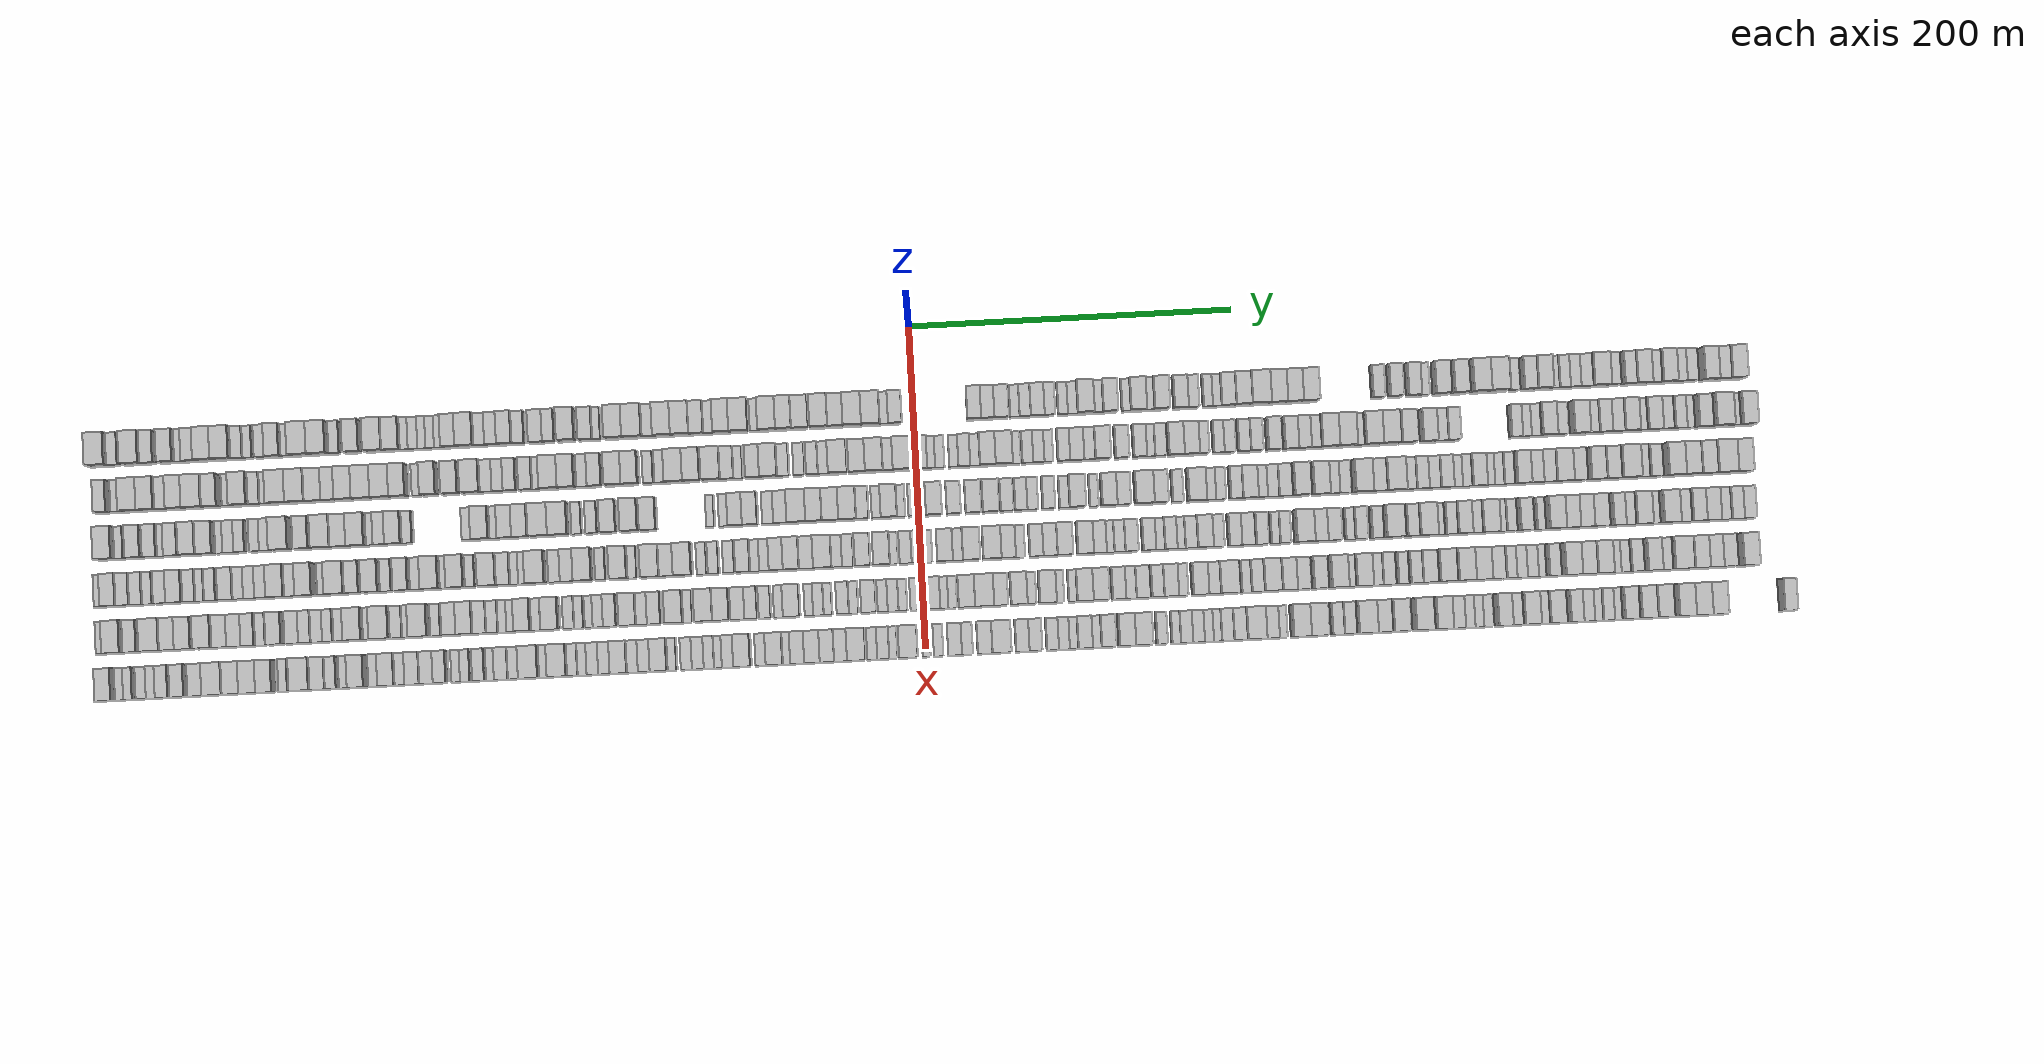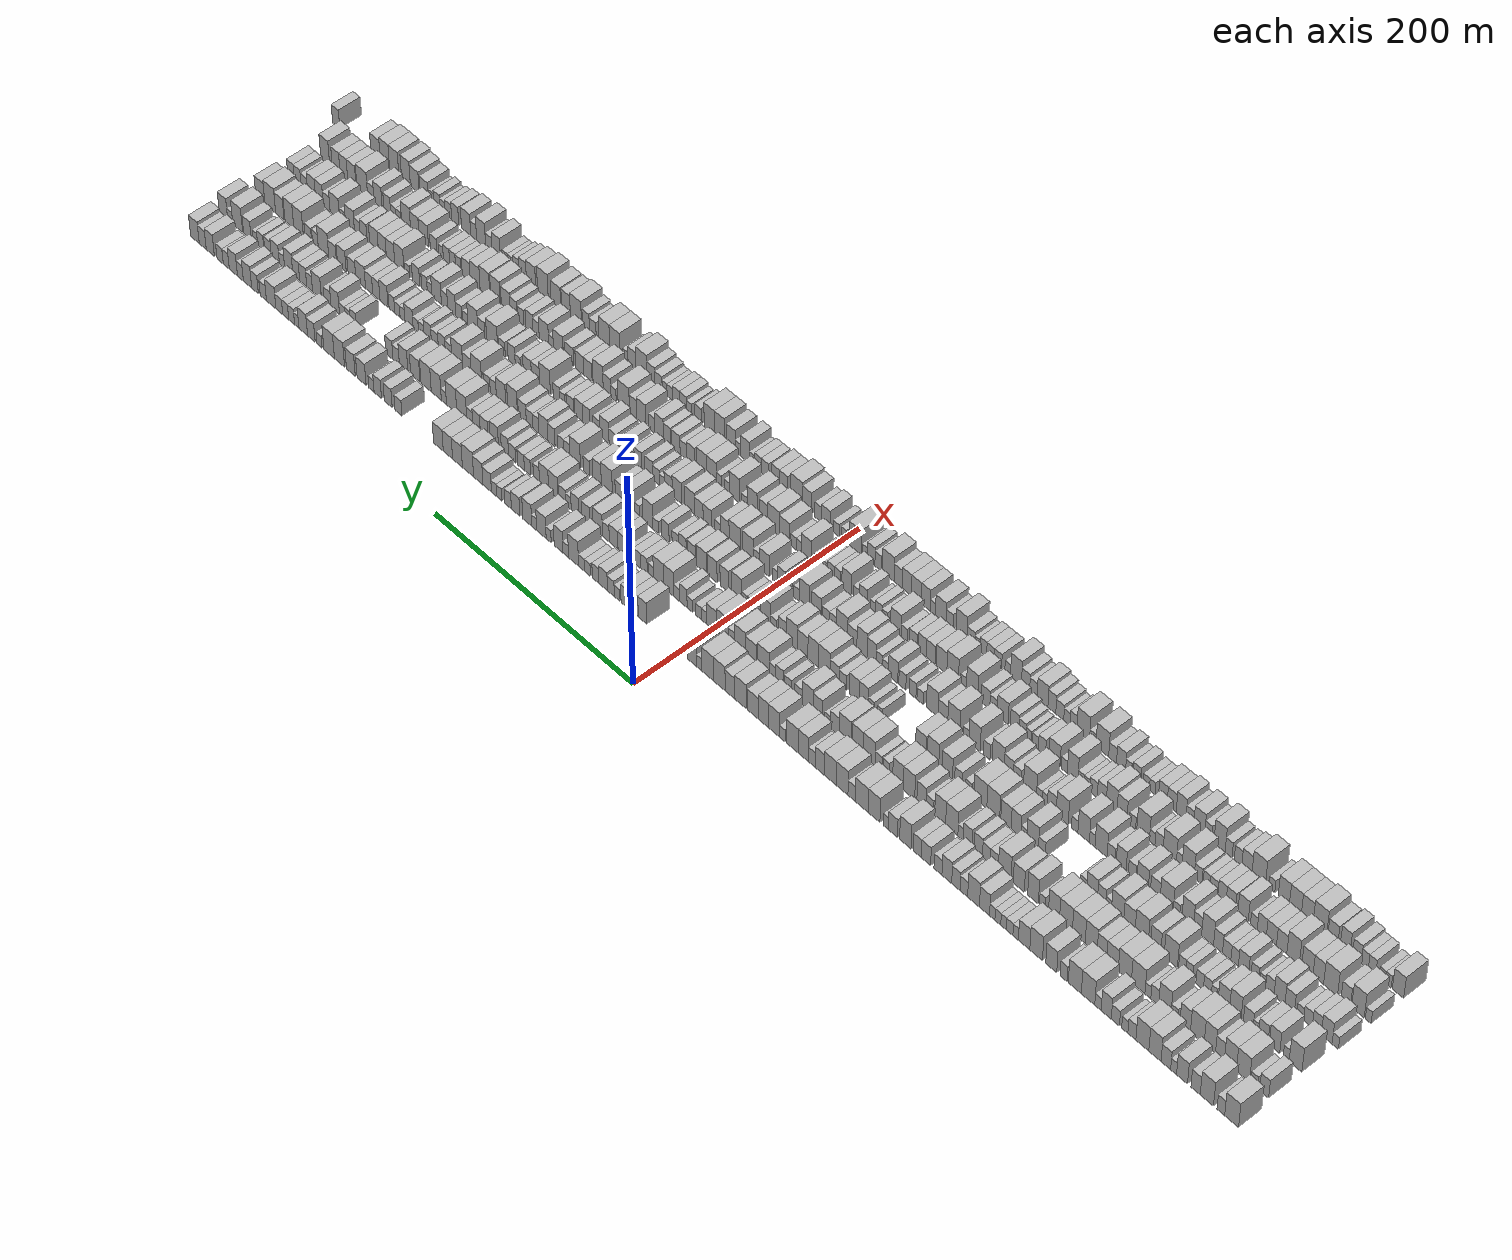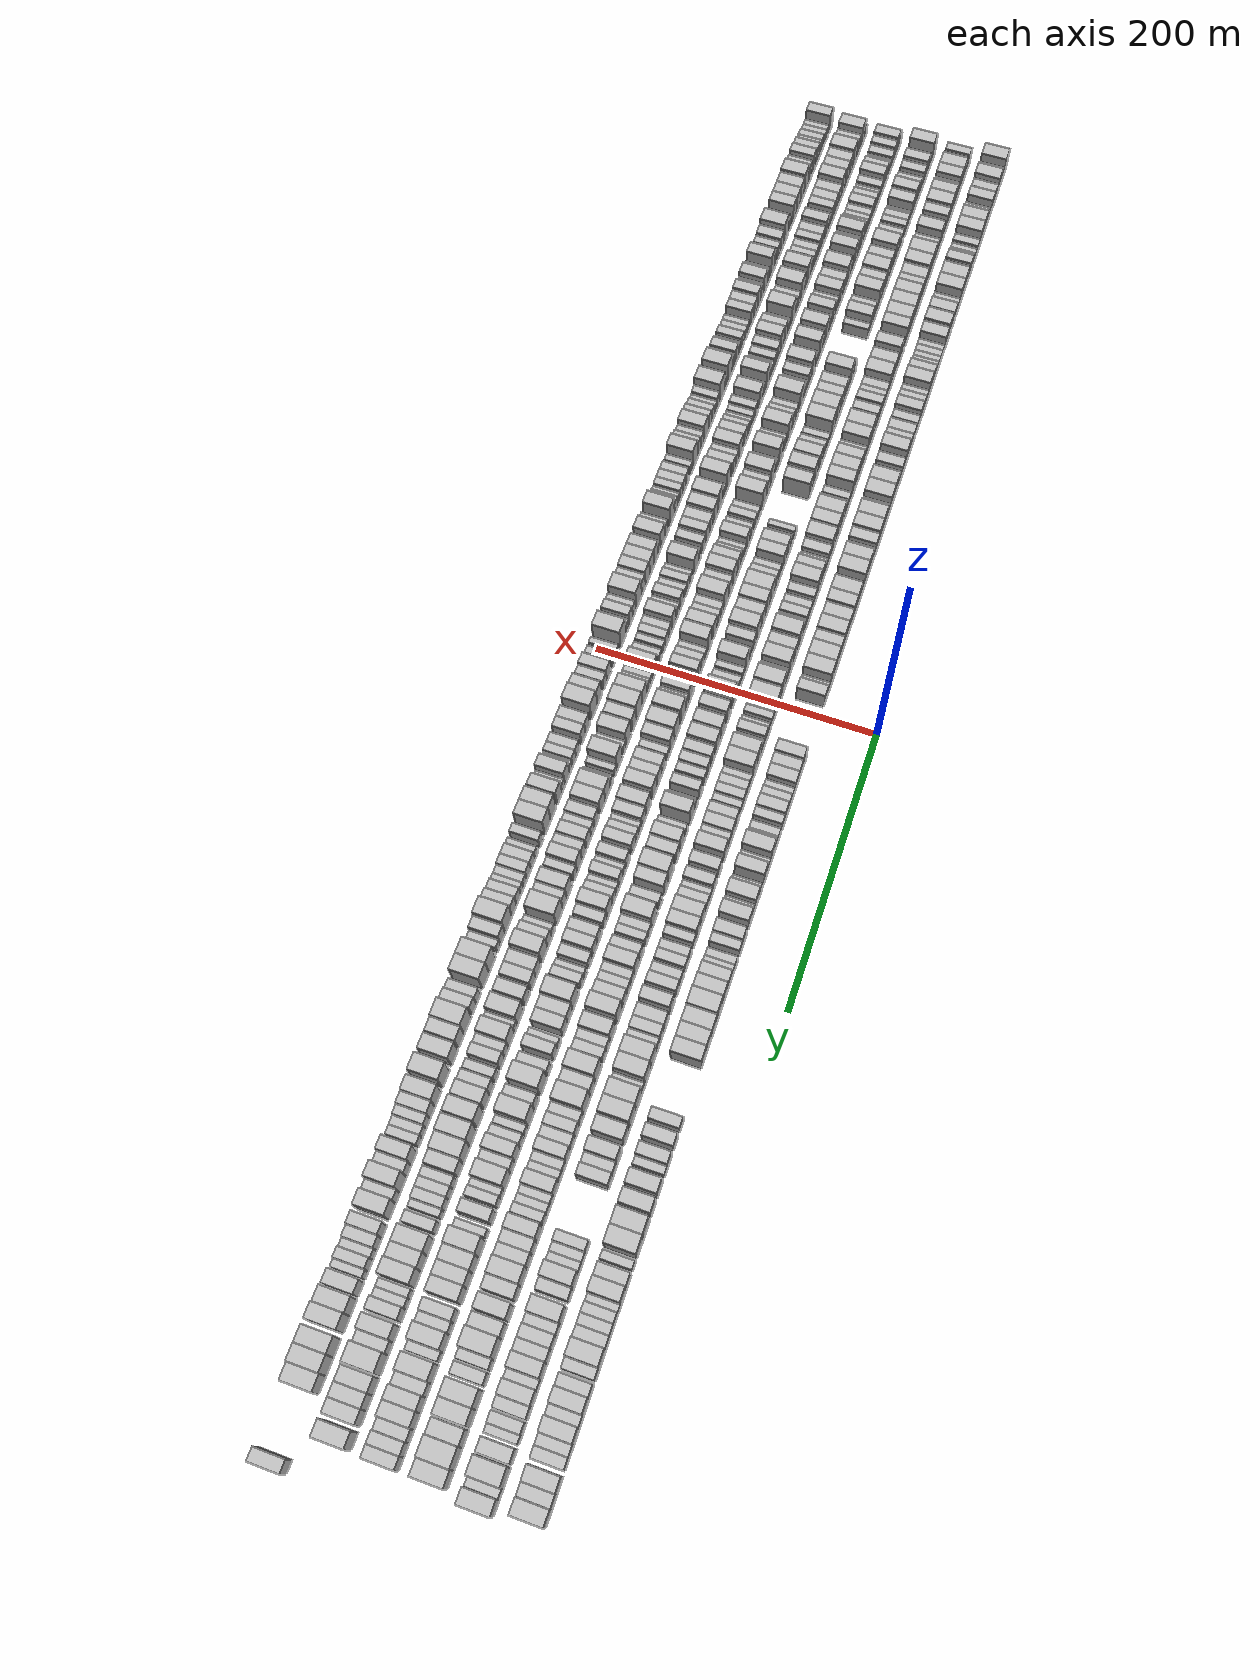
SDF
<sdf version="1.6">
 <world name="default">
  <scene>
   <sky><clouds><speed>12</speed></clouds></sky>
   <ambient>0.4 0.4 0.4 1</ambient>
   <background>0.7 0.7 0.7 1</background>
   <shadows>1</shadows>
  </scene>
  <gravity>0 0 -9.8066</gravity>
  <magnetic_field>6e-06 2.3e-05 -4.2e-05</magnetic_field>
  <physics default="0" name="default_physics" type="ode">
   <ode>
    <solver>
     <type>quick</type>
     <iters>10</iters>
     <sor>1.0</sor>
     <use_dynamic_moi_rescaling>0</use_dynamic_moi_rescaling>
    </solver>
    <constraints>
     <cfm>0</cfm>
     <erp>0.2</erp>
     <contact_max_correcting_vel>100</contact_max_correcting_vel>
     <contact_surface_layer>0.001</contact_surface_layer>
    </constraints>
   </ode>
   <max_step_size>0.004</max_step_size>
   <real_time_factor>1</real_time_factor>
   <real_time_update_rate>250</real_time_update_rate>
  </physics>
  <light name="sun" type="directional">
   <pose>0 0 10 0 0 0</pose>
   <diffuse>0.8 0.8 0.8 1</diffuse>
   <specular>0.2 0.2 0.2 1</specular>
   <attenuation>
    <range>1000</range>
    <constant>0.9</constant>
    <linear>0.01</linear>
    <quadratic>0.001</quadratic>
   </attenuation>
   <direction>-0.5 0.1 -0.9</direction>
  </light>
  <model name="building_1">
   <static>1</static>
   <pose>50.0000 -504.0976 0 0.000000 0.000000 0.000000</pose>
   <link name="link">
    <pose>0 0 12.00 0 0 0</pose>
    <collision name="collision"><geometry><box><size>20.0000 11.8048 24.0000</size></box></geometry></collision>
    <visual name="visual">
     <cast_shadows>0</cast_shadows>
     <geometry><box><size>20.0000 11.8048 24.0000</size></box></geometry>
     <material>
      <script>
       <uri>model://HANNAS_wall/materials/scripts</uri>
       <uri>model://HANNAS_wall/materials/textures</uri>
       <name>vrc/HANNAS_wall</name>
      </script>
     </material>
    </visual>
   </link>
  </model>
  <model name="building_2">
   <static>1</static>
   <pose>50.0000 -494.9151 0 0.000000 0.000000 0.000000</pose>
   <link name="link">
    <pose>0 0 7.50 0 0 0</pose>
    <collision name="collision"><geometry><box><size>20.0000 6.5601 15.0000</size></box></geometry></collision>
    <visual name="visual">
     <cast_shadows>0</cast_shadows>
     <geometry><box><size>20.0000 6.5601 15.0000</size></box></geometry>
     <material>
      <script>
       <uri>model://HANNAS_wall/materials/scripts</uri>
       <uri>model://HANNAS_wall/materials/textures</uri>
       <name>vrc/HANNAS_wall</name>
      </script>
     </material>
    </visual>
   </link>
  </model>
  <model name="building_3">
   <static>1</static>
   <pose>50.0000 -482.9600 0 0.000000 0.000000 0.000000</pose>
   <link name="link">
    <pose>0 0 12.00 0 0 0</pose>
    <collision name="collision"><geometry><box><size>20.0000 11.3502 24.0000</size></box></geometry></collision>
    <visual name="visual">
     <cast_shadows>0</cast_shadows>
     <geometry><box><size>20.0000 11.3502 24.0000</size></box></geometry>
     <material>
      <script>
       <uri>model://HANNAS_wall/materials/scripts</uri>
       <uri>model://HANNAS_wall/materials/textures</uri>
       <name>vrc/HANNAS_wall</name>
      </script>
     </material>
    </visual>
   </link>
  </model>
  <model name="building_4">
   <static>1</static>
   <pose>50.0000 -473.3029 0 0.000000 0.000000 0.000000</pose>
   <link name="link">
    <pose>0 0 9.00 0 0 0</pose>
    <collision name="collision"><geometry><box><size>20.0000 7.9639 18.0000</size></box></geometry></collision>
    <visual name="visual">
     <cast_shadows>0</cast_shadows>
     <geometry><box><size>20.0000 7.9639 18.0000</size></box></geometry>
     <material>
      <script>
       <uri>model://HANNAS_wall/materials/scripts</uri>
       <uri>model://HANNAS_wall/materials/textures</uri>
       <name>vrc/HANNAS_wall</name>
      </script>
     </material>
    </visual>
   </link>
  </model>
  <model name="building_5">
   <static>1</static>
   <pose>50.0000 -461.6112 0 0.000000 0.000000 0.000000</pose>
   <link name="link">
    <pose>0 0 10.50 0 0 0</pose>
    <collision name="collision"><geometry><box><size>20.0000 9.4196 21.0000</size></box></geometry></collision>
    <visual name="visual">
     <cast_shadows>0</cast_shadows>
     <geometry><box><size>20.0000 9.4196 21.0000</size></box></geometry>
     <material>
      <script>
       <uri>model://HANNAS_wall/materials/scripts</uri>
       <uri>model://HANNAS_wall/materials/textures</uri>
       <name>vrc/HANNAS_wall</name>
      </script>
     </material>
    </visual>
   </link>
  </model>
  <model name="building_6">
   <static>1</static>
   <pose>50.0000 -454.3473 0 0.000000 0.000000 0.000000</pose>
   <link name="link">
    <pose>0 0 6.00 0 0 0</pose>
    <collision name="collision"><geometry><box><size>20.0000 5.1082 12.0000</size></box></geometry></collision>
    <visual name="visual">
     <cast_shadows>0</cast_shadows>
     <geometry><box><size>20.0000 5.1082 12.0000</size></box></geometry>
     <material>
      <script>
       <uri>model://HANNAS_wall/materials/scripts</uri>
       <uri>model://HANNAS_wall/materials/textures</uri>
       <name>vrc/HANNAS_wall</name>
      </script>
     </material>
    </visual>
   </link>
  </model>
  <model name="building_7">
   <static>1</static>
   <pose>50.0000 -447.6620 0 0.000000 0.000000 0.000000</pose>
   <link name="link">
    <pose>0 0 9.00 0 0 0</pose>
    <collision name="collision"><geometry><box><size>20.0000 8.2625 18.0000</size></box></geometry></collision>
    <visual name="visual">
     <cast_shadows>0</cast_shadows>
     <geometry><box><size>20.0000 8.2625 18.0000</size></box></geometry>
     <material>
      <script>
       <uri>model://HANNAS_wall/materials/scripts</uri>
       <uri>model://HANNAS_wall/materials/textures</uri>
       <name>vrc/HANNAS_wall</name>
      </script>
     </material>
    </visual>
   </link>
  </model>
  <model name="building_8">
   <static>1</static>
   <pose>50.0000 -438.2175 0 0.000000 0.000000 0.000000</pose>
   <link name="link">
    <pose>0 0 12.00 0 0 0</pose>
    <collision name="collision"><geometry><box><size>20.0000 10.6264 24.0000</size></box></geometry></collision>
    <visual name="visual">
     <cast_shadows>0</cast_shadows>
     <geometry><box><size>20.0000 10.6264 24.0000</size></box></geometry>
     <material>
      <script>
       <uri>model://HANNAS_wall/materials/scripts</uri>
       <uri>model://HANNAS_wall/materials/textures</uri>
       <name>vrc/HANNAS_wall</name>
      </script>
     </material>
    </visual>
   </link>
  </model>
  <model name="building_9">
   <static>1</static>
   <pose>50.0000 -427.2729 0 0.000000 0.000000 0.000000</pose>
   <link name="link">
    <pose>0 0 12.00 0 0 0</pose>
    <collision name="collision"><geometry><box><size>20.0000 11.2627 24.0000</size></box></geometry></collision>
    <visual name="visual">
     <cast_shadows>0</cast_shadows>
     <geometry><box><size>20.0000 11.2627 24.0000</size></box></geometry>
     <material>
      <script>
       <uri>model://HANNAS_wall/materials/scripts</uri>
       <uri>model://HANNAS_wall/materials/textures</uri>
       <name>vrc/HANNAS_wall</name>
      </script>
     </material>
    </visual>
   </link>
  </model>
  <model name="building_10">
   <static>1</static>
   <pose>50.0000 -418.1469 0 0.000000 0.000000 0.000000</pose>
   <link name="link">
    <pose>0 0 7.50 0 0 0</pose>
    <collision name="collision"><geometry><box><size>20.0000 6.9893 15.0000</size></box></geometry></collision>
    <visual name="visual">
     <cast_shadows>0</cast_shadows>
     <geometry><box><size>20.0000 6.9893 15.0000</size></box></geometry>
     <material>
      <script>
       <uri>model://HANNAS_wall/materials/scripts</uri>
       <uri>model://HANNAS_wall/materials/textures</uri>
       <name>vrc/HANNAS_wall</name>
      </script>
     </material>
    </visual>
   </link>
  </model>
  <model name="building_11">
   <static>1</static>
   <pose>50.0000 -411.9523 0 0.000000 0.000000 0.000000</pose>
   <link name="link">
    <pose>0 0 6.00 0 0 0</pose>
    <collision name="collision"><geometry><box><size>20.0000 5.3999 12.0000</size></box></geometry></collision>
    <visual name="visual">
     <cast_shadows>0</cast_shadows>
     <geometry><box><size>20.0000 5.3999 12.0000</size></box></geometry>
     <material>
      <script>
       <uri>model://HANNAS_wall/materials/scripts</uri>
       <uri>model://HANNAS_wall/materials/textures</uri>
       <name>vrc/HANNAS_wall</name>
      </script>
     </material>
    </visual>
   </link>
  </model>
  <model name="building_12">
   <static>1</static>
   <pose>50.0000 -403.6779 0 0.000000 0.000000 0.000000</pose>
   <link name="link">
    <pose>0 0 7.50 0 0 0</pose>
    <collision name="collision"><geometry><box><size>20.0000 7.1489 15.0000</size></box></geometry></collision>
    <visual name="visual">
     <cast_shadows>0</cast_shadows>
     <geometry><box><size>20.0000 7.1489 15.0000</size></box></geometry>
     <material>
      <script>
       <uri>model://HANNAS_wall/materials/scripts</uri>
       <uri>model://HANNAS_wall/materials/textures</uri>
       <name>vrc/HANNAS_wall</name>
      </script>
     </material>
    </visual>
   </link>
  </model>
  <model name="building_13">
   <static>1</static>
   <pose>50.0000 -395.6490 0 0.000000 0.000000 0.000000</pose>
   <link name="link">
    <pose>0 0 10.50 0 0 0</pose>
    <collision name="collision"><geometry><box><size>20.0000 8.9090 21.0000</size></box></geometry></collision>
    <visual name="visual">
     <cast_shadows>0</cast_shadows>
     <geometry><box><size>20.0000 8.9090 21.0000</size></box></geometry>
     <material>
      <script>
       <uri>model://HANNAS_wall/materials/scripts</uri>
       <uri>model://HANNAS_wall/materials/textures</uri>
       <name>vrc/HANNAS_wall</name>
      </script>
     </material>
    </visual>
   </link>
  </model>
  <model name="building_14">
   <static>1</static>
   <pose>50.0000 -388.3888 0 0.000000 0.000000 0.000000</pose>
   <link name="link">
    <pose>0 0 6.00 0 0 0</pose>
    <collision name="collision"><geometry><box><size>20.0000 5.6112 12.0000</size></box></geometry></collision>
    <visual name="visual">
     <cast_shadows>0</cast_shadows>
     <geometry><box><size>20.0000 5.6112 12.0000</size></box></geometry>
     <material>
      <script>
       <uri>model://HANNAS_wall/materials/scripts</uri>
       <uri>model://HANNAS_wall/materials/textures</uri>
       <name>vrc/HANNAS_wall</name>
      </script>
     </material>
    </visual>
   </link>
  </model>
  <model name="building_15">
   <static>1</static>
   <pose>50.0000 -379.6603 0 0.000000 0.000000 0.000000</pose>
   <link name="link">
    <pose>0 0 12.00 0 0 0</pose>
    <collision name="collision"><geometry><box><size>20.0000 11.8460 24.0000</size></box></geometry></collision>
    <visual name="visual">
     <cast_shadows>0</cast_shadows>
     <geometry><box><size>20.0000 11.8460 24.0000</size></box></geometry>
     <material>
      <script>
       <uri>model://HANNAS_wall/materials/scripts</uri>
       <uri>model://HANNAS_wall/materials/textures</uri>
       <name>vrc/HANNAS_wall</name>
      </script>
     </material>
    </visual>
   </link>
  </model>
  <model name="building_16">
   <static>1</static>
   <pose>50.0000 -367.9812 0 0.000000 0.000000 0.000000</pose>
   <link name="link">
    <pose>0 0 12.00 0 0 0</pose>
    <collision name="collision"><geometry><box><size>20.0000 11.5121 24.0000</size></box></geometry></collision>
    <visual name="visual">
     <cast_shadows>0</cast_shadows>
     <geometry><box><size>20.0000 11.5121 24.0000</size></box></geometry>
     <material>
      <script>
       <uri>model://HANNAS_wall/materials/scripts</uri>
       <uri>model://HANNAS_wall/materials/textures</uri>
       <name>vrc/HANNAS_wall</name>
      </script>
     </material>
    </visual>
   </link>
  </model>
  <model name="building_17">
   <static>1</static>
   <pose>50.0000 -358.0856 0 0.000000 0.000000 0.000000</pose>
   <link name="link">
    <pose>0 0 7.50 0 0 0</pose>
    <collision name="collision"><geometry><box><size>20.0000 6.2792 15.0000</size></box></geometry></collision>
    <visual name="visual">
     <cast_shadows>0</cast_shadows>
     <geometry><box><size>20.0000 6.2792 15.0000</size></box></geometry>
     <material>
      <script>
       <uri>model://HANNAS_wall/materials/scripts</uri>
       <uri>model://HANNAS_wall/materials/textures</uri>
       <name>vrc/HANNAS_wall</name>
      </script>
     </material>
    </visual>
   </link>
  </model>
  <model name="building_18">
   <static>1</static>
   <pose>50.0000 -347.0845 0 0.000000 0.000000 0.000000</pose>
   <link name="link">
    <pose>0 0 10.50 0 0 0</pose>
    <collision name="collision"><geometry><box><size>20.0000 9.7231 21.0000</size></box></geometry></collision>
    <visual name="visual">
     <cast_shadows>0</cast_shadows>
     <geometry><box><size>20.0000 9.7231 21.0000</size></box></geometry>
     <material>
      <script>
       <uri>model://HANNAS_wall/materials/scripts</uri>
       <uri>model://HANNAS_wall/materials/textures</uri>
       <name>vrc/HANNAS_wall</name>
      </script>
     </material>
    </visual>
   </link>
  </model>
  <model name="building_19">
   <static>1</static>
   <pose>50.0000 -333.5876 0 0.000000 0.000000 0.000000</pose>
   <link name="link">
    <pose>0 0 12.00 0 0 0</pose>
    <collision name="collision"><geometry><box><size>20.0000 11.2706 24.0000</size></box></geometry></collision>
    <visual name="visual">
     <cast_shadows>0</cast_shadows>
     <geometry><box><size>20.0000 11.2706 24.0000</size></box></geometry>
     <material>
      <script>
       <uri>model://HANNAS_wall/materials/scripts</uri>
       <uri>model://HANNAS_wall/materials/textures</uri>
       <name>vrc/HANNAS_wall</name>
      </script>
     </material>
    </visual>
   </link>
  </model>
  <model name="building_20">
   <static>1</static>
   <pose>50.0000 -322.8248 0 0.000000 0.000000 0.000000</pose>
   <link name="link">
    <pose>0 0 10.50 0 0 0</pose>
    <collision name="collision"><geometry><box><size>20.0000 10.2550 21.0000</size></box></geometry></collision>
    <visual name="visual">
     <cast_shadows>0</cast_shadows>
     <geometry><box><size>20.0000 10.2550 21.0000</size></box></geometry>
     <material>
      <script>
       <uri>model://HANNAS_wall/materials/scripts</uri>
       <uri>model://HANNAS_wall/materials/textures</uri>
       <name>vrc/HANNAS_wall</name>
      </script>
     </material>
    </visual>
   </link>
  </model>
  <model name="building_21">
   <static>1</static>
   <pose>50.0000 -315.2294 0 0.000000 0.000000 0.000000</pose>
   <link name="link">
    <pose>0 0 6.00 0 0 0</pose>
    <collision name="collision"><geometry><box><size>20.0000 4.9359 12.0000</size></box></geometry></collision>
    <visual name="visual">
     <cast_shadows>0</cast_shadows>
     <geometry><box><size>20.0000 4.9359 12.0000</size></box></geometry>
     <material>
      <script>
       <uri>model://HANNAS_wall/materials/scripts</uri>
       <uri>model://HANNAS_wall/materials/textures</uri>
       <name>vrc/HANNAS_wall</name>
      </script>
     </material>
    </visual>
   </link>
  </model>
  <model name="building_22">
   <static>1</static>
   <pose>50.0000 -309.7758 0 0.000000 0.000000 0.000000</pose>
   <link name="link">
    <pose>0 0 6.00 0 0 0</pose>
    <collision name="collision"><geometry><box><size>20.0000 5.9713 12.0000</size></box></geometry></collision>
    <visual name="visual">
     <cast_shadows>0</cast_shadows>
     <geometry><box><size>20.0000 5.9713 12.0000</size></box></geometry>
     <material>
      <script>
       <uri>model://HANNAS_wall/materials/scripts</uri>
       <uri>model://HANNAS_wall/materials/textures</uri>
       <name>vrc/HANNAS_wall</name>
      </script>
     </material>
    </visual>
   </link>
  </model>
  <model name="building_23">
   <static>1</static>
   <pose>50.0000 -304.3041 0 0.000000 0.000000 0.000000</pose>
   <link name="link">
    <pose>0 0 6.00 0 0 0</pose>
    <collision name="collision"><geometry><box><size>20.0000 4.9721 12.0000</size></box></geometry></collision>
    <visual name="visual">
     <cast_shadows>0</cast_shadows>
     <geometry><box><size>20.0000 4.9721 12.0000</size></box></geometry>
     <material>
      <script>
       <uri>model://HANNAS_wall/materials/scripts</uri>
       <uri>model://HANNAS_wall/materials/textures</uri>
       <name>vrc/HANNAS_wall</name>
      </script>
     </material>
    </visual>
   </link>
  </model>
  <model name="building_24">
   <static>1</static>
   <pose>50.0000 -299.1880 0 0.000000 0.000000 0.000000</pose>
   <link name="link">
    <pose>0 0 6.00 0 0 0</pose>
    <collision name="collision"><geometry><box><size>20.0000 5.2600 12.0000</size></box></geometry></collision>
    <visual name="visual">
     <cast_shadows>0</cast_shadows>
     <geometry><box><size>20.0000 5.2600 12.0000</size></box></geometry>
     <material>
      <script>
       <uri>model://HANNAS_wall/materials/scripts</uri>
       <uri>model://HANNAS_wall/materials/textures</uri>
       <name>vrc/HANNAS_wall</name>
      </script>
     </material>
    </visual>
   </link>
  </model>
  <model name="building_25">
   <static>1</static>
   <pose>50.0000 -294.1270 0 0.000000 0.000000 0.000000</pose>
   <link name="link">
    <pose>0 0 6.00 0 0 0</pose>
    <collision name="collision"><geometry><box><size>20.0000 4.8620 12.0000</size></box></geometry></collision>
    <visual name="visual">
     <cast_shadows>0</cast_shadows>
     <geometry><box><size>20.0000 4.8620 12.0000</size></box></geometry>
     <material>
      <script>
       <uri>model://HANNAS_wall/materials/scripts</uri>
       <uri>model://HANNAS_wall/materials/textures</uri>
       <name>vrc/HANNAS_wall</name>
      </script>
     </material>
    </visual>
   </link>
  </model>
  <model name="building_26">
   <static>1</static>
   <pose>50.0000 -287.1292 0 0.000000 0.000000 0.000000</pose>
   <link name="link">
    <pose>0 0 10.50 0 0 0</pose>
    <collision name="collision"><geometry><box><size>20.0000 9.1337 21.0000</size></box></geometry></collision>
    <visual name="visual">
     <cast_shadows>0</cast_shadows>
     <geometry><box><size>20.0000 9.1337 21.0000</size></box></geometry>
     <material>
      <script>
       <uri>model://HANNAS_wall/materials/scripts</uri>
       <uri>model://HANNAS_wall/materials/textures</uri>
       <name>vrc/HANNAS_wall</name>
      </script>
     </material>
    </visual>
   </link>
  </model>
  <model name="building_27">
   <static>1</static>
   <pose>50.0000 -277.2071 0 0.000000 0.000000 0.000000</pose>
   <link name="link">
    <pose>0 0 12.00 0 0 0</pose>
    <collision name="collision"><geometry><box><size>20.0000 10.7105 24.0000</size></box></geometry></collision>
    <visual name="visual">
     <cast_shadows>0</cast_shadows>
     <geometry><box><size>20.0000 10.7105 24.0000</size></box></geometry>
     <material>
      <script>
       <uri>model://HANNAS_wall/materials/scripts</uri>
       <uri>model://HANNAS_wall/materials/textures</uri>
       <name>vrc/HANNAS_wall</name>
      </script>
     </material>
    </visual>
   </link>
  </model>
  <model name="building_28">
   <static>1</static>
   <pose>50.0000 -268.3715 0 0.000000 0.000000 0.000000</pose>
   <link name="link">
    <pose>0 0 7.50 0 0 0</pose>
    <collision name="collision"><geometry><box><size>20.0000 6.9605 15.0000</size></box></geometry></collision>
    <visual name="visual">
     <cast_shadows>0</cast_shadows>
     <geometry><box><size>20.0000 6.9605 15.0000</size></box></geometry>
     <material>
      <script>
       <uri>model://HANNAS_wall/materials/scripts</uri>
       <uri>model://HANNAS_wall/materials/textures</uri>
       <name>vrc/HANNAS_wall</name>
      </script>
     </material>
    </visual>
   </link>
  </model>
  <model name="building_29">
   <static>1</static>
   <pose>50.0000 -261.0949 0 0.000000 0.000000 0.000000</pose>
   <link name="link">
    <pose>0 0 9.00 0 0 0</pose>
    <collision name="collision"><geometry><box><size>20.0000 7.5927 18.0000</size></box></geometry></collision>
    <visual name="visual">
     <cast_shadows>0</cast_shadows>
     <geometry><box><size>20.0000 7.5927 18.0000</size></box></geometry>
     <material>
      <script>
       <uri>model://HANNAS_wall/materials/scripts</uri>
       <uri>model://HANNAS_wall/materials/textures</uri>
       <name>vrc/HANNAS_wall</name>
      </script>
     </material>
    </visual>
   </link>
  </model>
  <model name="building_30">
   <static>1</static>
   <pose>50.0000 -252.8241 0 0.000000 0.000000 0.000000</pose>
   <link name="link">
    <pose>0 0 10.50 0 0 0</pose>
    <collision name="collision"><geometry><box><size>20.0000 8.9490 21.0000</size></box></geometry></collision>
    <visual name="visual">
     <cast_shadows>0</cast_shadows>
     <geometry><box><size>20.0000 8.9490 21.0000</size></box></geometry>
     <material>
      <script>
       <uri>model://HANNAS_wall/materials/scripts</uri>
       <uri>model://HANNAS_wall/materials/textures</uri>
       <name>vrc/HANNAS_wall</name>
      </script>
     </material>
    </visual>
   </link>
  </model>
  <model name="building_31">
   <static>1</static>
   <pose>50.0000 -244.6851 0 0.000000 0.000000 0.000000</pose>
   <link name="link">
    <pose>0 0 7.50 0 0 0</pose>
    <collision name="collision"><geometry><box><size>20.0000 7.3291 15.0000</size></box></geometry></collision>
    <visual name="visual">
     <cast_shadows>0</cast_shadows>
     <geometry><box><size>20.0000 7.3291 15.0000</size></box></geometry>
     <material>
      <script>
       <uri>model://HANNAS_wall/materials/scripts</uri>
       <uri>model://HANNAS_wall/materials/textures</uri>
       <name>vrc/HANNAS_wall</name>
      </script>
     </material>
    </visual>
   </link>
  </model>
  <model name="building_32">
   <static>1</static>
   <pose>50.0000 -233.7050 0 0.000000 0.000000 0.000000</pose>
   <link name="link">
    <pose>0 0 9.00 0 0 0</pose>
    <collision name="collision"><geometry><box><size>20.0000 8.6311 18.0000</size></box></geometry></collision>
    <visual name="visual">
     <cast_shadows>0</cast_shadows>
     <geometry><box><size>20.0000 8.6311 18.0000</size></box></geometry>
     <material>
      <script>
       <uri>model://HANNAS_wall/materials/scripts</uri>
       <uri>model://HANNAS_wall/materials/textures</uri>
       <name>vrc/HANNAS_wall</name>
      </script>
     </material>
    </visual>
   </link>
  </model>
  <model name="building_33">
   <static>1</static>
   <pose>50.0000 -225.7791 0 0.000000 0.000000 0.000000</pose>
   <link name="link">
    <pose>0 0 9.00 0 0 0</pose>
    <collision name="collision"><geometry><box><size>20.0000 7.2206 18.0000</size></box></geometry></collision>
    <visual name="visual">
     <cast_shadows>0</cast_shadows>
     <geometry><box><size>20.0000 7.2206 18.0000</size></box></geometry>
     <material>
      <script>
       <uri>model://HANNAS_wall/materials/scripts</uri>
       <uri>model://HANNAS_wall/materials/textures</uri>
       <name>vrc/HANNAS_wall</name>
      </script>
     </material>
    </visual>
   </link>
  </model>
  <model name="building_34">
   <static>1</static>
   <pose>50.0000 -214.8149 0 0.000000 0.000000 0.000000</pose>
   <link name="link">
    <pose>0 0 12.00 0 0 0</pose>
    <collision name="collision"><geometry><box><size>20.0000 10.7077 24.0000</size></box></geometry></collision>
    <visual name="visual">
     <cast_shadows>0</cast_shadows>
     <geometry><box><size>20.0000 10.7077 24.0000</size></box></geometry>
     <material>
      <script>
       <uri>model://HANNAS_wall/materials/scripts</uri>
       <uri>model://HANNAS_wall/materials/textures</uri>
       <name>vrc/HANNAS_wall</name>
      </script>
     </material>
    </visual>
   </link>
  </model>
  <model name="building_35">
   <static>1</static>
   <pose>50.0000 -203.2133 0 0.000000 0.000000 0.000000</pose>
   <link name="link">
    <pose>0 0 9.00 0 0 0</pose>
    <collision name="collision"><geometry><box><size>20.0000 8.4956 18.0000</size></box></geometry></collision>
    <visual name="visual">
     <cast_shadows>0</cast_shadows>
     <geometry><box><size>20.0000 8.4956 18.0000</size></box></geometry>
     <material>
      <script>
       <uri>model://HANNAS_wall/materials/scripts</uri>
       <uri>model://HANNAS_wall/materials/textures</uri>
       <name>vrc/HANNAS_wall</name>
      </script>
     </material>
    </visual>
   </link>
  </model>
  <model name="building_36">
   <static>1</static>
   <pose>50.0000 -196.5370 0 0.000000 0.000000 0.000000</pose>
   <link name="link">
    <pose>0 0 6.00 0 0 0</pose>
    <collision name="collision"><geometry><box><size>20.0000 4.8569 12.0000</size></box></geometry></collision>
    <visual name="visual">
     <cast_shadows>0</cast_shadows>
     <geometry><box><size>20.0000 4.8569 12.0000</size></box></geometry>
     <material>
      <script>
       <uri>model://HANNAS_wall/materials/scripts</uri>
       <uri>model://HANNAS_wall/materials/textures</uri>
       <name>vrc/HANNAS_wall</name>
      </script>
     </material>
    </visual>
   </link>
  </model>
  <model name="building_37">
   <static>1</static>
   <pose>50.0000 -185.6003 0 0.000000 0.000000 0.000000</pose>
   <link name="link">
    <pose>0 0 12.00 0 0 0</pose>
    <collision name="collision"><geometry><box><size>20.0000 11.0165 24.0000</size></box></geometry></collision>
    <visual name="visual">
     <cast_shadows>0</cast_shadows>
     <geometry><box><size>20.0000 11.0165 24.0000</size></box></geometry>
     <material>
      <script>
       <uri>model://HANNAS_wall/materials/scripts</uri>
       <uri>model://HANNAS_wall/materials/textures</uri>
       <name>vrc/HANNAS_wall</name>
      </script>
     </material>
    </visual>
   </link>
  </model>
  <model name="building_38">
   <static>1</static>
   <pose>50.0000 -174.1456 0 0.000000 0.000000 0.000000</pose>
   <link name="link">
    <pose>0 0 12.00 0 0 0</pose>
    <collision name="collision"><geometry><box><size>20.0000 11.8929 24.0000</size></box></geometry></collision>
    <visual name="visual">
     <cast_shadows>0</cast_shadows>
     <geometry><box><size>20.0000 11.8929 24.0000</size></box></geometry>
     <material>
      <script>
       <uri>model://HANNAS_wall/materials/scripts</uri>
       <uri>model://HANNAS_wall/materials/textures</uri>
       <name>vrc/HANNAS_wall</name>
      </script>
     </material>
    </visual>
   </link>
  </model>
  <model name="building_39">
   <static>1</static>
   <pose>50.0000 -164.7043 0 0.000000 0.000000 0.000000</pose>
   <link name="link">
    <pose>0 0 7.50 0 0 0</pose>
    <collision name="collision"><geometry><box><size>20.0000 6.9897 15.0000</size></box></geometry></collision>
    <visual name="visual">
     <cast_shadows>0</cast_shadows>
     <geometry><box><size>20.0000 6.9897 15.0000</size></box></geometry>
     <material>
      <script>
       <uri>model://HANNAS_wall/materials/scripts</uri>
       <uri>model://HANNAS_wall/materials/textures</uri>
       <name>vrc/HANNAS_wall</name>
      </script>
     </material>
    </visual>
   </link>
  </model>
  <model name="building_40">
   <static>1</static>
   <pose>50.0000 -155.7014 0 0.000000 0.000000 0.000000</pose>
   <link name="link">
    <pose>0 0 12.00 0 0 0</pose>
    <collision name="collision"><geometry><box><size>20.0000 11.0162 24.0000</size></box></geometry></collision>
    <visual name="visual">
     <cast_shadows>0</cast_shadows>
     <geometry><box><size>20.0000 11.0162 24.0000</size></box></geometry>
     <material>
      <script>
       <uri>model://HANNAS_wall/materials/scripts</uri>
       <uri>model://HANNAS_wall/materials/textures</uri>
       <name>vrc/HANNAS_wall</name>
      </script>
     </material>
    </visual>
   </link>
  </model>
  <model name="building_41">
   <static>1</static>
   <pose>50.0000 -144.5966 0 0.000000 0.000000 0.000000</pose>
   <link name="link">
    <pose>0 0 12.00 0 0 0</pose>
    <collision name="collision"><geometry><box><size>20.0000 11.1933 24.0000</size></box></geometry></collision>
    <visual name="visual">
     <cast_shadows>0</cast_shadows>
     <geometry><box><size>20.0000 11.1933 24.0000</size></box></geometry>
     <material>
      <script>
       <uri>model://HANNAS_wall/materials/scripts</uri>
       <uri>model://HANNAS_wall/materials/textures</uri>
       <name>vrc/HANNAS_wall</name>
      </script>
     </material>
    </visual>
   </link>
  </model>
  <model name="building_42">
   <static>1</static>
   <pose>50.0000 -134.6149 0 0.000000 0.000000 0.000000</pose>
   <link name="link">
    <pose>0 0 10.50 0 0 0</pose>
    <collision name="collision"><geometry><box><size>20.0000 8.7701 21.0000</size></box></geometry></collision>
    <visual name="visual">
     <cast_shadows>0</cast_shadows>
     <geometry><box><size>20.0000 8.7701 21.0000</size></box></geometry>
     <material>
      <script>
       <uri>model://HANNAS_wall/materials/scripts</uri>
       <uri>model://HANNAS_wall/materials/textures</uri>
       <name>vrc/HANNAS_wall</name>
      </script>
     </material>
    </visual>
   </link>
  </model>
  <model name="building_43">
   <static>1</static>
   <pose>50.0000 -127.2108 0 0.000000 0.000000 0.000000</pose>
   <link name="link">
    <pose>0 0 7.50 0 0 0</pose>
    <collision name="collision"><geometry><box><size>20.0000 6.0381 15.0000</size></box></geometry></collision>
    <visual name="visual">
     <cast_shadows>0</cast_shadows>
     <geometry><box><size>20.0000 6.0381 15.0000</size></box></geometry>
     <material>
      <script>
       <uri>model://HANNAS_wall/materials/scripts</uri>
       <uri>model://HANNAS_wall/materials/textures</uri>
       <name>vrc/HANNAS_wall</name>
      </script>
     </material>
    </visual>
   </link>
  </model>
  <model name="building_44">
   <static>1</static>
   <pose>50.0000 -119.2499 0 0.000000 0.000000 0.000000</pose>
   <link name="link">
    <pose>0 0 12.00 0 0 0</pose>
    <collision name="collision"><geometry><box><size>20.0000 9.8837 24.0000</size></box></geometry></collision>
    <visual name="visual">
     <cast_shadows>0</cast_shadows>
     <geometry><box><size>20.0000 9.8837 24.0000</size></box></geometry>
     <material>
      <script>
       <uri>model://HANNAS_wall/materials/scripts</uri>
       <uri>model://HANNAS_wall/materials/textures</uri>
       <name>vrc/HANNAS_wall</name>
      </script>
     </material>
    </visual>
   </link>
  </model>
  <model name="building_45">
   <static>1</static>
   <pose>50.0000 -108.4909 0 0.000000 0.000000 0.000000</pose>
   <link name="link">
    <pose>0 0 12.00 0 0 0</pose>
    <collision name="collision"><geometry><box><size>20.0000 11.6342 24.0000</size></box></geometry></collision>
    <visual name="visual">
     <cast_shadows>0</cast_shadows>
     <geometry><box><size>20.0000 11.6342 24.0000</size></box></geometry>
     <material>
      <script>
       <uri>model://HANNAS_wall/materials/scripts</uri>
       <uri>model://HANNAS_wall/materials/textures</uri>
       <name>vrc/HANNAS_wall</name>
      </script>
     </material>
    </visual>
   </link>
  </model>
  <model name="building_46">
   <static>1</static>
   <pose>50.0000 -99.0924 0 0.000000 0.000000 0.000000</pose>
   <link name="link">
    <pose>0 0 6.00 0 0 0</pose>
    <collision name="collision"><geometry><box><size>20.0000 5.1629 12.0000</size></box></geometry></collision>
    <visual name="visual">
     <cast_shadows>0</cast_shadows>
     <geometry><box><size>20.0000 5.1629 12.0000</size></box></geometry>
     <material>
      <script>
       <uri>model://HANNAS_wall/materials/scripts</uri>
       <uri>model://HANNAS_wall/materials/textures</uri>
       <name>vrc/HANNAS_wall</name>
      </script>
     </material>
    </visual>
   </link>
  </model>
  <model name="building_47">
   <static>1</static>
   <pose>50.0000 -91.0473 0 0.000000 0.000000 0.000000</pose>
   <link name="link">
    <pose>0 0 12.00 0 0 0</pose>
    <collision name="collision"><geometry><box><size>20.0000 10.9271 24.0000</size></box></geometry></collision>
    <visual name="visual">
     <cast_shadows>0</cast_shadows>
     <geometry><box><size>20.0000 10.9271 24.0000</size></box></geometry>
     <material>
      <script>
       <uri>model://HANNAS_wall/materials/scripts</uri>
       <uri>model://HANNAS_wall/materials/textures</uri>
       <name>vrc/HANNAS_wall</name>
      </script>
     </material>
    </visual>
   </link>
  </model>
  <model name="building_48">
   <static>1</static>
   <pose>50.0000 -80.7545 0 0.000000 0.000000 0.000000</pose>
   <link name="link">
    <pose>0 0 12.00 0 0 0</pose>
    <collision name="collision"><geometry><box><size>20.0000 9.6585 24.0000</size></box></geometry></collision>
    <visual name="visual">
     <cast_shadows>0</cast_shadows>
     <geometry><box><size>20.0000 9.6585 24.0000</size></box></geometry>
     <material>
      <script>
       <uri>model://HANNAS_wall/materials/scripts</uri>
       <uri>model://HANNAS_wall/materials/textures</uri>
       <name>vrc/HANNAS_wall</name>
      </script>
     </material>
    </visual>
   </link>
  </model>
  <model name="building_49">
   <static>1</static>
   <pose>50.0000 -70.7394 0 0.000000 0.000000 0.000000</pose>
   <link name="link">
    <pose>0 0 10.50 0 0 0</pose>
    <collision name="collision"><geometry><box><size>20.0000 10.3717 21.0000</size></box></geometry></collision>
    <visual name="visual">
     <cast_shadows>0</cast_shadows>
     <geometry><box><size>20.0000 10.3717 21.0000</size></box></geometry>
     <material>
      <script>
       <uri>model://HANNAS_wall/materials/scripts</uri>
       <uri>model://HANNAS_wall/materials/textures</uri>
       <name>vrc/HANNAS_wall</name>
      </script>
     </material>
    </visual>
   </link>
  </model>
  <model name="building_50">
   <static>1</static>
   <pose>50.0000 -59.0698 0 0.000000 0.000000 0.000000</pose>
   <link name="link">
    <pose>0 0 12.00 0 0 0</pose>
    <collision name="collision"><geometry><box><size>20.0000 10.9674 24.0000</size></box></geometry></collision>
    <visual name="visual">
     <cast_shadows>0</cast_shadows>
     <geometry><box><size>20.0000 10.9674 24.0000</size></box></geometry>
     <material>
      <script>
       <uri>model://HANNAS_wall/materials/scripts</uri>
       <uri>model://HANNAS_wall/materials/textures</uri>
       <name>vrc/HANNAS_wall</name>
      </script>
     </material>
    </visual>
   </link>
  </model>
  <model name="building_51">
   <static>1</static>
   <pose>50.0000 -48.8268 0 0.000000 0.000000 0.000000</pose>
   <link name="link">
    <pose>0 0 10.50 0 0 0</pose>
    <collision name="collision"><geometry><box><size>20.0000 9.5186 21.0000</size></box></geometry></collision>
    <visual name="visual">
     <cast_shadows>0</cast_shadows>
     <geometry><box><size>20.0000 9.5186 21.0000</size></box></geometry>
     <material>
      <script>
       <uri>model://HANNAS_wall/materials/scripts</uri>
       <uri>model://HANNAS_wall/materials/textures</uri>
       <name>vrc/HANNAS_wall</name>
      </script>
     </material>
    </visual>
   </link>
  </model>
  <model name="building_52">
   <static>1</static>
   <pose>50.0000 -38.4101 0 0.000000 0.000000 0.000000</pose>
   <link name="link">
    <pose>0 0 12.00 0 0 0</pose>
    <collision name="collision"><geometry><box><size>20.0000 11.3149 24.0000</size></box></geometry></collision>
    <visual name="visual">
     <cast_shadows>0</cast_shadows>
     <geometry><box><size>20.0000 11.3149 24.0000</size></box></geometry>
     <material>
      <script>
       <uri>model://HANNAS_wall/materials/scripts</uri>
       <uri>model://HANNAS_wall/materials/textures</uri>
       <name>vrc/HANNAS_wall</name>
      </script>
     </material>
    </visual>
   </link>
  </model>
  <model name="building_53">
   <static>1</static>
   <pose>50.0000 -27.0780 0 0.000000 0.000000 0.000000</pose>
   <link name="link">
    <pose>0 0 12.00 0 0 0</pose>
    <collision name="collision"><geometry><box><size>20.0000 11.3492 24.0000</size></box></geometry></collision>
    <visual name="visual">
     <cast_shadows>0</cast_shadows>
     <geometry><box><size>20.0000 11.3492 24.0000</size></box></geometry>
     <material>
      <script>
       <uri>model://HANNAS_wall/materials/scripts</uri>
       <uri>model://HANNAS_wall/materials/textures</uri>
       <name>vrc/HANNAS_wall</name>
      </script>
     </material>
    </visual>
   </link>
  </model>
  <model name="building_54">
   <static>1</static>
   <pose>50.0000 -18.8104 0 0.000000 0.000000 0.000000</pose>
   <link name="link">
    <pose>0 0 6.00 0 0 0</pose>
    <collision name="collision"><geometry><box><size>20.0000 5.1860 12.0000</size></box></geometry></collision>
    <visual name="visual">
     <cast_shadows>0</cast_shadows>
     <geometry><box><size>20.0000 5.1860 12.0000</size></box></geometry>
     <material>
      <script>
       <uri>model://HANNAS_wall/materials/scripts</uri>
       <uri>model://HANNAS_wall/materials/textures</uri>
       <name>vrc/HANNAS_wall</name>
      </script>
     </material>
    </visual>
   </link>
  </model>
  <model name="building_55">
   <static>1</static>
   <pose>50.0000 -12.0017 0 0.000000 0.000000 0.000000</pose>
   <link name="link">
    <pose>0 0 9.00 0 0 0</pose>
    <collision name="collision"><geometry><box><size>20.0000 8.4314 18.0000</size></box></geometry></collision>
    <visual name="visual">
     <cast_shadows>0</cast_shadows>
     <geometry><box><size>20.0000 8.4314 18.0000</size></box></geometry>
     <material>
      <script>
       <uri>model://HANNAS_wall/materials/scripts</uri>
       <uri>model://HANNAS_wall/materials/textures</uri>
       <name>vrc/HANNAS_wall</name>
      </script>
     </material>
    </visual>
   </link>
  </model>
  <model name="building_56">
   <static>1</static>
   <pose>50.0000 36.9131 0 0.000000 0.000000 0.000000</pose>
   <link name="link">
    <pose>0 0 10.50 0 0 0</pose>
    <collision name="collision"><geometry><box><size>20.0000 8.4661 21.0000</size></box></geometry></collision>
    <visual name="visual">
     <cast_shadows>0</cast_shadows>
     <geometry><box><size>20.0000 8.4661 21.0000</size></box></geometry>
     <material>
      <script>
       <uri>model://HANNAS_wall/materials/scripts</uri>
       <uri>model://HANNAS_wall/materials/textures</uri>
       <name>vrc/HANNAS_wall</name>
      </script>
     </material>
    </visual>
   </link>
  </model>
  <model name="building_57">
   <static>1</static>
   <pose>50.0000 45.2574 0 0.000000 0.000000 0.000000</pose>
   <link name="link">
    <pose>0 0 9.00 0 0 0</pose>
    <collision name="collision"><geometry><box><size>20.0000 8.2225 18.0000</size></box></geometry></collision>
    <visual name="visual">
     <cast_shadows>0</cast_shadows>
     <geometry><box><size>20.0000 8.2225 18.0000</size></box></geometry>
     <material>
      <script>
       <uri>model://HANNAS_wall/materials/scripts</uri>
       <uri>model://HANNAS_wall/materials/textures</uri>
       <name>vrc/HANNAS_wall</name>
      </script>
     </material>
    </visual>
   </link>
  </model>
  <model name="building_58">
   <static>1</static>
   <pose>50.0000 53.8250 0 0.000000 0.000000 0.000000</pose>
   <link name="link">
    <pose>0 0 9.00 0 0 0</pose>
    <collision name="collision"><geometry><box><size>20.0000 8.9127 18.0000</size></box></geometry></collision>
    <visual name="visual">
     <cast_shadows>0</cast_shadows>
     <geometry><box><size>20.0000 8.9127 18.0000</size></box></geometry>
     <material>
      <script>
       <uri>model://HANNAS_wall/materials/scripts</uri>
       <uri>model://HANNAS_wall/materials/textures</uri>
       <name>vrc/HANNAS_wall</name>
      </script>
     </material>
    </visual>
   </link>
  </model>
  <model name="building_59">
   <static>1</static>
   <pose>50.0000 62.1309 0 0.000000 0.000000 0.000000</pose>
   <link name="link">
    <pose>0 0 6.00 0 0 0</pose>
    <collision name="collision"><geometry><box><size>20.0000 5.6992 12.0000</size></box></geometry></collision>
    <visual name="visual">
     <cast_shadows>0</cast_shadows>
     <geometry><box><size>20.0000 5.6992 12.0000</size></box></geometry>
     <material>
      <script>
       <uri>model://HANNAS_wall/materials/scripts</uri>
       <uri>model://HANNAS_wall/materials/textures</uri>
       <name>vrc/HANNAS_wall</name>
      </script>
     </material>
    </visual>
   </link>
  </model>
  <model name="building_60">
   <static>1</static>
   <pose>50.0000 68.4200 0 0.000000 0.000000 0.000000</pose>
   <link name="link">
    <pose>0 0 7.50 0 0 0</pose>
    <collision name="collision"><geometry><box><size>20.0000 6.8791 15.0000</size></box></geometry></collision>
    <visual name="visual">
     <cast_shadows>0</cast_shadows>
     <geometry><box><size>20.0000 6.8791 15.0000</size></box></geometry>
     <material>
      <script>
       <uri>model://HANNAS_wall/materials/scripts</uri>
       <uri>model://HANNAS_wall/materials/textures</uri>
       <name>vrc/HANNAS_wall</name>
      </script>
     </material>
    </visual>
   </link>
  </model>
  <model name="building_61">
   <static>1</static>
   <pose>50.0000 76.1086 0 0.000000 0.000000 0.000000</pose>
   <link name="link">
    <pose>0 0 9.00 0 0 0</pose>
    <collision name="collision"><geometry><box><size>20.0000 8.4981 18.0000</size></box></geometry></collision>
    <visual name="visual">
     <cast_shadows>0</cast_shadows>
     <geometry><box><size>20.0000 8.4981 18.0000</size></box></geometry>
     <material>
      <script>
       <uri>model://HANNAS_wall/materials/scripts</uri>
       <uri>model://HANNAS_wall/materials/textures</uri>
       <name>vrc/HANNAS_wall</name>
      </script>
     </material>
    </visual>
   </link>
  </model>
  <model name="building_62">
   <static>1</static>
   <pose>50.0000 83.6781 0 0.000000 0.000000 0.000000</pose>
   <link name="link">
    <pose>0 0 7.50 0 0 0</pose>
    <collision name="collision"><geometry><box><size>20.0000 6.6409 15.0000</size></box></geometry></collision>
    <visual name="visual">
     <cast_shadows>0</cast_shadows>
     <geometry><box><size>20.0000 6.6409 15.0000</size></box></geometry>
     <material>
      <script>
       <uri>model://HANNAS_wall/materials/scripts</uri>
       <uri>model://HANNAS_wall/materials/textures</uri>
       <name>vrc/HANNAS_wall</name>
      </script>
     </material>
    </visual>
   </link>
  </model>
  <model name="building_63">
   <static>1</static>
   <pose>50.0000 91.9282 0 0.000000 0.000000 0.000000</pose>
   <link name="link">
    <pose>0 0 6.00 0 0 0</pose>
    <collision name="collision"><geometry><box><size>20.0000 5.8591 12.0000</size></box></geometry></collision>
    <visual name="visual">
     <cast_shadows>0</cast_shadows>
     <geometry><box><size>20.0000 5.8591 12.0000</size></box></geometry>
     <material>
      <script>
       <uri>model://HANNAS_wall/materials/scripts</uri>
       <uri>model://HANNAS_wall/materials/textures</uri>
       <name>vrc/HANNAS_wall</name>
      </script>
     </material>
    </visual>
   </link>
  </model>
  <model name="building_64">
   <static>1</static>
   <pose>50.0000 97.8482 0 0.000000 0.000000 0.000000</pose>
   <link name="link">
    <pose>0 0 6.00 0 0 0</pose>
    <collision name="collision"><geometry><box><size>20.0000 5.9810 12.0000</size></box></geometry></collision>
    <visual name="visual">
     <cast_shadows>0</cast_shadows>
     <geometry><box><size>20.0000 5.9810 12.0000</size></box></geometry>
     <material>
      <script>
       <uri>model://HANNAS_wall/materials/scripts</uri>
       <uri>model://HANNAS_wall/materials/textures</uri>
       <name>vrc/HANNAS_wall</name>
      </script>
     </material>
    </visual>
   </link>
  </model>
  <model name="building_65">
   <static>1</static>
   <pose>50.0000 105.8991 0 0.000000 0.000000 0.000000</pose>
   <link name="link">
    <pose>0 0 12.00 0 0 0</pose>
    <collision name="collision"><geometry><box><size>20.0000 10.1208 24.0000</size></box></geometry></collision>
    <visual name="visual">
     <cast_shadows>0</cast_shadows>
     <geometry><box><size>20.0000 10.1208 24.0000</size></box></geometry>
     <material>
      <script>
       <uri>model://HANNAS_wall/materials/scripts</uri>
       <uri>model://HANNAS_wall/materials/textures</uri>
       <name>vrc/HANNAS_wall</name>
      </script>
     </material>
    </visual>
   </link>
  </model>
  <model name="building_66">
   <static>1</static>
   <pose>50.0000 113.7992 0 0.000000 0.000000 0.000000</pose>
   <link name="link">
    <pose>0 0 6.00 0 0 0</pose>
    <collision name="collision"><geometry><box><size>20.0000 5.6793 12.0000</size></box></geometry></collision>
    <visual name="visual">
     <cast_shadows>0</cast_shadows>
     <geometry><box><size>20.0000 5.6793 12.0000</size></box></geometry>
     <material>
      <script>
       <uri>model://HANNAS_wall/materials/scripts</uri>
       <uri>model://HANNAS_wall/materials/textures</uri>
       <name>vrc/HANNAS_wall</name>
      </script>
     </material>
    </visual>
   </link>
  </model>
  <model name="building_67">
   <static>1</static>
   <pose>50.0000 121.1062 0 0.000000 0.000000 0.000000</pose>
   <link name="link">
    <pose>0 0 10.50 0 0 0</pose>
    <collision name="collision"><geometry><box><size>20.0000 8.9348 21.0000</size></box></geometry></collision>
    <visual name="visual">
     <cast_shadows>0</cast_shadows>
     <geometry><box><size>20.0000 8.9348 21.0000</size></box></geometry>
     <material>
      <script>
       <uri>model://HANNAS_wall/materials/scripts</uri>
       <uri>model://HANNAS_wall/materials/textures</uri>
       <name>vrc/HANNAS_wall</name>
      </script>
     </material>
    </visual>
   </link>
  </model>
  <model name="building_68">
   <static>1</static>
   <pose>50.0000 131.1374 0 0.000000 0.000000 0.000000</pose>
   <link name="link">
    <pose>0 0 6.00 0 0 0</pose>
    <collision name="collision"><geometry><box><size>20.0000 5.1276 12.0000</size></box></geometry></collision>
    <visual name="visual">
     <cast_shadows>0</cast_shadows>
     <geometry><box><size>20.0000 5.1276 12.0000</size></box></geometry>
     <material>
      <script>
       <uri>model://HANNAS_wall/materials/scripts</uri>
       <uri>model://HANNAS_wall/materials/textures</uri>
       <name>vrc/HANNAS_wall</name>
      </script>
     </material>
    </visual>
   </link>
  </model>
  <model name="building_69">
   <static>1</static>
   <pose>50.0000 138.5391 0 0.000000 0.000000 0.000000</pose>
   <link name="link">
    <pose>0 0 10.50 0 0 0</pose>
    <collision name="collision"><geometry><box><size>20.0000 9.6757 21.0000</size></box></geometry></collision>
    <visual name="visual">
     <cast_shadows>0</cast_shadows>
     <geometry><box><size>20.0000 9.6757 21.0000</size></box></geometry>
     <material>
      <script>
       <uri>model://HANNAS_wall/materials/scripts</uri>
       <uri>model://HANNAS_wall/materials/textures</uri>
       <name>vrc/HANNAS_wall</name>
      </script>
     </material>
    </visual>
   </link>
  </model>
  <model name="building_70">
   <static>1</static>
   <pose>50.0000 145.8445 0 0.000000 0.000000 0.000000</pose>
   <link name="link">
    <pose>0 0 6.00 0 0 0</pose>
    <collision name="collision"><geometry><box><size>20.0000 4.9352 12.0000</size></box></geometry></collision>
    <visual name="visual">
     <cast_shadows>0</cast_shadows>
     <geometry><box><size>20.0000 4.9352 12.0000</size></box></geometry>
     <material>
      <script>
       <uri>model://HANNAS_wall/materials/scripts</uri>
       <uri>model://HANNAS_wall/materials/textures</uri>
       <name>vrc/HANNAS_wall</name>
      </script>
     </material>
    </visual>
   </link>
  </model>
  <model name="building_71">
   <static>1</static>
   <pose>50.0000 152.9501 0 0.000000 0.000000 0.000000</pose>
   <link name="link">
    <pose>0 0 10.50 0 0 0</pose>
    <collision name="collision"><geometry><box><size>20.0000 9.2759 21.0000</size></box></geometry></collision>
    <visual name="visual">
     <cast_shadows>0</cast_shadows>
     <geometry><box><size>20.0000 9.2759 21.0000</size></box></geometry>
     <material>
      <script>
       <uri>model://HANNAS_wall/materials/scripts</uri>
       <uri>model://HANNAS_wall/materials/textures</uri>
       <name>vrc/HANNAS_wall</name>
      </script>
     </material>
    </visual>
   </link>
  </model>
  <model name="building_72">
   <static>1</static>
   <pose>50.0000 164.9148 0 0.000000 0.000000 0.000000</pose>
   <link name="link">
    <pose>0 0 9.00 0 0 0</pose>
    <collision name="collision"><geometry><box><size>20.0000 8.6535 18.0000</size></box></geometry></collision>
    <visual name="visual">
     <cast_shadows>0</cast_shadows>
     <geometry><box><size>20.0000 8.6535 18.0000</size></box></geometry>
     <material>
      <script>
       <uri>model://HANNAS_wall/materials/scripts</uri>
       <uri>model://HANNAS_wall/materials/textures</uri>
       <name>vrc/HANNAS_wall</name>
      </script>
     </material>
    </visual>
   </link>
  </model>
  <model name="building_73">
   <static>1</static>
   <pose>50.0000 172.5596 0 0.000000 0.000000 0.000000</pose>
   <link name="link">
    <pose>0 0 7.50 0 0 0</pose>
    <collision name="collision"><geometry><box><size>20.0000 6.6361 15.0000</size></box></geometry></collision>
    <visual name="visual">
     <cast_shadows>0</cast_shadows>
     <geometry><box><size>20.0000 6.6361 15.0000</size></box></geometry>
     <material>
      <script>
       <uri>model://HANNAS_wall/materials/scripts</uri>
       <uri>model://HANNAS_wall/materials/textures</uri>
       <name>vrc/HANNAS_wall</name>
      </script>
     </material>
    </visual>
   </link>
  </model>
  <model name="building_74">
   <static>1</static>
   <pose>50.0000 181.6789 0 0.000000 0.000000 0.000000</pose>
   <link name="link">
    <pose>0 0 6.00 0 0 0</pose>
    <collision name="collision"><geometry><box><size>20.0000 5.6025 12.0000</size></box></geometry></collision>
    <visual name="visual">
     <cast_shadows>0</cast_shadows>
     <geometry><box><size>20.0000 5.6025 12.0000</size></box></geometry>
     <material>
      <script>
       <uri>model://HANNAS_wall/materials/scripts</uri>
       <uri>model://HANNAS_wall/materials/textures</uri>
       <name>vrc/HANNAS_wall</name>
      </script>
     </material>
    </visual>
   </link>
  </model>
  <model name="building_75">
   <static>1</static>
   <pose>50.0000 187.1378 0 0.000000 0.000000 0.000000</pose>
   <link name="link">
    <pose>0 0 6.00 0 0 0</pose>
    <collision name="collision"><geometry><box><size>20.0000 5.3153 12.0000</size></box></geometry></collision>
    <visual name="visual">
     <cast_shadows>0</cast_shadows>
     <geometry><box><size>20.0000 5.3153 12.0000</size></box></geometry>
     <material>
      <script>
       <uri>model://HANNAS_wall/materials/scripts</uri>
       <uri>model://HANNAS_wall/materials/textures</uri>
       <name>vrc/HANNAS_wall</name>
      </script>
     </material>
    </visual>
   </link>
  </model>
  <model name="building_76">
   <static>1</static>
   <pose>50.0000 194.1888 0 0.000000 0.000000 0.000000</pose>
   <link name="link">
    <pose>0 0 9.00 0 0 0</pose>
    <collision name="collision"><geometry><box><size>20.0000 8.7869 18.0000</size></box></geometry></collision>
    <visual name="visual">
     <cast_shadows>0</cast_shadows>
     <geometry><box><size>20.0000 8.7869 18.0000</size></box></geometry>
     <material>
      <script>
       <uri>model://HANNAS_wall/materials/scripts</uri>
       <uri>model://HANNAS_wall/materials/textures</uri>
       <name>vrc/HANNAS_wall</name>
      </script>
     </material>
    </visual>
   </link>
  </model>
  <model name="building_77">
   <static>1</static>
   <pose>50.0000 203.4491 0 0.000000 0.000000 0.000000</pose>
   <link name="link">
    <pose>0 0 10.50 0 0 0</pose>
    <collision name="collision"><geometry><box><size>20.0000 9.7336 21.0000</size></box></geometry></collision>
    <visual name="visual">
     <cast_shadows>0</cast_shadows>
     <geometry><box><size>20.0000 9.7336 21.0000</size></box></geometry>
     <material>
      <script>
       <uri>model://HANNAS_wall/materials/scripts</uri>
       <uri>model://HANNAS_wall/materials/textures</uri>
       <name>vrc/HANNAS_wall</name>
      </script>
     </material>
    </visual>
   </link>
  </model>
  <model name="building_78">
   <static>1</static>
   <pose>50.0000 214.1123 0 0.000000 0.000000 0.000000</pose>
   <link name="link">
    <pose>0 0 12.00 0 0 0</pose>
    <collision name="collision"><geometry><box><size>20.0000 11.5930 24.0000</size></box></geometry></collision>
    <visual name="visual">
     <cast_shadows>0</cast_shadows>
     <geometry><box><size>20.0000 11.5930 24.0000</size></box></geometry>
     <material>
      <script>
       <uri>model://HANNAS_wall/materials/scripts</uri>
       <uri>model://HANNAS_wall/materials/textures</uri>
       <name>vrc/HANNAS_wall</name>
      </script>
     </material>
    </visual>
   </link>
  </model>
  <model name="building_79">
   <static>1</static>
   <pose>50.0000 225.0563 0 0.000000 0.000000 0.000000</pose>
   <link name="link">
    <pose>0 0 10.50 0 0 0</pose>
    <collision name="collision"><geometry><box><size>20.0000 10.2950 21.0000</size></box></geometry></collision>
    <visual name="visual">
     <cast_shadows>0</cast_shadows>
     <geometry><box><size>20.0000 10.2950 21.0000</size></box></geometry>
     <material>
      <script>
       <uri>model://HANNAS_wall/materials/scripts</uri>
       <uri>model://HANNAS_wall/materials/textures</uri>
       <name>vrc/HANNAS_wall</name>
      </script>
     </material>
    </visual>
   </link>
  </model>
  <model name="building_80">
   <static>1</static>
   <pose>50.0000 235.0597 0 0.000000 0.000000 0.000000</pose>
   <link name="link">
    <pose>0 0 10.50 0 0 0</pose>
    <collision name="collision"><geometry><box><size>20.0000 9.7116 21.0000</size></box></geometry></collision>
    <visual name="visual">
     <cast_shadows>0</cast_shadows>
     <geometry><box><size>20.0000 9.7116 21.0000</size></box></geometry>
     <material>
      <script>
       <uri>model://HANNAS_wall/materials/scripts</uri>
       <uri>model://HANNAS_wall/materials/textures</uri>
       <name>vrc/HANNAS_wall</name>
      </script>
     </material>
    </visual>
   </link>
  </model>
  <model name="building_81">
   <static>1</static>
   <pose>50.0000 244.9860 0 0.000000 0.000000 0.000000</pose>
   <link name="link">
    <pose>0 0 10.50 0 0 0</pose>
    <collision name="collision"><geometry><box><size>20.0000 10.1410 21.0000</size></box></geometry></collision>
    <visual name="visual">
     <cast_shadows>0</cast_shadows>
     <geometry><box><size>20.0000 10.1410 21.0000</size></box></geometry>
     <material>
      <script>
       <uri>model://HANNAS_wall/materials/scripts</uri>
       <uri>model://HANNAS_wall/materials/textures</uri>
       <name>vrc/HANNAS_wall</name>
      </script>
     </material>
    </visual>
   </link>
  </model>
  <model name="building_82">
   <static>1</static>
   <pose>50.0000 287.0951 0 0.000000 0.000000 0.000000</pose>
   <link name="link">
    <pose>0 0 7.50 0 0 0</pose>
    <collision name="collision"><geometry><box><size>20.0000 7.3590 15.0000</size></box></geometry></collision>
    <visual name="visual">
     <cast_shadows>0</cast_shadows>
     <geometry><box><size>20.0000 7.3590 15.0000</size></box></geometry>
     <material>
      <script>
       <uri>model://HANNAS_wall/materials/scripts</uri>
       <uri>model://HANNAS_wall/materials/textures</uri>
       <name>vrc/HANNAS_wall</name>
      </script>
     </material>
    </visual>
   </link>
  </model>
  <model name="building_83">
   <static>1</static>
   <pose>50.0000 297.9197 0 0.000000 0.000000 0.000000</pose>
   <link name="link">
    <pose>0 0 9.00 0 0 0</pose>
    <collision name="collision"><geometry><box><size>20.0000 8.2903 18.0000</size></box></geometry></collision>
    <visual name="visual">
     <cast_shadows>0</cast_shadows>
     <geometry><box><size>20.0000 8.2903 18.0000</size></box></geometry>
     <material>
      <script>
       <uri>model://HANNAS_wall/materials/scripts</uri>
       <uri>model://HANNAS_wall/materials/textures</uri>
       <name>vrc/HANNAS_wall</name>
      </script>
     </material>
    </visual>
   </link>
  </model>
  <model name="building_84">
   <static>1</static>
   <pose>50.0000 309.0456 0 0.000000 0.000000 0.000000</pose>
   <link name="link">
    <pose>0 0 9.00 0 0 0</pose>
    <collision name="collision"><geometry><box><size>20.0000 7.9614 18.0000</size></box></geometry></collision>
    <visual name="visual">
     <cast_shadows>0</cast_shadows>
     <geometry><box><size>20.0000 7.9614 18.0000</size></box></geometry>
     <material>
      <script>
       <uri>model://HANNAS_wall/materials/scripts</uri>
       <uri>model://HANNAS_wall/materials/textures</uri>
       <name>vrc/HANNAS_wall</name>
      </script>
     </material>
    </visual>
   </link>
  </model>
  <model name="building_85">
   <static>1</static>
   <pose>50.0000 315.7979 0 0.000000 0.000000 0.000000</pose>
   <link name="link">
    <pose>0 0 6.00 0 0 0</pose>
    <collision name="collision"><geometry><box><size>20.0000 5.5431 12.0000</size></box></geometry></collision>
    <visual name="visual">
     <cast_shadows>0</cast_shadows>
     <geometry><box><size>20.0000 5.5431 12.0000</size></box></geometry>
     <material>
      <script>
       <uri>model://HANNAS_wall/materials/scripts</uri>
       <uri>model://HANNAS_wall/materials/textures</uri>
       <name>vrc/HANNAS_wall</name>
      </script>
     </material>
    </visual>
   </link>
  </model>
  <model name="building_86">
   <static>1</static>
   <pose>50.0000 326.3496 0 0.000000 0.000000 0.000000</pose>
   <link name="link">
    <pose>0 0 10.50 0 0 0</pose>
    <collision name="collision"><geometry><box><size>20.0000 9.5605 21.0000</size></box></geometry></collision>
    <visual name="visual">
     <cast_shadows>0</cast_shadows>
     <geometry><box><size>20.0000 9.5605 21.0000</size></box></geometry>
     <material>
      <script>
       <uri>model://HANNAS_wall/materials/scripts</uri>
       <uri>model://HANNAS_wall/materials/textures</uri>
       <name>vrc/HANNAS_wall</name>
      </script>
     </material>
    </visual>
   </link>
  </model>
  <model name="building_87">
   <static>1</static>
   <pose>50.0000 337.8438 0 0.000000 0.000000 0.000000</pose>
   <link name="link">
    <pose>0 0 10.50 0 0 0</pose>
    <collision name="collision"><geometry><box><size>20.0000 9.4279 21.0000</size></box></geometry></collision>
    <visual name="visual">
     <cast_shadows>0</cast_shadows>
     <geometry><box><size>20.0000 9.4279 21.0000</size></box></geometry>
     <material>
      <script>
       <uri>model://HANNAS_wall/materials/scripts</uri>
       <uri>model://HANNAS_wall/materials/textures</uri>
       <name>vrc/HANNAS_wall</name>
      </script>
     </material>
    </visual>
   </link>
  </model>
  <model name="building_88">
   <static>1</static>
   <pose>50.0000 350.0342 0 0.000000 0.000000 0.000000</pose>
   <link name="link">
    <pose>0 0 12.00 0 0 0</pose>
    <collision name="collision"><geometry><box><size>20.0000 10.9529 24.0000</size></box></geometry></collision>
    <visual name="visual">
     <cast_shadows>0</cast_shadows>
     <geometry><box><size>20.0000 10.9529 24.0000</size></box></geometry>
     <material>
      <script>
       <uri>model://HANNAS_wall/materials/scripts</uri>
       <uri>model://HANNAS_wall/materials/textures</uri>
       <name>vrc/HANNAS_wall</name>
      </script>
     </material>
    </visual>
   </link>
  </model>
  <model name="building_89">
   <static>1</static>
   <pose>50.0000 361.1943 0 0.000000 0.000000 0.000000</pose>
   <link name="link">
    <pose>0 0 12.00 0 0 0</pose>
    <collision name="collision"><geometry><box><size>20.0000 11.3672 24.0000</size></box></geometry></collision>
    <visual name="visual">
     <cast_shadows>0</cast_shadows>
     <geometry><box><size>20.0000 11.3672 24.0000</size></box></geometry>
     <material>
      <script>
       <uri>model://HANNAS_wall/materials/scripts</uri>
       <uri>model://HANNAS_wall/materials/textures</uri>
       <name>vrc/HANNAS_wall</name>
      </script>
     </material>
    </visual>
   </link>
  </model>
  <model name="building_90">
   <static>1</static>
   <pose>50.0000 371.6394 0 0.000000 0.000000 0.000000</pose>
   <link name="link">
    <pose>0 0 6.00 0 0 0</pose>
    <collision name="collision"><geometry><box><size>20.0000 5.5231 12.0000</size></box></geometry></collision>
    <visual name="visual">
     <cast_shadows>0</cast_shadows>
     <geometry><box><size>20.0000 5.5231 12.0000</size></box></geometry>
     <material>
      <script>
       <uri>model://HANNAS_wall/materials/scripts</uri>
       <uri>model://HANNAS_wall/materials/textures</uri>
       <name>vrc/HANNAS_wall</name>
      </script>
     </material>
    </visual>
   </link>
  </model>
  <model name="building_91">
   <static>1</static>
   <pose>50.0000 380.5250 0 0.000000 0.000000 0.000000</pose>
   <link name="link">
    <pose>0 0 9.00 0 0 0</pose>
    <collision name="collision"><geometry><box><size>20.0000 8.2480 18.0000</size></box></geometry></collision>
    <visual name="visual">
     <cast_shadows>0</cast_shadows>
     <geometry><box><size>20.0000 8.2480 18.0000</size></box></geometry>
     <material>
      <script>
       <uri>model://HANNAS_wall/materials/scripts</uri>
       <uri>model://HANNAS_wall/materials/textures</uri>
       <name>vrc/HANNAS_wall</name>
      </script>
     </material>
    </visual>
   </link>
  </model>
  <model name="building_92">
   <static>1</static>
   <pose>50.0000 389.3127 0 0.000000 0.000000 0.000000</pose>
   <link name="link">
    <pose>0 0 10.50 0 0 0</pose>
    <collision name="collision"><geometry><box><size>20.0000 9.3274 21.0000</size></box></geometry></collision>
    <visual name="visual">
     <cast_shadows>0</cast_shadows>
     <geometry><box><size>20.0000 9.3274 21.0000</size></box></geometry>
     <material>
      <script>
       <uri>model://HANNAS_wall/materials/scripts</uri>
       <uri>model://HANNAS_wall/materials/textures</uri>
       <name>vrc/HANNAS_wall</name>
      </script>
     </material>
    </visual>
   </link>
  </model>
  <model name="building_93">
   <static>1</static>
   <pose>50.0000 396.3775 0 0.000000 0.000000 0.000000</pose>
   <link name="link">
    <pose>0 0 6.00 0 0 0</pose>
    <collision name="collision"><geometry><box><size>20.0000 4.8023 12.0000</size></box></geometry></collision>
    <visual name="visual">
     <cast_shadows>0</cast_shadows>
     <geometry><box><size>20.0000 4.8023 12.0000</size></box></geometry>
     <material>
      <script>
       <uri>model://HANNAS_wall/materials/scripts</uri>
       <uri>model://HANNAS_wall/materials/textures</uri>
       <name>vrc/HANNAS_wall</name>
      </script>
     </material>
    </visual>
   </link>
  </model>
  <model name="building_94">
   <static>1</static>
   <pose>50.0000 401.9674 0 0.000000 0.000000 0.000000</pose>
   <link name="link">
    <pose>0 0 7.50 0 0 0</pose>
    <collision name="collision"><geometry><box><size>20.0000 6.3776 15.0000</size></box></geometry></collision>
    <visual name="visual">
     <cast_shadows>0</cast_shadows>
     <geometry><box><size>20.0000 6.3776 15.0000</size></box></geometry>
     <material>
      <script>
       <uri>model://HANNAS_wall/materials/scripts</uri>
       <uri>model://HANNAS_wall/materials/textures</uri>
       <name>vrc/HANNAS_wall</name>
      </script>
     </material>
    </visual>
   </link>
  </model>
  <model name="building_95">
   <static>1</static>
   <pose>50.0000 408.4532 0 0.000000 0.000000 0.000000</pose>
   <link name="link">
    <pose>0 0 7.50 0 0 0</pose>
    <collision name="collision"><geometry><box><size>20.0000 6.5940 15.0000</size></box></geometry></collision>
    <visual name="visual">
     <cast_shadows>0</cast_shadows>
     <geometry><box><size>20.0000 6.5940 15.0000</size></box></geometry>
     <material>
      <script>
       <uri>model://HANNAS_wall/materials/scripts</uri>
       <uri>model://HANNAS_wall/materials/textures</uri>
       <name>vrc/HANNAS_wall</name>
      </script>
     </material>
    </visual>
   </link>
  </model>
  <model name="building_96">
   <static>1</static>
   <pose>50.0000 415.4643 0 0.000000 0.000000 0.000000</pose>
   <link name="link">
    <pose>0 0 7.50 0 0 0</pose>
    <collision name="collision"><geometry><box><size>20.0000 7.4282 15.0000</size></box></geometry></collision>
    <visual name="visual">
     <cast_shadows>0</cast_shadows>
     <geometry><box><size>20.0000 7.4282 15.0000</size></box></geometry>
     <material>
      <script>
       <uri>model://HANNAS_wall/materials/scripts</uri>
       <uri>model://HANNAS_wall/materials/textures</uri>
       <name>vrc/HANNAS_wall</name>
      </script>
     </material>
    </visual>
   </link>
  </model>
  <model name="building_97">
   <static>1</static>
   <pose>50.0000 424.4141 0 0.000000 0.000000 0.000000</pose>
   <link name="link">
    <pose>0 0 10.50 0 0 0</pose>
    <collision name="collision"><geometry><box><size>20.0000 10.4713 21.0000</size></box></geometry></collision>
    <visual name="visual">
     <cast_shadows>0</cast_shadows>
     <geometry><box><size>20.0000 10.4713 21.0000</size></box></geometry>
     <material>
      <script>
       <uri>model://HANNAS_wall/materials/scripts</uri>
       <uri>model://HANNAS_wall/materials/textures</uri>
       <name>vrc/HANNAS_wall</name>
      </script>
     </material>
    </visual>
   </link>
  </model>
  <model name="building_98">
   <static>1</static>
   <pose>50.0000 433.0497 0 0.000000 0.000000 0.000000</pose>
   <link name="link">
    <pose>0 0 7.50 0 0 0</pose>
    <collision name="collision"><geometry><box><size>20.0000 6.7999 15.0000</size></box></geometry></collision>
    <visual name="visual">
     <cast_shadows>0</cast_shadows>
     <geometry><box><size>20.0000 6.7999 15.0000</size></box></geometry>
     <material>
      <script>
       <uri>model://HANNAS_wall/materials/scripts</uri>
       <uri>model://HANNAS_wall/materials/textures</uri>
       <name>vrc/HANNAS_wall</name>
      </script>
     </material>
    </visual>
   </link>
  </model>
  <model name="building_99">
   <static>1</static>
   <pose>50.0000 442.1403 0 0.000000 0.000000 0.000000</pose>
   <link name="link">
    <pose>0 0 9.00 0 0 0</pose>
    <collision name="collision"><geometry><box><size>20.0000 7.3812 18.0000</size></box></geometry></collision>
    <visual name="visual">
     <cast_shadows>0</cast_shadows>
     <geometry><box><size>20.0000 7.3812 18.0000</size></box></geometry>
     <material>
      <script>
       <uri>model://HANNAS_wall/materials/scripts</uri>
       <uri>model://HANNAS_wall/materials/textures</uri>
       <name>vrc/HANNAS_wall</name>
      </script>
     </material>
    </visual>
   </link>
  </model>
  <model name="building_100">
   <static>1</static>
   <pose>50.0000 450.4394 0 0.000000 0.000000 0.000000</pose>
   <link name="link">
    <pose>0 0 10.50 0 0 0</pose>
    <collision name="collision"><geometry><box><size>20.0000 9.2171 21.0000</size></box></geometry></collision>
    <visual name="visual">
     <cast_shadows>0</cast_shadows>
     <geometry><box><size>20.0000 9.2171 21.0000</size></box></geometry>
     <material>
      <script>
       <uri>model://HANNAS_wall/materials/scripts</uri>
       <uri>model://HANNAS_wall/materials/textures</uri>
       <name>vrc/HANNAS_wall</name>
      </script>
     </material>
    </visual>
   </link>
  </model>
  <model name="building_101">
   <static>1</static>
   <pose>50.0000 458.3149 0 0.000000 0.000000 0.000000</pose>
   <link name="link">
    <pose>0 0 7.50 0 0 0</pose>
    <collision name="collision"><geometry><box><size>20.0000 6.5340 15.0000</size></box></geometry></collision>
    <visual name="visual">
     <cast_shadows>0</cast_shadows>
     <geometry><box><size>20.0000 6.5340 15.0000</size></box></geometry>
     <material>
      <script>
       <uri>model://HANNAS_wall/materials/scripts</uri>
       <uri>model://HANNAS_wall/materials/textures</uri>
       <name>vrc/HANNAS_wall</name>
      </script>
     </material>
    </visual>
   </link>
  </model>
  <model name="building_102">
   <static>1</static>
   <pose>50.0000 466.1223 0 0.000000 0.000000 0.000000</pose>
   <link name="link">
    <pose>0 0 10.50 0 0 0</pose>
    <collision name="collision"><geometry><box><size>20.0000 9.0808 21.0000</size></box></geometry></collision>
    <visual name="visual">
     <cast_shadows>0</cast_shadows>
     <geometry><box><size>20.0000 9.0808 21.0000</size></box></geometry>
     <material>
      <script>
       <uri>model://HANNAS_wall/materials/scripts</uri>
       <uri>model://HANNAS_wall/materials/textures</uri>
       <name>vrc/HANNAS_wall</name>
      </script>
     </material>
    </visual>
   </link>
  </model>
  <model name="building_103">
   <static>1</static>
   <pose>50.0000 473.9977 0 0.000000 0.000000 0.000000</pose>
   <link name="link">
    <pose>0 0 7.50 0 0 0</pose>
    <collision name="collision"><geometry><box><size>20.0000 6.6700 15.0000</size></box></geometry></collision>
    <visual name="visual">
     <cast_shadows>0</cast_shadows>
     <geometry><box><size>20.0000 6.6700 15.0000</size></box></geometry>
     <material>
      <script>
       <uri>model://HANNAS_wall/materials/scripts</uri>
       <uri>model://HANNAS_wall/materials/textures</uri>
       <name>vrc/HANNAS_wall</name>
      </script>
     </material>
    </visual>
   </link>
  </model>
  <model name="building_104">
   <static>1</static>
   <pose>50.0000 480.8018 0 0.000000 0.000000 0.000000</pose>
   <link name="link">
    <pose>0 0 7.50 0 0 0</pose>
    <collision name="collision"><geometry><box><size>20.0000 6.9382 15.0000</size></box></geometry></collision>
    <visual name="visual">
     <cast_shadows>0</cast_shadows>
     <geometry><box><size>20.0000 6.9382 15.0000</size></box></geometry>
     <material>
      <script>
       <uri>model://HANNAS_wall/materials/scripts</uri>
       <uri>model://HANNAS_wall/materials/textures</uri>
       <name>vrc/HANNAS_wall</name>
      </script>
     </material>
    </visual>
   </link>
  </model>
  <model name="building_105">
   <static>1</static>
   <pose>50.0000 491.7965 0 0.000000 0.000000 0.000000</pose>
   <link name="link">
    <pose>0 0 10.50 0 0 0</pose>
    <collision name="collision"><geometry><box><size>20.0000 9.0513 21.0000</size></box></geometry></collision>
    <visual name="visual">
     <cast_shadows>0</cast_shadows>
     <geometry><box><size>20.0000 9.0513 21.0000</size></box></geometry>
     <material>
      <script>
       <uri>model://HANNAS_wall/materials/scripts</uri>
       <uri>model://HANNAS_wall/materials/textures</uri>
       <name>vrc/HANNAS_wall</name>
      </script>
     </material>
    </visual>
   </link>
  </model>
  <model name="building_106">
   <static>1</static>
   <pose>50.0000 500.2319 0 0.000000 0.000000 0.000000</pose>
   <link name="link">
    <pose>0 0 9.00 0 0 0</pose>
    <collision name="collision"><geometry><box><size>20.0000 7.8195 18.0000</size></box></geometry></collision>
    <visual name="visual">
     <cast_shadows>0</cast_shadows>
     <geometry><box><size>20.0000 7.8195 18.0000</size></box></geometry>
     <material>
      <script>
       <uri>model://HANNAS_wall/materials/scripts</uri>
       <uri>model://HANNAS_wall/materials/textures</uri>
       <name>vrc/HANNAS_wall</name>
      </script>
     </material>
    </visual>
   </link>
  </model>
  <model name="building_107">
   <static>1</static>
   <pose>50.0000 508.9663 0 0.000000 0.000000 0.000000</pose>
   <link name="link">
    <pose>0 0 10.50 0 0 0</pose>
    <collision name="collision"><geometry><box><size>20.0000 9.6493 21.0000</size></box></geometry></collision>
    <visual name="visual">
     <cast_shadows>0</cast_shadows>
     <geometry><box><size>20.0000 9.6493 21.0000</size></box></geometry>
     <material>
      <script>
       <uri>model://HANNAS_wall/materials/scripts</uri>
       <uri>model://HANNAS_wall/materials/textures</uri>
       <name>vrc/HANNAS_wall</name>
      </script>
     </material>
    </visual>
   </link>
  </model>
  <model name="building_108">
   <static>1</static>
   <pose>79.0000 -503.1760 0 0.000000 0.000000 0.000000</pose>
   <link name="link">
    <pose>0 0 9.00 0 0 0</pose>
    <collision name="collision"><geometry><box><size>20.0000 7.6481 18.0000</size></box></geometry></collision>
    <visual name="visual">
     <cast_shadows>0</cast_shadows>
     <geometry><box><size>20.0000 7.6481 18.0000</size></box></geometry>
     <material>
      <script>
       <uri>model://HANNAS_wall/materials/scripts</uri>
       <uri>model://HANNAS_wall/materials/textures</uri>
       <name>vrc/HANNAS_wall</name>
      </script>
     </material>
    </visual>
   </link>
  </model>
  <model name="building_109">
   <static>1</static>
   <pose>79.0000 -494.5124 0 0.000000 0.000000 0.000000</pose>
   <link name="link">
    <pose>0 0 6.00 0 0 0</pose>
    <collision name="collision"><geometry><box><size>20.0000 5.6790 12.0000</size></box></geometry></collision>
    <visual name="visual">
     <cast_shadows>0</cast_shadows>
     <geometry><box><size>20.0000 5.6790 12.0000</size></box></geometry>
     <material>
      <script>
       <uri>model://HANNAS_wall/materials/scripts</uri>
       <uri>model://HANNAS_wall/materials/textures</uri>
       <name>vrc/HANNAS_wall</name>
      </script>
     </material>
    </visual>
   </link>
  </model>
  <model name="building_110">
   <static>1</static>
   <pose>79.0000 -485.0388 0 0.000000 0.000000 0.000000</pose>
   <link name="link">
    <pose>0 0 12.00 0 0 0</pose>
    <collision name="collision"><geometry><box><size>20.0000 11.2683 24.0000</size></box></geometry></collision>
    <visual name="visual">
     <cast_shadows>0</cast_shadows>
     <geometry><box><size>20.0000 11.2683 24.0000</size></box></geometry>
     <material>
      <script>
       <uri>model://HANNAS_wall/materials/scripts</uri>
       <uri>model://HANNAS_wall/materials/textures</uri>
       <name>vrc/HANNAS_wall</name>
      </script>
     </material>
    </visual>
   </link>
  </model>
  <model name="building_111">
   <static>1</static>
   <pose>79.0000 -474.2816 0 0.000000 0.000000 0.000000</pose>
   <link name="link">
    <pose>0 0 12.00 0 0 0</pose>
    <collision name="collision"><geometry><box><size>20.0000 10.2460 24.0000</size></box></geometry></collision>
    <visual name="visual">
     <cast_shadows>0</cast_shadows>
     <geometry><box><size>20.0000 10.2460 24.0000</size></box></geometry>
     <material>
      <script>
       <uri>model://HANNAS_wall/materials/scripts</uri>
       <uri>model://HANNAS_wall/materials/textures</uri>
       <name>vrc/HANNAS_wall</name>
      </script>
     </material>
    </visual>
   </link>
  </model>
  <model name="building_112">
   <static>1</static>
   <pose>79.0000 -465.3402 0 0.000000 0.000000 0.000000</pose>
   <link name="link">
    <pose>0 0 9.00 0 0 0</pose>
    <collision name="collision"><geometry><box><size>20.0000 7.6368 18.0000</size></box></geometry></collision>
    <visual name="visual">
     <cast_shadows>0</cast_shadows>
     <geometry><box><size>20.0000 7.6368 18.0000</size></box></geometry>
     <material>
      <script>
       <uri>model://HANNAS_wall/materials/scripts</uri>
       <uri>model://HANNAS_wall/materials/textures</uri>
       <name>vrc/HANNAS_wall</name>
      </script>
     </material>
    </visual>
   </link>
  </model>
  <model name="building_113">
   <static>1</static>
   <pose>79.0000 -456.6482 0 0.000000 0.000000 0.000000</pose>
   <link name="link">
    <pose>0 0 12.00 0 0 0</pose>
    <collision name="collision"><geometry><box><size>20.0000 9.7473 24.0000</size></box></geometry></collision>
    <visual name="visual">
     <cast_shadows>0</cast_shadows>
     <geometry><box><size>20.0000 9.7473 24.0000</size></box></geometry>
     <material>
      <script>
       <uri>model://HANNAS_wall/materials/scripts</uri>
       <uri>model://HANNAS_wall/materials/textures</uri>
       <name>vrc/HANNAS_wall</name>
      </script>
     </material>
    </visual>
   </link>
  </model>
  <model name="building_114">
   <static>1</static>
   <pose>79.0000 -445.8274 0 0.000000 0.000000 0.000000</pose>
   <link name="link">
    <pose>0 0 12.00 0 0 0</pose>
    <collision name="collision"><geometry><box><size>20.0000 11.8943 24.0000</size></box></geometry></collision>
    <visual name="visual">
     <cast_shadows>0</cast_shadows>
     <geometry><box><size>20.0000 11.8943 24.0000</size></box></geometry>
     <material>
      <script>
       <uri>model://HANNAS_wall/materials/scripts</uri>
       <uri>model://HANNAS_wall/materials/textures</uri>
       <name>vrc/HANNAS_wall</name>
      </script>
     </material>
    </visual>
   </link>
  </model>
  <model name="building_115">
   <static>1</static>
   <pose>79.0000 -435.3076 0 0.000000 0.000000 0.000000</pose>
   <link name="link">
    <pose>0 0 10.50 0 0 0</pose>
    <collision name="collision"><geometry><box><size>20.0000 9.1453 21.0000</size></box></geometry></collision>
    <visual name="visual">
     <cast_shadows>0</cast_shadows>
     <geometry><box><size>20.0000 9.1453 21.0000</size></box></geometry>
     <material>
      <script>
       <uri>model://HANNAS_wall/materials/scripts</uri>
       <uri>model://HANNAS_wall/materials/textures</uri>
       <name>vrc/HANNAS_wall</name>
      </script>
     </material>
    </visual>
   </link>
  </model>
  <model name="building_116">
   <static>1</static>
   <pose>79.0000 -425.8135 0 0.000000 0.000000 0.000000</pose>
   <link name="link">
    <pose>0 0 6.00 0 0 0</pose>
    <collision name="collision"><geometry><box><size>20.0000 5.8429 12.0000</size></box></geometry></collision>
    <visual name="visual">
     <cast_shadows>0</cast_shadows>
     <geometry><box><size>20.0000 5.8429 12.0000</size></box></geometry>
     <material>
      <script>
       <uri>model://HANNAS_wall/materials/scripts</uri>
       <uri>model://HANNAS_wall/materials/textures</uri>
       <name>vrc/HANNAS_wall</name>
      </script>
     </material>
    </visual>
   </link>
  </model>
  <model name="building_117">
   <static>1</static>
   <pose>79.0000 -417.5558 0 0.000000 0.000000 0.000000</pose>
   <link name="link">
    <pose>0 0 12.00 0 0 0</pose>
    <collision name="collision"><geometry><box><size>20.0000 10.6724 24.0000</size></box></geometry></collision>
    <visual name="visual">
     <cast_shadows>0</cast_shadows>
     <geometry><box><size>20.0000 10.6724 24.0000</size></box></geometry>
     <material>
      <script>
       <uri>model://HANNAS_wall/materials/scripts</uri>
       <uri>model://HANNAS_wall/materials/textures</uri>
       <name>vrc/HANNAS_wall</name>
      </script>
     </material>
    </visual>
   </link>
  </model>
  <model name="building_118">
   <static>1</static>
   <pose>79.0000 -408.8224 0 0.000000 0.000000 0.000000</pose>
   <link name="link">
    <pose>0 0 7.50 0 0 0</pose>
    <collision name="collision"><geometry><box><size>20.0000 6.7945 15.0000</size></box></geometry></collision>
    <visual name="visual">
     <cast_shadows>0</cast_shadows>
     <geometry><box><size>20.0000 6.7945 15.0000</size></box></geometry>
     <material>
      <script>
       <uri>model://HANNAS_wall/materials/scripts</uri>
       <uri>model://HANNAS_wall/materials/textures</uri>
       <name>vrc/HANNAS_wall</name>
      </script>
     </material>
    </visual>
   </link>
  </model>
  <model name="building_119">
   <static>1</static>
   <pose>79.0000 -402.8554 0 0.000000 0.000000 0.000000</pose>
   <link name="link">
    <pose>0 0 6.00 0 0 0</pose>
    <collision name="collision"><geometry><box><size>20.0000 5.1395 12.0000</size></box></geometry></collision>
    <visual name="visual">
     <cast_shadows>0</cast_shadows>
     <geometry><box><size>20.0000 5.1395 12.0000</size></box></geometry>
     <material>
      <script>
       <uri>model://HANNAS_wall/materials/scripts</uri>
       <uri>model://HANNAS_wall/materials/textures</uri>
       <name>vrc/HANNAS_wall</name>
      </script>
     </material>
    </visual>
   </link>
  </model>
  <model name="building_120">
   <static>1</static>
   <pose>79.0000 -394.3007 0 0.000000 0.000000 0.000000</pose>
   <link name="link">
    <pose>0 0 12.00 0 0 0</pose>
    <collision name="collision"><geometry><box><size>20.0000 11.9698 24.0000</size></box></geometry></collision>
    <visual name="visual">
     <cast_shadows>0</cast_shadows>
     <geometry><box><size>20.0000 11.9698 24.0000</size></box></geometry>
     <material>
      <script>
       <uri>model://HANNAS_wall/materials/scripts</uri>
       <uri>model://HANNAS_wall/materials/textures</uri>
       <name>vrc/HANNAS_wall</name>
      </script>
     </material>
    </visual>
   </link>
  </model>
  <model name="building_121">
   <static>1</static>
   <pose>79.0000 -382.5438 0 0.000000 0.000000 0.000000</pose>
   <link name="link">
    <pose>0 0 12.00 0 0 0</pose>
    <collision name="collision"><geometry><box><size>20.0000 11.5439 24.0000</size></box></geometry></collision>
    <visual name="visual">
     <cast_shadows>0</cast_shadows>
     <geometry><box><size>20.0000 11.5439 24.0000</size></box></geometry>
     <material>
      <script>
       <uri>model://HANNAS_wall/materials/scripts</uri>
       <uri>model://HANNAS_wall/materials/textures</uri>
       <name>vrc/HANNAS_wall</name>
      </script>
     </material>
    </visual>
   </link>
  </model>
  <model name="building_122">
   <static>1</static>
   <pose>79.0000 -371.6395 0 0.000000 0.000000 0.000000</pose>
   <link name="link">
    <pose>0 0 10.50 0 0 0</pose>
    <collision name="collision"><geometry><box><size>20.0000 10.2648 21.0000</size></box></geometry></collision>
    <visual name="visual">
     <cast_shadows>0</cast_shadows>
     <geometry><box><size>20.0000 10.2648 21.0000</size></box></geometry>
     <material>
      <script>
       <uri>model://HANNAS_wall/materials/scripts</uri>
       <uri>model://HANNAS_wall/materials/textures</uri>
       <name>vrc/HANNAS_wall</name>
      </script>
     </material>
    </visual>
   </link>
  </model>
  <model name="building_123">
   <static>1</static>
   <pose>79.0000 -362.2586 0 0.000000 0.000000 0.000000</pose>
   <link name="link">
    <pose>0 0 10.50 0 0 0</pose>
    <collision name="collision"><geometry><box><size>20.0000 8.4968 21.0000</size></box></geometry></collision>
    <visual name="visual">
     <cast_shadows>0</cast_shadows>
     <geometry><box><size>20.0000 8.4968 21.0000</size></box></geometry>
     <material>
      <script>
       <uri>model://HANNAS_wall/materials/scripts</uri>
       <uri>model://HANNAS_wall/materials/textures</uri>
       <name>vrc/HANNAS_wall</name>
      </script>
     </material>
    </visual>
   </link>
  </model>
  <model name="building_124">
   <static>1</static>
   <pose>79.0000 -352.7343 0 0.000000 0.000000 0.000000</pose>
   <link name="link">
    <pose>0 0 12.00 0 0 0</pose>
    <collision name="collision"><geometry><box><size>20.0000 10.5519 24.0000</size></box></geometry></collision>
    <visual name="visual">
     <cast_shadows>0</cast_shadows>
     <geometry><box><size>20.0000 10.5519 24.0000</size></box></geometry>
     <material>
      <script>
       <uri>model://HANNAS_wall/materials/scripts</uri>
       <uri>model://HANNAS_wall/materials/textures</uri>
       <name>vrc/HANNAS_wall</name>
      </script>
     </material>
    </visual>
   </link>
  </model>
  <model name="building_125">
   <static>1</static>
   <pose>79.0000 -341.7215 0 0.000000 0.000000 0.000000</pose>
   <link name="link">
    <pose>0 0 12.00 0 0 0</pose>
    <collision name="collision"><geometry><box><size>20.0000 11.4736 24.0000</size></box></geometry></collision>
    <visual name="visual">
     <cast_shadows>0</cast_shadows>
     <geometry><box><size>20.0000 11.4736 24.0000</size></box></geometry>
     <material>
      <script>
       <uri>model://HANNAS_wall/materials/scripts</uri>
       <uri>model://HANNAS_wall/materials/textures</uri>
       <name>vrc/HANNAS_wall</name>
      </script>
     </material>
    </visual>
   </link>
  </model>
  <model name="building_126">
   <static>1</static>
   <pose>79.0000 -330.2217 0 0.000000 0.000000 0.000000</pose>
   <link name="link">
    <pose>0 0 12.00 0 0 0</pose>
    <collision name="collision"><geometry><box><size>20.0000 11.5260 24.0000</size></box></geometry></collision>
    <visual name="visual">
     <cast_shadows>0</cast_shadows>
     <geometry><box><size>20.0000 11.5260 24.0000</size></box></geometry>
     <material>
      <script>
       <uri>model://HANNAS_wall/materials/scripts</uri>
       <uri>model://HANNAS_wall/materials/textures</uri>
       <name>vrc/HANNAS_wall</name>
      </script>
     </material>
    </visual>
   </link>
  </model>
  <model name="building_127">
   <static>1</static>
   <pose>79.0000 -319.5378 0 0.000000 0.000000 0.000000</pose>
   <link name="link">
    <pose>0 0 12.00 0 0 0</pose>
    <collision name="collision"><geometry><box><size>20.0000 9.8417 24.0000</size></box></geometry></collision>
    <visual name="visual">
     <cast_shadows>0</cast_shadows>
     <geometry><box><size>20.0000 9.8417 24.0000</size></box></geometry>
     <material>
      <script>
       <uri>model://HANNAS_wall/materials/scripts</uri>
       <uri>model://HANNAS_wall/materials/textures</uri>
       <name>vrc/HANNAS_wall</name>
      </script>
     </material>
    </visual>
   </link>
  </model>
  <model name="building_128">
   <static>1</static>
   <pose>79.0000 -309.0951 0 0.000000 0.000000 0.000000</pose>
   <link name="link">
    <pose>0 0 6.00 0 0 0</pose>
    <collision name="collision"><geometry><box><size>20.0000 5.0437 12.0000</size></box></geometry></collision>
    <visual name="visual">
     <cast_shadows>0</cast_shadows>
     <geometry><box><size>20.0000 5.0437 12.0000</size></box></geometry>
     <material>
      <script>
       <uri>model://HANNAS_wall/materials/scripts</uri>
       <uri>model://HANNAS_wall/materials/textures</uri>
       <name>vrc/HANNAS_wall</name>
      </script>
     </material>
    </visual>
   </link>
  </model>
  <model name="building_129">
   <static>1</static>
   <pose>79.0000 -300.7385 0 0.000000 0.000000 0.000000</pose>
   <link name="link">
    <pose>0 0 12.00 0 0 0</pose>
    <collision name="collision"><geometry><box><size>20.0000 9.6696 24.0000</size></box></geometry></collision>
    <visual name="visual">
     <cast_shadows>0</cast_shadows>
     <geometry><box><size>20.0000 9.6696 24.0000</size></box></geometry>
     <material>
      <script>
       <uri>model://HANNAS_wall/materials/scripts</uri>
       <uri>model://HANNAS_wall/materials/textures</uri>
       <name>vrc/HANNAS_wall</name>
      </script>
     </material>
    </visual>
   </link>
  </model>
  <model name="building_130">
   <static>1</static>
   <pose>79.0000 -287.8692 0 0.000000 0.000000 0.000000</pose>
   <link name="link">
    <pose>0 0 10.50 0 0 0</pose>
    <collision name="collision"><geometry><box><size>20.0000 10.0691 21.0000</size></box></geometry></collision>
    <visual name="visual">
     <cast_shadows>0</cast_shadows>
     <geometry><box><size>20.0000 10.0691 21.0000</size></box></geometry>
     <material>
      <script>
       <uri>model://HANNAS_wall/materials/scripts</uri>
       <uri>model://HANNAS_wall/materials/textures</uri>
       <name>vrc/HANNAS_wall</name>
      </script>
     </material>
    </visual>
   </link>
  </model>
  <model name="building_131">
   <static>1</static>
   <pose>79.0000 -275.0731 0 0.000000 0.000000 0.000000</pose>
   <link name="link">
    <pose>0 0 12.00 0 0 0</pose>
    <collision name="collision"><geometry><box><size>20.0000 11.5230 24.0000</size></box></geometry></collision>
    <visual name="visual">
     <cast_shadows>0</cast_shadows>
     <geometry><box><size>20.0000 11.5230 24.0000</size></box></geometry>
     <material>
      <script>
       <uri>model://HANNAS_wall/materials/scripts</uri>
       <uri>model://HANNAS_wall/materials/textures</uri>
       <name>vrc/HANNAS_wall</name>
      </script>
     </material>
    </visual>
   </link>
  </model>
  <model name="building_132">
   <static>1</static>
   <pose>79.0000 -265.6688 0 0.000000 0.000000 0.000000</pose>
   <link name="link">
    <pose>0 0 7.50 0 0 0</pose>
    <collision name="collision"><geometry><box><size>20.0000 7.2855 15.0000</size></box></geometry></collision>
    <visual name="visual">
     <cast_shadows>0</cast_shadows>
     <geometry><box><size>20.0000 7.2855 15.0000</size></box></geometry>
     <material>
      <script>
       <uri>model://HANNAS_wall/materials/scripts</uri>
       <uri>model://HANNAS_wall/materials/textures</uri>
       <name>vrc/HANNAS_wall</name>
      </script>
     </material>
    </visual>
   </link>
  </model>
  <model name="building_133">
   <static>1</static>
   <pose>79.0000 -258.4557 0 0.000000 0.000000 0.000000</pose>
   <link name="link">
    <pose>0 0 7.50 0 0 0</pose>
    <collision name="collision"><geometry><box><size>20.0000 7.1408 15.0000</size></box></geometry></collision>
    <visual name="visual">
     <cast_shadows>0</cast_shadows>
     <geometry><box><size>20.0000 7.1408 15.0000</size></box></geometry>
     <material>
      <script>
       <uri>model://HANNAS_wall/materials/scripts</uri>
       <uri>model://HANNAS_wall/materials/textures</uri>
       <name>vrc/HANNAS_wall</name>
      </script>
     </material>
    </visual>
   </link>
  </model>
  <model name="building_134">
   <static>1</static>
   <pose>79.0000 -251.0875 0 0.000000 0.000000 0.000000</pose>
   <link name="link">
    <pose>0 0 9.00 0 0 0</pose>
    <collision name="collision"><geometry><box><size>20.0000 7.5955 18.0000</size></box></geometry></collision>
    <visual name="visual">
     <cast_shadows>0</cast_shadows>
     <geometry><box><size>20.0000 7.5955 18.0000</size></box></geometry>
     <material>
      <script>
       <uri>model://HANNAS_wall/materials/scripts</uri>
       <uri>model://HANNAS_wall/materials/textures</uri>
       <name>vrc/HANNAS_wall</name>
      </script>
     </material>
    </visual>
   </link>
  </model>
  <model name="building_135">
   <static>1</static>
   <pose>79.0000 -241.3027 0 0.000000 0.000000 0.000000</pose>
   <link name="link">
    <pose>0 0 9.00 0 0 0</pose>
    <collision name="collision"><geometry><box><size>20.0000 7.9740 18.0000</size></box></geometry></collision>
    <visual name="visual">
     <cast_shadows>0</cast_shadows>
     <geometry><box><size>20.0000 7.9740 18.0000</size></box></geometry>
     <material>
      <script>
       <uri>model://HANNAS_wall/materials/scripts</uri>
       <uri>model://HANNAS_wall/materials/textures</uri>
       <name>vrc/HANNAS_wall</name>
      </script>
     </material>
    </visual>
   </link>
  </model>
  <model name="building_136">
   <static>1</static>
   <pose>79.0000 -234.8281 0 0.000000 0.000000 0.000000</pose>
   <link name="link">
    <pose>0 0 6.00 0 0 0</pose>
    <collision name="collision"><geometry><box><size>20.0000 4.9752 12.0000</size></box></geometry></collision>
    <visual name="visual">
     <cast_shadows>0</cast_shadows>
     <geometry><box><size>20.0000 4.9752 12.0000</size></box></geometry>
     <material>
      <script>
       <uri>model://HANNAS_wall/materials/scripts</uri>
       <uri>model://HANNAS_wall/materials/textures</uri>
       <name>vrc/HANNAS_wall</name>
      </script>
     </material>
    </visual>
   </link>
  </model>
  <model name="building_137">
   <static>1</static>
   <pose>79.0000 -226.7027 0 0.000000 0.000000 0.000000</pose>
   <link name="link">
    <pose>0 0 12.00 0 0 0</pose>
    <collision name="collision"><geometry><box><size>20.0000 11.2756 24.0000</size></box></geometry></collision>
    <visual name="visual">
     <cast_shadows>0</cast_shadows>
     <geometry><box><size>20.0000 11.2756 24.0000</size></box></geometry>
     <material>
      <script>
       <uri>model://HANNAS_wall/materials/scripts</uri>
       <uri>model://HANNAS_wall/materials/textures</uri>
       <name>vrc/HANNAS_wall</name>
      </script>
     </material>
    </visual>
   </link>
  </model>
  <model name="building_138">
   <static>1</static>
   <pose>79.0000 -215.9854 0 0.000000 0.000000 0.000000</pose>
   <link name="link">
    <pose>0 0 12.00 0 0 0</pose>
    <collision name="collision"><geometry><box><size>20.0000 10.1590 24.0000</size></box></geometry></collision>
    <visual name="visual">
     <cast_shadows>0</cast_shadows>
     <geometry><box><size>20.0000 10.1590 24.0000</size></box></geometry>
     <material>
      <script>
       <uri>model://HANNAS_wall/materials/scripts</uri>
       <uri>model://HANNAS_wall/materials/textures</uri>
       <name>vrc/HANNAS_wall</name>
      </script>
     </material>
    </visual>
   </link>
  </model>
  <model name="building_139">
   <static>1</static>
   <pose>79.0000 -206.4088 0 0.000000 0.000000 0.000000</pose>
   <link name="link">
    <pose>0 0 7.50 0 0 0</pose>
    <collision name="collision"><geometry><box><size>20.0000 6.9941 15.0000</size></box></geometry></collision>
    <visual name="visual">
     <cast_shadows>0</cast_shadows>
     <geometry><box><size>20.0000 6.9941 15.0000</size></box></geometry>
     <material>
      <script>
       <uri>model://HANNAS_wall/materials/scripts</uri>
       <uri>model://HANNAS_wall/materials/textures</uri>
       <name>vrc/HANNAS_wall</name>
      </script>
     </material>
    </visual>
   </link>
  </model>
  <model name="building_140">
   <static>1</static>
   <pose>79.0000 -198.6680 0 0.000000 0.000000 0.000000</pose>
   <link name="link">
    <pose>0 0 10.50 0 0 0</pose>
    <collision name="collision"><geometry><box><size>20.0000 8.4875 21.0000</size></box></geometry></collision>
    <visual name="visual">
     <cast_shadows>0</cast_shadows>
     <geometry><box><size>20.0000 8.4875 21.0000</size></box></geometry>
     <material>
      <script>
       <uri>model://HANNAS_wall/materials/scripts</uri>
       <uri>model://HANNAS_wall/materials/textures</uri>
       <name>vrc/HANNAS_wall</name>
      </script>
     </material>
    </visual>
   </link>
  </model>
  <model name="building_141">
   <static>1</static>
   <pose>79.0000 -187.1591 0 0.000000 0.000000 0.000000</pose>
   <link name="link">
    <pose>0 0 12.00 0 0 0</pose>
    <collision name="collision"><geometry><box><size>20.0000 10.5304 24.0000</size></box></geometry></collision>
    <visual name="visual">
     <cast_shadows>0</cast_shadows>
     <geometry><box><size>20.0000 10.5304 24.0000</size></box></geometry>
     <material>
      <script>
       <uri>model://HANNAS_wall/materials/scripts</uri>
       <uri>model://HANNAS_wall/materials/textures</uri>
       <name>vrc/HANNAS_wall</name>
      </script>
     </material>
    </visual>
   </link>
  </model>
  <model name="building_142">
   <static>1</static>
   <pose>79.0000 -176.8806 0 0.000000 0.000000 0.000000</pose>
   <link name="link">
    <pose>0 0 12.00 0 0 0</pose>
    <collision name="collision"><geometry><box><size>20.0000 10.0266 24.0000</size></box></geometry></collision>
    <visual name="visual">
     <cast_shadows>0</cast_shadows>
     <geometry><box><size>20.0000 10.0266 24.0000</size></box></geometry>
     <material>
      <script>
       <uri>model://HANNAS_wall/materials/scripts</uri>
       <uri>model://HANNAS_wall/materials/textures</uri>
       <name>vrc/HANNAS_wall</name>
      </script>
     </material>
    </visual>
   </link>
  </model>
  <model name="building_143">
   <static>1</static>
   <pose>79.0000 -165.7952 0 0.000000 0.000000 0.000000</pose>
   <link name="link">
    <pose>0 0 7.50 0 0 0</pose>
    <collision name="collision"><geometry><box><size>20.0000 6.1441 15.0000</size></box></geometry></collision>
    <visual name="visual">
     <cast_shadows>0</cast_shadows>
     <geometry><box><size>20.0000 6.1441 15.0000</size></box></geometry>
     <material>
      <script>
       <uri>model://HANNAS_wall/materials/scripts</uri>
       <uri>model://HANNAS_wall/materials/textures</uri>
       <name>vrc/HANNAS_wall</name>
      </script>
     </material>
    </visual>
   </link>
  </model>
  <model name="building_144">
   <static>1</static>
   <pose>79.0000 -158.5902 0 0.000000 0.000000 0.000000</pose>
   <link name="link">
    <pose>0 0 7.50 0 0 0</pose>
    <collision name="collision"><geometry><box><size>20.0000 6.2660 15.0000</size></box></geometry></collision>
    <visual name="visual">
     <cast_shadows>0</cast_shadows>
     <geometry><box><size>20.0000 6.2660 15.0000</size></box></geometry>
     <material>
      <script>
       <uri>model://HANNAS_wall/materials/scripts</uri>
       <uri>model://HANNAS_wall/materials/textures</uri>
       <name>vrc/HANNAS_wall</name>
      </script>
     </material>
    </visual>
   </link>
  </model>
  <model name="building_145">
   <static>1</static>
   <pose>79.0000 -149.8402 0 0.000000 0.000000 0.000000</pose>
   <link name="link">
    <pose>0 0 12.00 0 0 0</pose>
    <collision name="collision"><geometry><box><size>20.0000 11.2340 24.0000</size></box></geometry></collision>
    <visual name="visual">
     <cast_shadows>0</cast_shadows>
     <geometry><box><size>20.0000 11.2340 24.0000</size></box></geometry>
     <material>
      <script>
       <uri>model://HANNAS_wall/materials/scripts</uri>
       <uri>model://HANNAS_wall/materials/textures</uri>
       <name>vrc/HANNAS_wall</name>
      </script>
     </material>
    </visual>
   </link>
  </model>
  <model name="building_146">
   <static>1</static>
   <pose>79.0000 -138.9980 0 0.000000 0.000000 0.000000</pose>
   <link name="link">
    <pose>0 0 12.00 0 0 0</pose>
    <collision name="collision"><geometry><box><size>20.0000 10.4503 24.0000</size></box></geometry></collision>
    <visual name="visual">
     <cast_shadows>0</cast_shadows>
     <geometry><box><size>20.0000 10.4503 24.0000</size></box></geometry>
     <material>
      <script>
       <uri>model://HANNAS_wall/materials/scripts</uri>
       <uri>model://HANNAS_wall/materials/textures</uri>
       <name>vrc/HANNAS_wall</name>
      </script>
     </material>
    </visual>
   </link>
  </model>
  <model name="building_147">
   <static>1</static>
   <pose>79.0000 -127.0175 0 0.000000 0.000000 0.000000</pose>
   <link name="link">
    <pose>0 0 12.00 0 0 0</pose>
    <collision name="collision"><geometry><box><size>20.0000 11.5106 24.0000</size></box></geometry></collision>
    <visual name="visual">
     <cast_shadows>0</cast_shadows>
     <geometry><box><size>20.0000 11.5106 24.0000</size></box></geometry>
     <material>
      <script>
       <uri>model://HANNAS_wall/materials/scripts</uri>
       <uri>model://HANNAS_wall/materials/textures</uri>
       <name>vrc/HANNAS_wall</name>
      </script>
     </material>
    </visual>
   </link>
  </model>
  <model name="building_148">
   <static>1</static>
   <pose>79.0000 -117.2047 0 0.000000 0.000000 0.000000</pose>
   <link name="link">
    <pose>0 0 9.00 0 0 0</pose>
    <collision name="collision"><geometry><box><size>20.0000 8.1152 18.0000</size></box></geometry></collision>
    <visual name="visual">
     <cast_shadows>0</cast_shadows>
     <geometry><box><size>20.0000 8.1152 18.0000</size></box></geometry>
     <material>
      <script>
       <uri>model://HANNAS_wall/materials/scripts</uri>
       <uri>model://HANNAS_wall/materials/textures</uri>
       <name>vrc/HANNAS_wall</name>
      </script>
     </material>
    </visual>
   </link>
  </model>
  <model name="building_149">
   <static>1</static>
   <pose>79.0000 -110.3679 0 0.000000 0.000000 0.000000</pose>
   <link name="link">
    <pose>0 0 6.00 0 0 0</pose>
    <collision name="collision"><geometry><box><size>20.0000 5.5584 12.0000</size></box></geometry></collision>
    <visual name="visual">
     <cast_shadows>0</cast_shadows>
     <geometry><box><size>20.0000 5.5584 12.0000</size></box></geometry>
     <material>
      <script>
       <uri>model://HANNAS_wall/materials/scripts</uri>
       <uri>model://HANNAS_wall/materials/textures</uri>
       <name>vrc/HANNAS_wall</name>
      </script>
     </material>
    </visual>
   </link>
  </model>
  <model name="building_150">
   <static>1</static>
   <pose>79.0000 -101.2359 0 0.000000 0.000000 0.000000</pose>
   <link name="link">
    <pose>0 0 10.50 0 0 0</pose>
    <collision name="collision"><geometry><box><size>20.0000 8.7056 21.0000</size></box></geometry></collision>
    <visual name="visual">
     <cast_shadows>0</cast_shadows>
     <geometry><box><size>20.0000 8.7056 21.0000</size></box></geometry>
     <material>
      <script>
       <uri>model://HANNAS_wall/materials/scripts</uri>
       <uri>model://HANNAS_wall/materials/textures</uri>
       <name>vrc/HANNAS_wall</name>
      </script>
     </material>
    </visual>
   </link>
  </model>
  <model name="building_151">
   <static>1</static>
   <pose>79.0000 -91.5525 0 0.000000 0.000000 0.000000</pose>
   <link name="link">
    <pose>0 0 12.00 0 0 0</pose>
    <collision name="collision"><geometry><box><size>20.0000 10.6611 24.0000</size></box></geometry></collision>
    <visual name="visual">
     <cast_shadows>0</cast_shadows>
     <geometry><box><size>20.0000 10.6611 24.0000</size></box></geometry>
     <material>
      <script>
       <uri>model://HANNAS_wall/materials/scripts</uri>
       <uri>model://HANNAS_wall/materials/textures</uri>
       <name>vrc/HANNAS_wall</name>
      </script>
     </material>
    </visual>
   </link>
  </model>
  <model name="building_152">
   <static>1</static>
   <pose>79.0000 -82.6253 0 0.000000 0.000000 0.000000</pose>
   <link name="link">
    <pose>0 0 7.50 0 0 0</pose>
    <collision name="collision"><geometry><box><size>20.0000 7.1934 15.0000</size></box></geometry></collision>
    <visual name="visual">
     <cast_shadows>0</cast_shadows>
     <geometry><box><size>20.0000 7.1934 15.0000</size></box></geometry>
     <material>
      <script>
       <uri>model://HANNAS_wall/materials/scripts</uri>
       <uri>model://HANNAS_wall/materials/textures</uri>
       <name>vrc/HANNAS_wall</name>
      </script>
     </material>
    </visual>
   </link>
  </model>
  <model name="building_153">
   <static>1</static>
   <pose>79.0000 -72.6151 0 0.000000 0.000000 0.000000</pose>
   <link name="link">
    <pose>0 0 7.50 0 0 0</pose>
    <collision name="collision"><geometry><box><size>20.0000 6.8270 15.0000</size></box></geometry></collision>
    <visual name="visual">
     <cast_shadows>0</cast_shadows>
     <geometry><box><size>20.0000 6.8270 15.0000</size></box></geometry>
     <material>
      <script>
       <uri>model://HANNAS_wall/materials/scripts</uri>
       <uri>model://HANNAS_wall/materials/textures</uri>
       <name>vrc/HANNAS_wall</name>
      </script>
     </material>
    </visual>
   </link>
  </model>
  <model name="building_154">
   <static>1</static>
   <pose>79.0000 -64.5955 0 0.000000 0.000000 0.000000</pose>
   <link name="link">
    <pose>0 0 9.00 0 0 0</pose>
    <collision name="collision"><geometry><box><size>20.0000 7.2120 18.0000</size></box></geometry></collision>
    <visual name="visual">
     <cast_shadows>0</cast_shadows>
     <geometry><box><size>20.0000 7.2120 18.0000</size></box></geometry>
     <material>
      <script>
       <uri>model://HANNAS_wall/materials/scripts</uri>
       <uri>model://HANNAS_wall/materials/textures</uri>
       <name>vrc/HANNAS_wall</name>
      </script>
     </material>
    </visual>
   </link>
  </model>
  <model name="building_155">
   <static>1</static>
   <pose>79.0000 -57.8131 0 0.000000 0.000000 0.000000</pose>
   <link name="link">
    <pose>0 0 7.50 0 0 0</pose>
    <collision name="collision"><geometry><box><size>20.0000 6.3529 15.0000</size></box></geometry></collision>
    <visual name="visual">
     <cast_shadows>0</cast_shadows>
     <geometry><box><size>20.0000 6.3529 15.0000</size></box></geometry>
     <material>
      <script>
       <uri>model://HANNAS_wall/materials/scripts</uri>
       <uri>model://HANNAS_wall/materials/textures</uri>
       <name>vrc/HANNAS_wall</name>
      </script>
     </material>
    </visual>
   </link>
  </model>
  <model name="building_156">
   <static>1</static>
   <pose>79.0000 -48.8129 0 0.000000 0.000000 0.000000</pose>
   <link name="link">
    <pose>0 0 12.00 0 0 0</pose>
    <collision name="collision"><geometry><box><size>20.0000 11.6475 24.0000</size></box></geometry></collision>
    <visual name="visual">
     <cast_shadows>0</cast_shadows>
     <geometry><box><size>20.0000 11.6475 24.0000</size></box></geometry>
     <material>
      <script>
       <uri>model://HANNAS_wall/materials/scripts</uri>
       <uri>model://HANNAS_wall/materials/textures</uri>
       <name>vrc/HANNAS_wall</name>
      </script>
     </material>
    </visual>
   </link>
  </model>
  <model name="building_157">
   <static>1</static>
   <pose>79.0000 -36.9406 0 0.000000 0.000000 0.000000</pose>
   <link name="link">
    <pose>0 0 10.50 0 0 0</pose>
    <collision name="collision"><geometry><box><size>20.0000 10.0971 21.0000</size></box></geometry></collision>
    <visual name="visual">
     <cast_shadows>0</cast_shadows>
     <geometry><box><size>20.0000 10.0971 21.0000</size></box></geometry>
     <material>
      <script>
       <uri>model://HANNAS_wall/materials/scripts</uri>
       <uri>model://HANNAS_wall/materials/textures</uri>
       <name>vrc/HANNAS_wall</name>
      </script>
     </material>
    </visual>
   </link>
  </model>
  <model name="building_158">
   <static>1</static>
   <pose>79.0000 -26.4232 0 0.000000 0.000000 0.000000</pose>
   <link name="link">
    <pose>0 0 12.00 0 0 0</pose>
    <collision name="collision"><geometry><box><size>20.0000 10.9378 24.0000</size></box></geometry></collision>
    <visual name="visual">
     <cast_shadows>0</cast_shadows>
     <geometry><box><size>20.0000 10.9378 24.0000</size></box></geometry>
     <material>
      <script>
       <uri>model://HANNAS_wall/materials/scripts</uri>
       <uri>model://HANNAS_wall/materials/textures</uri>
       <name>vrc/HANNAS_wall</name>
      </script>
     </material>
    </visual>
   </link>
  </model>
  <model name="building_159">
   <static>1</static>
   <pose>79.0000 -17.8790 0 0.000000 0.000000 0.000000</pose>
   <link name="link">
    <pose>0 0 7.50 0 0 0</pose>
    <collision name="collision"><geometry><box><size>20.0000 6.1505 15.0000</size></box></geometry></collision>
    <visual name="visual">
     <cast_shadows>0</cast_shadows>
     <geometry><box><size>20.0000 6.1505 15.0000</size></box></geometry>
     <material>
      <script>
       <uri>model://HANNAS_wall/materials/scripts</uri>
       <uri>model://HANNAS_wall/materials/textures</uri>
       <name>vrc/HANNAS_wall</name>
      </script>
     </material>
    </visual>
   </link>
  </model>
  <model name="building_160">
   <static>1</static>
   <pose>79.0000 -9.2163 0 0.000000 0.000000 0.000000</pose>
   <link name="link">
    <pose>0 0 12.00 0 0 0</pose>
    <collision name="collision"><geometry><box><size>20.0000 11.1748 24.0000</size></box></geometry></collision>
    <visual name="visual">
     <cast_shadows>0</cast_shadows>
     <geometry><box><size>20.0000 11.1748 24.0000</size></box></geometry>
     <material>
      <script>
       <uri>model://HANNAS_wall/materials/scripts</uri>
       <uri>model://HANNAS_wall/materials/textures</uri>
       <name>vrc/HANNAS_wall</name>
      </script>
     </material>
    </visual>
   </link>
  </model>
  <model name="building_161">
   <static>1</static>
   <pose>79.0000 1.3822 0 0.000000 0.000000 0.000000</pose>
   <link name="link">
    <pose>0 0 10.50 0 0 0</pose>
    <collision name="collision"><geometry><box><size>20.0000 10.0221 21.0000</size></box></geometry></collision>
    <visual name="visual">
     <cast_shadows>0</cast_shadows>
     <geometry><box><size>20.0000 10.0221 21.0000</size></box></geometry>
     <material>
      <script>
       <uri>model://HANNAS_wall/materials/scripts</uri>
       <uri>model://HANNAS_wall/materials/textures</uri>
       <name>vrc/HANNAS_wall</name>
      </script>
     </material>
    </visual>
   </link>
  </model>
  <model name="building_162">
   <static>1</static>
   <pose>79.0000 8.8495 0 0.000000 0.000000 0.000000</pose>
   <link name="link">
    <pose>0 0 6.00 0 0 0</pose>
    <collision name="collision"><geometry><box><size>20.0000 4.9126 12.0000</size></box></geometry></collision>
    <visual name="visual">
     <cast_shadows>0</cast_shadows>
     <geometry><box><size>20.0000 4.9126 12.0000</size></box></geometry>
     <material>
      <script>
       <uri>model://HANNAS_wall/materials/scripts</uri>
       <uri>model://HANNAS_wall/materials/textures</uri>
       <name>vrc/HANNAS_wall</name>
      </script>
     </material>
    </visual>
   </link>
  </model>
  <model name="building_163">
   <static>1</static>
   <pose>79.0000 14.1832 0 0.000000 0.000000 0.000000</pose>
   <link name="link">
    <pose>0 0 6.00 0 0 0</pose>
    <collision name="collision"><geometry><box><size>20.0000 5.7546 12.0000</size></box></geometry></collision>
    <visual name="visual">
     <cast_shadows>0</cast_shadows>
     <geometry><box><size>20.0000 5.7546 12.0000</size></box></geometry>
     <material>
      <script>
       <uri>model://HANNAS_wall/materials/scripts</uri>
       <uri>model://HANNAS_wall/materials/textures</uri>
       <name>vrc/HANNAS_wall</name>
      </script>
     </material>
    </visual>
   </link>
  </model>
  <model name="building_164">
   <static>1</static>
   <pose>79.0000 22.8513 0 0.000000 0.000000 0.000000</pose>
   <link name="link">
    <pose>0 0 6.00 0 0 0</pose>
    <collision name="collision"><geometry><box><size>20.0000 5.5816 12.0000</size></box></geometry></collision>
    <visual name="visual">
     <cast_shadows>0</cast_shadows>
     <geometry><box><size>20.0000 5.5816 12.0000</size></box></geometry>
     <material>
      <script>
       <uri>model://HANNAS_wall/materials/scripts</uri>
       <uri>model://HANNAS_wall/materials/textures</uri>
       <name>vrc/HANNAS_wall</name>
      </script>
     </material>
    </visual>
   </link>
  </model>
  <model name="building_165">
   <static>1</static>
   <pose>79.0000 29.2637 0 0.000000 0.000000 0.000000</pose>
   <link name="link">
    <pose>0 0 9.00 0 0 0</pose>
    <collision name="collision"><geometry><box><size>20.0000 7.2432 18.0000</size></box></geometry></collision>
    <visual name="visual">
     <cast_shadows>0</cast_shadows>
     <geometry><box><size>20.0000 7.2432 18.0000</size></box></geometry>
     <material>
      <script>
       <uri>model://HANNAS_wall/materials/scripts</uri>
       <uri>model://HANNAS_wall/materials/textures</uri>
       <name>vrc/HANNAS_wall</name>
      </script>
     </material>
    </visual>
   </link>
  </model>
  <model name="building_166">
   <static>1</static>
   <pose>79.0000 35.8834 0 0.000000 0.000000 0.000000</pose>
   <link name="link">
    <pose>0 0 6.00 0 0 0</pose>
    <collision name="collision"><geometry><box><size>20.0000 5.9963 12.0000</size></box></geometry></collision>
    <visual name="visual">
     <cast_shadows>0</cast_shadows>
     <geometry><box><size>20.0000 5.9963 12.0000</size></box></geometry>
     <material>
      <script>
       <uri>model://HANNAS_wall/materials/scripts</uri>
       <uri>model://HANNAS_wall/materials/textures</uri>
       <name>vrc/HANNAS_wall</name>
      </script>
     </material>
    </visual>
   </link>
  </model>
  <model name="building_167">
   <static>1</static>
   <pose>79.0000 43.7015 0 0.000000 0.000000 0.000000</pose>
   <link name="link">
    <pose>0 0 12.00 0 0 0</pose>
    <collision name="collision"><geometry><box><size>20.0000 9.6399 24.0000</size></box></geometry></collision>
    <visual name="visual">
     <cast_shadows>0</cast_shadows>
     <geometry><box><size>20.0000 9.6399 24.0000</size></box></geometry>
     <material>
      <script>
       <uri>model://HANNAS_wall/materials/scripts</uri>
       <uri>model://HANNAS_wall/materials/textures</uri>
       <name>vrc/HANNAS_wall</name>
      </script>
     </material>
    </visual>
   </link>
  </model>
  <model name="building_168">
   <static>1</static>
   <pose>79.0000 53.7964 0 0.000000 0.000000 0.000000</pose>
   <link name="link">
    <pose>0 0 12.00 0 0 0</pose>
    <collision name="collision"><geometry><box><size>20.0000 10.5500 24.0000</size></box></geometry></collision>
    <visual name="visual">
     <cast_shadows>0</cast_shadows>
     <geometry><box><size>20.0000 10.5500 24.0000</size></box></geometry>
     <material>
      <script>
       <uri>model://HANNAS_wall/materials/scripts</uri>
       <uri>model://HANNAS_wall/materials/textures</uri>
       <name>vrc/HANNAS_wall</name>
      </script>
     </material>
    </visual>
   </link>
  </model>
  <model name="building_169">
   <static>1</static>
   <pose>79.0000 61.6285 0 0.000000 0.000000 0.000000</pose>
   <link name="link">
    <pose>0 0 6.00 0 0 0</pose>
    <collision name="collision"><geometry><box><size>20.0000 5.1140 12.0000</size></box></geometry></collision>
    <visual name="visual">
     <cast_shadows>0</cast_shadows>
     <geometry><box><size>20.0000 5.1140 12.0000</size></box></geometry>
     <material>
      <script>
       <uri>model://HANNAS_wall/materials/scripts</uri>
       <uri>model://HANNAS_wall/materials/textures</uri>
       <name>vrc/HANNAS_wall</name>
      </script>
     </material>
    </visual>
   </link>
  </model>
  <model name="building_170">
   <static>1</static>
   <pose>79.0000 68.5102 0 0.000000 0.000000 0.000000</pose>
   <link name="link">
    <pose>0 0 7.50 0 0 0</pose>
    <collision name="collision"><geometry><box><size>20.0000 6.6495 15.0000</size></box></geometry></collision>
    <visual name="visual">
     <cast_shadows>0</cast_shadows>
     <geometry><box><size>20.0000 6.6495 15.0000</size></box></geometry>
     <material>
      <script>
       <uri>model://HANNAS_wall/materials/scripts</uri>
       <uri>model://HANNAS_wall/materials/textures</uri>
       <name>vrc/HANNAS_wall</name>
      </script>
     </material>
    </visual>
   </link>
  </model>
  <model name="building_171">
   <static>1</static>
   <pose>79.0000 75.2720 0 0.000000 0.000000 0.000000</pose>
   <link name="link">
    <pose>0 0 7.50 0 0 0</pose>
    <collision name="collision"><geometry><box><size>20.0000 6.8742 15.0000</size></box></geometry></collision>
    <visual name="visual">
     <cast_shadows>0</cast_shadows>
     <geometry><box><size>20.0000 6.8742 15.0000</size></box></geometry>
     <material>
      <script>
       <uri>model://HANNAS_wall/materials/scripts</uri>
       <uri>model://HANNAS_wall/materials/textures</uri>
       <name>vrc/HANNAS_wall</name>
      </script>
     </material>
    </visual>
   </link>
  </model>
  <model name="building_172">
   <static>1</static>
   <pose>79.0000 81.4642 0 0.000000 0.000000 0.000000</pose>
   <link name="link">
    <pose>0 0 6.00 0 0 0</pose>
    <collision name="collision"><geometry><box><size>20.0000 5.5101 12.0000</size></box></geometry></collision>
    <visual name="visual">
     <cast_shadows>0</cast_shadows>
     <geometry><box><size>20.0000 5.5101 12.0000</size></box></geometry>
     <material>
      <script>
       <uri>model://HANNAS_wall/materials/scripts</uri>
       <uri>model://HANNAS_wall/materials/textures</uri>
       <name>vrc/HANNAS_wall</name>
      </script>
     </material>
    </visual>
   </link>
  </model>
  <model name="building_173">
   <static>1</static>
   <pose>79.0000 90.8533 0 0.000000 0.000000 0.000000</pose>
   <link name="link">
    <pose>0 0 9.00 0 0 0</pose>
    <collision name="collision"><geometry><box><size>20.0000 7.2681 18.0000</size></box></geometry></collision>
    <visual name="visual">
     <cast_shadows>0</cast_shadows>
     <geometry><box><size>20.0000 7.2681 18.0000</size></box></geometry>
     <material>
      <script>
       <uri>model://HANNAS_wall/materials/scripts</uri>
       <uri>model://HANNAS_wall/materials/textures</uri>
       <name>vrc/HANNAS_wall</name>
      </script>
     </material>
    </visual>
   </link>
  </model>
  <model name="building_174">
   <static>1</static>
   <pose>79.0000 98.8572 0 0.000000 0.000000 0.000000</pose>
   <link name="link">
    <pose>0 0 9.00 0 0 0</pose>
    <collision name="collision"><geometry><box><size>20.0000 8.7397 18.0000</size></box></geometry></collision>
    <visual name="visual">
     <cast_shadows>0</cast_shadows>
     <geometry><box><size>20.0000 8.7397 18.0000</size></box></geometry>
     <material>
      <script>
       <uri>model://HANNAS_wall/materials/scripts</uri>
       <uri>model://HANNAS_wall/materials/textures</uri>
       <name>vrc/HANNAS_wall</name>
      </script>
     </material>
    </visual>
   </link>
  </model>
  <model name="building_175">
   <static>1</static>
   <pose>79.0000 106.6629 0 0.000000 0.000000 0.000000</pose>
   <link name="link">
    <pose>0 0 7.50 0 0 0</pose>
    <collision name="collision"><geometry><box><size>20.0000 6.8719 15.0000</size></box></geometry></collision>
    <visual name="visual">
     <cast_shadows>0</cast_shadows>
     <geometry><box><size>20.0000 6.8719 15.0000</size></box></geometry>
     <material>
      <script>
       <uri>model://HANNAS_wall/materials/scripts</uri>
       <uri>model://HANNAS_wall/materials/textures</uri>
       <name>vrc/HANNAS_wall</name>
      </script>
     </material>
    </visual>
   </link>
  </model>
  <model name="building_176">
   <static>1</static>
   <pose>79.0000 114.8595 0 0.000000 0.000000 0.000000</pose>
   <link name="link">
    <pose>0 0 10.50 0 0 0</pose>
    <collision name="collision"><geometry><box><size>20.0000 9.5214 21.0000</size></box></geometry></collision>
    <visual name="visual">
     <cast_shadows>0</cast_shadows>
     <geometry><box><size>20.0000 9.5214 21.0000</size></box></geometry>
     <material>
      <script>
       <uri>model://HANNAS_wall/materials/scripts</uri>
       <uri>model://HANNAS_wall/materials/textures</uri>
       <name>vrc/HANNAS_wall</name>
      </script>
     </material>
    </visual>
   </link>
  </model>
  <model name="building_177">
   <static>1</static>
   <pose>79.0000 126.8163 0 0.000000 0.000000 0.000000</pose>
   <link name="link">
    <pose>0 0 9.00 0 0 0</pose>
    <collision name="collision"><geometry><box><size>20.0000 8.3921 18.0000</size></box></geometry></collision>
    <visual name="visual">
     <cast_shadows>0</cast_shadows>
     <geometry><box><size>20.0000 8.3921 18.0000</size></box></geometry>
     <material>
      <script>
       <uri>model://HANNAS_wall/materials/scripts</uri>
       <uri>model://HANNAS_wall/materials/textures</uri>
       <name>vrc/HANNAS_wall</name>
      </script>
     </material>
    </visual>
   </link>
  </model>
  <model name="building_178">
   <static>1</static>
   <pose>79.0000 137.9398 0 0.000000 0.000000 0.000000</pose>
   <link name="link">
    <pose>0 0 9.00 0 0 0</pose>
    <collision name="collision"><geometry><box><size>20.0000 7.8549 18.0000</size></box></geometry></collision>
    <visual name="visual">
     <cast_shadows>0</cast_shadows>
     <geometry><box><size>20.0000 7.8549 18.0000</size></box></geometry>
     <material>
      <script>
       <uri>model://HANNAS_wall/materials/scripts</uri>
       <uri>model://HANNAS_wall/materials/textures</uri>
       <name>vrc/HANNAS_wall</name>
      </script>
     </material>
    </visual>
   </link>
  </model>
  <model name="building_179">
   <static>1</static>
   <pose>79.0000 144.4929 0 0.000000 0.000000 0.000000</pose>
   <link name="link">
    <pose>0 0 6.00 0 0 0</pose>
    <collision name="collision"><geometry><box><size>20.0000 5.2512 12.0000</size></box></geometry></collision>
    <visual name="visual">
     <cast_shadows>0</cast_shadows>
     <geometry><box><size>20.0000 5.2512 12.0000</size></box></geometry>
     <material>
      <script>
       <uri>model://HANNAS_wall/materials/scripts</uri>
       <uri>model://HANNAS_wall/materials/textures</uri>
       <name>vrc/HANNAS_wall</name>
      </script>
     </material>
    </visual>
   </link>
  </model>
  <model name="building_180">
   <static>1</static>
   <pose>79.0000 150.7941 0 0.000000 0.000000 0.000000</pose>
   <link name="link">
    <pose>0 0 7.50 0 0 0</pose>
    <collision name="collision"><geometry><box><size>20.0000 7.3513 15.0000</size></box></geometry></collision>
    <visual name="visual">
     <cast_shadows>0</cast_shadows>
     <geometry><box><size>20.0000 7.3513 15.0000</size></box></geometry>
     <material>
      <script>
       <uri>model://HANNAS_wall/materials/scripts</uri>
       <uri>model://HANNAS_wall/materials/textures</uri>
       <name>vrc/HANNAS_wall</name>
      </script>
     </material>
    </visual>
   </link>
  </model>
  <model name="building_181">
   <static>1</static>
   <pose>79.0000 160.1889 0 0.000000 0.000000 0.000000</pose>
   <link name="link">
    <pose>0 0 10.50 0 0 0</pose>
    <collision name="collision"><geometry><box><size>20.0000 9.4383 21.0000</size></box></geometry></collision>
    <visual name="visual">
     <cast_shadows>0</cast_shadows>
     <geometry><box><size>20.0000 9.4383 21.0000</size></box></geometry>
     <material>
      <script>
       <uri>model://HANNAS_wall/materials/scripts</uri>
       <uri>model://HANNAS_wall/materials/textures</uri>
       <name>vrc/HANNAS_wall</name>
      </script>
     </material>
    </visual>
   </link>
  </model>
  <model name="building_182">
   <static>1</static>
   <pose>79.0000 169.5827 0 0.000000 0.000000 0.000000</pose>
   <link name="link">
    <pose>0 0 10.50 0 0 0</pose>
    <collision name="collision"><geometry><box><size>20.0000 9.3494 21.0000</size></box></geometry></collision>
    <visual name="visual">
     <cast_shadows>0</cast_shadows>
     <geometry><box><size>20.0000 9.3494 21.0000</size></box></geometry>
     <material>
      <script>
       <uri>model://HANNAS_wall/materials/scripts</uri>
       <uri>model://HANNAS_wall/materials/textures</uri>
       <name>vrc/HANNAS_wall</name>
      </script>
     </material>
    </visual>
   </link>
  </model>
  <model name="building_183">
   <static>1</static>
   <pose>79.0000 177.3534 0 0.000000 0.000000 0.000000</pose>
   <link name="link">
    <pose>0 0 7.50 0 0 0</pose>
    <collision name="collision"><geometry><box><size>20.0000 6.1920 15.0000</size></box></geometry></collision>
    <visual name="visual">
     <cast_shadows>0</cast_shadows>
     <geometry><box><size>20.0000 6.1920 15.0000</size></box></geometry>
     <material>
      <script>
       <uri>model://HANNAS_wall/materials/scripts</uri>
       <uri>model://HANNAS_wall/materials/textures</uri>
       <name>vrc/HANNAS_wall</name>
      </script>
     </material>
    </visual>
   </link>
  </model>
  <model name="building_184">
   <static>1</static>
   <pose>79.0000 186.6419 0 0.000000 0.000000 0.000000</pose>
   <link name="link">
    <pose>0 0 7.50 0 0 0</pose>
    <collision name="collision"><geometry><box><size>20.0000 6.3851 15.0000</size></box></geometry></collision>
    <visual name="visual">
     <cast_shadows>0</cast_shadows>
     <geometry><box><size>20.0000 6.3851 15.0000</size></box></geometry>
     <material>
      <script>
       <uri>model://HANNAS_wall/materials/scripts</uri>
       <uri>model://HANNAS_wall/materials/textures</uri>
       <name>vrc/HANNAS_wall</name>
      </script>
     </material>
    </visual>
   </link>
  </model>
  <model name="building_185">
   <static>1</static>
   <pose>79.0000 193.3549 0 0.000000 0.000000 0.000000</pose>
   <link name="link">
    <pose>0 0 7.50 0 0 0</pose>
    <collision name="collision"><geometry><box><size>20.0000 7.0407 15.0000</size></box></geometry></collision>
    <visual name="visual">
     <cast_shadows>0</cast_shadows>
     <geometry><box><size>20.0000 7.0407 15.0000</size></box></geometry>
     <material>
      <script>
       <uri>model://HANNAS_wall/materials/scripts</uri>
       <uri>model://HANNAS_wall/materials/textures</uri>
       <name>vrc/HANNAS_wall</name>
      </script>
     </material>
    </visual>
   </link>
  </model>
  <model name="building_186">
   <static>1</static>
   <pose>79.0000 202.4944 0 0.000000 0.000000 0.000000</pose>
   <link name="link">
    <pose>0 0 7.50 0 0 0</pose>
    <collision name="collision"><geometry><box><size>20.0000 7.2384 15.0000</size></box></geometry></collision>
    <visual name="visual">
     <cast_shadows>0</cast_shadows>
     <geometry><box><size>20.0000 7.2384 15.0000</size></box></geometry>
     <material>
      <script>
       <uri>model://HANNAS_wall/materials/scripts</uri>
       <uri>model://HANNAS_wall/materials/textures</uri>
       <name>vrc/HANNAS_wall</name>
      </script>
     </material>
    </visual>
   </link>
  </model>
  <model name="building_187">
   <static>1</static>
   <pose>79.0000 209.8755 0 0.000000 0.000000 0.000000</pose>
   <link name="link">
    <pose>0 0 9.00 0 0 0</pose>
    <collision name="collision"><geometry><box><size>20.0000 7.5238 18.0000</size></box></geometry></collision>
    <visual name="visual">
     <cast_shadows>0</cast_shadows>
     <geometry><box><size>20.0000 7.5238 18.0000</size></box></geometry>
     <material>
      <script>
       <uri>model://HANNAS_wall/materials/scripts</uri>
       <uri>model://HANNAS_wall/materials/textures</uri>
       <name>vrc/HANNAS_wall</name>
      </script>
     </material>
    </visual>
   </link>
  </model>
  <model name="building_188">
   <static>1</static>
   <pose>79.0000 220.9124 0 0.000000 0.000000 0.000000</pose>
   <link name="link">
    <pose>0 0 10.50 0 0 0</pose>
    <collision name="collision"><geometry><box><size>20.0000 8.5501 21.0000</size></box></geometry></collision>
    <visual name="visual">
     <cast_shadows>0</cast_shadows>
     <geometry><box><size>20.0000 8.5501 21.0000</size></box></geometry>
     <material>
      <script>
       <uri>model://HANNAS_wall/materials/scripts</uri>
       <uri>model://HANNAS_wall/materials/textures</uri>
       <name>vrc/HANNAS_wall</name>
      </script>
     </material>
    </visual>
   </link>
  </model>
  <model name="building_189">
   <static>1</static>
   <pose>79.0000 231.4026 0 0.000000 0.000000 0.000000</pose>
   <link name="link">
    <pose>0 0 9.00 0 0 0</pose>
    <collision name="collision"><geometry><box><size>20.0000 8.4302 18.0000</size></box></geometry></collision>
    <visual name="visual">
     <cast_shadows>0</cast_shadows>
     <geometry><box><size>20.0000 8.4302 18.0000</size></box></geometry>
     <material>
      <script>
       <uri>model://HANNAS_wall/materials/scripts</uri>
       <uri>model://HANNAS_wall/materials/textures</uri>
       <name>vrc/HANNAS_wall</name>
      </script>
     </material>
    </visual>
   </link>
  </model>
  <model name="building_190">
   <static>1</static>
   <pose>79.0000 239.4987 0 0.000000 0.000000 0.000000</pose>
   <link name="link">
    <pose>0 0 9.00 0 0 0</pose>
    <collision name="collision"><geometry><box><size>20.0000 7.7620 18.0000</size></box></geometry></collision>
    <visual name="visual">
     <cast_shadows>0</cast_shadows>
     <geometry><box><size>20.0000 7.7620 18.0000</size></box></geometry>
     <material>
      <script>
       <uri>model://HANNAS_wall/materials/scripts</uri>
       <uri>model://HANNAS_wall/materials/textures</uri>
       <name>vrc/HANNAS_wall</name>
      </script>
     </material>
    </visual>
   </link>
  </model>
  <model name="building_191">
   <static>1</static>
   <pose>79.0000 246.5307 0 0.000000 0.000000 0.000000</pose>
   <link name="link">
    <pose>0 0 7.50 0 0 0</pose>
    <collision name="collision"><geometry><box><size>20.0000 6.3020 15.0000</size></box></geometry></collision>
    <visual name="visual">
     <cast_shadows>0</cast_shadows>
     <geometry><box><size>20.0000 6.3020 15.0000</size></box></geometry>
     <material>
      <script>
       <uri>model://HANNAS_wall/materials/scripts</uri>
       <uri>model://HANNAS_wall/materials/textures</uri>
       <name>vrc/HANNAS_wall</name>
      </script>
     </material>
    </visual>
   </link>
  </model>
  <model name="building_192">
   <static>1</static>
   <pose>79.0000 254.9604 0 0.000000 0.000000 0.000000</pose>
   <link name="link">
    <pose>0 0 12.00 0 0 0</pose>
    <collision name="collision"><geometry><box><size>20.0000 10.5575 24.0000</size></box></geometry></collision>
    <visual name="visual">
     <cast_shadows>0</cast_shadows>
     <geometry><box><size>20.0000 10.5575 24.0000</size></box></geometry>
     <material>
      <script>
       <uri>model://HANNAS_wall/materials/scripts</uri>
       <uri>model://HANNAS_wall/materials/textures</uri>
       <name>vrc/HANNAS_wall</name>
      </script>
     </material>
    </visual>
   </link>
  </model>
  <model name="building_193">
   <static>1</static>
   <pose>79.0000 265.6976 0 0.000000 0.000000 0.000000</pose>
   <link name="link">
    <pose>0 0 12.00 0 0 0</pose>
    <collision name="collision"><geometry><box><size>20.0000 10.9169 24.0000</size></box></geometry></collision>
    <visual name="visual">
     <cast_shadows>0</cast_shadows>
     <geometry><box><size>20.0000 10.9169 24.0000</size></box></geometry>
     <material>
      <script>
       <uri>model://HANNAS_wall/materials/scripts</uri>
       <uri>model://HANNAS_wall/materials/textures</uri>
       <name>vrc/HANNAS_wall</name>
      </script>
     </material>
    </visual>
   </link>
  </model>
  <model name="building_194">
   <static>1</static>
   <pose>79.0000 273.8722 0 0.000000 0.000000 0.000000</pose>
   <link name="link">
    <pose>0 0 6.00 0 0 0</pose>
    <collision name="collision"><geometry><box><size>20.0000 5.4324 12.0000</size></box></geometry></collision>
    <visual name="visual">
     <cast_shadows>0</cast_shadows>
     <geometry><box><size>20.0000 5.4324 12.0000</size></box></geometry>
     <material>
      <script>
       <uri>model://HANNAS_wall/materials/scripts</uri>
       <uri>model://HANNAS_wall/materials/textures</uri>
       <name>vrc/HANNAS_wall</name>
      </script>
     </material>
    </visual>
   </link>
  </model>
  <model name="building_195">
   <static>1</static>
   <pose>79.0000 281.8985 0 0.000000 0.000000 0.000000</pose>
   <link name="link">
    <pose>0 0 12.00 0 0 0</pose>
    <collision name="collision"><geometry><box><size>20.0000 10.6200 24.0000</size></box></geometry></collision>
    <visual name="visual">
     <cast_shadows>0</cast_shadows>
     <geometry><box><size>20.0000 10.6200 24.0000</size></box></geometry>
     <material>
      <script>
       <uri>model://HANNAS_wall/materials/scripts</uri>
       <uri>model://HANNAS_wall/materials/textures</uri>
       <name>vrc/HANNAS_wall</name>
      </script>
     </material>
    </visual>
   </link>
  </model>
  <model name="building_196">
   <static>1</static>
   <pose>79.0000 292.6596 0 0.000000 0.000000 0.000000</pose>
   <link name="link">
    <pose>0 0 12.00 0 0 0</pose>
    <collision name="collision"><geometry><box><size>20.0000 10.9022 24.0000</size></box></geometry></collision>
    <visual name="visual">
     <cast_shadows>0</cast_shadows>
     <geometry><box><size>20.0000 10.9022 24.0000</size></box></geometry>
     <material>
      <script>
       <uri>model://HANNAS_wall/materials/scripts</uri>
       <uri>model://HANNAS_wall/materials/textures</uri>
       <name>vrc/HANNAS_wall</name>
      </script>
     </material>
    </visual>
   </link>
  </model>
  <model name="building_197">
   <static>1</static>
   <pose>79.0000 304.0490 0 0.000000 0.000000 0.000000</pose>
   <link name="link">
    <pose>0 0 10.50 0 0 0</pose>
    <collision name="collision"><geometry><box><size>20.0000 9.8767 21.0000</size></box></geometry></collision>
    <visual name="visual">
     <cast_shadows>0</cast_shadows>
     <geometry><box><size>20.0000 9.8767 21.0000</size></box></geometry>
     <material>
      <script>
       <uri>model://HANNAS_wall/materials/scripts</uri>
       <uri>model://HANNAS_wall/materials/textures</uri>
       <name>vrc/HANNAS_wall</name>
      </script>
     </material>
    </visual>
   </link>
  </model>
  <model name="building_198">
   <static>1</static>
   <pose>79.0000 316.5229 0 0.000000 0.000000 0.000000</pose>
   <link name="link">
    <pose>0 0 10.50 0 0 0</pose>
    <collision name="collision"><geometry><box><size>20.0000 9.0711 21.0000</size></box></geometry></collision>
    <visual name="visual">
     <cast_shadows>0</cast_shadows>
     <geometry><box><size>20.0000 9.0711 21.0000</size></box></geometry>
     <material>
      <script>
       <uri>model://HANNAS_wall/materials/scripts</uri>
       <uri>model://HANNAS_wall/materials/textures</uri>
       <name>vrc/HANNAS_wall</name>
      </script>
     </material>
    </visual>
   </link>
  </model>
  <model name="building_199">
   <static>1</static>
   <pose>79.0000 324.5055 0 0.000000 0.000000 0.000000</pose>
   <link name="link">
    <pose>0 0 7.50 0 0 0</pose>
    <collision name="collision"><geometry><box><size>20.0000 6.8941 15.0000</size></box></geometry></collision>
    <visual name="visual">
     <cast_shadows>0</cast_shadows>
     <geometry><box><size>20.0000 6.8941 15.0000</size></box></geometry>
     <material>
      <script>
       <uri>model://HANNAS_wall/materials/scripts</uri>
       <uri>model://HANNAS_wall/materials/textures</uri>
       <name>vrc/HANNAS_wall</name>
      </script>
     </material>
    </visual>
   </link>
  </model>
  <model name="building_200">
   <static>1</static>
   <pose>79.0000 331.7432 0 0.000000 0.000000 0.000000</pose>
   <link name="link">
    <pose>0 0 9.00 0 0 0</pose>
    <collision name="collision"><geometry><box><size>20.0000 7.5812 18.0000</size></box></geometry></collision>
    <visual name="visual">
     <cast_shadows>0</cast_shadows>
     <geometry><box><size>20.0000 7.5812 18.0000</size></box></geometry>
     <material>
      <script>
       <uri>model://HANNAS_wall/materials/scripts</uri>
       <uri>model://HANNAS_wall/materials/textures</uri>
       <name>vrc/HANNAS_wall</name>
      </script>
     </material>
    </visual>
   </link>
  </model>
  <model name="building_201">
   <static>1</static>
   <pose>79.0000 370.5693 0 0.000000 0.000000 0.000000</pose>
   <link name="link">
    <pose>0 0 7.50 0 0 0</pose>
    <collision name="collision"><geometry><box><size>20.0000 6.6903 15.0000</size></box></geometry></collision>
    <visual name="visual">
     <cast_shadows>0</cast_shadows>
     <geometry><box><size>20.0000 6.6903 15.0000</size></box></geometry>
     <material>
      <script>
       <uri>model://HANNAS_wall/materials/scripts</uri>
       <uri>model://HANNAS_wall/materials/textures</uri>
       <name>vrc/HANNAS_wall</name>
      </script>
     </material>
    </visual>
   </link>
  </model>
  <model name="building_202">
   <static>1</static>
   <pose>79.0000 376.8234 0 0.000000 0.000000 0.000000</pose>
   <link name="link">
    <pose>0 0 6.00 0 0 0</pose>
    <collision name="collision"><geometry><box><size>20.0000 5.8180 12.0000</size></box></geometry></collision>
    <visual name="visual">
     <cast_shadows>0</cast_shadows>
     <geometry><box><size>20.0000 5.8180 12.0000</size></box></geometry>
     <material>
      <script>
       <uri>model://HANNAS_wall/materials/scripts</uri>
       <uri>model://HANNAS_wall/materials/textures</uri>
       <name>vrc/HANNAS_wall</name>
      </script>
     </material>
    </visual>
   </link>
  </model>
  <model name="building_203">
   <static>1</static>
   <pose>79.0000 382.6654 0 0.000000 0.000000 0.000000</pose>
   <link name="link">
    <pose>0 0 6.00 0 0 0</pose>
    <collision name="collision"><geometry><box><size>20.0000 5.8659 12.0000</size></box></geometry></collision>
    <visual name="visual">
     <cast_shadows>0</cast_shadows>
     <geometry><box><size>20.0000 5.8659 12.0000</size></box></geometry>
     <material>
      <script>
       <uri>model://HANNAS_wall/materials/scripts</uri>
       <uri>model://HANNAS_wall/materials/textures</uri>
       <name>vrc/HANNAS_wall</name>
      </script>
     </material>
    </visual>
   </link>
  </model>
  <model name="building_204">
   <static>1</static>
   <pose>79.0000 390.1574 0 0.000000 0.000000 0.000000</pose>
   <link name="link">
    <pose>0 0 10.50 0 0 0</pose>
    <collision name="collision"><geometry><box><size>20.0000 9.1180 21.0000</size></box></geometry></collision>
    <visual name="visual">
     <cast_shadows>0</cast_shadows>
     <geometry><box><size>20.0000 9.1180 21.0000</size></box></geometry>
     <material>
      <script>
       <uri>model://HANNAS_wall/materials/scripts</uri>
       <uri>model://HANNAS_wall/materials/textures</uri>
       <name>vrc/HANNAS_wall</name>
      </script>
     </material>
    </visual>
   </link>
  </model>
  <model name="building_205">
   <static>1</static>
   <pose>79.0000 398.4284 0 0.000000 0.000000 0.000000</pose>
   <link name="link">
    <pose>0 0 7.50 0 0 0</pose>
    <collision name="collision"><geometry><box><size>20.0000 7.4241 15.0000</size></box></geometry></collision>
    <visual name="visual">
     <cast_shadows>0</cast_shadows>
     <geometry><box><size>20.0000 7.4241 15.0000</size></box></geometry>
     <material>
      <script>
       <uri>model://HANNAS_wall/materials/scripts</uri>
       <uri>model://HANNAS_wall/materials/textures</uri>
       <name>vrc/HANNAS_wall</name>
      </script>
     </material>
    </visual>
   </link>
  </model>
  <model name="building_206">
   <static>1</static>
   <pose>79.0000 410.0392 0 0.000000 0.000000 0.000000</pose>
   <link name="link">
    <pose>0 0 10.50 0 0 0</pose>
    <collision name="collision"><geometry><box><size>20.0000 9.7975 21.0000</size></box></geometry></collision>
    <visual name="visual">
     <cast_shadows>0</cast_shadows>
     <geometry><box><size>20.0000 9.7975 21.0000</size></box></geometry>
     <material>
      <script>
       <uri>model://HANNAS_wall/materials/scripts</uri>
       <uri>model://HANNAS_wall/materials/textures</uri>
       <name>vrc/HANNAS_wall</name>
      </script>
     </material>
    </visual>
   </link>
  </model>
  <model name="building_207">
   <static>1</static>
   <pose>79.0000 418.0898 0 0.000000 0.000000 0.000000</pose>
   <link name="link">
    <pose>0 0 7.50 0 0 0</pose>
    <collision name="collision"><geometry><box><size>20.0000 6.3037 15.0000</size></box></geometry></collision>
    <visual name="visual">
     <cast_shadows>0</cast_shadows>
     <geometry><box><size>20.0000 6.3037 15.0000</size></box></geometry>
     <material>
      <script>
       <uri>model://HANNAS_wall/materials/scripts</uri>
       <uri>model://HANNAS_wall/materials/textures</uri>
       <name>vrc/HANNAS_wall</name>
      </script>
     </material>
    </visual>
   </link>
  </model>
  <model name="building_208">
   <static>1</static>
   <pose>79.0000 425.1198 0 0.000000 0.000000 0.000000</pose>
   <link name="link">
    <pose>0 0 9.00 0 0 0</pose>
    <collision name="collision"><geometry><box><size>20.0000 7.7563 18.0000</size></box></geometry></collision>
    <visual name="visual">
     <cast_shadows>0</cast_shadows>
     <geometry><box><size>20.0000 7.7563 18.0000</size></box></geometry>
     <material>
      <script>
       <uri>model://HANNAS_wall/materials/scripts</uri>
       <uri>model://HANNAS_wall/materials/textures</uri>
       <name>vrc/HANNAS_wall</name>
      </script>
     </material>
    </visual>
   </link>
  </model>
  <model name="building_209">
   <static>1</static>
   <pose>79.0000 432.7372 0 0.000000 0.000000 0.000000</pose>
   <link name="link">
    <pose>0 0 9.00 0 0 0</pose>
    <collision name="collision"><geometry><box><size>20.0000 7.4785 18.0000</size></box></geometry></collision>
    <visual name="visual">
     <cast_shadows>0</cast_shadows>
     <geometry><box><size>20.0000 7.4785 18.0000</size></box></geometry>
     <material>
      <script>
       <uri>model://HANNAS_wall/materials/scripts</uri>
       <uri>model://HANNAS_wall/materials/textures</uri>
       <name>vrc/HANNAS_wall</name>
      </script>
     </material>
    </visual>
   </link>
  </model>
  <model name="building_210">
   <static>1</static>
   <pose>79.0000 441.0179 0 0.000000 0.000000 0.000000</pose>
   <link name="link">
    <pose>0 0 10.50 0 0 0</pose>
    <collision name="collision"><geometry><box><size>20.0000 9.0830 21.0000</size></box></geometry></collision>
    <visual name="visual">
     <cast_shadows>0</cast_shadows>
     <geometry><box><size>20.0000 9.0830 21.0000</size></box></geometry>
     <material>
      <script>
       <uri>model://HANNAS_wall/materials/scripts</uri>
       <uri>model://HANNAS_wall/materials/textures</uri>
       <name>vrc/HANNAS_wall</name>
      </script>
     </material>
    </visual>
   </link>
  </model>
  <model name="building_211">
   <static>1</static>
   <pose>79.0000 448.4629 0 0.000000 0.000000 0.000000</pose>
   <link name="link">
    <pose>0 0 6.00 0 0 0</pose>
    <collision name="collision"><geometry><box><size>20.0000 5.8070 12.0000</size></box></geometry></collision>
    <visual name="visual">
     <cast_shadows>0</cast_shadows>
     <geometry><box><size>20.0000 5.8070 12.0000</size></box></geometry>
     <material>
      <script>
       <uri>model://HANNAS_wall/materials/scripts</uri>
       <uri>model://HANNAS_wall/materials/textures</uri>
       <name>vrc/HANNAS_wall</name>
      </script>
     </material>
    </visual>
   </link>
  </model>
  <model name="building_212">
   <static>1</static>
   <pose>79.0000 455.8108 0 0.000000 0.000000 0.000000</pose>
   <link name="link">
    <pose>0 0 9.00 0 0 0</pose>
    <collision name="collision"><geometry><box><size>20.0000 8.8887 18.0000</size></box></geometry></collision>
    <visual name="visual">
     <cast_shadows>0</cast_shadows>
     <geometry><box><size>20.0000 8.8887 18.0000</size></box></geometry>
     <material>
      <script>
       <uri>model://HANNAS_wall/materials/scripts</uri>
       <uri>model://HANNAS_wall/materials/textures</uri>
       <name>vrc/HANNAS_wall</name>
      </script>
     </material>
    </visual>
   </link>
  </model>
  <model name="building_213">
   <static>1</static>
   <pose>79.0000 463.8391 0 0.000000 0.000000 0.000000</pose>
   <link name="link">
    <pose>0 0 7.50 0 0 0</pose>
    <collision name="collision"><geometry><box><size>20.0000 7.1679 15.0000</size></box></geometry></collision>
    <visual name="visual">
     <cast_shadows>0</cast_shadows>
     <geometry><box><size>20.0000 7.1679 15.0000</size></box></geometry>
     <material>
      <script>
       <uri>model://HANNAS_wall/materials/scripts</uri>
       <uri>model://HANNAS_wall/materials/textures</uri>
       <name>vrc/HANNAS_wall</name>
      </script>
     </material>
    </visual>
   </link>
  </model>
  <model name="building_214">
   <static>1</static>
   <pose>79.0000 471.9074 0 0.000000 0.000000 0.000000</pose>
   <link name="link">
    <pose>0 0 7.50 0 0 0</pose>
    <collision name="collision"><geometry><box><size>20.0000 6.9688 15.0000</size></box></geometry></collision>
    <visual name="visual">
     <cast_shadows>0</cast_shadows>
     <geometry><box><size>20.0000 6.9688 15.0000</size></box></geometry>
     <material>
      <script>
       <uri>model://HANNAS_wall/materials/scripts</uri>
       <uri>model://HANNAS_wall/materials/textures</uri>
       <name>vrc/HANNAS_wall</name>
      </script>
     </material>
    </visual>
   </link>
  </model>
  <model name="building_215">
   <static>1</static>
   <pose>79.0000 477.9696 0 0.000000 0.000000 0.000000</pose>
   <link name="link">
    <pose>0 0 6.00 0 0 0</pose>
    <collision name="collision"><geometry><box><size>20.0000 5.1556 12.0000</size></box></geometry></collision>
    <visual name="visual">
     <cast_shadows>0</cast_shadows>
     <geometry><box><size>20.0000 5.1556 12.0000</size></box></geometry>
     <material>
      <script>
       <uri>model://HANNAS_wall/materials/scripts</uri>
       <uri>model://HANNAS_wall/materials/textures</uri>
       <name>vrc/HANNAS_wall</name>
      </script>
     </material>
    </visual>
   </link>
  </model>
  <model name="building_216">
   <static>1</static>
   <pose>79.0000 486.8235 0 0.000000 0.000000 0.000000</pose>
   <link name="link">
    <pose>0 0 9.00 0 0 0</pose>
    <collision name="collision"><geometry><box><size>20.0000 8.5522 18.0000</size></box></geometry></collision>
    <visual name="visual">
     <cast_shadows>0</cast_shadows>
     <geometry><box><size>20.0000 8.5522 18.0000</size></box></geometry>
     <material>
      <script>
       <uri>model://HANNAS_wall/materials/scripts</uri>
       <uri>model://HANNAS_wall/materials/textures</uri>
       <name>vrc/HANNAS_wall</name>
      </script>
     </material>
    </visual>
   </link>
  </model>
  <model name="building_217">
   <static>1</static>
   <pose>79.0000 497.6543 0 0.000000 0.000000 0.000000</pose>
   <link name="link">
    <pose>0 0 12.00 0 0 0</pose>
    <collision name="collision"><geometry><box><size>20.0000 11.1093 24.0000</size></box></geometry></collision>
    <visual name="visual">
     <cast_shadows>0</cast_shadows>
     <geometry><box><size>20.0000 11.1093 24.0000</size></box></geometry>
     <material>
      <script>
       <uri>model://HANNAS_wall/materials/scripts</uri>
       <uri>model://HANNAS_wall/materials/textures</uri>
       <name>vrc/HANNAS_wall</name>
      </script>
     </material>
    </visual>
   </link>
  </model>
  <model name="building_218">
   <static>1</static>
   <pose>79.0000 506.0256 0 0.000000 0.000000 0.000000</pose>
   <link name="link">
    <pose>0 0 6.00 0 0 0</pose>
    <collision name="collision"><geometry><box><size>20.0000 5.6333 12.0000</size></box></geometry></collision>
    <visual name="visual">
     <cast_shadows>0</cast_shadows>
     <geometry><box><size>20.0000 5.6333 12.0000</size></box></geometry>
     <material>
      <script>
       <uri>model://HANNAS_wall/materials/scripts</uri>
       <uri>model://HANNAS_wall/materials/textures</uri>
       <name>vrc/HANNAS_wall</name>
      </script>
     </material>
    </visual>
   </link>
  </model>
  <model name="building_219">
   <static>1</static>
   <pose>79.0000 513.5419 0 0.000000 0.000000 0.000000</pose>
   <link name="link">
    <pose>0 0 10.50 0 0 0</pose>
    <collision name="collision"><geometry><box><size>20.0000 9.3993 21.0000</size></box></geometry></collision>
    <visual name="visual">
     <cast_shadows>0</cast_shadows>
     <geometry><box><size>20.0000 9.3993 21.0000</size></box></geometry>
     <material>
      <script>
       <uri>model://HANNAS_wall/materials/scripts</uri>
       <uri>model://HANNAS_wall/materials/textures</uri>
       <name>vrc/HANNAS_wall</name>
      </script>
     </material>
    </visual>
   </link>
  </model>
  <model name="building_220">
   <static>1</static>
   <pose>108.0000 -501.5947 0 0.000000 0.000000 0.000000</pose>
   <link name="link">
    <pose>0 0 12.00 0 0 0</pose>
    <collision name="collision"><geometry><box><size>20.0000 10.8107 24.0000</size></box></geometry></collision>
    <visual name="visual">
     <cast_shadows>0</cast_shadows>
     <geometry><box><size>20.0000 10.8107 24.0000</size></box></geometry>
     <material>
      <script>
       <uri>model://HANNAS_wall/materials/scripts</uri>
       <uri>model://HANNAS_wall/materials/textures</uri>
       <name>vrc/HANNAS_wall</name>
      </script>
     </material>
    </visual>
   </link>
  </model>
  <model name="building_221">
   <static>1</static>
   <pose>108.0000 -493.6487 0 0.000000 0.000000 0.000000</pose>
   <link name="link">
    <pose>0 0 6.00 0 0 0</pose>
    <collision name="collision"><geometry><box><size>20.0000 5.0813 12.0000</size></box></geometry></collision>
    <visual name="visual">
     <cast_shadows>0</cast_shadows>
     <geometry><box><size>20.0000 5.0813 12.0000</size></box></geometry>
     <material>
      <script>
       <uri>model://HANNAS_wall/materials/scripts</uri>
       <uri>model://HANNAS_wall/materials/textures</uri>
       <name>vrc/HANNAS_wall</name>
      </script>
     </material>
    </visual>
   </link>
  </model>
  <model name="building_222">
   <static>1</static>
   <pose>108.0000 -483.5779 0 0.000000 0.000000 0.000000</pose>
   <link name="link">
    <pose>0 0 10.50 0 0 0</pose>
    <collision name="collision"><geometry><box><size>20.0000 9.0603 21.0000</size></box></geometry></collision>
    <visual name="visual">
     <cast_shadows>0</cast_shadows>
     <geometry><box><size>20.0000 9.0603 21.0000</size></box></geometry>
     <material>
      <script>
       <uri>model://HANNAS_wall/materials/scripts</uri>
       <uri>model://HANNAS_wall/materials/textures</uri>
       <name>vrc/HANNAS_wall</name>
      </script>
     </material>
    </visual>
   </link>
  </model>
  <model name="building_223">
   <static>1</static>
   <pose>108.0000 -473.9625 0 0.000000 0.000000 0.000000</pose>
   <link name="link">
    <pose>0 0 9.00 0 0 0</pose>
    <collision name="collision"><geometry><box><size>20.0000 8.1705 18.0000</size></box></geometry></collision>
    <visual name="visual">
     <cast_shadows>0</cast_shadows>
     <geometry><box><size>20.0000 8.1705 18.0000</size></box></geometry>
     <material>
      <script>
       <uri>model://HANNAS_wall/materials/scripts</uri>
       <uri>model://HANNAS_wall/materials/textures</uri>
       <name>vrc/HANNAS_wall</name>
      </script>
     </material>
    </visual>
   </link>
  </model>
  <model name="building_224">
   <static>1</static>
   <pose>108.0000 -467.4671 0 0.000000 0.000000 0.000000</pose>
   <link name="link">
    <pose>0 0 6.00 0 0 0</pose>
    <collision name="collision"><geometry><box><size>20.0000 4.8203 12.0000</size></box></geometry></collision>
    <visual name="visual">
     <cast_shadows>0</cast_shadows>
     <geometry><box><size>20.0000 4.8203 12.0000</size></box></geometry>
     <material>
      <script>
       <uri>model://HANNAS_wall/materials/scripts</uri>
       <uri>model://HANNAS_wall/materials/textures</uri>
       <name>vrc/HANNAS_wall</name>
      </script>
     </material>
    </visual>
   </link>
  </model>
  <model name="building_225">
   <static>1</static>
   <pose>108.0000 -460.9145 0 0.000000 0.000000 0.000000</pose>
   <link name="link">
    <pose>0 0 9.00 0 0 0</pose>
    <collision name="collision"><geometry><box><size>20.0000 8.2848 18.0000</size></box></geometry></collision>
    <visual name="visual">
     <cast_shadows>0</cast_shadows>
     <geometry><box><size>20.0000 8.2848 18.0000</size></box></geometry>
     <material>
      <script>
       <uri>model://HANNAS_wall/materials/scripts</uri>
       <uri>model://HANNAS_wall/materials/textures</uri>
       <name>vrc/HANNAS_wall</name>
      </script>
     </material>
    </visual>
   </link>
  </model>
  <model name="building_226">
   <static>1</static>
   <pose>108.0000 -449.7979 0 0.000000 0.000000 0.000000</pose>
   <link name="link">
    <pose>0 0 12.00 0 0 0</pose>
    <collision name="collision"><geometry><box><size>20.0000 9.9485 24.0000</size></box></geometry></collision>
    <visual name="visual">
     <cast_shadows>0</cast_shadows>
     <geometry><box><size>20.0000 9.9485 24.0000</size></box></geometry>
     <material>
      <script>
       <uri>model://HANNAS_wall/materials/scripts</uri>
       <uri>model://HANNAS_wall/materials/textures</uri>
       <name>vrc/HANNAS_wall</name>
      </script>
     </material>
    </visual>
   </link>
  </model>
  <model name="building_227">
   <static>1</static>
   <pose>108.0000 -439.8988 0 0.000000 0.000000 0.000000</pose>
   <link name="link">
    <pose>0 0 10.50 0 0 0</pose>
    <collision name="collision"><geometry><box><size>20.0000 9.8496 21.0000</size></box></geometry></collision>
    <visual name="visual">
     <cast_shadows>0</cast_shadows>
     <geometry><box><size>20.0000 9.8496 21.0000</size></box></geometry>
     <material>
      <script>
       <uri>model://HANNAS_wall/materials/scripts</uri>
       <uri>model://HANNAS_wall/materials/textures</uri>
       <name>vrc/HANNAS_wall</name>
      </script>
     </material>
    </visual>
   </link>
  </model>
  <model name="building_228">
   <static>1</static>
   <pose>108.0000 -431.5289 0 0.000000 0.000000 0.000000</pose>
   <link name="link">
    <pose>0 0 6.00 0 0 0</pose>
    <collision name="collision"><geometry><box><size>20.0000 4.8903 12.0000</size></box></geometry></collision>
    <visual name="visual">
     <cast_shadows>0</cast_shadows>
     <geometry><box><size>20.0000 4.8903 12.0000</size></box></geometry>
     <material>
      <script>
       <uri>model://HANNAS_wall/materials/scripts</uri>
       <uri>model://HANNAS_wall/materials/textures</uri>
       <name>vrc/HANNAS_wall</name>
      </script>
     </material>
    </visual>
   </link>
  </model>
  <model name="building_229">
   <static>1</static>
   <pose>108.0000 -425.6800 0 0.000000 0.000000 0.000000</pose>
   <link name="link">
    <pose>0 0 7.50 0 0 0</pose>
    <collision name="collision"><geometry><box><size>20.0000 6.8075 15.0000</size></box></geometry></collision>
    <visual name="visual">
     <cast_shadows>0</cast_shadows>
     <geometry><box><size>20.0000 6.8075 15.0000</size></box></geometry>
     <material>
      <script>
       <uri>model://HANNAS_wall/materials/scripts</uri>
       <uri>model://HANNAS_wall/materials/textures</uri>
       <name>vrc/HANNAS_wall</name>
      </script>
     </material>
    </visual>
   </link>
  </model>
  <model name="building_230">
   <static>1</static>
   <pose>108.0000 -419.0154 0 0.000000 0.000000 0.000000</pose>
   <link name="link">
    <pose>0 0 7.50 0 0 0</pose>
    <collision name="collision"><geometry><box><size>20.0000 6.5218 15.0000</size></box></geometry></collision>
    <visual name="visual">
     <cast_shadows>0</cast_shadows>
     <geometry><box><size>20.0000 6.5218 15.0000</size></box></geometry>
     <material>
      <script>
       <uri>model://HANNAS_wall/materials/scripts</uri>
       <uri>model://HANNAS_wall/materials/textures</uri>
       <name>vrc/HANNAS_wall</name>
      </script>
     </material>
    </visual>
   </link>
  </model>
  <model name="building_231">
   <static>1</static>
   <pose>108.0000 -409.6516 0 0.000000 0.000000 0.000000</pose>
   <link name="link">
    <pose>0 0 7.50 0 0 0</pose>
    <collision name="collision"><geometry><box><size>20.0000 6.2058 15.0000</size></box></geometry></collision>
    <visual name="visual">
     <cast_shadows>0</cast_shadows>
     <geometry><box><size>20.0000 6.2058 15.0000</size></box></geometry>
     <material>
      <script>
       <uri>model://HANNAS_wall/materials/scripts</uri>
       <uri>model://HANNAS_wall/materials/textures</uri>
       <name>vrc/HANNAS_wall</name>
      </script>
     </material>
    </visual>
   </link>
  </model>
  <model name="building_232">
   <static>1</static>
   <pose>108.0000 -403.5453 0 0.000000 0.000000 0.000000</pose>
   <link name="link">
    <pose>0 0 7.50 0 0 0</pose>
    <collision name="collision"><geometry><box><size>20.0000 6.0070 15.0000</size></box></geometry></collision>
    <visual name="visual">
     <cast_shadows>0</cast_shadows>
     <geometry><box><size>20.0000 6.0070 15.0000</size></box></geometry>
     <material>
      <script>
       <uri>model://HANNAS_wall/materials/scripts</uri>
       <uri>model://HANNAS_wall/materials/textures</uri>
       <name>vrc/HANNAS_wall</name>
      </script>
     </material>
    </visual>
   </link>
  </model>
  <model name="building_233">
   <static>1</static>
   <pose>108.0000 -393.7215 0 0.000000 0.000000 0.000000</pose>
   <link name="link">
    <pose>0 0 12.00 0 0 0</pose>
    <collision name="collision"><geometry><box><size>20.0000 11.6405 24.0000</size></box></geometry></collision>
    <visual name="visual">
     <cast_shadows>0</cast_shadows>
     <geometry><box><size>20.0000 11.6405 24.0000</size></box></geometry>
     <material>
      <script>
       <uri>model://HANNAS_wall/materials/scripts</uri>
       <uri>model://HANNAS_wall/materials/textures</uri>
       <name>vrc/HANNAS_wall</name>
      </script>
     </material>
    </visual>
   </link>
  </model>
  <model name="building_234">
   <static>1</static>
   <pose>108.0000 -380.3955 0 0.000000 0.000000 0.000000</pose>
   <link name="link">
    <pose>0 0 10.50 0 0 0</pose>
    <collision name="collision"><geometry><box><size>20.0000 9.0116 21.0000</size></box></geometry></collision>
    <visual name="visual">
     <cast_shadows>0</cast_shadows>
     <geometry><box><size>20.0000 9.0116 21.0000</size></box></geometry>
     <material>
      <script>
       <uri>model://HANNAS_wall/materials/scripts</uri>
       <uri>model://HANNAS_wall/materials/textures</uri>
       <name>vrc/HANNAS_wall</name>
      </script>
     </material>
    </visual>
   </link>
  </model>
  <model name="building_235">
   <static>1</static>
   <pose>108.0000 -368.0602 0 0.000000 0.000000 0.000000</pose>
   <link name="link">
    <pose>0 0 12.00 0 0 0</pose>
    <collision name="collision"><geometry><box><size>20.0000 11.6592 24.0000</size></box></geometry></collision>
    <visual name="visual">
     <cast_shadows>0</cast_shadows>
     <geometry><box><size>20.0000 11.6592 24.0000</size></box></geometry>
     <material>
      <script>
       <uri>model://HANNAS_wall/materials/scripts</uri>
       <uri>model://HANNAS_wall/materials/textures</uri>
       <name>vrc/HANNAS_wall</name>
      </script>
     </material>
    </visual>
   </link>
  </model>
  <model name="building_236">
   <static>1</static>
   <pose>108.0000 -357.1429 0 0.000000 0.000000 0.000000</pose>
   <link name="link">
    <pose>0 0 10.50 0 0 0</pose>
    <collision name="collision"><geometry><box><size>20.0000 10.1754 21.0000</size></box></geometry></collision>
    <visual name="visual">
     <cast_shadows>0</cast_shadows>
     <geometry><box><size>20.0000 10.1754 21.0000</size></box></geometry>
     <material>
      <script>
       <uri>model://HANNAS_wall/materials/scripts</uri>
       <uri>model://HANNAS_wall/materials/textures</uri>
       <name>vrc/HANNAS_wall</name>
      </script>
     </material>
    </visual>
   </link>
  </model>
  <model name="building_237">
   <static>1</static>
   <pose>108.0000 -346.6223 0 0.000000 0.000000 0.000000</pose>
   <link name="link">
    <pose>0 0 12.00 0 0 0</pose>
    <collision name="collision"><geometry><box><size>20.0000 10.8658 24.0000</size></box></geometry></collision>
    <visual name="visual">
     <cast_shadows>0</cast_shadows>
     <geometry><box><size>20.0000 10.8658 24.0000</size></box></geometry>
     <material>
      <script>
       <uri>model://HANNAS_wall/materials/scripts</uri>
       <uri>model://HANNAS_wall/materials/textures</uri>
       <name>vrc/HANNAS_wall</name>
      </script>
     </material>
    </visual>
   </link>
  </model>
  <model name="building_238">
   <static>1</static>
   <pose>108.0000 -338.6796 0 0.000000 0.000000 0.000000</pose>
   <link name="link">
    <pose>0 0 6.00 0 0 0</pose>
    <collision name="collision"><geometry><box><size>20.0000 5.0195 12.0000</size></box></geometry></collision>
    <visual name="visual">
     <cast_shadows>0</cast_shadows>
     <geometry><box><size>20.0000 5.0195 12.0000</size></box></geometry>
     <material>
      <script>
       <uri>model://HANNAS_wall/materials/scripts</uri>
       <uri>model://HANNAS_wall/materials/textures</uri>
       <name>vrc/HANNAS_wall</name>
      </script>
     </material>
    </visual>
   </link>
  </model>
  <model name="building_239">
   <static>1</static>
   <pose>108.0000 -332.4511 0 0.000000 0.000000 0.000000</pose>
   <link name="link">
    <pose>0 0 9.00 0 0 0</pose>
    <collision name="collision"><geometry><box><size>20.0000 7.4375 18.0000</size></box></geometry></collision>
    <visual name="visual">
     <cast_shadows>0</cast_shadows>
     <geometry><box><size>20.0000 7.4375 18.0000</size></box></geometry>
     <material>
      <script>
       <uri>model://HANNAS_wall/materials/scripts</uri>
       <uri>model://HANNAS_wall/materials/textures</uri>
       <name>vrc/HANNAS_wall</name>
      </script>
     </material>
    </visual>
   </link>
  </model>
  <model name="building_240">
   <static>1</static>
   <pose>108.0000 -323.9206 0 0.000000 0.000000 0.000000</pose>
   <link name="link">
    <pose>0 0 10.50 0 0 0</pose>
    <collision name="collision"><geometry><box><size>20.0000 9.6234 21.0000</size></box></geometry></collision>
    <visual name="visual">
     <cast_shadows>0</cast_shadows>
     <geometry><box><size>20.0000 9.6234 21.0000</size></box></geometry>
     <material>
      <script>
       <uri>model://HANNAS_wall/materials/scripts</uri>
       <uri>model://HANNAS_wall/materials/textures</uri>
       <name>vrc/HANNAS_wall</name>
      </script>
     </material>
    </visual>
   </link>
  </model>
  <model name="building_241">
   <static>1</static>
   <pose>108.0000 -316.1131 0 0.000000 0.000000 0.000000</pose>
   <link name="link">
    <pose>0 0 6.00 0 0 0</pose>
    <collision name="collision"><geometry><box><size>20.0000 5.9916 12.0000</size></box></geometry></collision>
    <visual name="visual">
     <cast_shadows>0</cast_shadows>
     <geometry><box><size>20.0000 5.9916 12.0000</size></box></geometry>
     <material>
      <script>
       <uri>model://HANNAS_wall/materials/scripts</uri>
       <uri>model://HANNAS_wall/materials/textures</uri>
       <name>vrc/HANNAS_wall</name>
      </script>
     </material>
    </visual>
   </link>
  </model>
  <model name="building_242">
   <static>1</static>
   <pose>108.0000 -278.6665 0 0.000000 0.000000 0.000000</pose>
   <link name="link">
    <pose>0 0 7.50 0 0 0</pose>
    <collision name="collision"><geometry><box><size>20.0000 6.3005 15.0000</size></box></geometry></collision>
    <visual name="visual">
     <cast_shadows>0</cast_shadows>
     <geometry><box><size>20.0000 6.3005 15.0000</size></box></geometry>
     <material>
      <script>
       <uri>model://HANNAS_wall/materials/scripts</uri>
       <uri>model://HANNAS_wall/materials/textures</uri>
       <name>vrc/HANNAS_wall</name>
      </script>
     </material>
    </visual>
   </link>
  </model>
  <model name="building_243">
   <static>1</static>
   <pose>108.0000 -270.2518 0 0.000000 0.000000 0.000000</pose>
   <link name="link">
    <pose>0 0 12.00 0 0 0</pose>
    <collision name="collision"><geometry><box><size>20.0000 10.5290 24.0000</size></box></geometry></collision>
    <visual name="visual">
     <cast_shadows>0</cast_shadows>
     <geometry><box><size>20.0000 10.5290 24.0000</size></box></geometry>
     <material>
      <script>
       <uri>model://HANNAS_wall/materials/scripts</uri>
       <uri>model://HANNAS_wall/materials/textures</uri>
       <name>vrc/HANNAS_wall</name>
      </script>
     </material>
    </visual>
   </link>
  </model>
  <model name="building_244">
   <static>1</static>
   <pose>108.0000 -262.3268 0 0.000000 0.000000 0.000000</pose>
   <link name="link">
    <pose>0 0 6.00 0 0 0</pose>
    <collision name="collision"><geometry><box><size>20.0000 5.3210 12.0000</size></box></geometry></collision>
    <visual name="visual">
     <cast_shadows>0</cast_shadows>
     <geometry><box><size>20.0000 5.3210 12.0000</size></box></geometry>
     <material>
      <script>
       <uri>model://HANNAS_wall/materials/scripts</uri>
       <uri>model://HANNAS_wall/materials/textures</uri>
       <name>vrc/HANNAS_wall</name>
      </script>
     </material>
    </visual>
   </link>
  </model>
  <model name="building_245">
   <static>1</static>
   <pose>108.0000 -255.2063 0 0.000000 0.000000 0.000000</pose>
   <link name="link">
    <pose>0 0 10.50 0 0 0</pose>
    <collision name="collision"><geometry><box><size>20.0000 8.9200 21.0000</size></box></geometry></collision>
    <visual name="visual">
     <cast_shadows>0</cast_shadows>
     <geometry><box><size>20.0000 8.9200 21.0000</size></box></geometry>
     <material>
      <script>
       <uri>model://HANNAS_wall/materials/scripts</uri>
       <uri>model://HANNAS_wall/materials/textures</uri>
       <name>vrc/HANNAS_wall</name>
      </script>
     </material>
    </visual>
   </link>
  </model>
  <model name="building_246">
   <static>1</static>
   <pose>108.0000 -246.0118 0 0.000000 0.000000 0.000000</pose>
   <link name="link">
    <pose>0 0 10.50 0 0 0</pose>
    <collision name="collision"><geometry><box><size>20.0000 9.4690 21.0000</size></box></geometry></collision>
    <visual name="visual">
     <cast_shadows>0</cast_shadows>
     <geometry><box><size>20.0000 9.4690 21.0000</size></box></geometry>
     <material>
      <script>
       <uri>model://HANNAS_wall/materials/scripts</uri>
       <uri>model://HANNAS_wall/materials/textures</uri>
       <name>vrc/HANNAS_wall</name>
      </script>
     </material>
    </visual>
   </link>
  </model>
  <model name="building_247">
   <static>1</static>
   <pose>108.0000 -234.3592 0 0.000000 0.000000 0.000000</pose>
   <link name="link">
    <pose>0 0 12.00 0 0 0</pose>
    <collision name="collision"><geometry><box><size>20.0000 11.8361 24.0000</size></box></geometry></collision>
    <visual name="visual">
     <cast_shadows>0</cast_shadows>
     <geometry><box><size>20.0000 11.8361 24.0000</size></box></geometry>
     <material>
      <script>
       <uri>model://HANNAS_wall/materials/scripts</uri>
       <uri>model://HANNAS_wall/materials/textures</uri>
       <name>vrc/HANNAS_wall</name>
      </script>
     </material>
    </visual>
   </link>
  </model>
  <model name="building_248">
   <static>1</static>
   <pose>108.0000 -222.4678 0 0.000000 0.000000 0.000000</pose>
   <link name="link">
    <pose>0 0 12.00 0 0 0</pose>
    <collision name="collision"><geometry><box><size>20.0000 11.9469 24.0000</size></box></geometry></collision>
    <visual name="visual">
     <cast_shadows>0</cast_shadows>
     <geometry><box><size>20.0000 11.9469 24.0000</size></box></geometry>
     <material>
      <script>
       <uri>model://HANNAS_wall/materials/scripts</uri>
       <uri>model://HANNAS_wall/materials/textures</uri>
       <name>vrc/HANNAS_wall</name>
      </script>
     </material>
    </visual>
   </link>
  </model>
  <model name="building_249">
   <static>1</static>
   <pose>108.0000 -211.5928 0 0.000000 0.000000 0.000000</pose>
   <link name="link">
    <pose>0 0 6.00 0 0 0</pose>
    <collision name="collision"><geometry><box><size>20.0000 5.8031 12.0000</size></box></geometry></collision>
    <visual name="visual">
     <cast_shadows>0</cast_shadows>
     <geometry><box><size>20.0000 5.8031 12.0000</size></box></geometry>
     <material>
      <script>
       <uri>model://HANNAS_wall/materials/scripts</uri>
       <uri>model://HANNAS_wall/materials/textures</uri>
       <name>vrc/HANNAS_wall</name>
      </script>
     </material>
    </visual>
   </link>
  </model>
  <model name="building_250">
   <static>1</static>
   <pose>108.0000 -202.2233 0 0.000000 0.000000 0.000000</pose>
   <link name="link">
    <pose>0 0 7.50 0 0 0</pose>
    <collision name="collision"><geometry><box><size>20.0000 6.9358 15.0000</size></box></geometry></collision>
    <visual name="visual">
     <cast_shadows>0</cast_shadows>
     <geometry><box><size>20.0000 6.9358 15.0000</size></box></geometry>
     <material>
      <script>
       <uri>model://HANNAS_wall/materials/scripts</uri>
       <uri>model://HANNAS_wall/materials/textures</uri>
       <name>vrc/HANNAS_wall</name>
      </script>
     </material>
    </visual>
   </link>
  </model>
  <model name="building_251">
   <static>1</static>
   <pose>108.0000 -191.8537 0 0.000000 0.000000 0.000000</pose>
   <link name="link">
    <pose>0 0 10.50 0 0 0</pose>
    <collision name="collision"><geometry><box><size>20.0000 9.8035 21.0000</size></box></geometry></collision>
    <visual name="visual">
     <cast_shadows>0</cast_shadows>
     <geometry><box><size>20.0000 9.8035 21.0000</size></box></geometry>
     <material>
      <script>
       <uri>model://HANNAS_wall/materials/scripts</uri>
       <uri>model://HANNAS_wall/materials/textures</uri>
       <name>vrc/HANNAS_wall</name>
      </script>
     </material>
    </visual>
   </link>
  </model>
  <model name="building_252">
   <static>1</static>
   <pose>108.0000 -178.6489 0 0.000000 0.000000 0.000000</pose>
   <link name="link">
    <pose>0 0 12.00 0 0 0</pose>
    <collision name="collision"><geometry><box><size>20.0000 10.6063 24.0000</size></box></geometry></collision>
    <visual name="visual">
     <cast_shadows>0</cast_shadows>
     <geometry><box><size>20.0000 10.6063 24.0000</size></box></geometry>
     <material>
      <script>
       <uri>model://HANNAS_wall/materials/scripts</uri>
       <uri>model://HANNAS_wall/materials/textures</uri>
       <name>vrc/HANNAS_wall</name>
      </script>
     </material>
    </visual>
   </link>
  </model>
  <model name="building_253">
   <static>1</static>
   <pose>108.0000 -167.3290 0 0.000000 0.000000 0.000000</pose>
   <link name="link">
    <pose>0 0 10.50 0 0 0</pose>
    <collision name="collision"><geometry><box><size>20.0000 10.0335 21.0000</size></box></geometry></collision>
    <visual name="visual">
     <cast_shadows>0</cast_shadows>
     <geometry><box><size>20.0000 10.0335 21.0000</size></box></geometry>
     <material>
      <script>
       <uri>model://HANNAS_wall/materials/scripts</uri>
       <uri>model://HANNAS_wall/materials/textures</uri>
       <name>vrc/HANNAS_wall</name>
      </script>
     </material>
    </visual>
   </link>
  </model>
  <model name="building_254">
   <static>1</static>
   <pose>108.0000 -128.9897 0 0.000000 0.000000 0.000000</pose>
   <link name="link">
    <pose>0 0 6.00 0 0 0</pose>
    <collision name="collision"><geometry><box><size>20.0000 4.8816 12.0000</size></box></geometry></collision>
    <visual name="visual">
     <cast_shadows>0</cast_shadows>
     <geometry><box><size>20.0000 4.8816 12.0000</size></box></geometry>
     <material>
      <script>
       <uri>model://HANNAS_wall/materials/scripts</uri>
       <uri>model://HANNAS_wall/materials/textures</uri>
       <name>vrc/HANNAS_wall</name>
      </script>
     </material>
    </visual>
   </link>
  </model>
  <model name="building_255">
   <static>1</static>
   <pose>108.0000 -120.7221 0 0.000000 0.000000 0.000000</pose>
   <link name="link">
    <pose>0 0 6.00 0 0 0</pose>
    <collision name="collision"><geometry><box><size>20.0000 5.6535 12.0000</size></box></geometry></collision>
    <visual name="visual">
     <cast_shadows>0</cast_shadows>
     <geometry><box><size>20.0000 5.6535 12.0000</size></box></geometry>
     <material>
      <script>
       <uri>model://HANNAS_wall/materials/scripts</uri>
       <uri>model://HANNAS_wall/materials/textures</uri>
       <name>vrc/HANNAS_wall</name>
      </script>
     </material>
    </visual>
   </link>
  </model>
  <model name="building_256">
   <static>1</static>
   <pose>108.0000 -113.4718 0 0.000000 0.000000 0.000000</pose>
   <link name="link">
    <pose>0 0 10.50 0 0 0</pose>
    <collision name="collision"><geometry><box><size>20.0000 8.8472 21.0000</size></box></geometry></collision>
    <visual name="visual">
     <cast_shadows>0</cast_shadows>
     <geometry><box><size>20.0000 8.8472 21.0000</size></box></geometry>
     <material>
      <script>
       <uri>model://HANNAS_wall/materials/scripts</uri>
       <uri>model://HANNAS_wall/materials/textures</uri>
       <name>vrc/HANNAS_wall</name>
      </script>
     </material>
    </visual>
   </link>
  </model>
  <model name="building_257">
   <static>1</static>
   <pose>108.0000 -104.4273 0 0.000000 0.000000 0.000000</pose>
   <link name="link">
    <pose>0 0 10.50 0 0 0</pose>
    <collision name="collision"><geometry><box><size>20.0000 9.2418 21.0000</size></box></geometry></collision>
    <visual name="visual">
     <cast_shadows>0</cast_shadows>
     <geometry><box><size>20.0000 9.2418 21.0000</size></box></geometry>
     <material>
      <script>
       <uri>model://HANNAS_wall/materials/scripts</uri>
       <uri>model://HANNAS_wall/materials/textures</uri>
       <name>vrc/HANNAS_wall</name>
      </script>
     </material>
    </visual>
   </link>
  </model>
  <model name="building_258">
   <static>1</static>
   <pose>108.0000 -93.3540 0 0.000000 0.000000 0.000000</pose>
   <link name="link">
    <pose>0 0 7.50 0 0 0</pose>
    <collision name="collision"><geometry><box><size>20.0000 6.9047 15.0000</size></box></geometry></collision>
    <visual name="visual">
     <cast_shadows>0</cast_shadows>
     <geometry><box><size>20.0000 6.9047 15.0000</size></box></geometry>
     <material>
      <script>
       <uri>model://HANNAS_wall/materials/scripts</uri>
       <uri>model://HANNAS_wall/materials/textures</uri>
       <name>vrc/HANNAS_wall</name>
      </script>
     </material>
    </visual>
   </link>
  </model>
  <model name="building_259">
   <static>1</static>
   <pose>108.0000 -85.7097 0 0.000000 0.000000 0.000000</pose>
   <link name="link">
    <pose>0 0 9.00 0 0 0</pose>
    <collision name="collision"><geometry><box><size>20.0000 8.3839 18.0000</size></box></geometry></collision>
    <visual name="visual">
     <cast_shadows>0</cast_shadows>
     <geometry><box><size>20.0000 8.3839 18.0000</size></box></geometry>
     <material>
      <script>
       <uri>model://HANNAS_wall/materials/scripts</uri>
       <uri>model://HANNAS_wall/materials/textures</uri>
       <name>vrc/HANNAS_wall</name>
      </script>
     </material>
    </visual>
   </link>
  </model>
  <model name="building_260">
   <static>1</static>
   <pose>108.0000 -75.7421 0 0.000000 0.000000 0.000000</pose>
   <link name="link">
    <pose>0 0 12.00 0 0 0</pose>
    <collision name="collision"><geometry><box><size>20.0000 11.5514 24.0000</size></box></geometry></collision>
    <visual name="visual">
     <cast_shadows>0</cast_shadows>
     <geometry><box><size>20.0000 11.5514 24.0000</size></box></geometry>
     <material>
      <script>
       <uri>model://HANNAS_wall/materials/scripts</uri>
       <uri>model://HANNAS_wall/materials/textures</uri>
       <name>vrc/HANNAS_wall</name>
      </script>
     </material>
    </visual>
   </link>
  </model>
  <model name="building_261">
   <static>1</static>
   <pose>108.0000 -64.9852 0 0.000000 0.000000 0.000000</pose>
   <link name="link">
    <pose>0 0 12.00 0 0 0</pose>
    <collision name="collision"><geometry><box><size>20.0000 9.9624 24.0000</size></box></geometry></collision>
    <visual name="visual">
     <cast_shadows>0</cast_shadows>
     <geometry><box><size>20.0000 9.9624 24.0000</size></box></geometry>
     <material>
      <script>
       <uri>model://HANNAS_wall/materials/scripts</uri>
       <uri>model://HANNAS_wall/materials/textures</uri>
       <name>vrc/HANNAS_wall</name>
      </script>
     </material>
    </visual>
   </link>
  </model>
  <model name="building_262">
   <static>1</static>
   <pose>108.0000 -54.8782 0 0.000000 0.000000 0.000000</pose>
   <link name="link">
    <pose>0 0 10.50 0 0 0</pose>
    <collision name="collision"><geometry><box><size>20.0000 10.2515 21.0000</size></box></geometry></collision>
    <visual name="visual">
     <cast_shadows>0</cast_shadows>
     <geometry><box><size>20.0000 10.2515 21.0000</size></box></geometry>
     <material>
      <script>
       <uri>model://HANNAS_wall/materials/scripts</uri>
       <uri>model://HANNAS_wall/materials/textures</uri>
       <name>vrc/HANNAS_wall</name>
      </script>
     </material>
    </visual>
   </link>
  </model>
  <model name="building_263">
   <static>1</static>
   <pose>108.0000 -44.3606 0 0.000000 0.000000 0.000000</pose>
   <link name="link">
    <pose>0 0 12.00 0 0 0</pose>
    <collision name="collision"><geometry><box><size>20.0000 10.7838 24.0000</size></box></geometry></collision>
    <visual name="visual">
     <cast_shadows>0</cast_shadows>
     <geometry><box><size>20.0000 10.7838 24.0000</size></box></geometry>
     <material>
      <script>
       <uri>model://HANNAS_wall/materials/scripts</uri>
       <uri>model://HANNAS_wall/materials/textures</uri>
       <name>vrc/HANNAS_wall</name>
      </script>
     </material>
    </visual>
   </link>
  </model>
  <model name="building_264">
   <static>1</static>
   <pose>108.0000 -35.1720 0 0.000000 0.000000 0.000000</pose>
   <link name="link">
    <pose>0 0 9.00 0 0 0</pose>
    <collision name="collision"><geometry><box><size>20.0000 7.5935 18.0000</size></box></geometry></collision>
    <visual name="visual">
     <cast_shadows>0</cast_shadows>
     <geometry><box><size>20.0000 7.5935 18.0000</size></box></geometry>
     <material>
      <script>
       <uri>model://HANNAS_wall/materials/scripts</uri>
       <uri>model://HANNAS_wall/materials/textures</uri>
       <name>vrc/HANNAS_wall</name>
      </script>
     </material>
    </visual>
   </link>
  </model>
  <model name="building_265">
   <static>1</static>
   <pose>108.0000 -26.5373 0 0.000000 0.000000 0.000000</pose>
   <link name="link">
    <pose>0 0 6.00 0 0 0</pose>
    <collision name="collision"><geometry><box><size>20.0000 5.6760 12.0000</size></box></geometry></collision>
    <visual name="visual">
     <cast_shadows>0</cast_shadows>
     <geometry><box><size>20.0000 5.6760 12.0000</size></box></geometry>
     <material>
      <script>
       <uri>model://HANNAS_wall/materials/scripts</uri>
       <uri>model://HANNAS_wall/materials/textures</uri>
       <name>vrc/HANNAS_wall</name>
      </script>
     </material>
    </visual>
   </link>
  </model>
  <model name="building_266">
   <static>1</static>
   <pose>108.0000 -18.7496 0 0.000000 0.000000 0.000000</pose>
   <link name="link">
    <pose>0 0 12.00 0 0 0</pose>
    <collision name="collision"><geometry><box><size>20.0000 9.8994 24.0000</size></box></geometry></collision>
    <visual name="visual">
     <cast_shadows>0</cast_shadows>
     <geometry><box><size>20.0000 9.8994 24.0000</size></box></geometry>
     <material>
      <script>
       <uri>model://HANNAS_wall/materials/scripts</uri>
       <uri>model://HANNAS_wall/materials/textures</uri>
       <name>vrc/HANNAS_wall</name>
      </script>
     </material>
    </visual>
   </link>
  </model>
  <model name="building_267">
   <static>1</static>
   <pose>108.0000 -11.2522 0 0.000000 0.000000 0.000000</pose>
   <link name="link">
    <pose>0 0 6.00 0 0 0</pose>
    <collision name="collision"><geometry><box><size>20.0000 5.0952 12.0000</size></box></geometry></collision>
    <visual name="visual">
     <cast_shadows>0</cast_shadows>
     <geometry><box><size>20.0000 5.0952 12.0000</size></box></geometry>
     <material>
      <script>
       <uri>model://HANNAS_wall/materials/scripts</uri>
       <uri>model://HANNAS_wall/materials/textures</uri>
       <name>vrc/HANNAS_wall</name>
      </script>
     </material>
    </visual>
   </link>
  </model>
  <model name="building_268">
   <static>1</static>
   <pose>108.0000 -3.9146 0 0.000000 0.000000 0.000000</pose>
   <link name="link">
    <pose>0 0 6.00 0 0 0</pose>
    <collision name="collision"><geometry><box><size>20.0000 5.5800 12.0000</size></box></geometry></collision>
    <visual name="visual">
     <cast_shadows>0</cast_shadows>
     <geometry><box><size>20.0000 5.5800 12.0000</size></box></geometry>
     <material>
      <script>
       <uri>model://HANNAS_wall/materials/scripts</uri>
       <uri>model://HANNAS_wall/materials/textures</uri>
       <name>vrc/HANNAS_wall</name>
      </script>
     </material>
    </visual>
   </link>
  </model>
  <model name="building_269">
   <static>1</static>
   <pose>108.0000 1.4861 0 0.000000 0.000000 0.000000</pose>
   <link name="link">
    <pose>0 0 6.00 0 0 0</pose>
    <collision name="collision"><geometry><box><size>20.0000 5.2216 12.0000</size></box></geometry></collision>
    <visual name="visual">
     <cast_shadows>0</cast_shadows>
     <geometry><box><size>20.0000 5.2216 12.0000</size></box></geometry>
     <material>
      <script>
       <uri>model://HANNAS_wall/materials/scripts</uri>
       <uri>model://HANNAS_wall/materials/textures</uri>
       <name>vrc/HANNAS_wall</name>
      </script>
     </material>
    </visual>
   </link>
  </model>
  <model name="building_270">
   <static>1</static>
   <pose>108.0000 9.0043 0 0.000000 0.000000 0.000000</pose>
   <link name="link">
    <pose>0 0 12.00 0 0 0</pose>
    <collision name="collision"><geometry><box><size>20.0000 9.8148 24.0000</size></box></geometry></collision>
    <visual name="visual">
     <cast_shadows>0</cast_shadows>
     <geometry><box><size>20.0000 9.8148 24.0000</size></box></geometry>
     <material>
      <script>
       <uri>model://HANNAS_wall/materials/scripts</uri>
       <uri>model://HANNAS_wall/materials/textures</uri>
       <name>vrc/HANNAS_wall</name>
      </script>
     </material>
    </visual>
   </link>
  </model>
  <model name="building_271">
   <static>1</static>
   <pose>108.0000 21.2413 0 0.000000 0.000000 0.000000</pose>
   <link name="link">
    <pose>0 0 10.50 0 0 0</pose>
    <collision name="collision"><geometry><box><size>20.0000 8.6592 21.0000</size></box></geometry></collision>
    <visual name="visual">
     <cast_shadows>0</cast_shadows>
     <geometry><box><size>20.0000 8.6592 21.0000</size></box></geometry>
     <material>
      <script>
       <uri>model://HANNAS_wall/materials/scripts</uri>
       <uri>model://HANNAS_wall/materials/textures</uri>
       <name>vrc/HANNAS_wall</name>
      </script>
     </material>
    </visual>
   </link>
  </model>
  <model name="building_272">
   <static>1</static>
   <pose>108.0000 33.3594 0 0.000000 0.000000 0.000000</pose>
   <link name="link">
    <pose>0 0 10.50 0 0 0</pose>
    <collision name="collision"><geometry><box><size>20.0000 9.5769 21.0000</size></box></geometry></collision>
    <visual name="visual">
     <cast_shadows>0</cast_shadows>
     <geometry><box><size>20.0000 9.5769 21.0000</size></box></geometry>
     <material>
      <script>
       <uri>model://HANNAS_wall/materials/scripts</uri>
       <uri>model://HANNAS_wall/materials/textures</uri>
       <name>vrc/HANNAS_wall</name>
      </script>
     </material>
    </visual>
   </link>
  </model>
  <model name="building_273">
   <static>1</static>
   <pose>108.0000 44.1612 0 0.000000 0.000000 0.000000</pose>
   <link name="link">
    <pose>0 0 10.50 0 0 0</pose>
    <collision name="collision"><geometry><box><size>20.0000 10.0267 21.0000</size></box></geometry></collision>
    <visual name="visual">
     <cast_shadows>0</cast_shadows>
     <geometry><box><size>20.0000 10.0267 21.0000</size></box></geometry>
     <material>
      <script>
       <uri>model://HANNAS_wall/materials/scripts</uri>
       <uri>model://HANNAS_wall/materials/textures</uri>
       <name>vrc/HANNAS_wall</name>
      </script>
     </material>
    </visual>
   </link>
  </model>
  <model name="building_274">
   <static>1</static>
   <pose>108.0000 54.1540 0 0.000000 0.000000 0.000000</pose>
   <link name="link">
    <pose>0 0 9.00 0 0 0</pose>
    <collision name="collision"><geometry><box><size>20.0000 7.9589 18.0000</size></box></geometry></collision>
    <visual name="visual">
     <cast_shadows>0</cast_shadows>
     <geometry><box><size>20.0000 7.9589 18.0000</size></box></geometry>
     <material>
      <script>
       <uri>model://HANNAS_wall/materials/scripts</uri>
       <uri>model://HANNAS_wall/materials/textures</uri>
       <name>vrc/HANNAS_wall</name>
      </script>
     </material>
    </visual>
   </link>
  </model>
  <model name="building_275">
   <static>1</static>
   <pose>108.0000 62.8542 0 0.000000 0.000000 0.000000</pose>
   <link name="link">
    <pose>0 0 9.00 0 0 0</pose>
    <collision name="collision"><geometry><box><size>20.0000 7.4416 18.0000</size></box></geometry></collision>
    <visual name="visual">
     <cast_shadows>0</cast_shadows>
     <geometry><box><size>20.0000 7.4416 18.0000</size></box></geometry>
     <material>
      <script>
       <uri>model://HANNAS_wall/materials/scripts</uri>
       <uri>model://HANNAS_wall/materials/textures</uri>
       <name>vrc/HANNAS_wall</name>
      </script>
     </material>
    </visual>
   </link>
  </model>
  <model name="building_276">
   <static>1</static>
   <pose>108.0000 69.8997 0 0.000000 0.000000 0.000000</pose>
   <link name="link">
    <pose>0 0 7.50 0 0 0</pose>
    <collision name="collision"><geometry><box><size>20.0000 6.6494 15.0000</size></box></geometry></collision>
    <visual name="visual">
     <cast_shadows>0</cast_shadows>
     <geometry><box><size>20.0000 6.6494 15.0000</size></box></geometry>
     <material>
      <script>
       <uri>model://HANNAS_wall/materials/scripts</uri>
       <uri>model://HANNAS_wall/materials/textures</uri>
       <name>vrc/HANNAS_wall</name>
      </script>
     </material>
    </visual>
   </link>
  </model>
  <model name="building_277">
   <static>1</static>
   <pose>108.0000 79.9602 0 0.000000 0.000000 0.000000</pose>
   <link name="link">
    <pose>0 0 9.00 0 0 0</pose>
    <collision name="collision"><geometry><box><size>20.0000 7.4715 18.0000</size></box></geometry></collision>
    <visual name="visual">
     <cast_shadows>0</cast_shadows>
     <geometry><box><size>20.0000 7.4715 18.0000</size></box></geometry>
     <material>
      <script>
       <uri>model://HANNAS_wall/materials/scripts</uri>
       <uri>model://HANNAS_wall/materials/textures</uri>
       <name>vrc/HANNAS_wall</name>
      </script>
     </material>
    </visual>
   </link>
  </model>
  <model name="building_278">
   <static>1</static>
   <pose>108.0000 89.6783 0 0.000000 0.000000 0.000000</pose>
   <link name="link">
    <pose>0 0 6.00 0 0 0</pose>
    <collision name="collision"><geometry><box><size>20.0000 5.9648 12.0000</size></box></geometry></collision>
    <visual name="visual">
     <cast_shadows>0</cast_shadows>
     <geometry><box><size>20.0000 5.9648 12.0000</size></box></geometry>
     <material>
      <script>
       <uri>model://HANNAS_wall/materials/scripts</uri>
       <uri>model://HANNAS_wall/materials/textures</uri>
       <name>vrc/HANNAS_wall</name>
      </script>
     </material>
    </visual>
   </link>
  </model>
  <model name="building_279">
   <static>1</static>
   <pose>108.0000 97.5534 0 0.000000 0.000000 0.000000</pose>
   <link name="link">
    <pose>0 0 12.00 0 0 0</pose>
    <collision name="collision"><geometry><box><size>20.0000 9.7855 24.0000</size></box></geometry></collision>
    <visual name="visual">
     <cast_shadows>0</cast_shadows>
     <geometry><box><size>20.0000 9.7855 24.0000</size></box></geometry>
     <material>
      <script>
       <uri>model://HANNAS_wall/materials/scripts</uri>
       <uri>model://HANNAS_wall/materials/textures</uri>
       <name>vrc/HANNAS_wall</name>
      </script>
     </material>
    </visual>
   </link>
  </model>
  <model name="building_280">
   <static>1</static>
   <pose>108.0000 108.0761 0 0.000000 0.000000 0.000000</pose>
   <link name="link">
    <pose>0 0 6.00 0 0 0</pose>
    <collision name="collision"><geometry><box><size>20.0000 5.2599 12.0000</size></box></geometry></collision>
    <visual name="visual">
     <cast_shadows>0</cast_shadows>
     <geometry><box><size>20.0000 5.2599 12.0000</size></box></geometry>
     <material>
      <script>
       <uri>model://HANNAS_wall/materials/scripts</uri>
       <uri>model://HANNAS_wall/materials/textures</uri>
       <name>vrc/HANNAS_wall</name>
      </script>
     </material>
    </visual>
   </link>
  </model>
  <model name="building_281">
   <static>1</static>
   <pose>108.0000 117.3055 0 0.000000 0.000000 0.000000</pose>
   <link name="link">
    <pose>0 0 10.50 0 0 0</pose>
    <collision name="collision"><geometry><box><size>20.0000 9.1989 21.0000</size></box></geometry></collision>
    <visual name="visual">
     <cast_shadows>0</cast_shadows>
     <geometry><box><size>20.0000 9.1989 21.0000</size></box></geometry>
     <material>
      <script>
       <uri>model://HANNAS_wall/materials/scripts</uri>
       <uri>model://HANNAS_wall/materials/textures</uri>
       <name>vrc/HANNAS_wall</name>
      </script>
     </material>
    </visual>
   </link>
  </model>
  <model name="building_282">
   <static>1</static>
   <pose>108.0000 126.1293 0 0.000000 0.000000 0.000000</pose>
   <link name="link">
    <pose>0 0 9.00 0 0 0</pose>
    <collision name="collision"><geometry><box><size>20.0000 8.4486 18.0000</size></box></geometry></collision>
    <visual name="visual">
     <cast_shadows>0</cast_shadows>
     <geometry><box><size>20.0000 8.4486 18.0000</size></box></geometry>
     <material>
      <script>
       <uri>model://HANNAS_wall/materials/scripts</uri>
       <uri>model://HANNAS_wall/materials/textures</uri>
       <name>vrc/HANNAS_wall</name>
      </script>
     </material>
    </visual>
   </link>
  </model>
  <model name="building_283">
   <static>1</static>
   <pose>108.0000 138.9848 0 0.000000 0.000000 0.000000</pose>
   <link name="link">
    <pose>0 0 12.00 0 0 0</pose>
    <collision name="collision"><geometry><box><size>20.0000 11.2625 24.0000</size></box></geometry></collision>
    <visual name="visual">
     <cast_shadows>0</cast_shadows>
     <geometry><box><size>20.0000 11.2625 24.0000</size></box></geometry>
     <material>
      <script>
       <uri>model://HANNAS_wall/materials/scripts</uri>
       <uri>model://HANNAS_wall/materials/textures</uri>
       <name>vrc/HANNAS_wall</name>
      </script>
     </material>
    </visual>
   </link>
  </model>
  <model name="building_284">
   <static>1</static>
   <pose>108.0000 149.0137 0 0.000000 0.000000 0.000000</pose>
   <link name="link">
    <pose>0 0 10.50 0 0 0</pose>
    <collision name="collision"><geometry><box><size>20.0000 8.7954 21.0000</size></box></geometry></collision>
    <visual name="visual">
     <cast_shadows>0</cast_shadows>
     <geometry><box><size>20.0000 8.7954 21.0000</size></box></geometry>
     <material>
      <script>
       <uri>model://HANNAS_wall/materials/scripts</uri>
       <uri>model://HANNAS_wall/materials/textures</uri>
       <name>vrc/HANNAS_wall</name>
      </script>
     </material>
    </visual>
   </link>
  </model>
  <model name="building_285">
   <static>1</static>
   <pose>108.0000 159.6595 0 0.000000 0.000000 0.000000</pose>
   <link name="link">
    <pose>0 0 7.50 0 0 0</pose>
    <collision name="collision"><geometry><box><size>20.0000 6.4962 15.0000</size></box></geometry></collision>
    <visual name="visual">
     <cast_shadows>0</cast_shadows>
     <geometry><box><size>20.0000 6.4962 15.0000</size></box></geometry>
     <material>
      <script>
       <uri>model://HANNAS_wall/materials/scripts</uri>
       <uri>model://HANNAS_wall/materials/textures</uri>
       <name>vrc/HANNAS_wall</name>
      </script>
     </material>
    </visual>
   </link>
  </model>
  <model name="building_286">
   <static>1</static>
   <pose>108.0000 171.3430 0 0.000000 0.000000 0.000000</pose>
   <link name="link">
    <pose>0 0 12.00 0 0 0</pose>
    <collision name="collision"><geometry><box><size>20.0000 10.8708 24.0000</size></box></geometry></collision>
    <visual name="visual">
     <cast_shadows>0</cast_shadows>
     <geometry><box><size>20.0000 10.8708 24.0000</size></box></geometry>
     <material>
      <script>
       <uri>model://HANNAS_wall/materials/scripts</uri>
       <uri>model://HANNAS_wall/materials/textures</uri>
       <name>vrc/HANNAS_wall</name>
      </script>
     </material>
    </visual>
   </link>
  </model>
  <model name="building_287">
   <static>1</static>
   <pose>108.0000 179.8673 0 0.000000 0.000000 0.000000</pose>
   <link name="link">
    <pose>0 0 7.50 0 0 0</pose>
    <collision name="collision"><geometry><box><size>20.0000 6.1777 15.0000</size></box></geometry></collision>
    <visual name="visual">
     <cast_shadows>0</cast_shadows>
     <geometry><box><size>20.0000 6.1777 15.0000</size></box></geometry>
     <material>
      <script>
       <uri>model://HANNAS_wall/materials/scripts</uri>
       <uri>model://HANNAS_wall/materials/textures</uri>
       <name>vrc/HANNAS_wall</name>
      </script>
     </material>
    </visual>
   </link>
  </model>
  <model name="building_288">
   <static>1</static>
   <pose>108.0000 185.9898 0 0.000000 0.000000 0.000000</pose>
   <link name="link">
    <pose>0 0 7.50 0 0 0</pose>
    <collision name="collision"><geometry><box><size>20.0000 6.0672 15.0000</size></box></geometry></collision>
    <visual name="visual">
     <cast_shadows>0</cast_shadows>
     <geometry><box><size>20.0000 6.0672 15.0000</size></box></geometry>
     <material>
      <script>
       <uri>model://HANNAS_wall/materials/scripts</uri>
       <uri>model://HANNAS_wall/materials/textures</uri>
       <name>vrc/HANNAS_wall</name>
      </script>
     </material>
    </visual>
   </link>
  </model>
  <model name="building_289">
   <static>1</static>
   <pose>108.0000 195.6798 0 0.000000 0.000000 0.000000</pose>
   <link name="link">
    <pose>0 0 9.00 0 0 0</pose>
    <collision name="collision"><geometry><box><size>20.0000 7.3128 18.0000</size></box></geometry></collision>
    <visual name="visual">
     <cast_shadows>0</cast_shadows>
     <geometry><box><size>20.0000 7.3128 18.0000</size></box></geometry>
     <material>
      <script>
       <uri>model://HANNAS_wall/materials/scripts</uri>
       <uri>model://HANNAS_wall/materials/textures</uri>
       <name>vrc/HANNAS_wall</name>
      </script>
     </material>
    </visual>
   </link>
  </model>
  <model name="building_290">
   <static>1</static>
   <pose>108.0000 204.0424 0 0.000000 0.000000 0.000000</pose>
   <link name="link">
    <pose>0 0 10.50 0 0 0</pose>
    <collision name="collision"><geometry><box><size>20.0000 9.4125 21.0000</size></box></geometry></collision>
    <visual name="visual">
     <cast_shadows>0</cast_shadows>
     <geometry><box><size>20.0000 9.4125 21.0000</size></box></geometry>
     <material>
      <script>
       <uri>model://HANNAS_wall/materials/scripts</uri>
       <uri>model://HANNAS_wall/materials/textures</uri>
       <name>vrc/HANNAS_wall</name>
      </script>
     </material>
    </visual>
   </link>
  </model>
  <model name="building_291">
   <static>1</static>
   <pose>108.0000 211.7996 0 0.000000 0.000000 0.000000</pose>
   <link name="link">
    <pose>0 0 7.50 0 0 0</pose>
    <collision name="collision"><geometry><box><size>20.0000 6.1019 15.0000</size></box></geometry></collision>
    <visual name="visual">
     <cast_shadows>0</cast_shadows>
     <geometry><box><size>20.0000 6.1019 15.0000</size></box></geometry>
     <material>
      <script>
       <uri>model://HANNAS_wall/materials/scripts</uri>
       <uri>model://HANNAS_wall/materials/textures</uri>
       <name>vrc/HANNAS_wall</name>
      </script>
     </material>
    </visual>
   </link>
  </model>
  <model name="building_292">
   <static>1</static>
   <pose>108.0000 218.3377 0 0.000000 0.000000 0.000000</pose>
   <link name="link">
    <pose>0 0 7.50 0 0 0</pose>
    <collision name="collision"><geometry><box><size>20.0000 6.9744 15.0000</size></box></geometry></collision>
    <visual name="visual">
     <cast_shadows>0</cast_shadows>
     <geometry><box><size>20.0000 6.9744 15.0000</size></box></geometry>
     <material>
      <script>
       <uri>model://HANNAS_wall/materials/scripts</uri>
       <uri>model://HANNAS_wall/materials/textures</uri>
       <name>vrc/HANNAS_wall</name>
      </script>
     </material>
    </visual>
   </link>
  </model>
  <model name="building_293">
   <static>1</static>
   <pose>108.0000 225.9015 0 0.000000 0.000000 0.000000</pose>
   <link name="link">
    <pose>0 0 9.00 0 0 0</pose>
    <collision name="collision"><geometry><box><size>20.0000 8.1530 18.0000</size></box></geometry></collision>
    <visual name="visual">
     <cast_shadows>0</cast_shadows>
     <geometry><box><size>20.0000 8.1530 18.0000</size></box></geometry>
     <material>
      <script>
       <uri>model://HANNAS_wall/materials/scripts</uri>
       <uri>model://HANNAS_wall/materials/textures</uri>
       <name>vrc/HANNAS_wall</name>
      </script>
     </material>
    </visual>
   </link>
  </model>
  <model name="building_294">
   <static>1</static>
   <pose>108.0000 236.0619 0 0.000000 0.000000 0.000000</pose>
   <link name="link">
    <pose>0 0 12.00 0 0 0</pose>
    <collision name="collision"><geometry><box><size>20.0000 10.1679 24.0000</size></box></geometry></collision>
    <visual name="visual">
     <cast_shadows>0</cast_shadows>
     <geometry><box><size>20.0000 10.1679 24.0000</size></box></geometry>
     <material>
      <script>
       <uri>model://HANNAS_wall/materials/scripts</uri>
       <uri>model://HANNAS_wall/materials/textures</uri>
       <name>vrc/HANNAS_wall</name>
      </script>
     </material>
    </visual>
   </link>
  </model>
  <model name="building_295">
   <static>1</static>
   <pose>108.0000 248.0882 0 0.000000 0.000000 0.000000</pose>
   <link name="link">
    <pose>0 0 10.50 0 0 0</pose>
    <collision name="collision"><geometry><box><size>20.0000 9.8847 21.0000</size></box></geometry></collision>
    <visual name="visual">
     <cast_shadows>0</cast_shadows>
     <geometry><box><size>20.0000 9.8847 21.0000</size></box></geometry>
     <material>
      <script>
       <uri>model://HANNAS_wall/materials/scripts</uri>
       <uri>model://HANNAS_wall/materials/textures</uri>
       <name>vrc/HANNAS_wall</name>
      </script>
     </material>
    </visual>
   </link>
  </model>
  <model name="building_296">
   <static>1</static>
   <pose>108.0000 256.2337 0 0.000000 0.000000 0.000000</pose>
   <link name="link">
    <pose>0 0 7.50 0 0 0</pose>
    <collision name="collision"><geometry><box><size>20.0000 6.4063 15.0000</size></box></geometry></collision>
    <visual name="visual">
     <cast_shadows>0</cast_shadows>
     <geometry><box><size>20.0000 6.4063 15.0000</size></box></geometry>
     <material>
      <script>
       <uri>model://HANNAS_wall/materials/scripts</uri>
       <uri>model://HANNAS_wall/materials/textures</uri>
       <name>vrc/HANNAS_wall</name>
      </script>
     </material>
    </visual>
   </link>
  </model>
  <model name="building_297">
   <static>1</static>
   <pose>108.0000 262.9032 0 0.000000 0.000000 0.000000</pose>
   <link name="link">
    <pose>0 0 7.50 0 0 0</pose>
    <collision name="collision"><geometry><box><size>20.0000 6.9329 15.0000</size></box></geometry></collision>
    <visual name="visual">
     <cast_shadows>0</cast_shadows>
     <geometry><box><size>20.0000 6.9329 15.0000</size></box></geometry>
     <material>
      <script>
       <uri>model://HANNAS_wall/materials/scripts</uri>
       <uri>model://HANNAS_wall/materials/textures</uri>
       <name>vrc/HANNAS_wall</name>
      </script>
     </material>
    </visual>
   </link>
  </model>
  <model name="building_298">
   <static>1</static>
   <pose>108.0000 273.8559 0 0.000000 0.000000 0.000000</pose>
   <link name="link">
    <pose>0 0 12.00 0 0 0</pose>
    <collision name="collision"><geometry><box><size>20.0000 10.9725 24.0000</size></box></geometry></collision>
    <visual name="visual">
     <cast_shadows>0</cast_shadows>
     <geometry><box><size>20.0000 10.9725 24.0000</size></box></geometry>
     <material>
      <script>
       <uri>model://HANNAS_wall/materials/scripts</uri>
       <uri>model://HANNAS_wall/materials/textures</uri>
       <name>vrc/HANNAS_wall</name>
      </script>
     </material>
    </visual>
   </link>
  </model>
  <model name="building_299">
   <static>1</static>
   <pose>108.0000 283.8107 0 0.000000 0.000000 0.000000</pose>
   <link name="link">
    <pose>0 0 9.00 0 0 0</pose>
    <collision name="collision"><geometry><box><size>20.0000 8.9371 18.0000</size></box></geometry></collision>
    <visual name="visual">
     <cast_shadows>0</cast_shadows>
     <geometry><box><size>20.0000 8.9371 18.0000</size></box></geometry>
     <material>
      <script>
       <uri>model://HANNAS_wall/materials/scripts</uri>
       <uri>model://HANNAS_wall/materials/textures</uri>
       <name>vrc/HANNAS_wall</name>
      </script>
     </material>
    </visual>
   </link>
  </model>
  <model name="building_300">
   <static>1</static>
   <pose>108.0000 294.0735 0 0.000000 0.000000 0.000000</pose>
   <link name="link">
    <pose>0 0 12.00 0 0 0</pose>
    <collision name="collision"><geometry><box><size>20.0000 11.5885 24.0000</size></box></geometry></collision>
    <visual name="visual">
     <cast_shadows>0</cast_shadows>
     <geometry><box><size>20.0000 11.5885 24.0000</size></box></geometry>
     <material>
      <script>
       <uri>model://HANNAS_wall/materials/scripts</uri>
       <uri>model://HANNAS_wall/materials/textures</uri>
       <name>vrc/HANNAS_wall</name>
      </script>
     </material>
    </visual>
   </link>
  </model>
  <model name="building_301">
   <static>1</static>
   <pose>108.0000 303.2953 0 0.000000 0.000000 0.000000</pose>
   <link name="link">
    <pose>0 0 7.50 0 0 0</pose>
    <collision name="collision"><geometry><box><size>20.0000 6.8552 15.0000</size></box></geometry></collision>
    <visual name="visual">
     <cast_shadows>0</cast_shadows>
     <geometry><box><size>20.0000 6.8552 15.0000</size></box></geometry>
     <material>
      <script>
       <uri>model://HANNAS_wall/materials/scripts</uri>
       <uri>model://HANNAS_wall/materials/textures</uri>
       <name>vrc/HANNAS_wall</name>
      </script>
     </material>
    </visual>
   </link>
  </model>
  <model name="building_302">
   <static>1</static>
   <pose>108.0000 310.4656 0 0.000000 0.000000 0.000000</pose>
   <link name="link">
    <pose>0 0 9.00 0 0 0</pose>
    <collision name="collision"><geometry><box><size>20.0000 7.4854 18.0000</size></box></geometry></collision>
    <visual name="visual">
     <cast_shadows>0</cast_shadows>
     <geometry><box><size>20.0000 7.4854 18.0000</size></box></geometry>
     <material>
      <script>
       <uri>model://HANNAS_wall/materials/scripts</uri>
       <uri>model://HANNAS_wall/materials/textures</uri>
       <name>vrc/HANNAS_wall</name>
      </script>
     </material>
    </visual>
   </link>
  </model>
  <model name="building_303">
   <static>1</static>
   <pose>108.0000 317.9214 0 0.000000 0.000000 0.000000</pose>
   <link name="link">
    <pose>0 0 7.50 0 0 0</pose>
    <collision name="collision"><geometry><box><size>20.0000 7.4263 15.0000</size></box></geometry></collision>
    <visual name="visual">
     <cast_shadows>0</cast_shadows>
     <geometry><box><size>20.0000 7.4263 15.0000</size></box></geometry>
     <material>
      <script>
       <uri>model://HANNAS_wall/materials/scripts</uri>
       <uri>model://HANNAS_wall/materials/textures</uri>
       <name>vrc/HANNAS_wall</name>
      </script>
     </material>
    </visual>
   </link>
  </model>
  <model name="building_304">
   <static>1</static>
   <pose>108.0000 325.5840 0 0.000000 0.000000 0.000000</pose>
   <link name="link">
    <pose>0 0 9.00 0 0 0</pose>
    <collision name="collision"><geometry><box><size>20.0000 7.8989 18.0000</size></box></geometry></collision>
    <visual name="visual">
     <cast_shadows>0</cast_shadows>
     <geometry><box><size>20.0000 7.8989 18.0000</size></box></geometry>
     <material>
      <script>
       <uri>model://HANNAS_wall/materials/scripts</uri>
       <uri>model://HANNAS_wall/materials/textures</uri>
       <name>vrc/HANNAS_wall</name>
      </script>
     </material>
    </visual>
   </link>
  </model>
  <model name="building_305">
   <static>1</static>
   <pose>108.0000 332.5083 0 0.000000 0.000000 0.000000</pose>
   <link name="link">
    <pose>0 0 6.00 0 0 0</pose>
    <collision name="collision"><geometry><box><size>20.0000 5.9497 12.0000</size></box></geometry></collision>
    <visual name="visual">
     <cast_shadows>0</cast_shadows>
     <geometry><box><size>20.0000 5.9497 12.0000</size></box></geometry>
     <material>
      <script>
       <uri>model://HANNAS_wall/materials/scripts</uri>
       <uri>model://HANNAS_wall/materials/textures</uri>
       <name>vrc/HANNAS_wall</name>
      </script>
     </material>
    </visual>
   </link>
  </model>
  <model name="building_306">
   <static>1</static>
   <pose>108.0000 338.3884 0 0.000000 0.000000 0.000000</pose>
   <link name="link">
    <pose>0 0 6.00 0 0 0</pose>
    <collision name="collision"><geometry><box><size>20.0000 5.8105 12.0000</size></box></geometry></collision>
    <visual name="visual">
     <cast_shadows>0</cast_shadows>
     <geometry><box><size>20.0000 5.8105 12.0000</size></box></geometry>
     <material>
      <script>
       <uri>model://HANNAS_wall/materials/scripts</uri>
       <uri>model://HANNAS_wall/materials/textures</uri>
       <name>vrc/HANNAS_wall</name>
      </script>
     </material>
    </visual>
   </link>
  </model>
  <model name="building_307">
   <static>1</static>
   <pose>108.0000 345.6758 0 0.000000 0.000000 0.000000</pose>
   <link name="link">
    <pose>0 0 9.00 0 0 0</pose>
    <collision name="collision"><geometry><box><size>20.0000 8.7642 18.0000</size></box></geometry></collision>
    <visual name="visual">
     <cast_shadows>0</cast_shadows>
     <geometry><box><size>20.0000 8.7642 18.0000</size></box></geometry>
     <material>
      <script>
       <uri>model://HANNAS_wall/materials/scripts</uri>
       <uri>model://HANNAS_wall/materials/textures</uri>
       <name>vrc/HANNAS_wall</name>
      </script>
     </material>
    </visual>
   </link>
  </model>
  <model name="building_308">
   <static>1</static>
   <pose>108.0000 352.7109 0 0.000000 0.000000 0.000000</pose>
   <link name="link">
    <pose>0 0 6.00 0 0 0</pose>
    <collision name="collision"><geometry><box><size>20.0000 5.3061 12.0000</size></box></geometry></collision>
    <visual name="visual">
     <cast_shadows>0</cast_shadows>
     <geometry><box><size>20.0000 5.3061 12.0000</size></box></geometry>
     <material>
      <script>
       <uri>model://HANNAS_wall/materials/scripts</uri>
       <uri>model://HANNAS_wall/materials/textures</uri>
       <name>vrc/HANNAS_wall</name>
      </script>
     </material>
    </visual>
   </link>
  </model>
  <model name="building_309">
   <static>1</static>
   <pose>108.0000 358.1992 0 0.000000 0.000000 0.000000</pose>
   <link name="link">
    <pose>0 0 6.00 0 0 0</pose>
    <collision name="collision"><geometry><box><size>20.0000 5.6704 12.0000</size></box></geometry></collision>
    <visual name="visual">
     <cast_shadows>0</cast_shadows>
     <geometry><box><size>20.0000 5.6704 12.0000</size></box></geometry>
     <material>
      <script>
       <uri>model://HANNAS_wall/materials/scripts</uri>
       <uri>model://HANNAS_wall/materials/textures</uri>
       <name>vrc/HANNAS_wall</name>
      </script>
     </material>
    </visual>
   </link>
  </model>
  <model name="building_310">
   <static>1</static>
   <pose>108.0000 364.1010 0 0.000000 0.000000 0.000000</pose>
   <link name="link">
    <pose>0 0 7.50 0 0 0</pose>
    <collision name="collision"><geometry><box><size>20.0000 6.1331 15.0000</size></box></geometry></collision>
    <visual name="visual">
     <cast_shadows>0</cast_shadows>
     <geometry><box><size>20.0000 6.1331 15.0000</size></box></geometry>
     <material>
      <script>
       <uri>model://HANNAS_wall/materials/scripts</uri>
       <uri>model://HANNAS_wall/materials/textures</uri>
       <name>vrc/HANNAS_wall</name>
      </script>
     </material>
    </visual>
   </link>
  </model>
  <model name="building_311">
   <static>1</static>
   <pose>108.0000 372.5621 0 0.000000 0.000000 0.000000</pose>
   <link name="link">
    <pose>0 0 10.50 0 0 0</pose>
    <collision name="collision"><geometry><box><size>20.0000 8.7891 21.0000</size></box></geometry></collision>
    <visual name="visual">
     <cast_shadows>0</cast_shadows>
     <geometry><box><size>20.0000 8.7891 21.0000</size></box></geometry>
     <material>
      <script>
       <uri>model://HANNAS_wall/materials/scripts</uri>
       <uri>model://HANNAS_wall/materials/textures</uri>
       <name>vrc/HANNAS_wall</name>
      </script>
     </material>
    </visual>
   </link>
  </model>
  <model name="building_312">
   <static>1</static>
   <pose>108.0000 380.8863 0 0.000000 0.000000 0.000000</pose>
   <link name="link">
    <pose>0 0 9.00 0 0 0</pose>
    <collision name="collision"><geometry><box><size>20.0000 7.8594 18.0000</size></box></geometry></collision>
    <visual name="visual">
     <cast_shadows>0</cast_shadows>
     <geometry><box><size>20.0000 7.8594 18.0000</size></box></geometry>
     <material>
      <script>
       <uri>model://HANNAS_wall/materials/scripts</uri>
       <uri>model://HANNAS_wall/materials/textures</uri>
       <name>vrc/HANNAS_wall</name>
      </script>
     </material>
    </visual>
   </link>
  </model>
  <model name="building_313">
   <static>1</static>
   <pose>108.0000 388.7379 0 0.000000 0.000000 0.000000</pose>
   <link name="link">
    <pose>0 0 9.00 0 0 0</pose>
    <collision name="collision"><geometry><box><size>20.0000 7.8436 18.0000</size></box></geometry></collision>
    <visual name="visual">
     <cast_shadows>0</cast_shadows>
     <geometry><box><size>20.0000 7.8436 18.0000</size></box></geometry>
     <material>
      <script>
       <uri>model://HANNAS_wall/materials/scripts</uri>
       <uri>model://HANNAS_wall/materials/textures</uri>
       <name>vrc/HANNAS_wall</name>
      </script>
     </material>
    </visual>
   </link>
  </model>
  <model name="building_314">
   <static>1</static>
   <pose>108.0000 397.8524 0 0.000000 0.000000 0.000000</pose>
   <link name="link">
    <pose>0 0 10.50 0 0 0</pose>
    <collision name="collision"><geometry><box><size>20.0000 10.3856 21.0000</size></box></geometry></collision>
    <visual name="visual">
     <cast_shadows>0</cast_shadows>
     <geometry><box><size>20.0000 10.3856 21.0000</size></box></geometry>
     <material>
      <script>
       <uri>model://HANNAS_wall/materials/scripts</uri>
       <uri>model://HANNAS_wall/materials/textures</uri>
       <name>vrc/HANNAS_wall</name>
      </script>
     </material>
    </visual>
   </link>
  </model>
  <model name="building_315">
   <static>1</static>
   <pose>108.0000 407.3504 0 0.000000 0.000000 0.000000</pose>
   <link name="link">
    <pose>0 0 9.00 0 0 0</pose>
    <collision name="collision"><geometry><box><size>20.0000 8.6105 18.0000</size></box></geometry></collision>
    <visual name="visual">
     <cast_shadows>0</cast_shadows>
     <geometry><box><size>20.0000 8.6105 18.0000</size></box></geometry>
     <material>
      <script>
       <uri>model://HANNAS_wall/materials/scripts</uri>
       <uri>model://HANNAS_wall/materials/textures</uri>
       <name>vrc/HANNAS_wall</name>
      </script>
     </material>
    </visual>
   </link>
  </model>
  <model name="building_316">
   <static>1</static>
   <pose>108.0000 418.3905 0 0.000000 0.000000 0.000000</pose>
   <link name="link">
    <pose>0 0 10.50 0 0 0</pose>
    <collision name="collision"><geometry><box><size>20.0000 9.4696 21.0000</size></box></geometry></collision>
    <visual name="visual">
     <cast_shadows>0</cast_shadows>
     <geometry><box><size>20.0000 9.4696 21.0000</size></box></geometry>
     <material>
      <script>
       <uri>model://HANNAS_wall/materials/scripts</uri>
       <uri>model://HANNAS_wall/materials/textures</uri>
       <name>vrc/HANNAS_wall</name>
      </script>
     </material>
    </visual>
   </link>
  </model>
  <model name="building_317">
   <static>1</static>
   <pose>108.0000 428.4450 0 0.000000 0.000000 0.000000</pose>
   <link name="link">
    <pose>0 0 9.00 0 0 0</pose>
    <collision name="collision"><geometry><box><size>20.0000 8.6395 18.0000</size></box></geometry></collision>
    <visual name="visual">
     <cast_shadows>0</cast_shadows>
     <geometry><box><size>20.0000 8.6395 18.0000</size></box></geometry>
     <material>
      <script>
       <uri>model://HANNAS_wall/materials/scripts</uri>
       <uri>model://HANNAS_wall/materials/textures</uri>
       <name>vrc/HANNAS_wall</name>
      </script>
     </material>
    </visual>
   </link>
  </model>
  <model name="building_318">
   <static>1</static>
   <pose>108.0000 438.5175 0 0.000000 0.000000 0.000000</pose>
   <link name="link">
    <pose>0 0 12.00 0 0 0</pose>
    <collision name="collision"><geometry><box><size>20.0000 11.5055 24.0000</size></box></geometry></collision>
    <visual name="visual">
     <cast_shadows>0</cast_shadows>
     <geometry><box><size>20.0000 11.5055 24.0000</size></box></geometry>
     <material>
      <script>
       <uri>model://HANNAS_wall/materials/scripts</uri>
       <uri>model://HANNAS_wall/materials/textures</uri>
       <name>vrc/HANNAS_wall</name>
      </script>
     </material>
    </visual>
   </link>
  </model>
  <model name="building_319">
   <static>1</static>
   <pose>108.0000 447.4025 0 0.000000 0.000000 0.000000</pose>
   <link name="link">
    <pose>0 0 7.50 0 0 0</pose>
    <collision name="collision"><geometry><box><size>20.0000 6.2645 15.0000</size></box></geometry></collision>
    <visual name="visual">
     <cast_shadows>0</cast_shadows>
     <geometry><box><size>20.0000 6.2645 15.0000</size></box></geometry>
     <material>
      <script>
       <uri>model://HANNAS_wall/materials/scripts</uri>
       <uri>model://HANNAS_wall/materials/textures</uri>
       <name>vrc/HANNAS_wall</name>
      </script>
     </material>
    </visual>
   </link>
  </model>
  <model name="building_320">
   <static>1</static>
   <pose>108.0000 455.2021 0 0.000000 0.000000 0.000000</pose>
   <link name="link">
    <pose>0 0 7.50 0 0 0</pose>
    <collision name="collision"><geometry><box><size>20.0000 7.3345 15.0000</size></box></geometry></collision>
    <visual name="visual">
     <cast_shadows>0</cast_shadows>
     <geometry><box><size>20.0000 7.3345 15.0000</size></box></geometry>
     <material>
      <script>
       <uri>model://HANNAS_wall/materials/scripts</uri>
       <uri>model://HANNAS_wall/materials/textures</uri>
       <name>vrc/HANNAS_wall</name>
      </script>
     </material>
    </visual>
   </link>
  </model>
  <model name="building_321">
   <static>1</static>
   <pose>108.0000 466.1360 0 0.000000 0.000000 0.000000</pose>
   <link name="link">
    <pose>0 0 12.00 0 0 0</pose>
    <collision name="collision"><geometry><box><size>20.0000 10.5334 24.0000</size></box></geometry></collision>
    <visual name="visual">
     <cast_shadows>0</cast_shadows>
     <geometry><box><size>20.0000 10.5334 24.0000</size></box></geometry>
     <material>
      <script>
       <uri>model://HANNAS_wall/materials/scripts</uri>
       <uri>model://HANNAS_wall/materials/textures</uri>
       <name>vrc/HANNAS_wall</name>
      </script>
     </material>
    </visual>
   </link>
  </model>
  <model name="building_322">
   <static>1</static>
   <pose>108.0000 476.2836 0 0.000000 0.000000 0.000000</pose>
   <link name="link">
    <pose>0 0 12.00 0 0 0</pose>
    <collision name="collision"><geometry><box><size>20.0000 9.7619 24.0000</size></box></geometry></collision>
    <visual name="visual">
     <cast_shadows>0</cast_shadows>
     <geometry><box><size>20.0000 9.7619 24.0000</size></box></geometry>
     <material>
      <script>
       <uri>model://HANNAS_wall/materials/scripts</uri>
       <uri>model://HANNAS_wall/materials/textures</uri>
       <name>vrc/HANNAS_wall</name>
      </script>
     </material>
    </visual>
   </link>
  </model>
  <model name="building_323">
   <static>1</static>
   <pose>108.0000 486.8501 0 0.000000 0.000000 0.000000</pose>
   <link name="link">
    <pose>0 0 10.50 0 0 0</pose>
    <collision name="collision"><geometry><box><size>20.0000 9.3710 21.0000</size></box></geometry></collision>
    <visual name="visual">
     <cast_shadows>0</cast_shadows>
     <geometry><box><size>20.0000 9.3710 21.0000</size></box></geometry>
     <material>
      <script>
       <uri>model://HANNAS_wall/materials/scripts</uri>
       <uri>model://HANNAS_wall/materials/textures</uri>
       <name>vrc/HANNAS_wall</name>
      </script>
     </material>
    </visual>
   </link>
  </model>
  <model name="building_324">
   <static>1</static>
   <pose>108.0000 497.5315 0 0.000000 0.000000 0.000000</pose>
   <link name="link">
    <pose>0 0 12.00 0 0 0</pose>
    <collision name="collision"><geometry><box><size>20.0000 11.9918 24.0000</size></box></geometry></collision>
    <visual name="visual">
     <cast_shadows>0</cast_shadows>
     <geometry><box><size>20.0000 11.9918 24.0000</size></box></geometry>
     <material>
      <script>
       <uri>model://HANNAS_wall/materials/scripts</uri>
       <uri>model://HANNAS_wall/materials/textures</uri>
       <name>vrc/HANNAS_wall</name>
      </script>
     </material>
    </visual>
   </link>
  </model>
  <model name="building_325">
   <static>1</static>
   <pose>108.0000 508.5673 0 0.000000 0.000000 0.000000</pose>
   <link name="link">
    <pose>0 0 10.50 0 0 0</pose>
    <collision name="collision"><geometry><box><size>20.0000 10.0797 21.0000</size></box></geometry></collision>
    <visual name="visual">
     <cast_shadows>0</cast_shadows>
     <geometry><box><size>20.0000 10.0797 21.0000</size></box></geometry>
     <material>
      <script>
       <uri>model://HANNAS_wall/materials/scripts</uri>
       <uri>model://HANNAS_wall/materials/textures</uri>
       <name>vrc/HANNAS_wall</name>
      </script>
     </material>
    </visual>
   </link>
  </model>
  <model name="building_326">
   <static>1</static>
   <pose>137.0000 -507.3116 0 0.000000 0.000000 0.000000</pose>
   <link name="link">
    <pose>0 0 6.00 0 0 0</pose>
    <collision name="collision"><geometry><box><size>20.0000 5.3768 12.0000</size></box></geometry></collision>
    <visual name="visual">
     <cast_shadows>0</cast_shadows>
     <geometry><box><size>20.0000 5.3768 12.0000</size></box></geometry>
     <material>
      <script>
       <uri>model://HANNAS_wall/materials/scripts</uri>
       <uri>model://HANNAS_wall/materials/textures</uri>
       <name>vrc/HANNAS_wall</name>
      </script>
     </material>
    </visual>
   </link>
  </model>
  <model name="building_327">
   <static>1</static>
   <pose>137.0000 -500.0044 0 0.000000 0.000000 0.000000</pose>
   <link name="link">
    <pose>0 0 10.50 0 0 0</pose>
    <collision name="collision"><geometry><box><size>20.0000 9.2378 21.0000</size></box></geometry></collision>
    <visual name="visual">
     <cast_shadows>0</cast_shadows>
     <geometry><box><size>20.0000 9.2378 21.0000</size></box></geometry>
     <material>
      <script>
       <uri>model://HANNAS_wall/materials/scripts</uri>
       <uri>model://HANNAS_wall/materials/textures</uri>
       <name>vrc/HANNAS_wall</name>
      </script>
     </material>
    </visual>
   </link>
  </model>
  <model name="building_328">
   <static>1</static>
   <pose>137.0000 -491.5345 0 0.000000 0.000000 0.000000</pose>
   <link name="link">
    <pose>0 0 9.00 0 0 0</pose>
    <collision name="collision"><geometry><box><size>20.0000 7.7020 18.0000</size></box></geometry></collision>
    <visual name="visual">
     <cast_shadows>0</cast_shadows>
     <geometry><box><size>20.0000 7.7020 18.0000</size></box></geometry>
     <material>
      <script>
       <uri>model://HANNAS_wall/materials/scripts</uri>
       <uri>model://HANNAS_wall/materials/textures</uri>
       <name>vrc/HANNAS_wall</name>
      </script>
     </material>
    </visual>
   </link>
  </model>
  <model name="building_329">
   <static>1</static>
   <pose>137.0000 -483.9831 0 0.000000 0.000000 0.000000</pose>
   <link name="link">
    <pose>0 0 7.50 0 0 0</pose>
    <collision name="collision"><geometry><box><size>20.0000 7.4007 15.0000</size></box></geometry></collision>
    <visual name="visual">
     <cast_shadows>0</cast_shadows>
     <geometry><box><size>20.0000 7.4007 15.0000</size></box></geometry>
     <material>
      <script>
       <uri>model://HANNAS_wall/materials/scripts</uri>
       <uri>model://HANNAS_wall/materials/textures</uri>
       <name>vrc/HANNAS_wall</name>
      </script>
     </material>
    </visual>
   </link>
  </model>
  <model name="building_330">
   <static>1</static>
   <pose>137.0000 -477.3545 0 0.000000 0.000000 0.000000</pose>
   <link name="link">
    <pose>0 0 6.00 0 0 0</pose>
    <collision name="collision"><geometry><box><size>20.0000 5.8566 12.0000</size></box></geometry></collision>
    <visual name="visual">
     <cast_shadows>0</cast_shadows>
     <geometry><box><size>20.0000 5.8566 12.0000</size></box></geometry>
     <material>
      <script>
       <uri>model://HANNAS_wall/materials/scripts</uri>
       <uri>model://HANNAS_wall/materials/textures</uri>
       <name>vrc/HANNAS_wall</name>
      </script>
     </material>
    </visual>
   </link>
  </model>
  <model name="building_331">
   <static>1</static>
   <pose>137.0000 -468.3480 0 0.000000 0.000000 0.000000</pose>
   <link name="link">
    <pose>0 0 9.00 0 0 0</pose>
    <collision name="collision"><geometry><box><size>20.0000 8.1564 18.0000</size></box></geometry></collision>
    <visual name="visual">
     <cast_shadows>0</cast_shadows>
     <geometry><box><size>20.0000 8.1564 18.0000</size></box></geometry>
     <material>
      <script>
       <uri>model://HANNAS_wall/materials/scripts</uri>
       <uri>model://HANNAS_wall/materials/textures</uri>
       <name>vrc/HANNAS_wall</name>
      </script>
     </material>
    </visual>
   </link>
  </model>
  <model name="building_332">
   <static>1</static>
   <pose>137.0000 -459.5950 0 0.000000 0.000000 0.000000</pose>
   <link name="link">
    <pose>0 0 10.50 0 0 0</pose>
    <collision name="collision"><geometry><box><size>20.0000 9.3496 21.0000</size></box></geometry></collision>
    <visual name="visual">
     <cast_shadows>0</cast_shadows>
     <geometry><box><size>20.0000 9.3496 21.0000</size></box></geometry>
     <material>
      <script>
       <uri>model://HANNAS_wall/materials/scripts</uri>
       <uri>model://HANNAS_wall/materials/textures</uri>
       <name>vrc/HANNAS_wall</name>
      </script>
     </material>
    </visual>
   </link>
  </model>
  <model name="building_333">
   <static>1</static>
   <pose>137.0000 -451.2399 0 0.000000 0.000000 0.000000</pose>
   <link name="link">
    <pose>0 0 7.50 0 0 0</pose>
    <collision name="collision"><geometry><box><size>20.0000 7.3607 15.0000</size></box></geometry></collision>
    <visual name="visual">
     <cast_shadows>0</cast_shadows>
     <geometry><box><size>20.0000 7.3607 15.0000</size></box></geometry>
     <material>
      <script>
       <uri>model://HANNAS_wall/materials/scripts</uri>
       <uri>model://HANNAS_wall/materials/textures</uri>
       <name>vrc/HANNAS_wall</name>
      </script>
     </material>
    </visual>
   </link>
  </model>
  <model name="building_334">
   <static>1</static>
   <pose>137.0000 -445.0765 0 0.000000 0.000000 0.000000</pose>
   <link name="link">
    <pose>0 0 6.00 0 0 0</pose>
    <collision name="collision"><geometry><box><size>20.0000 4.9662 12.0000</size></box></geometry></collision>
    <visual name="visual">
     <cast_shadows>0</cast_shadows>
     <geometry><box><size>20.0000 4.9662 12.0000</size></box></geometry>
     <material>
      <script>
       <uri>model://HANNAS_wall/materials/scripts</uri>
       <uri>model://HANNAS_wall/materials/textures</uri>
       <name>vrc/HANNAS_wall</name>
      </script>
     </material>
    </visual>
   </link>
  </model>
  <model name="building_335">
   <static>1</static>
   <pose>137.0000 -438.2502 0 0.000000 0.000000 0.000000</pose>
   <link name="link">
    <pose>0 0 7.50 0 0 0</pose>
    <collision name="collision"><geometry><box><size>20.0000 6.6863 15.0000</size></box></geometry></collision>
    <visual name="visual">
     <cast_shadows>0</cast_shadows>
     <geometry><box><size>20.0000 6.6863 15.0000</size></box></geometry>
     <material>
      <script>
       <uri>model://HANNAS_wall/materials/scripts</uri>
       <uri>model://HANNAS_wall/materials/textures</uri>
       <name>vrc/HANNAS_wall</name>
      </script>
     </material>
    </visual>
   </link>
  </model>
  <model name="building_336">
   <static>1</static>
   <pose>137.0000 -428.4515 0 0.000000 0.000000 0.000000</pose>
   <link name="link">
    <pose>0 0 9.00 0 0 0</pose>
    <collision name="collision"><geometry><box><size>20.0000 8.9110 18.0000</size></box></geometry></collision>
    <visual name="visual">
     <cast_shadows>0</cast_shadows>
     <geometry><box><size>20.0000 8.9110 18.0000</size></box></geometry>
     <material>
      <script>
       <uri>model://HANNAS_wall/materials/scripts</uri>
       <uri>model://HANNAS_wall/materials/textures</uri>
       <name>vrc/HANNAS_wall</name>
      </script>
     </material>
    </visual>
   </link>
  </model>
  <model name="building_337">
   <static>1</static>
   <pose>137.0000 -420.7883 0 0.000000 0.000000 0.000000</pose>
   <link name="link">
    <pose>0 0 7.50 0 0 0</pose>
    <collision name="collision"><geometry><box><size>20.0000 6.4155 15.0000</size></box></geometry></collision>
    <visual name="visual">
     <cast_shadows>0</cast_shadows>
     <geometry><box><size>20.0000 6.4155 15.0000</size></box></geometry>
     <material>
      <script>
       <uri>model://HANNAS_wall/materials/scripts</uri>
       <uri>model://HANNAS_wall/materials/textures</uri>
       <name>vrc/HANNAS_wall</name>
      </script>
     </material>
    </visual>
   </link>
  </model>
  <model name="building_338">
   <static>1</static>
   <pose>137.0000 -413.8832 0 0.000000 0.000000 0.000000</pose>
   <link name="link">
    <pose>0 0 7.50 0 0 0</pose>
    <collision name="collision"><geometry><box><size>20.0000 7.3945 15.0000</size></box></geometry></collision>
    <visual name="visual">
     <cast_shadows>0</cast_shadows>
     <geometry><box><size>20.0000 7.3945 15.0000</size></box></geometry>
     <material>
      <script>
       <uri>model://HANNAS_wall/materials/scripts</uri>
       <uri>model://HANNAS_wall/materials/textures</uri>
       <name>vrc/HANNAS_wall</name>
      </script>
     </material>
    </visual>
   </link>
  </model>
  <model name="building_339">
   <static>1</static>
   <pose>137.0000 -406.2784 0 0.000000 0.000000 0.000000</pose>
   <link name="link">
    <pose>0 0 9.00 0 0 0</pose>
    <collision name="collision"><geometry><box><size>20.0000 7.8152 18.0000</size></box></geometry></collision>
    <visual name="visual">
     <cast_shadows>0</cast_shadows>
     <geometry><box><size>20.0000 7.8152 18.0000</size></box></geometry>
     <material>
      <script>
       <uri>model://HANNAS_wall/materials/scripts</uri>
       <uri>model://HANNAS_wall/materials/textures</uri>
       <name>vrc/HANNAS_wall</name>
      </script>
     </material>
    </visual>
   </link>
  </model>
  <model name="building_340">
   <static>1</static>
   <pose>137.0000 -397.1209 0 0.000000 0.000000 0.000000</pose>
   <link name="link">
    <pose>0 0 12.00 0 0 0</pose>
    <collision name="collision"><geometry><box><size>20.0000 10.4997 24.0000</size></box></geometry></collision>
    <visual name="visual">
     <cast_shadows>0</cast_shadows>
     <geometry><box><size>20.0000 10.4997 24.0000</size></box></geometry>
     <material>
      <script>
       <uri>model://HANNAS_wall/materials/scripts</uri>
       <uri>model://HANNAS_wall/materials/textures</uri>
       <name>vrc/HANNAS_wall</name>
      </script>
     </material>
    </visual>
   </link>
  </model>
  <model name="building_341">
   <static>1</static>
   <pose>137.0000 -388.2223 0 0.000000 0.000000 0.000000</pose>
   <link name="link">
    <pose>0 0 9.00 0 0 0</pose>
    <collision name="collision"><geometry><box><size>20.0000 7.2976 18.0000</size></box></geometry></collision>
    <visual name="visual">
     <cast_shadows>0</cast_shadows>
     <geometry><box><size>20.0000 7.2976 18.0000</size></box></geometry>
     <material>
      <script>
       <uri>model://HANNAS_wall/materials/scripts</uri>
       <uri>model://HANNAS_wall/materials/textures</uri>
       <name>vrc/HANNAS_wall</name>
      </script>
     </material>
    </visual>
   </link>
  </model>
  <model name="building_342">
   <static>1</static>
   <pose>137.0000 -379.5376 0 0.000000 0.000000 0.000000</pose>
   <link name="link">
    <pose>0 0 12.00 0 0 0</pose>
    <collision name="collision"><geometry><box><size>20.0000 10.0719 24.0000</size></box></geometry></collision>
    <visual name="visual">
     <cast_shadows>0</cast_shadows>
     <geometry><box><size>20.0000 10.0719 24.0000</size></box></geometry>
     <material>
      <script>
       <uri>model://HANNAS_wall/materials/scripts</uri>
       <uri>model://HANNAS_wall/materials/textures</uri>
       <name>vrc/HANNAS_wall</name>
      </script>
     </material>
    </visual>
   </link>
  </model>
  <model name="building_343">
   <static>1</static>
   <pose>137.0000 -369.6562 0 0.000000 0.000000 0.000000</pose>
   <link name="link">
    <pose>0 0 6.00 0 0 0</pose>
    <collision name="collision"><geometry><box><size>20.0000 5.6908 12.0000</size></box></geometry></collision>
    <visual name="visual">
     <cast_shadows>0</cast_shadows>
     <geometry><box><size>20.0000 5.6908 12.0000</size></box></geometry>
     <material>
      <script>
       <uri>model://HANNAS_wall/materials/scripts</uri>
       <uri>model://HANNAS_wall/materials/textures</uri>
       <name>vrc/HANNAS_wall</name>
      </script>
     </material>
    </visual>
   </link>
  </model>
  <model name="building_344">
   <static>1</static>
   <pose>137.0000 -360.9679 0 0.000000 0.000000 0.000000</pose>
   <link name="link">
    <pose>0 0 12.00 0 0 0</pose>
    <collision name="collision"><geometry><box><size>20.0000 11.6857 24.0000</size></box></geometry></collision>
    <visual name="visual">
     <cast_shadows>0</cast_shadows>
     <geometry><box><size>20.0000 11.6857 24.0000</size></box></geometry>
     <material>
      <script>
       <uri>model://HANNAS_wall/materials/scripts</uri>
       <uri>model://HANNAS_wall/materials/textures</uri>
       <name>vrc/HANNAS_wall</name>
      </script>
     </material>
    </visual>
   </link>
  </model>
  <model name="building_345">
   <static>1</static>
   <pose>137.0000 -350.8395 0 0.000000 0.000000 0.000000</pose>
   <link name="link">
    <pose>0 0 9.00 0 0 0</pose>
    <collision name="collision"><geometry><box><size>20.0000 8.5712 18.0000</size></box></geometry></collision>
    <visual name="visual">
     <cast_shadows>0</cast_shadows>
     <geometry><box><size>20.0000 8.5712 18.0000</size></box></geometry>
     <material>
      <script>
       <uri>model://HANNAS_wall/materials/scripts</uri>
       <uri>model://HANNAS_wall/materials/textures</uri>
       <name>vrc/HANNAS_wall</name>
      </script>
     </material>
    </visual>
   </link>
  </model>
  <model name="building_346">
   <static>1</static>
   <pose>137.0000 -339.5067 0 0.000000 0.000000 0.000000</pose>
   <link name="link">
    <pose>0 0 10.50 0 0 0</pose>
    <collision name="collision"><geometry><box><size>20.0000 10.0944 21.0000</size></box></geometry></collision>
    <visual name="visual">
     <cast_shadows>0</cast_shadows>
     <geometry><box><size>20.0000 10.0944 21.0000</size></box></geometry>
     <material>
      <script>
       <uri>model://HANNAS_wall/materials/scripts</uri>
       <uri>model://HANNAS_wall/materials/textures</uri>
       <name>vrc/HANNAS_wall</name>
      </script>
     </material>
    </visual>
   </link>
  </model>
  <model name="building_347">
   <static>1</static>
   <pose>137.0000 -330.1479 0 0.000000 0.000000 0.000000</pose>
   <link name="link">
    <pose>0 0 7.50 0 0 0</pose>
    <collision name="collision"><geometry><box><size>20.0000 6.6231 15.0000</size></box></geometry></collision>
    <visual name="visual">
     <cast_shadows>0</cast_shadows>
     <geometry><box><size>20.0000 6.6231 15.0000</size></box></geometry>
     <material>
      <script>
       <uri>model://HANNAS_wall/materials/scripts</uri>
       <uri>model://HANNAS_wall/materials/textures</uri>
       <name>vrc/HANNAS_wall</name>
      </script>
     </material>
    </visual>
   </link>
  </model>
  <model name="building_348">
   <static>1</static>
   <pose>137.0000 -320.3990 0 0.000000 0.000000 0.000000</pose>
   <link name="link">
    <pose>0 0 10.50 0 0 0</pose>
    <collision name="collision"><geometry><box><size>20.0000 8.8747 21.0000</size></box></geometry></collision>
    <visual name="visual">
     <cast_shadows>0</cast_shadows>
     <geometry><box><size>20.0000 8.8747 21.0000</size></box></geometry>
     <material>
      <script>
       <uri>model://HANNAS_wall/materials/scripts</uri>
       <uri>model://HANNAS_wall/materials/textures</uri>
       <name>vrc/HANNAS_wall</name>
      </script>
     </material>
    </visual>
   </link>
  </model>
  <model name="building_349">
   <static>1</static>
   <pose>137.0000 -311.4278 0 0.000000 0.000000 0.000000</pose>
   <link name="link">
    <pose>0 0 7.50 0 0 0</pose>
    <collision name="collision"><geometry><box><size>20.0000 7.0675 15.0000</size></box></geometry></collision>
    <visual name="visual">
     <cast_shadows>0</cast_shadows>
     <geometry><box><size>20.0000 7.0675 15.0000</size></box></geometry>
     <material>
      <script>
       <uri>model://HANNAS_wall/materials/scripts</uri>
       <uri>model://HANNAS_wall/materials/textures</uri>
       <name>vrc/HANNAS_wall</name>
      </script>
     </material>
    </visual>
   </link>
  </model>
  <model name="building_350">
   <static>1</static>
   <pose>137.0000 -302.4532 0 0.000000 0.000000 0.000000</pose>
   <link name="link">
    <pose>0 0 12.00 0 0 0</pose>
    <collision name="collision"><geometry><box><size>20.0000 10.8817 24.0000</size></box></geometry></collision>
    <visual name="visual">
     <cast_shadows>0</cast_shadows>
     <geometry><box><size>20.0000 10.8817 24.0000</size></box></geometry>
     <material>
      <script>
       <uri>model://HANNAS_wall/materials/scripts</uri>
       <uri>model://HANNAS_wall/materials/textures</uri>
       <name>vrc/HANNAS_wall</name>
      </script>
     </material>
    </visual>
   </link>
  </model>
  <model name="building_351">
   <static>1</static>
   <pose>137.0000 -294.5074 0 0.000000 0.000000 0.000000</pose>
   <link name="link">
    <pose>0 0 6.00 0 0 0</pose>
    <collision name="collision"><geometry><box><size>20.0000 5.0100 12.0000</size></box></geometry></collision>
    <visual name="visual">
     <cast_shadows>0</cast_shadows>
     <geometry><box><size>20.0000 5.0100 12.0000</size></box></geometry>
     <material>
      <script>
       <uri>model://HANNAS_wall/materials/scripts</uri>
       <uri>model://HANNAS_wall/materials/textures</uri>
       <name>vrc/HANNAS_wall</name>
      </script>
     </material>
    </visual>
   </link>
  </model>
  <model name="building_352">
   <static>1</static>
   <pose>137.0000 -286.7806 0 0.000000 0.000000 0.000000</pose>
   <link name="link">
    <pose>0 0 12.00 0 0 0</pose>
    <collision name="collision"><geometry><box><size>20.0000 10.4436 24.0000</size></box></geometry></collision>
    <visual name="visual">
     <cast_shadows>0</cast_shadows>
     <geometry><box><size>20.0000 10.4436 24.0000</size></box></geometry>
     <material>
      <script>
       <uri>model://HANNAS_wall/materials/scripts</uri>
       <uri>model://HANNAS_wall/materials/textures</uri>
       <name>vrc/HANNAS_wall</name>
      </script>
     </material>
    </visual>
   </link>
  </model>
  <model name="building_353">
   <static>1</static>
   <pose>137.0000 -278.6592 0 0.000000 0.000000 0.000000</pose>
   <link name="link">
    <pose>0 0 6.00 0 0 0</pose>
    <collision name="collision"><geometry><box><size>20.0000 5.7993 12.0000</size></box></geometry></collision>
    <visual name="visual">
     <cast_shadows>0</cast_shadows>
     <geometry><box><size>20.0000 5.7993 12.0000</size></box></geometry>
     <material>
      <script>
       <uri>model://HANNAS_wall/materials/scripts</uri>
       <uri>model://HANNAS_wall/materials/textures</uri>
       <name>vrc/HANNAS_wall</name>
      </script>
     </material>
    </visual>
   </link>
  </model>
  <model name="building_354">
   <static>1</static>
   <pose>137.0000 -267.2615 0 0.000000 0.000000 0.000000</pose>
   <link name="link">
    <pose>0 0 12.00 0 0 0</pose>
    <collision name="collision"><geometry><box><size>20.0000 10.9960 24.0000</size></box></geometry></collision>
    <visual name="visual">
     <cast_shadows>0</cast_shadows>
     <geometry><box><size>20.0000 10.9960 24.0000</size></box></geometry>
     <material>
      <script>
       <uri>model://HANNAS_wall/materials/scripts</uri>
       <uri>model://HANNAS_wall/materials/textures</uri>
       <name>vrc/HANNAS_wall</name>
      </script>
     </material>
    </visual>
   </link>
  </model>
  <model name="building_355">
   <static>1</static>
   <pose>137.0000 -257.7033 0 0.000000 0.000000 0.000000</pose>
   <link name="link">
    <pose>0 0 9.00 0 0 0</pose>
    <collision name="collision"><geometry><box><size>20.0000 8.1202 18.0000</size></box></geometry></collision>
    <visual name="visual">
     <cast_shadows>0</cast_shadows>
     <geometry><box><size>20.0000 8.1202 18.0000</size></box></geometry>
     <material>
      <script>
       <uri>model://HANNAS_wall/materials/scripts</uri>
       <uri>model://HANNAS_wall/materials/textures</uri>
       <name>vrc/HANNAS_wall</name>
      </script>
     </material>
    </visual>
   </link>
  </model>
  <model name="building_356">
   <static>1</static>
   <pose>137.0000 -251.1884 0 0.000000 0.000000 0.000000</pose>
   <link name="link">
    <pose>0 0 6.00 0 0 0</pose>
    <collision name="collision"><geometry><box><size>20.0000 4.9097 12.0000</size></box></geometry></collision>
    <visual name="visual">
     <cast_shadows>0</cast_shadows>
     <geometry><box><size>20.0000 4.9097 12.0000</size></box></geometry>
     <material>
      <script>
       <uri>model://HANNAS_wall/materials/scripts</uri>
       <uri>model://HANNAS_wall/materials/textures</uri>
       <name>vrc/HANNAS_wall</name>
      </script>
     </material>
    </visual>
   </link>
  </model>
  <model name="building_357">
   <static>1</static>
   <pose>137.0000 -246.2438 0 0.000000 0.000000 0.000000</pose>
   <link name="link">
    <pose>0 0 6.00 0 0 0</pose>
    <collision name="collision"><geometry><box><size>20.0000 4.9794 12.0000</size></box></geometry></collision>
    <visual name="visual">
     <cast_shadows>0</cast_shadows>
     <geometry><box><size>20.0000 4.9794 12.0000</size></box></geometry>
     <material>
      <script>
       <uri>model://HANNAS_wall/materials/scripts</uri>
       <uri>model://HANNAS_wall/materials/textures</uri>
       <name>vrc/HANNAS_wall</name>
      </script>
     </material>
    </visual>
   </link>
  </model>
  <model name="building_358">
   <static>1</static>
   <pose>137.0000 -237.8084 0 0.000000 0.000000 0.000000</pose>
   <link name="link">
    <pose>0 0 12.00 0 0 0</pose>
    <collision name="collision"><geometry><box><size>20.0000 11.8913 24.0000</size></box></geometry></collision>
    <visual name="visual">
     <cast_shadows>0</cast_shadows>
     <geometry><box><size>20.0000 11.8913 24.0000</size></box></geometry>
     <material>
      <script>
       <uri>model://HANNAS_wall/materials/scripts</uri>
       <uri>model://HANNAS_wall/materials/textures</uri>
       <name>vrc/HANNAS_wall</name>
      </script>
     </material>
    </visual>
   </link>
  </model>
  <model name="building_359">
   <static>1</static>
   <pose>137.0000 -226.1944 0 0.000000 0.000000 0.000000</pose>
   <link name="link">
    <pose>0 0 7.50 0 0 0</pose>
    <collision name="collision"><geometry><box><size>20.0000 7.3368 15.0000</size></box></geometry></collision>
    <visual name="visual">
     <cast_shadows>0</cast_shadows>
     <geometry><box><size>20.0000 7.3368 15.0000</size></box></geometry>
     <material>
      <script>
       <uri>model://HANNAS_wall/materials/scripts</uri>
       <uri>model://HANNAS_wall/materials/textures</uri>
       <name>vrc/HANNAS_wall</name>
      </script>
     </material>
    </visual>
   </link>
  </model>
  <model name="building_360">
   <static>1</static>
   <pose>137.0000 -218.2974 0 0.000000 0.000000 0.000000</pose>
   <link name="link">
    <pose>0 0 9.00 0 0 0</pose>
    <collision name="collision"><geometry><box><size>20.0000 8.4572 18.0000</size></box></geometry></collision>
    <visual name="visual">
     <cast_shadows>0</cast_shadows>
     <geometry><box><size>20.0000 8.4572 18.0000</size></box></geometry>
     <material>
      <script>
       <uri>model://HANNAS_wall/materials/scripts</uri>
       <uri>model://HANNAS_wall/materials/textures</uri>
       <name>vrc/HANNAS_wall</name>
      </script>
     </material>
    </visual>
   </link>
  </model>
  <model name="building_361">
   <static>1</static>
   <pose>137.0000 -208.5529 0 0.000000 0.000000 0.000000</pose>
   <link name="link">
    <pose>0 0 12.00 0 0 0</pose>
    <collision name="collision"><geometry><box><size>20.0000 11.0318 24.0000</size></box></geometry></collision>
    <visual name="visual">
     <cast_shadows>0</cast_shadows>
     <geometry><box><size>20.0000 11.0318 24.0000</size></box></geometry>
     <material>
      <script>
       <uri>model://HANNAS_wall/materials/scripts</uri>
       <uri>model://HANNAS_wall/materials/textures</uri>
       <name>vrc/HANNAS_wall</name>
      </script>
     </material>
    </visual>
   </link>
  </model>
  <model name="building_362">
   <static>1</static>
   <pose>137.0000 -198.0025 0 0.000000 0.000000 0.000000</pose>
   <link name="link">
    <pose>0 0 7.50 0 0 0</pose>
    <collision name="collision"><geometry><box><size>20.0000 6.0691 15.0000</size></box></geometry></collision>
    <visual name="visual">
     <cast_shadows>0</cast_shadows>
     <geometry><box><size>20.0000 6.0691 15.0000</size></box></geometry>
     <material>
      <script>
       <uri>model://HANNAS_wall/materials/scripts</uri>
       <uri>model://HANNAS_wall/materials/textures</uri>
       <name>vrc/HANNAS_wall</name>
      </script>
     </material>
    </visual>
   </link>
  </model>
  <model name="building_363">
   <static>1</static>
   <pose>137.0000 -186.6598 0 0.000000 0.000000 0.000000</pose>
   <link name="link">
    <pose>0 0 12.00 0 0 0</pose>
    <collision name="collision"><geometry><box><size>20.0000 10.6162 24.0000</size></box></geometry></collision>
    <visual name="visual">
     <cast_shadows>0</cast_shadows>
     <geometry><box><size>20.0000 10.6162 24.0000</size></box></geometry>
     <material>
      <script>
       <uri>model://HANNAS_wall/materials/scripts</uri>
       <uri>model://HANNAS_wall/materials/textures</uri>
       <name>vrc/HANNAS_wall</name>
      </script>
     </material>
    </visual>
   </link>
  </model>
  <model name="building_364">
   <static>1</static>
   <pose>137.0000 -178.6073 0 0.000000 0.000000 0.000000</pose>
   <link name="link">
    <pose>0 0 6.00 0 0 0</pose>
    <collision name="collision"><geometry><box><size>20.0000 5.4889 12.0000</size></box></geometry></collision>
    <visual name="visual">
     <cast_shadows>0</cast_shadows>
     <geometry><box><size>20.0000 5.4889 12.0000</size></box></geometry>
     <material>
      <script>
       <uri>model://HANNAS_wall/materials/scripts</uri>
       <uri>model://HANNAS_wall/materials/textures</uri>
       <name>vrc/HANNAS_wall</name>
      </script>
     </material>
    </visual>
   </link>
  </model>
  <model name="building_365">
   <static>1</static>
   <pose>137.0000 -167.2665 0 0.000000 0.000000 0.000000</pose>
   <link name="link">
    <pose>0 0 12.00 0 0 0</pose>
    <collision name="collision"><geometry><box><size>20.0000 11.1927 24.0000</size></box></geometry></collision>
    <visual name="visual">
     <cast_shadows>0</cast_shadows>
     <geometry><box><size>20.0000 11.1927 24.0000</size></box></geometry>
     <material>
      <script>
       <uri>model://HANNAS_wall/materials/scripts</uri>
       <uri>model://HANNAS_wall/materials/textures</uri>
       <name>vrc/HANNAS_wall</name>
      </script>
     </material>
    </visual>
   </link>
  </model>
  <model name="building_366">
   <static>1</static>
   <pose>137.0000 -157.2012 0 0.000000 0.000000 0.000000</pose>
   <link name="link">
    <pose>0 0 9.00 0 0 0</pose>
    <collision name="collision"><geometry><box><size>20.0000 8.9378 18.0000</size></box></geometry></collision>
    <visual name="visual">
     <cast_shadows>0</cast_shadows>
     <geometry><box><size>20.0000 8.9378 18.0000</size></box></geometry>
     <material>
      <script>
       <uri>model://HANNAS_wall/materials/scripts</uri>
       <uri>model://HANNAS_wall/materials/textures</uri>
       <name>vrc/HANNAS_wall</name>
      </script>
     </material>
    </visual>
   </link>
  </model>
  <model name="building_367">
   <static>1</static>
   <pose>137.0000 -147.2276 0 0.000000 0.000000 0.000000</pose>
   <link name="link">
    <pose>0 0 12.00 0 0 0</pose>
    <collision name="collision"><geometry><box><size>20.0000 11.0094 24.0000</size></box></geometry></collision>
    <visual name="visual">
     <cast_shadows>0</cast_shadows>
     <geometry><box><size>20.0000 11.0094 24.0000</size></box></geometry>
     <material>
      <script>
       <uri>model://HANNAS_wall/materials/scripts</uri>
       <uri>model://HANNAS_wall/materials/textures</uri>
       <name>vrc/HANNAS_wall</name>
      </script>
     </material>
    </visual>
   </link>
  </model>
  <model name="building_368">
   <static>1</static>
   <pose>137.0000 -135.7449 0 0.000000 0.000000 0.000000</pose>
   <link name="link">
    <pose>0 0 6.00 0 0 0</pose>
    <collision name="collision"><geometry><box><size>20.0000 5.9561 12.0000</size></box></geometry></collision>
    <visual name="visual">
     <cast_shadows>0</cast_shadows>
     <geometry><box><size>20.0000 5.9561 12.0000</size></box></geometry>
     <material>
      <script>
       <uri>model://HANNAS_wall/materials/scripts</uri>
       <uri>model://HANNAS_wall/materials/textures</uri>
       <name>vrc/HANNAS_wall</name>
      </script>
     </material>
    </visual>
   </link>
  </model>
  <model name="building_369">
   <static>1</static>
   <pose>137.0000 -128.4977 0 0.000000 0.000000 0.000000</pose>
   <link name="link">
    <pose>0 0 7.50 0 0 0</pose>
    <collision name="collision"><geometry><box><size>20.0000 6.5382 15.0000</size></box></geometry></collision>
    <visual name="visual">
     <cast_shadows>0</cast_shadows>
     <geometry><box><size>20.0000 6.5382 15.0000</size></box></geometry>
     <material>
      <script>
       <uri>model://HANNAS_wall/materials/scripts</uri>
       <uri>model://HANNAS_wall/materials/textures</uri>
       <name>vrc/HANNAS_wall</name>
      </script>
     </material>
    </visual>
   </link>
  </model>
  <model name="building_370">
   <static>1</static>
   <pose>137.0000 -118.8986 0 0.000000 0.000000 0.000000</pose>
   <link name="link">
    <pose>0 0 7.50 0 0 0</pose>
    <collision name="collision"><geometry><box><size>20.0000 6.6600 15.0000</size></box></geometry></collision>
    <visual name="visual">
     <cast_shadows>0</cast_shadows>
     <geometry><box><size>20.0000 6.6600 15.0000</size></box></geometry>
     <material>
      <script>
       <uri>model://HANNAS_wall/materials/scripts</uri>
       <uri>model://HANNAS_wall/materials/textures</uri>
       <name>vrc/HANNAS_wall</name>
      </script>
     </material>
    </visual>
   </link>
  </model>
  <model name="building_371">
   <static>1</static>
   <pose>137.0000 -110.1887 0 0.000000 0.000000 0.000000</pose>
   <link name="link">
    <pose>0 0 10.50 0 0 0</pose>
    <collision name="collision"><geometry><box><size>20.0000 8.7599 21.0000</size></box></geometry></collision>
    <visual name="visual">
     <cast_shadows>0</cast_shadows>
     <geometry><box><size>20.0000 8.7599 21.0000</size></box></geometry>
     <material>
      <script>
       <uri>model://HANNAS_wall/materials/scripts</uri>
       <uri>model://HANNAS_wall/materials/textures</uri>
       <name>vrc/HANNAS_wall</name>
      </script>
     </material>
    </visual>
   </link>
  </model>
  <model name="building_372">
   <static>1</static>
   <pose>137.0000 -102.9488 0 0.000000 0.000000 0.000000</pose>
   <link name="link">
    <pose>0 0 6.00 0 0 0</pose>
    <collision name="collision"><geometry><box><size>20.0000 5.7199 12.0000</size></box></geometry></collision>
    <visual name="visual">
     <cast_shadows>0</cast_shadows>
     <geometry><box><size>20.0000 5.7199 12.0000</size></box></geometry>
     <material>
      <script>
       <uri>model://HANNAS_wall/materials/scripts</uri>
       <uri>model://HANNAS_wall/materials/textures</uri>
       <name>vrc/HANNAS_wall</name>
      </script>
     </material>
    </visual>
   </link>
  </model>
  <model name="building_373">
   <static>1</static>
   <pose>137.0000 -97.0460 0 0.000000 0.000000 0.000000</pose>
   <link name="link">
    <pose>0 0 7.50 0 0 0</pose>
    <collision name="collision"><geometry><box><size>20.0000 6.0856 15.0000</size></box></geometry></collision>
    <visual name="visual">
     <cast_shadows>0</cast_shadows>
     <geometry><box><size>20.0000 6.0856 15.0000</size></box></geometry>
     <material>
      <script>
       <uri>model://HANNAS_wall/materials/scripts</uri>
       <uri>model://HANNAS_wall/materials/textures</uri>
       <name>vrc/HANNAS_wall</name>
      </script>
     </material>
    </visual>
   </link>
  </model>
  <model name="building_374">
   <static>1</static>
   <pose>137.0000 -89.6374 0 0.000000 0.000000 0.000000</pose>
   <link name="link">
    <pose>0 0 10.50 0 0 0</pose>
    <collision name="collision"><geometry><box><size>20.0000 8.7315 21.0000</size></box></geometry></collision>
    <visual name="visual">
     <cast_shadows>0</cast_shadows>
     <geometry><box><size>20.0000 8.7315 21.0000</size></box></geometry>
     <material>
      <script>
       <uri>model://HANNAS_wall/materials/scripts</uri>
       <uri>model://HANNAS_wall/materials/textures</uri>
       <name>vrc/HANNAS_wall</name>
      </script>
     </material>
    </visual>
   </link>
  </model>
  <model name="building_375">
   <static>1</static>
   <pose>137.0000 -80.4090 0 0.000000 0.000000 0.000000</pose>
   <link name="link">
    <pose>0 0 12.00 0 0 0</pose>
    <collision name="collision"><geometry><box><size>20.0000 9.7255 24.0000</size></box></geometry></collision>
    <visual name="visual">
     <cast_shadows>0</cast_shadows>
     <geometry><box><size>20.0000 9.7255 24.0000</size></box></geometry>
     <material>
      <script>
       <uri>model://HANNAS_wall/materials/scripts</uri>
       <uri>model://HANNAS_wall/materials/textures</uri>
       <name>vrc/HANNAS_wall</name>
      </script>
     </material>
    </visual>
   </link>
  </model>
  <model name="building_376">
   <static>1</static>
   <pose>137.0000 -71.1405 0 0.000000 0.000000 0.000000</pose>
   <link name="link">
    <pose>0 0 9.00 0 0 0</pose>
    <collision name="collision"><geometry><box><size>20.0000 8.8115 18.0000</size></box></geometry></collision>
    <visual name="visual">
     <cast_shadows>0</cast_shadows>
     <geometry><box><size>20.0000 8.8115 18.0000</size></box></geometry>
     <material>
      <script>
       <uri>model://HANNAS_wall/materials/scripts</uri>
       <uri>model://HANNAS_wall/materials/textures</uri>
       <name>vrc/HANNAS_wall</name>
      </script>
     </material>
    </visual>
   </link>
  </model>
  <model name="building_377">
   <static>1</static>
   <pose>137.0000 -61.1690 0 0.000000 0.000000 0.000000</pose>
   <link name="link">
    <pose>0 0 12.00 0 0 0</pose>
    <collision name="collision"><geometry><box><size>20.0000 11.1313 24.0000</size></box></geometry></collision>
    <visual name="visual">
     <cast_shadows>0</cast_shadows>
     <geometry><box><size>20.0000 11.1313 24.0000</size></box></geometry>
     <material>
      <script>
       <uri>model://HANNAS_wall/materials/scripts</uri>
       <uri>model://HANNAS_wall/materials/textures</uri>
       <name>vrc/HANNAS_wall</name>
      </script>
     </material>
    </visual>
   </link>
  </model>
  <model name="building_378">
   <static>1</static>
   <pose>137.0000 -52.3726 0 0.000000 0.000000 0.000000</pose>
   <link name="link">
    <pose>0 0 7.50 0 0 0</pose>
    <collision name="collision"><geometry><box><size>20.0000 6.4615 15.0000</size></box></geometry></collision>
    <visual name="visual">
     <cast_shadows>0</cast_shadows>
     <geometry><box><size>20.0000 6.4615 15.0000</size></box></geometry>
     <material>
      <script>
       <uri>model://HANNAS_wall/materials/scripts</uri>
       <uri>model://HANNAS_wall/materials/textures</uri>
       <name>vrc/HANNAS_wall</name>
      </script>
     </material>
    </visual>
   </link>
  </model>
  <model name="building_379">
   <static>1</static>
   <pose>137.0000 -45.6416 0 0.000000 0.000000 0.000000</pose>
   <link name="link">
    <pose>0 0 7.50 0 0 0</pose>
    <collision name="collision"><geometry><box><size>20.0000 7.0006 15.0000</size></box></geometry></collision>
    <visual name="visual">
     <cast_shadows>0</cast_shadows>
     <geometry><box><size>20.0000 7.0006 15.0000</size></box></geometry>
     <material>
      <script>
       <uri>model://HANNAS_wall/materials/scripts</uri>
       <uri>model://HANNAS_wall/materials/textures</uri>
       <name>vrc/HANNAS_wall</name>
      </script>
     </material>
    </visual>
   </link>
  </model>
  <model name="building_380">
   <static>1</static>
   <pose>137.0000 -36.4886 0 0.000000 0.000000 0.000000</pose>
   <link name="link">
    <pose>0 0 10.50 0 0 0</pose>
    <collision name="collision"><geometry><box><size>20.0000 9.3054 21.0000</size></box></geometry></collision>
    <visual name="visual">
     <cast_shadows>0</cast_shadows>
     <geometry><box><size>20.0000 9.3054 21.0000</size></box></geometry>
     <material>
      <script>
       <uri>model://HANNAS_wall/materials/scripts</uri>
       <uri>model://HANNAS_wall/materials/textures</uri>
       <name>vrc/HANNAS_wall</name>
      </script>
     </material>
    </visual>
   </link>
  </model>
  <model name="building_381">
   <static>1</static>
   <pose>137.0000 -24.7425 0 0.000000 0.000000 0.000000</pose>
   <link name="link">
    <pose>0 0 12.00 0 0 0</pose>
    <collision name="collision"><geometry><box><size>20.0000 10.1869 24.0000</size></box></geometry></collision>
    <visual name="visual">
     <cast_shadows>0</cast_shadows>
     <geometry><box><size>20.0000 10.1869 24.0000</size></box></geometry>
     <material>
      <script>
       <uri>model://HANNAS_wall/materials/scripts</uri>
       <uri>model://HANNAS_wall/materials/textures</uri>
       <name>vrc/HANNAS_wall</name>
      </script>
     </material>
    </visual>
   </link>
  </model>
  <model name="building_382">
   <static>1</static>
   <pose>137.0000 -17.1543 0 0.000000 0.000000 0.000000</pose>
   <link name="link">
    <pose>0 0 6.00 0 0 0</pose>
    <collision name="collision"><geometry><box><size>20.0000 4.9893 12.0000</size></box></geometry></collision>
    <visual name="visual">
     <cast_shadows>0</cast_shadows>
     <geometry><box><size>20.0000 4.9893 12.0000</size></box></geometry>
     <material>
      <script>
       <uri>model://HANNAS_wall/materials/scripts</uri>
       <uri>model://HANNAS_wall/materials/textures</uri>
       <name>vrc/HANNAS_wall</name>
      </script>
     </material>
    </visual>
   </link>
  </model>
  <model name="building_383">
   <static>1</static>
   <pose>137.0000 -9.9497 0 0.000000 0.000000 0.000000</pose>
   <link name="link">
    <pose>0 0 7.50 0 0 0</pose>
    <collision name="collision"><geometry><box><size>20.0000 7.4200 15.0000</size></box></geometry></collision>
    <visual name="visual">
     <cast_shadows>0</cast_shadows>
     <geometry><box><size>20.0000 7.4200 15.0000</size></box></geometry>
     <material>
      <script>
       <uri>model://HANNAS_wall/materials/scripts</uri>
       <uri>model://HANNAS_wall/materials/textures</uri>
       <name>vrc/HANNAS_wall</name>
      </script>
     </material>
    </visual>
   </link>
  </model>
  <model name="building_384">
   <static>1</static>
   <pose>137.0000 -2.3538 0 0.000000 0.000000 0.000000</pose>
   <link name="link">
    <pose>0 0 9.00 0 0 0</pose>
    <collision name="collision"><geometry><box><size>20.0000 7.7719 18.0000</size></box></geometry></collision>
    <visual name="visual">
     <cast_shadows>0</cast_shadows>
     <geometry><box><size>20.0000 7.7719 18.0000</size></box></geometry>
     <material>
      <script>
       <uri>model://HANNAS_wall/materials/scripts</uri>
       <uri>model://HANNAS_wall/materials/textures</uri>
       <name>vrc/HANNAS_wall</name>
      </script>
     </material>
    </visual>
   </link>
  </model>
  <model name="building_385">
   <static>1</static>
   <pose>137.0000 4.0232 0 0.000000 0.000000 0.000000</pose>
   <link name="link">
    <pose>0 0 6.00 0 0 0</pose>
    <collision name="collision"><geometry><box><size>20.0000 4.9820 12.0000</size></box></geometry></collision>
    <visual name="visual">
     <cast_shadows>0</cast_shadows>
     <geometry><box><size>20.0000 4.9820 12.0000</size></box></geometry>
     <material>
      <script>
       <uri>model://HANNAS_wall/materials/scripts</uri>
       <uri>model://HANNAS_wall/materials/textures</uri>
       <name>vrc/HANNAS_wall</name>
      </script>
     </material>
    </visual>
   </link>
  </model>
  <model name="building_386">
   <static>1</static>
   <pose>137.0000 14.3267 0 0.000000 0.000000 0.000000</pose>
   <link name="link">
    <pose>0 0 10.50 0 0 0</pose>
    <collision name="collision"><geometry><box><size>20.0000 9.6249 21.0000</size></box></geometry></collision>
    <visual name="visual">
     <cast_shadows>0</cast_shadows>
     <geometry><box><size>20.0000 9.6249 21.0000</size></box></geometry>
     <material>
      <script>
       <uri>model://HANNAS_wall/materials/scripts</uri>
       <uri>model://HANNAS_wall/materials/textures</uri>
       <name>vrc/HANNAS_wall</name>
      </script>
     </material>
    </visual>
   </link>
  </model>
  <model name="building_387">
   <static>1</static>
   <pose>137.0000 22.2247 0 0.000000 0.000000 0.000000</pose>
   <link name="link">
    <pose>0 0 7.50 0 0 0</pose>
    <collision name="collision"><geometry><box><size>20.0000 6.1713 15.0000</size></box></geometry></collision>
    <visual name="visual">
     <cast_shadows>0</cast_shadows>
     <geometry><box><size>20.0000 6.1713 15.0000</size></box></geometry>
     <material>
      <script>
       <uri>model://HANNAS_wall/materials/scripts</uri>
       <uri>model://HANNAS_wall/materials/textures</uri>
       <name>vrc/HANNAS_wall</name>
      </script>
     </material>
    </visual>
   </link>
  </model>
  <model name="building_388">
   <static>1</static>
   <pose>137.0000 30.5991 0 0.000000 0.000000 0.000000</pose>
   <link name="link">
    <pose>0 0 12.00 0 0 0</pose>
    <collision name="collision"><geometry><box><size>20.0000 10.5775 24.0000</size></box></geometry></collision>
    <visual name="visual">
     <cast_shadows>0</cast_shadows>
     <geometry><box><size>20.0000 10.5775 24.0000</size></box></geometry>
     <material>
      <script>
       <uri>model://HANNAS_wall/materials/scripts</uri>
       <uri>model://HANNAS_wall/materials/textures</uri>
       <name>vrc/HANNAS_wall</name>
      </script>
     </material>
    </visual>
   </link>
  </model>
  <model name="building_389">
   <static>1</static>
   <pose>137.0000 43.4403 0 0.000000 0.000000 0.000000</pose>
   <link name="link">
    <pose>0 0 12.00 0 0 0</pose>
    <collision name="collision"><geometry><box><size>20.0000 11.1048 24.0000</size></box></geometry></collision>
    <visual name="visual">
     <cast_shadows>0</cast_shadows>
     <geometry><box><size>20.0000 11.1048 24.0000</size></box></geometry>
     <material>
      <script>
       <uri>model://HANNAS_wall/materials/scripts</uri>
       <uri>model://HANNAS_wall/materials/textures</uri>
       <name>vrc/HANNAS_wall</name>
      </script>
     </material>
    </visual>
   </link>
  </model>
  <model name="building_390">
   <static>1</static>
   <pose>137.0000 53.4198 0 0.000000 0.000000 0.000000</pose>
   <link name="link">
    <pose>0 0 10.50 0 0 0</pose>
    <collision name="collision"><geometry><box><size>20.0000 8.8540 21.0000</size></box></geometry></collision>
    <visual name="visual">
     <cast_shadows>0</cast_shadows>
     <geometry><box><size>20.0000 8.8540 21.0000</size></box></geometry>
     <material>
      <script>
       <uri>model://HANNAS_wall/materials/scripts</uri>
       <uri>model://HANNAS_wall/materials/textures</uri>
       <name>vrc/HANNAS_wall</name>
      </script>
     </material>
    </visual>
   </link>
  </model>
  <model name="building_391">
   <static>1</static>
   <pose>137.0000 60.7643 0 0.000000 0.000000 0.000000</pose>
   <link name="link">
    <pose>0 0 6.00 0 0 0</pose>
    <collision name="collision"><geometry><box><size>20.0000 5.8350 12.0000</size></box></geometry></collision>
    <visual name="visual">
     <cast_shadows>0</cast_shadows>
     <geometry><box><size>20.0000 5.8350 12.0000</size></box></geometry>
     <material>
      <script>
       <uri>model://HANNAS_wall/materials/scripts</uri>
       <uri>model://HANNAS_wall/materials/textures</uri>
       <name>vrc/HANNAS_wall</name>
      </script>
     </material>
    </visual>
   </link>
  </model>
  <model name="building_392">
   <static>1</static>
   <pose>137.0000 70.7761 0 0.000000 0.000000 0.000000</pose>
   <link name="link">
    <pose>0 0 9.00 0 0 0</pose>
    <collision name="collision"><geometry><box><size>20.0000 8.1887 18.0000</size></box></geometry></collision>
    <visual name="visual">
     <cast_shadows>0</cast_shadows>
     <geometry><box><size>20.0000 8.1887 18.0000</size></box></geometry>
     <material>
      <script>
       <uri>model://HANNAS_wall/materials/scripts</uri>
       <uri>model://HANNAS_wall/materials/textures</uri>
       <name>vrc/HANNAS_wall</name>
      </script>
     </material>
    </visual>
   </link>
  </model>
  <model name="building_393">
   <static>1</static>
   <pose>137.0000 79.1968 0 0.000000 0.000000 0.000000</pose>
   <link name="link">
    <pose>0 0 9.00 0 0 0</pose>
    <collision name="collision"><geometry><box><size>20.0000 8.6526 18.0000</size></box></geometry></collision>
    <visual name="visual">
     <cast_shadows>0</cast_shadows>
     <geometry><box><size>20.0000 8.6526 18.0000</size></box></geometry>
     <material>
      <script>
       <uri>model://HANNAS_wall/materials/scripts</uri>
       <uri>model://HANNAS_wall/materials/textures</uri>
       <name>vrc/HANNAS_wall</name>
      </script>
     </material>
    </visual>
   </link>
  </model>
  <model name="building_394">
   <static>1</static>
   <pose>137.0000 88.3051 0 0.000000 0.000000 0.000000</pose>
   <link name="link">
    <pose>0 0 10.50 0 0 0</pose>
    <collision name="collision"><geometry><box><size>20.0000 9.5639 21.0000</size></box></geometry></collision>
    <visual name="visual">
     <cast_shadows>0</cast_shadows>
     <geometry><box><size>20.0000 9.5639 21.0000</size></box></geometry>
     <material>
      <script>
       <uri>model://HANNAS_wall/materials/scripts</uri>
       <uri>model://HANNAS_wall/materials/textures</uri>
       <name>vrc/HANNAS_wall</name>
      </script>
     </material>
    </visual>
   </link>
  </model>
  <model name="building_395">
   <static>1</static>
   <pose>137.0000 100.9347 0 0.000000 0.000000 0.000000</pose>
   <link name="link">
    <pose>0 0 10.50 0 0 0</pose>
    <collision name="collision"><geometry><box><size>20.0000 9.6954 21.0000</size></box></geometry></collision>
    <visual name="visual">
     <cast_shadows>0</cast_shadows>
     <geometry><box><size>20.0000 9.6954 21.0000</size></box></geometry>
     <material>
      <script>
       <uri>model://HANNAS_wall/materials/scripts</uri>
       <uri>model://HANNAS_wall/materials/textures</uri>
       <name>vrc/HANNAS_wall</name>
      </script>
     </material>
    </visual>
   </link>
  </model>
  <model name="building_396">
   <static>1</static>
   <pose>137.0000 109.8066 0 0.000000 0.000000 0.000000</pose>
   <link name="link">
    <pose>0 0 9.00 0 0 0</pose>
    <collision name="collision"><geometry><box><size>20.0000 8.0484 18.0000</size></box></geometry></collision>
    <visual name="visual">
     <cast_shadows>0</cast_shadows>
     <geometry><box><size>20.0000 8.0484 18.0000</size></box></geometry>
     <material>
      <script>
       <uri>model://HANNAS_wall/materials/scripts</uri>
       <uri>model://HANNAS_wall/materials/textures</uri>
       <name>vrc/HANNAS_wall</name>
      </script>
     </material>
    </visual>
   </link>
  </model>
  <model name="building_397">
   <static>1</static>
   <pose>137.0000 116.3072 0 0.000000 0.000000 0.000000</pose>
   <link name="link">
    <pose>0 0 6.00 0 0 0</pose>
    <collision name="collision"><geometry><box><size>20.0000 4.9528 12.0000</size></box></geometry></collision>
    <visual name="visual">
     <cast_shadows>0</cast_shadows>
     <geometry><box><size>20.0000 4.9528 12.0000</size></box></geometry>
     <material>
      <script>
       <uri>model://HANNAS_wall/materials/scripts</uri>
       <uri>model://HANNAS_wall/materials/textures</uri>
       <name>vrc/HANNAS_wall</name>
      </script>
     </material>
    </visual>
   </link>
  </model>
  <model name="building_398">
   <static>1</static>
   <pose>137.0000 122.0824 0 0.000000 0.000000 0.000000</pose>
   <link name="link">
    <pose>0 0 7.50 0 0 0</pose>
    <collision name="collision"><geometry><box><size>20.0000 6.5976 15.0000</size></box></geometry></collision>
    <visual name="visual">
     <cast_shadows>0</cast_shadows>
     <geometry><box><size>20.0000 6.5976 15.0000</size></box></geometry>
     <material>
      <script>
       <uri>model://HANNAS_wall/materials/scripts</uri>
       <uri>model://HANNAS_wall/materials/textures</uri>
       <name>vrc/HANNAS_wall</name>
      </script>
     </material>
    </visual>
   </link>
  </model>
  <model name="building_399">
   <static>1</static>
   <pose>137.0000 129.3961 0 0.000000 0.000000 0.000000</pose>
   <link name="link">
    <pose>0 0 9.00 0 0 0</pose>
    <collision name="collision"><geometry><box><size>20.0000 8.0297 18.0000</size></box></geometry></collision>
    <visual name="visual">
     <cast_shadows>0</cast_shadows>
     <geometry><box><size>20.0000 8.0297 18.0000</size></box></geometry>
     <material>
      <script>
       <uri>model://HANNAS_wall/materials/scripts</uri>
       <uri>model://HANNAS_wall/materials/textures</uri>
       <name>vrc/HANNAS_wall</name>
      </script>
     </material>
    </visual>
   </link>
  </model>
  <model name="building_400">
   <static>1</static>
   <pose>137.0000 140.3117 0 0.000000 0.000000 0.000000</pose>
   <link name="link">
    <pose>0 0 9.00 0 0 0</pose>
    <collision name="collision"><geometry><box><size>20.0000 7.8015 18.0000</size></box></geometry></collision>
    <visual name="visual">
     <cast_shadows>0</cast_shadows>
     <geometry><box><size>20.0000 7.8015 18.0000</size></box></geometry>
     <material>
      <script>
       <uri>model://HANNAS_wall/materials/scripts</uri>
       <uri>model://HANNAS_wall/materials/textures</uri>
       <name>vrc/HANNAS_wall</name>
      </script>
     </material>
    </visual>
   </link>
  </model>
  <model name="building_401">
   <static>1</static>
   <pose>137.0000 147.0669 0 0.000000 0.000000 0.000000</pose>
   <link name="link">
    <pose>0 0 6.00 0 0 0</pose>
    <collision name="collision"><geometry><box><size>20.0000 5.7090 12.0000</size></box></geometry></collision>
    <visual name="visual">
     <cast_shadows>0</cast_shadows>
     <geometry><box><size>20.0000 5.7090 12.0000</size></box></geometry>
     <material>
      <script>
       <uri>model://HANNAS_wall/materials/scripts</uri>
       <uri>model://HANNAS_wall/materials/textures</uri>
       <name>vrc/HANNAS_wall</name>
      </script>
     </material>
    </visual>
   </link>
  </model>
  <model name="building_402">
   <static>1</static>
   <pose>137.0000 153.6256 0 0.000000 0.000000 0.000000</pose>
   <link name="link">
    <pose>0 0 9.00 0 0 0</pose>
    <collision name="collision"><geometry><box><size>20.0000 7.4084 18.0000</size></box></geometry></collision>
    <visual name="visual">
     <cast_shadows>0</cast_shadows>
     <geometry><box><size>20.0000 7.4084 18.0000</size></box></geometry>
     <material>
      <script>
       <uri>model://HANNAS_wall/materials/scripts</uri>
       <uri>model://HANNAS_wall/materials/textures</uri>
       <name>vrc/HANNAS_wall</name>
      </script>
     </material>
    </visual>
   </link>
  </model>
  <model name="building_403">
   <static>1</static>
   <pose>137.0000 159.9444 0 0.000000 0.000000 0.000000</pose>
   <link name="link">
    <pose>0 0 6.00 0 0 0</pose>
    <collision name="collision"><geometry><box><size>20.0000 5.2292 12.0000</size></box></geometry></collision>
    <visual name="visual">
     <cast_shadows>0</cast_shadows>
     <geometry><box><size>20.0000 5.2292 12.0000</size></box></geometry>
     <material>
      <script>
       <uri>model://HANNAS_wall/materials/scripts</uri>
       <uri>model://HANNAS_wall/materials/textures</uri>
       <name>vrc/HANNAS_wall</name>
      </script>
     </material>
    </visual>
   </link>
  </model>
  <model name="building_404">
   <static>1</static>
   <pose>137.0000 166.2945 0 0.000000 0.000000 0.000000</pose>
   <link name="link">
    <pose>0 0 7.50 0 0 0</pose>
    <collision name="collision"><geometry><box><size>20.0000 7.4710 15.0000</size></box></geometry></collision>
    <visual name="visual">
     <cast_shadows>0</cast_shadows>
     <geometry><box><size>20.0000 7.4710 15.0000</size></box></geometry>
     <material>
      <script>
       <uri>model://HANNAS_wall/materials/scripts</uri>
       <uri>model://HANNAS_wall/materials/textures</uri>
       <name>vrc/HANNAS_wall</name>
      </script>
     </material>
    </visual>
   </link>
  </model>
  <model name="building_405">
   <static>1</static>
   <pose>137.0000 174.7302 0 0.000000 0.000000 0.000000</pose>
   <link name="link">
    <pose>0 0 10.50 0 0 0</pose>
    <collision name="collision"><geometry><box><size>20.0000 9.4004 21.0000</size></box></geometry></collision>
    <visual name="visual">
     <cast_shadows>0</cast_shadows>
     <geometry><box><size>20.0000 9.4004 21.0000</size></box></geometry>
     <material>
      <script>
       <uri>model://HANNAS_wall/materials/scripts</uri>
       <uri>model://HANNAS_wall/materials/textures</uri>
       <name>vrc/HANNAS_wall</name>
      </script>
     </material>
    </visual>
   </link>
  </model>
  <model name="building_406">
   <static>1</static>
   <pose>137.0000 182.9729 0 0.000000 0.000000 0.000000</pose>
   <link name="link">
    <pose>0 0 7.50 0 0 0</pose>
    <collision name="collision"><geometry><box><size>20.0000 7.0850 15.0000</size></box></geometry></collision>
    <visual name="visual">
     <cast_shadows>0</cast_shadows>
     <geometry><box><size>20.0000 7.0850 15.0000</size></box></geometry>
     <material>
      <script>
       <uri>model://HANNAS_wall/materials/scripts</uri>
       <uri>model://HANNAS_wall/materials/textures</uri>
       <name>vrc/HANNAS_wall</name>
      </script>
     </material>
    </visual>
   </link>
  </model>
  <model name="building_407">
   <static>1</static>
   <pose>137.0000 193.3287 0 0.000000 0.000000 0.000000</pose>
   <link name="link">
    <pose>0 0 9.00 0 0 0</pose>
    <collision name="collision"><geometry><box><size>20.0000 7.6265 18.0000</size></box></geometry></collision>
    <visual name="visual">
     <cast_shadows>0</cast_shadows>
     <geometry><box><size>20.0000 7.6265 18.0000</size></box></geometry>
     <material>
      <script>
       <uri>model://HANNAS_wall/materials/scripts</uri>
       <uri>model://HANNAS_wall/materials/textures</uri>
       <name>vrc/HANNAS_wall</name>
      </script>
     </material>
    </visual>
   </link>
  </model>
  <model name="building_408">
   <static>1</static>
   <pose>137.0000 201.2691 0 0.000000 0.000000 0.000000</pose>
   <link name="link">
    <pose>0 0 9.00 0 0 0</pose>
    <collision name="collision"><geometry><box><size>20.0000 8.2543 18.0000</size></box></geometry></collision>
    <visual name="visual">
     <cast_shadows>0</cast_shadows>
     <geometry><box><size>20.0000 8.2543 18.0000</size></box></geometry>
     <material>
      <script>
       <uri>model://HANNAS_wall/materials/scripts</uri>
       <uri>model://HANNAS_wall/materials/textures</uri>
       <name>vrc/HANNAS_wall</name>
      </script>
     </material>
    </visual>
   </link>
  </model>
  <model name="building_409">
   <static>1</static>
   <pose>137.0000 210.1394 0 0.000000 0.000000 0.000000</pose>
   <link name="link">
    <pose>0 0 7.50 0 0 0</pose>
    <collision name="collision"><geometry><box><size>20.0000 7.4865 15.0000</size></box></geometry></collision>
    <visual name="visual">
     <cast_shadows>0</cast_shadows>
     <geometry><box><size>20.0000 7.4865 15.0000</size></box></geometry>
     <material>
      <script>
       <uri>model://HANNAS_wall/materials/scripts</uri>
       <uri>model://HANNAS_wall/materials/textures</uri>
       <name>vrc/HANNAS_wall</name>
      </script>
     </material>
    </visual>
   </link>
  </model>
  <model name="building_410">
   <static>1</static>
   <pose>137.0000 218.4273 0 0.000000 0.000000 0.000000</pose>
   <link name="link">
    <pose>0 0 6.00 0 0 0</pose>
    <collision name="collision"><geometry><box><size>20.0000 5.0892 12.0000</size></box></geometry></collision>
    <visual name="visual">
     <cast_shadows>0</cast_shadows>
     <geometry><box><size>20.0000 5.0892 12.0000</size></box></geometry>
     <material>
      <script>
       <uri>model://HANNAS_wall/materials/scripts</uri>
       <uri>model://HANNAS_wall/materials/textures</uri>
       <name>vrc/HANNAS_wall</name>
      </script>
     </material>
    </visual>
   </link>
  </model>
  <model name="building_411">
   <static>1</static>
   <pose>137.0000 224.2739 0 0.000000 0.000000 0.000000</pose>
   <link name="link">
    <pose>0 0 7.50 0 0 0</pose>
    <collision name="collision"><geometry><box><size>20.0000 6.6040 15.0000</size></box></geometry></collision>
    <visual name="visual">
     <cast_shadows>0</cast_shadows>
     <geometry><box><size>20.0000 6.6040 15.0000</size></box></geometry>
     <material>
      <script>
       <uri>model://HANNAS_wall/materials/scripts</uri>
       <uri>model://HANNAS_wall/materials/textures</uri>
       <name>vrc/HANNAS_wall</name>
      </script>
     </material>
    </visual>
   </link>
  </model>
  <model name="building_412">
   <static>1</static>
   <pose>137.0000 236.1181 0 0.000000 0.000000 0.000000</pose>
   <link name="link">
    <pose>0 0 12.00 0 0 0</pose>
    <collision name="collision"><geometry><box><size>20.0000 11.0843 24.0000</size></box></geometry></collision>
    <visual name="visual">
     <cast_shadows>0</cast_shadows>
     <geometry><box><size>20.0000 11.0843 24.0000</size></box></geometry>
     <material>
      <script>
       <uri>model://HANNAS_wall/materials/scripts</uri>
       <uri>model://HANNAS_wall/materials/textures</uri>
       <name>vrc/HANNAS_wall</name>
      </script>
     </material>
    </visual>
   </link>
  </model>
  <model name="building_413">
   <static>1</static>
   <pose>137.0000 245.9458 0 0.000000 0.000000 0.000000</pose>
   <link name="link">
    <pose>0 0 9.00 0 0 0</pose>
    <collision name="collision"><geometry><box><size>20.0000 8.5711 18.0000</size></box></geometry></collision>
    <visual name="visual">
     <cast_shadows>0</cast_shadows>
     <geometry><box><size>20.0000 8.5711 18.0000</size></box></geometry>
     <material>
      <script>
       <uri>model://HANNAS_wall/materials/scripts</uri>
       <uri>model://HANNAS_wall/materials/textures</uri>
       <name>vrc/HANNAS_wall</name>
      </script>
     </material>
    </visual>
   </link>
  </model>
  <model name="building_414">
   <static>1</static>
   <pose>137.0000 254.5372 0 0.000000 0.000000 0.000000</pose>
   <link name="link">
    <pose>0 0 9.00 0 0 0</pose>
    <collision name="collision"><geometry><box><size>20.0000 8.6117 18.0000</size></box></geometry></collision>
    <visual name="visual">
     <cast_shadows>0</cast_shadows>
     <geometry><box><size>20.0000 8.6117 18.0000</size></box></geometry>
     <material>
      <script>
       <uri>model://HANNAS_wall/materials/scripts</uri>
       <uri>model://HANNAS_wall/materials/textures</uri>
       <name>vrc/HANNAS_wall</name>
      </script>
     </material>
    </visual>
   </link>
  </model>
  <model name="building_415">
   <static>1</static>
   <pose>137.0000 264.5760 0 0.000000 0.000000 0.000000</pose>
   <link name="link">
    <pose>0 0 6.00 0 0 0</pose>
    <collision name="collision"><geometry><box><size>20.0000 5.4660 12.0000</size></box></geometry></collision>
    <visual name="visual">
     <cast_shadows>0</cast_shadows>
     <geometry><box><size>20.0000 5.4660 12.0000</size></box></geometry>
     <material>
      <script>
       <uri>model://HANNAS_wall/materials/scripts</uri>
       <uri>model://HANNAS_wall/materials/textures</uri>
       <name>vrc/HANNAS_wall</name>
      </script>
     </material>
    </visual>
   </link>
  </model>
  <model name="building_416">
   <static>1</static>
   <pose>137.0000 271.0488 0 0.000000 0.000000 0.000000</pose>
   <link name="link">
    <pose>0 0 9.00 0 0 0</pose>
    <collision name="collision"><geometry><box><size>20.0000 7.4796 18.0000</size></box></geometry></collision>
    <visual name="visual">
     <cast_shadows>0</cast_shadows>
     <geometry><box><size>20.0000 7.4796 18.0000</size></box></geometry>
     <material>
      <script>
       <uri>model://HANNAS_wall/materials/scripts</uri>
       <uri>model://HANNAS_wall/materials/textures</uri>
       <name>vrc/HANNAS_wall</name>
      </script>
     </material>
    </visual>
   </link>
  </model>
  <model name="building_417">
   <static>1</static>
   <pose>137.0000 281.2713 0 0.000000 0.000000 0.000000</pose>
   <link name="link">
    <pose>0 0 7.50 0 0 0</pose>
    <collision name="collision"><geometry><box><size>20.0000 6.9654 15.0000</size></box></geometry></collision>
    <visual name="visual">
     <cast_shadows>0</cast_shadows>
     <geometry><box><size>20.0000 6.9654 15.0000</size></box></geometry>
     <material>
      <script>
       <uri>model://HANNAS_wall/materials/scripts</uri>
       <uri>model://HANNAS_wall/materials/textures</uri>
       <name>vrc/HANNAS_wall</name>
      </script>
     </material>
    </visual>
   </link>
  </model>
  <model name="building_418">
   <static>1</static>
   <pose>137.0000 291.5297 0 0.000000 0.000000 0.000000</pose>
   <link name="link">
    <pose>0 0 12.00 0 0 0</pose>
    <collision name="collision"><geometry><box><size>20.0000 11.5515 24.0000</size></box></geometry></collision>
    <visual name="visual">
     <cast_shadows>0</cast_shadows>
     <geometry><box><size>20.0000 11.5515 24.0000</size></box></geometry>
     <material>
      <script>
       <uri>model://HANNAS_wall/materials/scripts</uri>
       <uri>model://HANNAS_wall/materials/textures</uri>
       <name>vrc/HANNAS_wall</name>
      </script>
     </material>
    </visual>
   </link>
  </model>
  <model name="building_419">
   <static>1</static>
   <pose>137.0000 302.9646 0 0.000000 0.000000 0.000000</pose>
   <link name="link">
    <pose>0 0 9.00 0 0 0</pose>
    <collision name="collision"><geometry><box><size>20.0000 7.3182 18.0000</size></box></geometry></collision>
    <visual name="visual">
     <cast_shadows>0</cast_shadows>
     <geometry><box><size>20.0000 7.3182 18.0000</size></box></geometry>
     <material>
      <script>
       <uri>model://HANNAS_wall/materials/scripts</uri>
       <uri>model://HANNAS_wall/materials/textures</uri>
       <name>vrc/HANNAS_wall</name>
      </script>
     </material>
    </visual>
   </link>
  </model>
  <model name="building_420">
   <static>1</static>
   <pose>137.0000 311.9605 0 0.000000 0.000000 0.000000</pose>
   <link name="link">
    <pose>0 0 12.00 0 0 0</pose>
    <collision name="collision"><geometry><box><size>20.0000 10.6737 24.0000</size></box></geometry></collision>
    <visual name="visual">
     <cast_shadows>0</cast_shadows>
     <geometry><box><size>20.0000 10.6737 24.0000</size></box></geometry>
     <material>
      <script>
       <uri>model://HANNAS_wall/materials/scripts</uri>
       <uri>model://HANNAS_wall/materials/textures</uri>
       <name>vrc/HANNAS_wall</name>
      </script>
     </material>
    </visual>
   </link>
  </model>
  <model name="building_421">
   <static>1</static>
   <pose>137.0000 319.9245 0 0.000000 0.000000 0.000000</pose>
   <link name="link">
    <pose>0 0 6.00 0 0 0</pose>
    <collision name="collision"><geometry><box><size>20.0000 5.2541 12.0000</size></box></geometry></collision>
    <visual name="visual">
     <cast_shadows>0</cast_shadows>
     <geometry><box><size>20.0000 5.2541 12.0000</size></box></geometry>
     <material>
      <script>
       <uri>model://HANNAS_wall/materials/scripts</uri>
       <uri>model://HANNAS_wall/materials/textures</uri>
       <name>vrc/HANNAS_wall</name>
      </script>
     </material>
    </visual>
   </link>
  </model>
  <model name="building_422">
   <static>1</static>
   <pose>137.0000 326.9201 0 0.000000 0.000000 0.000000</pose>
   <link name="link">
    <pose>0 0 7.50 0 0 0</pose>
    <collision name="collision"><geometry><box><size>20.0000 6.7370 15.0000</size></box></geometry></collision>
    <visual name="visual">
     <cast_shadows>0</cast_shadows>
     <geometry><box><size>20.0000 6.7370 15.0000</size></box></geometry>
     <material>
      <script>
       <uri>model://HANNAS_wall/materials/scripts</uri>
       <uri>model://HANNAS_wall/materials/textures</uri>
       <name>vrc/HANNAS_wall</name>
      </script>
     </material>
    </visual>
   </link>
  </model>
  <model name="building_423">
   <static>1</static>
   <pose>137.0000 334.6000 0 0.000000 0.000000 0.000000</pose>
   <link name="link">
    <pose>0 0 10.50 0 0 0</pose>
    <collision name="collision"><geometry><box><size>20.0000 8.6229 21.0000</size></box></geometry></collision>
    <visual name="visual">
     <cast_shadows>0</cast_shadows>
     <geometry><box><size>20.0000 8.6229 21.0000</size></box></geometry>
     <material>
      <script>
       <uri>model://HANNAS_wall/materials/scripts</uri>
       <uri>model://HANNAS_wall/materials/textures</uri>
       <name>vrc/HANNAS_wall</name>
      </script>
     </material>
    </visual>
   </link>
  </model>
  <model name="building_424">
   <static>1</static>
   <pose>137.0000 342.2988 0 0.000000 0.000000 0.000000</pose>
   <link name="link">
    <pose>0 0 7.50 0 0 0</pose>
    <collision name="collision"><geometry><box><size>20.0000 6.7746 15.0000</size></box></geometry></collision>
    <visual name="visual">
     <cast_shadows>0</cast_shadows>
     <geometry><box><size>20.0000 6.7746 15.0000</size></box></geometry>
     <material>
      <script>
       <uri>model://HANNAS_wall/materials/scripts</uri>
       <uri>model://HANNAS_wall/materials/textures</uri>
       <name>vrc/HANNAS_wall</name>
      </script>
     </material>
    </visual>
   </link>
  </model>
  <model name="building_425">
   <static>1</static>
   <pose>137.0000 350.7917 0 0.000000 0.000000 0.000000</pose>
   <link name="link">
    <pose>0 0 10.50 0 0 0</pose>
    <collision name="collision"><geometry><box><size>20.0000 10.2112 21.0000</size></box></geometry></collision>
    <visual name="visual">
     <cast_shadows>0</cast_shadows>
     <geometry><box><size>20.0000 10.2112 21.0000</size></box></geometry>
     <material>
      <script>
       <uri>model://HANNAS_wall/materials/scripts</uri>
       <uri>model://HANNAS_wall/materials/textures</uri>
       <name>vrc/HANNAS_wall</name>
      </script>
     </material>
    </visual>
   </link>
  </model>
  <model name="building_426">
   <static>1</static>
   <pose>137.0000 358.3612 0 0.000000 0.000000 0.000000</pose>
   <link name="link">
    <pose>0 0 6.00 0 0 0</pose>
    <collision name="collision"><geometry><box><size>20.0000 4.9278 12.0000</size></box></geometry></collision>
    <visual name="visual">
     <cast_shadows>0</cast_shadows>
     <geometry><box><size>20.0000 4.9278 12.0000</size></box></geometry>
     <material>
      <script>
       <uri>model://HANNAS_wall/materials/scripts</uri>
       <uri>model://HANNAS_wall/materials/textures</uri>
       <name>vrc/HANNAS_wall</name>
      </script>
     </material>
    </visual>
   </link>
  </model>
  <model name="building_427">
   <static>1</static>
   <pose>137.0000 363.8681 0 0.000000 0.000000 0.000000</pose>
   <link name="link">
    <pose>0 0 7.50 0 0 0</pose>
    <collision name="collision"><geometry><box><size>20.0000 6.0860 15.0000</size></box></geometry></collision>
    <visual name="visual">
     <cast_shadows>0</cast_shadows>
     <geometry><box><size>20.0000 6.0860 15.0000</size></box></geometry>
     <material>
      <script>
       <uri>model://HANNAS_wall/materials/scripts</uri>
       <uri>model://HANNAS_wall/materials/textures</uri>
       <name>vrc/HANNAS_wall</name>
      </script>
     </material>
    </visual>
   </link>
  </model>
  <model name="building_428">
   <static>1</static>
   <pose>137.0000 372.8787 0 0.000000 0.000000 0.000000</pose>
   <link name="link">
    <pose>0 0 9.00 0 0 0</pose>
    <collision name="collision"><geometry><box><size>20.0000 7.9352 18.0000</size></box></geometry></collision>
    <visual name="visual">
     <cast_shadows>0</cast_shadows>
     <geometry><box><size>20.0000 7.9352 18.0000</size></box></geometry>
     <material>
      <script>
       <uri>model://HANNAS_wall/materials/scripts</uri>
       <uri>model://HANNAS_wall/materials/textures</uri>
       <name>vrc/HANNAS_wall</name>
      </script>
     </material>
    </visual>
   </link>
  </model>
  <model name="building_429">
   <static>1</static>
   <pose>137.0000 382.3385 0 0.000000 0.000000 0.000000</pose>
   <link name="link">
    <pose>0 0 6.00 0 0 0</pose>
    <collision name="collision"><geometry><box><size>20.0000 4.9844 12.0000</size></box></geometry></collision>
    <visual name="visual">
     <cast_shadows>0</cast_shadows>
     <geometry><box><size>20.0000 4.9844 12.0000</size></box></geometry>
     <material>
      <script>
       <uri>model://HANNAS_wall/materials/scripts</uri>
       <uri>model://HANNAS_wall/materials/textures</uri>
       <name>vrc/HANNAS_wall</name>
      </script>
     </material>
    </visual>
   </link>
  </model>
  <model name="building_430">
   <static>1</static>
   <pose>137.0000 390.8754 0 0.000000 0.000000 0.000000</pose>
   <link name="link">
    <pose>0 0 12.00 0 0 0</pose>
    <collision name="collision"><geometry><box><size>20.0000 10.0893 24.0000</size></box></geometry></collision>
    <visual name="visual">
     <cast_shadows>0</cast_shadows>
     <geometry><box><size>20.0000 10.0893 24.0000</size></box></geometry>
     <material>
      <script>
       <uri>model://HANNAS_wall/materials/scripts</uri>
       <uri>model://HANNAS_wall/materials/textures</uri>
       <name>vrc/HANNAS_wall</name>
      </script>
     </material>
    </visual>
   </link>
  </model>
  <model name="building_431">
   <static>1</static>
   <pose>137.0000 400.5098 0 0.000000 0.000000 0.000000</pose>
   <link name="link">
    <pose>0 0 10.50 0 0 0</pose>
    <collision name="collision"><geometry><box><size>20.0000 9.1795 21.0000</size></box></geometry></collision>
    <visual name="visual">
     <cast_shadows>0</cast_shadows>
     <geometry><box><size>20.0000 9.1795 21.0000</size></box></geometry>
     <material>
      <script>
       <uri>model://HANNAS_wall/materials/scripts</uri>
       <uri>model://HANNAS_wall/materials/textures</uri>
       <name>vrc/HANNAS_wall</name>
      </script>
     </material>
    </visual>
   </link>
  </model>
  <model name="building_432">
   <static>1</static>
   <pose>137.0000 409.4385 0 0.000000 0.000000 0.000000</pose>
   <link name="link">
    <pose>0 0 10.50 0 0 0</pose>
    <collision name="collision"><geometry><box><size>20.0000 8.6778 21.0000</size></box></geometry></collision>
    <visual name="visual">
     <cast_shadows>0</cast_shadows>
     <geometry><box><size>20.0000 8.6778 21.0000</size></box></geometry>
     <material>
      <script>
       <uri>model://HANNAS_wall/materials/scripts</uri>
       <uri>model://HANNAS_wall/materials/textures</uri>
       <name>vrc/HANNAS_wall</name>
      </script>
     </material>
    </visual>
   </link>
  </model>
  <model name="building_433">
   <static>1</static>
   <pose>137.0000 418.4630 0 0.000000 0.000000 0.000000</pose>
   <link name="link">
    <pose>0 0 10.50 0 0 0</pose>
    <collision name="collision"><geometry><box><size>20.0000 9.3713 21.0000</size></box></geometry></collision>
    <visual name="visual">
     <cast_shadows>0</cast_shadows>
     <geometry><box><size>20.0000 9.3713 21.0000</size></box></geometry>
     <material>
      <script>
       <uri>model://HANNAS_wall/materials/scripts</uri>
       <uri>model://HANNAS_wall/materials/textures</uri>
       <name>vrc/HANNAS_wall</name>
      </script>
     </material>
    </visual>
   </link>
  </model>
  <model name="building_434">
   <static>1</static>
   <pose>137.0000 429.8650 0 0.000000 0.000000 0.000000</pose>
   <link name="link">
    <pose>0 0 9.00 0 0 0</pose>
    <collision name="collision"><geometry><box><size>20.0000 7.4327 18.0000</size></box></geometry></collision>
    <visual name="visual">
     <cast_shadows>0</cast_shadows>
     <geometry><box><size>20.0000 7.4327 18.0000</size></box></geometry>
     <material>
      <script>
       <uri>model://HANNAS_wall/materials/scripts</uri>
       <uri>model://HANNAS_wall/materials/textures</uri>
       <name>vrc/HANNAS_wall</name>
      </script>
     </material>
    </visual>
   </link>
  </model>
  <model name="building_435">
   <static>1</static>
   <pose>137.0000 436.7732 0 0.000000 0.000000 0.000000</pose>
   <link name="link">
    <pose>0 0 7.50 0 0 0</pose>
    <collision name="collision"><geometry><box><size>20.0000 6.3836 15.0000</size></box></geometry></collision>
    <visual name="visual">
     <cast_shadows>0</cast_shadows>
     <geometry><box><size>20.0000 6.3836 15.0000</size></box></geometry>
     <material>
      <script>
       <uri>model://HANNAS_wall/materials/scripts</uri>
       <uri>model://HANNAS_wall/materials/textures</uri>
       <name>vrc/HANNAS_wall</name>
      </script>
     </material>
    </visual>
   </link>
  </model>
  <model name="building_436">
   <static>1</static>
   <pose>137.0000 444.8624 0 0.000000 0.000000 0.000000</pose>
   <link name="link">
    <pose>0 0 10.50 0 0 0</pose>
    <collision name="collision"><geometry><box><size>20.0000 9.7947 21.0000</size></box></geometry></collision>
    <visual name="visual">
     <cast_shadows>0</cast_shadows>
     <geometry><box><size>20.0000 9.7947 21.0000</size></box></geometry>
     <material>
      <script>
       <uri>model://HANNAS_wall/materials/scripts</uri>
       <uri>model://HANNAS_wall/materials/textures</uri>
       <name>vrc/HANNAS_wall</name>
      </script>
     </material>
    </visual>
   </link>
  </model>
  <model name="building_437">
   <static>1</static>
   <pose>137.0000 452.6499 0 0.000000 0.000000 0.000000</pose>
   <link name="link">
    <pose>0 0 6.00 0 0 0</pose>
    <collision name="collision"><geometry><box><size>20.0000 5.7803 12.0000</size></box></geometry></collision>
    <visual name="visual">
     <cast_shadows>0</cast_shadows>
     <geometry><box><size>20.0000 5.7803 12.0000</size></box></geometry>
     <material>
      <script>
       <uri>model://HANNAS_wall/materials/scripts</uri>
       <uri>model://HANNAS_wall/materials/textures</uri>
       <name>vrc/HANNAS_wall</name>
      </script>
     </material>
    </visual>
   </link>
  </model>
  <model name="building_438">
   <static>1</static>
   <pose>137.0000 461.7317 0 0.000000 0.000000 0.000000</pose>
   <link name="link">
    <pose>0 0 10.50 0 0 0</pose>
    <collision name="collision"><geometry><box><size>20.0000 10.3832 21.0000</size></box></geometry></collision>
    <visual name="visual">
     <cast_shadows>0</cast_shadows>
     <geometry><box><size>20.0000 10.3832 21.0000</size></box></geometry>
     <material>
      <script>
       <uri>model://HANNAS_wall/materials/scripts</uri>
       <uri>model://HANNAS_wall/materials/textures</uri>
       <name>vrc/HANNAS_wall</name>
      </script>
     </material>
    </visual>
   </link>
  </model>
  <model name="building_439">
   <static>1</static>
   <pose>137.0000 470.6642 0 0.000000 0.000000 0.000000</pose>
   <link name="link">
    <pose>0 0 7.50 0 0 0</pose>
    <collision name="collision"><geometry><box><size>20.0000 7.4819 15.0000</size></box></geometry></collision>
    <visual name="visual">
     <cast_shadows>0</cast_shadows>
     <geometry><box><size>20.0000 7.4819 15.0000</size></box></geometry>
     <material>
      <script>
       <uri>model://HANNAS_wall/materials/scripts</uri>
       <uri>model://HANNAS_wall/materials/textures</uri>
       <name>vrc/HANNAS_wall</name>
      </script>
     </material>
    </visual>
   </link>
  </model>
  <model name="building_440">
   <static>1</static>
   <pose>137.0000 478.6148 0 0.000000 0.000000 0.000000</pose>
   <link name="link">
    <pose>0 0 10.50 0 0 0</pose>
    <collision name="collision"><geometry><box><size>20.0000 8.4195 21.0000</size></box></geometry></collision>
    <visual name="visual">
     <cast_shadows>0</cast_shadows>
     <geometry><box><size>20.0000 8.4195 21.0000</size></box></geometry>
     <material>
      <script>
       <uri>model://HANNAS_wall/materials/scripts</uri>
       <uri>model://HANNAS_wall/materials/textures</uri>
       <name>vrc/HANNAS_wall</name>
      </script>
     </material>
    </visual>
   </link>
  </model>
  <model name="building_441">
   <static>1</static>
   <pose>137.0000 487.2848 0 0.000000 0.000000 0.000000</pose>
   <link name="link">
    <pose>0 0 10.50 0 0 0</pose>
    <collision name="collision"><geometry><box><size>20.0000 8.9204 21.0000</size></box></geometry></collision>
    <visual name="visual">
     <cast_shadows>0</cast_shadows>
     <geometry><box><size>20.0000 8.9204 21.0000</size></box></geometry>
     <material>
      <script>
       <uri>model://HANNAS_wall/materials/scripts</uri>
       <uri>model://HANNAS_wall/materials/textures</uri>
       <name>vrc/HANNAS_wall</name>
      </script>
     </material>
    </visual>
   </link>
  </model>
  <model name="building_442">
   <static>1</static>
   <pose>137.0000 495.3373 0 0.000000 0.000000 0.000000</pose>
   <link name="link">
    <pose>0 0 7.50 0 0 0</pose>
    <collision name="collision"><geometry><box><size>20.0000 7.1847 15.0000</size></box></geometry></collision>
    <visual name="visual">
     <cast_shadows>0</cast_shadows>
     <geometry><box><size>20.0000 7.1847 15.0000</size></box></geometry>
     <material>
      <script>
       <uri>model://HANNAS_wall/materials/scripts</uri>
       <uri>model://HANNAS_wall/materials/textures</uri>
       <name>vrc/HANNAS_wall</name>
      </script>
     </material>
    </visual>
   </link>
  </model>
  <model name="building_443">
   <static>1</static>
   <pose>137.0000 502.6443 0 0.000000 0.000000 0.000000</pose>
   <link name="link">
    <pose>0 0 9.00 0 0 0</pose>
    <collision name="collision"><geometry><box><size>20.0000 7.4293 18.0000</size></box></geometry></collision>
    <visual name="visual">
     <cast_shadows>0</cast_shadows>
     <geometry><box><size>20.0000 7.4293 18.0000</size></box></geometry>
     <material>
      <script>
       <uri>model://HANNAS_wall/materials/scripts</uri>
       <uri>model://HANNAS_wall/materials/textures</uri>
       <name>vrc/HANNAS_wall</name>
      </script>
     </material>
    </visual>
   </link>
  </model>
  <model name="building_444">
   <static>1</static>
   <pose>137.0000 510.1110 0 0.000000 0.000000 0.000000</pose>
   <link name="link">
    <pose>0 0 9.00 0 0 0</pose>
    <collision name="collision"><geometry><box><size>20.0000 7.5041 18.0000</size></box></geometry></collision>
    <visual name="visual">
     <cast_shadows>0</cast_shadows>
     <geometry><box><size>20.0000 7.5041 18.0000</size></box></geometry>
     <material>
      <script>
       <uri>model://HANNAS_wall/materials/scripts</uri>
       <uri>model://HANNAS_wall/materials/textures</uri>
       <name>vrc/HANNAS_wall</name>
      </script>
     </material>
    </visual>
   </link>
  </model>
  <model name="building_445">
   <static>1</static>
   <pose>166.0000 -507.5265 0 0.000000 0.000000 0.000000</pose>
   <link name="link">
    <pose>0 0 6.00 0 0 0</pose>
    <collision name="collision"><geometry><box><size>20.0000 4.9470 12.0000</size></box></geometry></collision>
    <visual name="visual">
     <cast_shadows>0</cast_shadows>
     <geometry><box><size>20.0000 4.9470 12.0000</size></box></geometry>
     <material>
      <script>
       <uri>model://HANNAS_wall/materials/scripts</uri>
       <uri>model://HANNAS_wall/materials/textures</uri>
       <name>vrc/HANNAS_wall</name>
      </script>
     </material>
    </visual>
   </link>
  </model>
  <model name="building_446">
   <static>1</static>
   <pose>166.0000 -498.6564 0 0.000000 0.000000 0.000000</pose>
   <link name="link">
    <pose>0 0 12.00 0 0 0</pose>
    <collision name="collision"><geometry><box><size>20.0000 10.7931 24.0000</size></box></geometry></collision>
    <visual name="visual">
     <cast_shadows>0</cast_shadows>
     <geometry><box><size>20.0000 10.7931 24.0000</size></box></geometry>
     <material>
      <script>
       <uri>model://HANNAS_wall/materials/scripts</uri>
       <uri>model://HANNAS_wall/materials/textures</uri>
       <name>vrc/HANNAS_wall</name>
      </script>
     </material>
    </visual>
   </link>
  </model>
  <model name="building_447">
   <static>1</static>
   <pose>166.0000 -488.2794 0 0.000000 0.000000 0.000000</pose>
   <link name="link">
    <pose>0 0 9.00 0 0 0</pose>
    <collision name="collision"><geometry><box><size>20.0000 7.9611 18.0000</size></box></geometry></collision>
    <visual name="visual">
     <cast_shadows>0</cast_shadows>
     <geometry><box><size>20.0000 7.9611 18.0000</size></box></geometry>
     <material>
      <script>
       <uri>model://HANNAS_wall/materials/scripts</uri>
       <uri>model://HANNAS_wall/materials/textures</uri>
       <name>vrc/HANNAS_wall</name>
      </script>
     </material>
    </visual>
   </link>
  </model>
  <model name="building_448">
   <static>1</static>
   <pose>166.0000 -475.3234 0 0.000000 0.000000 0.000000</pose>
   <link name="link">
    <pose>0 0 12.00 0 0 0</pose>
    <collision name="collision"><geometry><box><size>20.0000 11.9509 24.0000</size></box></geometry></collision>
    <visual name="visual">
     <cast_shadows>0</cast_shadows>
     <geometry><box><size>20.0000 11.9509 24.0000</size></box></geometry>
     <material>
      <script>
       <uri>model://HANNAS_wall/materials/scripts</uri>
       <uri>model://HANNAS_wall/materials/textures</uri>
       <name>vrc/HANNAS_wall</name>
      </script>
     </material>
    </visual>
   </link>
  </model>
  <model name="building_449">
   <static>1</static>
   <pose>166.0000 -464.7831 0 0.000000 0.000000 0.000000</pose>
   <link name="link">
    <pose>0 0 10.50 0 0 0</pose>
    <collision name="collision"><geometry><box><size>20.0000 9.1297 21.0000</size></box></geometry></collision>
    <visual name="visual">
     <cast_shadows>0</cast_shadows>
     <geometry><box><size>20.0000 9.1297 21.0000</size></box></geometry>
     <material>
      <script>
       <uri>model://HANNAS_wall/materials/scripts</uri>
       <uri>model://HANNAS_wall/materials/textures</uri>
       <name>vrc/HANNAS_wall</name>
      </script>
     </material>
    </visual>
   </link>
  </model>
  <model name="building_450">
   <static>1</static>
   <pose>166.0000 -455.3426 0 0.000000 0.000000 0.000000</pose>
   <link name="link">
    <pose>0 0 10.50 0 0 0</pose>
    <collision name="collision"><geometry><box><size>20.0000 9.7511 21.0000</size></box></geometry></collision>
    <visual name="visual">
     <cast_shadows>0</cast_shadows>
     <geometry><box><size>20.0000 9.7511 21.0000</size></box></geometry>
     <material>
      <script>
       <uri>model://HANNAS_wall/materials/scripts</uri>
       <uri>model://HANNAS_wall/materials/textures</uri>
       <name>vrc/HANNAS_wall</name>
      </script>
     </material>
    </visual>
   </link>
  </model>
  <model name="building_451">
   <static>1</static>
   <pose>166.0000 -443.0685 0 0.000000 0.000000 0.000000</pose>
   <link name="link">
    <pose>0 0 12.00 0 0 0</pose>
    <collision name="collision"><geometry><box><size>20.0000 10.7972 24.0000</size></box></geometry></collision>
    <visual name="visual">
     <cast_shadows>0</cast_shadows>
     <geometry><box><size>20.0000 10.7972 24.0000</size></box></geometry>
     <material>
      <script>
       <uri>model://HANNAS_wall/materials/scripts</uri>
       <uri>model://HANNAS_wall/materials/textures</uri>
       <name>vrc/HANNAS_wall</name>
      </script>
     </material>
    </visual>
   </link>
  </model>
  <model name="building_452">
   <static>1</static>
   <pose>166.0000 -433.1751 0 0.000000 0.000000 0.000000</pose>
   <link name="link">
    <pose>0 0 9.00 0 0 0</pose>
    <collision name="collision"><geometry><box><size>20.0000 8.9896 18.0000</size></box></geometry></collision>
    <visual name="visual">
     <cast_shadows>0</cast_shadows>
     <geometry><box><size>20.0000 8.9896 18.0000</size></box></geometry>
     <material>
      <script>
       <uri>model://HANNAS_wall/materials/scripts</uri>
       <uri>model://HANNAS_wall/materials/textures</uri>
       <name>vrc/HANNAS_wall</name>
      </script>
     </material>
    </visual>
   </link>
  </model>
  <model name="building_453">
   <static>1</static>
   <pose>166.0000 -424.2843 0 0.000000 0.000000 0.000000</pose>
   <link name="link">
    <pose>0 0 9.00 0 0 0</pose>
    <collision name="collision"><geometry><box><size>20.0000 8.7921 18.0000</size></box></geometry></collision>
    <visual name="visual">
     <cast_shadows>0</cast_shadows>
     <geometry><box><size>20.0000 8.7921 18.0000</size></box></geometry>
     <material>
      <script>
       <uri>model://HANNAS_wall/materials/scripts</uri>
       <uri>model://HANNAS_wall/materials/textures</uri>
       <name>vrc/HANNAS_wall</name>
      </script>
     </material>
    </visual>
   </link>
  </model>
  <model name="building_454">
   <static>1</static>
   <pose>166.0000 -415.9318 0 0.000000 0.000000 0.000000</pose>
   <link name="link">
    <pose>0 0 9.00 0 0 0</pose>
    <collision name="collision"><geometry><box><size>20.0000 7.9128 18.0000</size></box></geometry></collision>
    <visual name="visual">
     <cast_shadows>0</cast_shadows>
     <geometry><box><size>20.0000 7.9128 18.0000</size></box></geometry>
     <material>
      <script>
       <uri>model://HANNAS_wall/materials/scripts</uri>
       <uri>model://HANNAS_wall/materials/textures</uri>
       <name>vrc/HANNAS_wall</name>
      </script>
     </material>
    </visual>
   </link>
  </model>
  <model name="building_455">
   <static>1</static>
   <pose>166.0000 -409.0095 0 0.000000 0.000000 0.000000</pose>
   <link name="link">
    <pose>0 0 6.00 0 0 0</pose>
    <collision name="collision"><geometry><box><size>20.0000 5.9318 12.0000</size></box></geometry></collision>
    <visual name="visual">
     <cast_shadows>0</cast_shadows>
     <geometry><box><size>20.0000 5.9318 12.0000</size></box></geometry>
     <material>
      <script>
       <uri>model://HANNAS_wall/materials/scripts</uri>
       <uri>model://HANNAS_wall/materials/textures</uri>
       <name>vrc/HANNAS_wall</name>
      </script>
     </material>
    </visual>
   </link>
  </model>
  <model name="building_456">
   <static>1</static>
   <pose>166.0000 -399.4507 0 0.000000 0.000000 0.000000</pose>
   <link name="link">
    <pose>0 0 10.50 0 0 0</pose>
    <collision name="collision"><geometry><box><size>20.0000 9.1858 21.0000</size></box></geometry></collision>
    <visual name="visual">
     <cast_shadows>0</cast_shadows>
     <geometry><box><size>20.0000 9.1858 21.0000</size></box></geometry>
     <material>
      <script>
       <uri>model://HANNAS_wall/materials/scripts</uri>
       <uri>model://HANNAS_wall/materials/textures</uri>
       <name>vrc/HANNAS_wall</name>
      </script>
     </material>
    </visual>
   </link>
  </model>
  <model name="building_457">
   <static>1</static>
   <pose>166.0000 -388.6997 0 0.000000 0.000000 0.000000</pose>
   <link name="link">
    <pose>0 0 9.00 0 0 0</pose>
    <collision name="collision"><geometry><box><size>20.0000 8.3162 18.0000</size></box></geometry></collision>
    <visual name="visual">
     <cast_shadows>0</cast_shadows>
     <geometry><box><size>20.0000 8.3162 18.0000</size></box></geometry>
     <material>
      <script>
       <uri>model://HANNAS_wall/materials/scripts</uri>
       <uri>model://HANNAS_wall/materials/textures</uri>
       <name>vrc/HANNAS_wall</name>
      </script>
     </material>
    </visual>
   </link>
  </model>
  <model name="building_458">
   <static>1</static>
   <pose>166.0000 -380.9260 0 0.000000 0.000000 0.000000</pose>
   <link name="link">
    <pose>0 0 9.00 0 0 0</pose>
    <collision name="collision"><geometry><box><size>20.0000 7.2312 18.0000</size></box></geometry></collision>
    <visual name="visual">
     <cast_shadows>0</cast_shadows>
     <geometry><box><size>20.0000 7.2312 18.0000</size></box></geometry>
     <material>
      <script>
       <uri>model://HANNAS_wall/materials/scripts</uri>
       <uri>model://HANNAS_wall/materials/textures</uri>
       <name>vrc/HANNAS_wall</name>
      </script>
     </material>
    </visual>
   </link>
  </model>
  <model name="building_459">
   <static>1</static>
   <pose>166.0000 -373.7970 0 0.000000 0.000000 0.000000</pose>
   <link name="link">
    <pose>0 0 7.50 0 0 0</pose>
    <collision name="collision"><geometry><box><size>20.0000 7.0267 15.0000</size></box></geometry></collision>
    <visual name="visual">
     <cast_shadows>0</cast_shadows>
     <geometry><box><size>20.0000 7.0267 15.0000</size></box></geometry>
     <material>
      <script>
       <uri>model://HANNAS_wall/materials/scripts</uri>
       <uri>model://HANNAS_wall/materials/textures</uri>
       <name>vrc/HANNAS_wall</name>
      </script>
     </material>
    </visual>
   </link>
  </model>
  <model name="building_460">
   <static>1</static>
   <pose>166.0000 -367.2748 0 0.000000 0.000000 0.000000</pose>
   <link name="link">
    <pose>0 0 7.50 0 0 0</pose>
    <collision name="collision"><geometry><box><size>20.0000 6.0176 15.0000</size></box></geometry></collision>
    <visual name="visual">
     <cast_shadows>0</cast_shadows>
     <geometry><box><size>20.0000 6.0176 15.0000</size></box></geometry>
     <material>
      <script>
       <uri>model://HANNAS_wall/materials/scripts</uri>
       <uri>model://HANNAS_wall/materials/textures</uri>
       <name>vrc/HANNAS_wall</name>
      </script>
     </material>
    </visual>
   </link>
  </model>
  <model name="building_461">
   <static>1</static>
   <pose>166.0000 -359.8484 0 0.000000 0.000000 0.000000</pose>
   <link name="link">
    <pose>0 0 7.50 0 0 0</pose>
    <collision name="collision"><geometry><box><size>20.0000 6.8352 15.0000</size></box></geometry></collision>
    <visual name="visual">
     <cast_shadows>0</cast_shadows>
     <geometry><box><size>20.0000 6.8352 15.0000</size></box></geometry>
     <material>
      <script>
       <uri>model://HANNAS_wall/materials/scripts</uri>
       <uri>model://HANNAS_wall/materials/textures</uri>
       <name>vrc/HANNAS_wall</name>
      </script>
     </material>
    </visual>
   </link>
  </model>
  <model name="building_462">
   <static>1</static>
   <pose>166.0000 -351.0096 0 0.000000 0.000000 0.000000</pose>
   <link name="link">
    <pose>0 0 12.00 0 0 0</pose>
    <collision name="collision"><geometry><box><size>20.0000 10.8424 24.0000</size></box></geometry></collision>
    <visual name="visual">
     <cast_shadows>0</cast_shadows>
     <geometry><box><size>20.0000 10.8424 24.0000</size></box></geometry>
     <material>
      <script>
       <uri>model://HANNAS_wall/materials/scripts</uri>
       <uri>model://HANNAS_wall/materials/textures</uri>
       <name>vrc/HANNAS_wall</name>
      </script>
     </material>
    </visual>
   </link>
  </model>
  <model name="building_463">
   <static>1</static>
   <pose>166.0000 -343.0741 0 0.000000 0.000000 0.000000</pose>
   <link name="link">
    <pose>0 0 6.00 0 0 0</pose>
    <collision name="collision"><geometry><box><size>20.0000 5.0286 12.0000</size></box></geometry></collision>
    <visual name="visual">
     <cast_shadows>0</cast_shadows>
     <geometry><box><size>20.0000 5.0286 12.0000</size></box></geometry>
     <material>
      <script>
       <uri>model://HANNAS_wall/materials/scripts</uri>
       <uri>model://HANNAS_wall/materials/textures</uri>
       <name>vrc/HANNAS_wall</name>
      </script>
     </material>
    </visual>
   </link>
  </model>
  <model name="building_464">
   <static>1</static>
   <pose>166.0000 -334.6502 0 0.000000 0.000000 0.000000</pose>
   <link name="link">
    <pose>0 0 12.00 0 0 0</pose>
    <collision name="collision"><geometry><box><size>20.0000 11.8193 24.0000</size></box></geometry></collision>
    <visual name="visual">
     <cast_shadows>0</cast_shadows>
     <geometry><box><size>20.0000 11.8193 24.0000</size></box></geometry>
     <material>
      <script>
       <uri>model://HANNAS_wall/materials/scripts</uri>
       <uri>model://HANNAS_wall/materials/textures</uri>
       <name>vrc/HANNAS_wall</name>
      </script>
     </material>
    </visual>
   </link>
  </model>
  <model name="building_465">
   <static>1</static>
   <pose>166.0000 -325.1316 0 0.000000 0.000000 0.000000</pose>
   <link name="link">
    <pose>0 0 7.50 0 0 0</pose>
    <collision name="collision"><geometry><box><size>20.0000 7.2179 15.0000</size></box></geometry></collision>
    <visual name="visual">
     <cast_shadows>0</cast_shadows>
     <geometry><box><size>20.0000 7.2179 15.0000</size></box></geometry>
     <material>
      <script>
       <uri>model://HANNAS_wall/materials/scripts</uri>
       <uri>model://HANNAS_wall/materials/textures</uri>
       <name>vrc/HANNAS_wall</name>
      </script>
     </material>
    </visual>
   </link>
  </model>
  <model name="building_466">
   <static>1</static>
   <pose>166.0000 -319.0346 0 0.000000 0.000000 0.000000</pose>
   <link name="link">
    <pose>0 0 6.00 0 0 0</pose>
    <collision name="collision"><geometry><box><size>20.0000 4.9762 12.0000</size></box></geometry></collision>
    <visual name="visual">
     <cast_shadows>0</cast_shadows>
     <geometry><box><size>20.0000 4.9762 12.0000</size></box></geometry>
     <material>
      <script>
       <uri>model://HANNAS_wall/materials/scripts</uri>
       <uri>model://HANNAS_wall/materials/textures</uri>
       <name>vrc/HANNAS_wall</name>
      </script>
     </material>
    </visual>
   </link>
  </model>
  <model name="building_467">
   <static>1</static>
   <pose>166.0000 -310.8578 0 0.000000 0.000000 0.000000</pose>
   <link name="link">
    <pose>0 0 12.00 0 0 0</pose>
    <collision name="collision"><geometry><box><size>20.0000 11.3774 24.0000</size></box></geometry></collision>
    <visual name="visual">
     <cast_shadows>0</cast_shadows>
     <geometry><box><size>20.0000 11.3774 24.0000</size></box></geometry>
     <material>
      <script>
       <uri>model://HANNAS_wall/materials/scripts</uri>
       <uri>model://HANNAS_wall/materials/textures</uri>
       <name>vrc/HANNAS_wall</name>
      </script>
     </material>
    </visual>
   </link>
  </model>
  <model name="building_468">
   <static>1</static>
   <pose>166.0000 -301.1888 0 0.000000 0.000000 0.000000</pose>
   <link name="link">
    <pose>0 0 6.00 0 0 0</pose>
    <collision name="collision"><geometry><box><size>20.0000 5.9606 12.0000</size></box></geometry></collision>
    <visual name="visual">
     <cast_shadows>0</cast_shadows>
     <geometry><box><size>20.0000 5.9606 12.0000</size></box></geometry>
     <material>
      <script>
       <uri>model://HANNAS_wall/materials/scripts</uri>
       <uri>model://HANNAS_wall/materials/textures</uri>
       <name>vrc/HANNAS_wall</name>
      </script>
     </material>
    </visual>
   </link>
  </model>
  <model name="building_469">
   <static>1</static>
   <pose>166.0000 -291.7028 0 0.000000 0.000000 0.000000</pose>
   <link name="link">
    <pose>0 0 10.50 0 0 0</pose>
    <collision name="collision"><geometry><box><size>20.0000 9.0114 21.0000</size></box></geometry></collision>
    <visual name="visual">
     <cast_shadows>0</cast_shadows>
     <geometry><box><size>20.0000 9.0114 21.0000</size></box></geometry>
     <material>
      <script>
       <uri>model://HANNAS_wall/materials/scripts</uri>
       <uri>model://HANNAS_wall/materials/textures</uri>
       <name>vrc/HANNAS_wall</name>
      </script>
     </material>
    </visual>
   </link>
  </model>
  <model name="building_470">
   <static>1</static>
   <pose>166.0000 -282.3387 0 0.000000 0.000000 0.000000</pose>
   <link name="link">
    <pose>0 0 12.00 0 0 0</pose>
    <collision name="collision"><geometry><box><size>20.0000 9.7168 24.0000</size></box></geometry></collision>
    <visual name="visual">
     <cast_shadows>0</cast_shadows>
     <geometry><box><size>20.0000 9.7168 24.0000</size></box></geometry>
     <material>
      <script>
       <uri>model://HANNAS_wall/materials/scripts</uri>
       <uri>model://HANNAS_wall/materials/textures</uri>
       <name>vrc/HANNAS_wall</name>
      </script>
     </material>
    </visual>
   </link>
  </model>
  <model name="building_471">
   <static>1</static>
   <pose>166.0000 -273.4529 0 0.000000 0.000000 0.000000</pose>
   <link name="link">
    <pose>0 0 9.00 0 0 0</pose>
    <collision name="collision"><geometry><box><size>20.0000 8.0549 18.0000</size></box></geometry></collision>
    <visual name="visual">
     <cast_shadows>0</cast_shadows>
     <geometry><box><size>20.0000 8.0549 18.0000</size></box></geometry>
     <material>
      <script>
       <uri>model://HANNAS_wall/materials/scripts</uri>
       <uri>model://HANNAS_wall/materials/textures</uri>
       <name>vrc/HANNAS_wall</name>
      </script>
     </material>
    </visual>
   </link>
  </model>
  <model name="building_472">
   <static>1</static>
   <pose>166.0000 -265.9792 0 0.000000 0.000000 0.000000</pose>
   <link name="link">
    <pose>0 0 7.50 0 0 0</pose>
    <collision name="collision"><geometry><box><size>20.0000 6.8924 15.0000</size></box></geometry></collision>
    <visual name="visual">
     <cast_shadows>0</cast_shadows>
     <geometry><box><size>20.0000 6.8924 15.0000</size></box></geometry>
     <material>
      <script>
       <uri>model://HANNAS_wall/materials/scripts</uri>
       <uri>model://HANNAS_wall/materials/textures</uri>
       <name>vrc/HANNAS_wall</name>
      </script>
     </material>
    </visual>
   </link>
  </model>
  <model name="building_473">
   <static>1</static>
   <pose>166.0000 -259.9214 0 0.000000 0.000000 0.000000</pose>
   <link name="link">
    <pose>0 0 6.00 0 0 0</pose>
    <collision name="collision"><geometry><box><size>20.0000 5.2233 12.0000</size></box></geometry></collision>
    <visual name="visual">
     <cast_shadows>0</cast_shadows>
     <geometry><box><size>20.0000 5.2233 12.0000</size></box></geometry>
     <material>
      <script>
       <uri>model://HANNAS_wall/materials/scripts</uri>
       <uri>model://HANNAS_wall/materials/textures</uri>
       <name>vrc/HANNAS_wall</name>
      </script>
     </material>
    </visual>
   </link>
  </model>
  <model name="building_474">
   <static>1</static>
   <pose>166.0000 -254.5402 0 0.000000 0.000000 0.000000</pose>
   <link name="link">
    <pose>0 0 6.00 0 0 0</pose>
    <collision name="collision"><geometry><box><size>20.0000 5.5390 12.0000</size></box></geometry></collision>
    <visual name="visual">
     <cast_shadows>0</cast_shadows>
     <geometry><box><size>20.0000 5.5390 12.0000</size></box></geometry>
     <material>
      <script>
       <uri>model://HANNAS_wall/materials/scripts</uri>
       <uri>model://HANNAS_wall/materials/textures</uri>
       <name>vrc/HANNAS_wall</name>
      </script>
     </material>
    </visual>
   </link>
  </model>
  <model name="building_475">
   <static>1</static>
   <pose>166.0000 -246.9508 0 0.000000 0.000000 0.000000</pose>
   <link name="link">
    <pose>0 0 12.00 0 0 0</pose>
    <collision name="collision"><geometry><box><size>20.0000 9.6399 24.0000</size></box></geometry></collision>
    <visual name="visual">
     <cast_shadows>0</cast_shadows>
     <geometry><box><size>20.0000 9.6399 24.0000</size></box></geometry>
     <material>
      <script>
       <uri>model://HANNAS_wall/materials/scripts</uri>
       <uri>model://HANNAS_wall/materials/textures</uri>
       <name>vrc/HANNAS_wall</name>
      </script>
     </material>
    </visual>
   </link>
  </model>
  <model name="building_476">
   <static>1</static>
   <pose>166.0000 -239.3189 0 0.000000 0.000000 0.000000</pose>
   <link name="link">
    <pose>0 0 6.00 0 0 0</pose>
    <collision name="collision"><geometry><box><size>20.0000 5.6239 12.0000</size></box></geometry></collision>
    <visual name="visual">
     <cast_shadows>0</cast_shadows>
     <geometry><box><size>20.0000 5.6239 12.0000</size></box></geometry>
     <material>
      <script>
       <uri>model://HANNAS_wall/materials/scripts</uri>
       <uri>model://HANNAS_wall/materials/textures</uri>
       <name>vrc/HANNAS_wall</name>
      </script>
     </material>
    </visual>
   </link>
  </model>
  <model name="building_477">
   <static>1</static>
   <pose>166.0000 -230.3409 0 0.000000 0.000000 0.000000</pose>
   <link name="link">
    <pose>0 0 10.50 0 0 0</pose>
    <collision name="collision"><geometry><box><size>20.0000 10.3322 21.0000</size></box></geometry></collision>
    <visual name="visual">
     <cast_shadows>0</cast_shadows>
     <geometry><box><size>20.0000 10.3322 21.0000</size></box></geometry>
     <material>
      <script>
       <uri>model://HANNAS_wall/materials/scripts</uri>
       <uri>model://HANNAS_wall/materials/textures</uri>
       <name>vrc/HANNAS_wall</name>
      </script>
     </material>
    </visual>
   </link>
  </model>
  <model name="building_478">
   <static>1</static>
   <pose>166.0000 -218.8706 0 0.000000 0.000000 0.000000</pose>
   <link name="link">
    <pose>0 0 7.50 0 0 0</pose>
    <collision name="collision"><geometry><box><size>20.0000 6.6082 15.0000</size></box></geometry></collision>
    <visual name="visual">
     <cast_shadows>0</cast_shadows>
     <geometry><box><size>20.0000 6.6082 15.0000</size></box></geometry>
     <material>
      <script>
       <uri>model://HANNAS_wall/materials/scripts</uri>
       <uri>model://HANNAS_wall/materials/textures</uri>
       <name>vrc/HANNAS_wall</name>
      </script>
     </material>
    </visual>
   </link>
  </model>
  <model name="building_479">
   <static>1</static>
   <pose>166.0000 -212.8292 0 0.000000 0.000000 0.000000</pose>
   <link name="link">
    <pose>0 0 6.00 0 0 0</pose>
    <collision name="collision"><geometry><box><size>20.0000 5.4747 12.0000</size></box></geometry></collision>
    <visual name="visual">
     <cast_shadows>0</cast_shadows>
     <geometry><box><size>20.0000 5.4747 12.0000</size></box></geometry>
     <material>
      <script>
       <uri>model://HANNAS_wall/materials/scripts</uri>
       <uri>model://HANNAS_wall/materials/textures</uri>
       <name>vrc/HANNAS_wall</name>
      </script>
     </material>
    </visual>
   </link>
  </model>
  <model name="building_480">
   <static>1</static>
   <pose>166.0000 -206.5381 0 0.000000 0.000000 0.000000</pose>
   <link name="link">
    <pose>0 0 6.00 0 0 0</pose>
    <collision name="collision"><geometry><box><size>20.0000 5.1074 12.0000</size></box></geometry></collision>
    <visual name="visual">
     <cast_shadows>0</cast_shadows>
     <geometry><box><size>20.0000 5.1074 12.0000</size></box></geometry>
     <material>
      <script>
       <uri>model://HANNAS_wall/materials/scripts</uri>
       <uri>model://HANNAS_wall/materials/textures</uri>
       <name>vrc/HANNAS_wall</name>
      </script>
     </material>
    </visual>
   </link>
  </model>
  <model name="building_481">
   <static>1</static>
   <pose>166.0000 -200.7213 0 0.000000 0.000000 0.000000</pose>
   <link name="link">
    <pose>0 0 7.50 0 0 0</pose>
    <collision name="collision"><geometry><box><size>20.0000 6.5263 15.0000</size></box></geometry></collision>
    <visual name="visual">
     <cast_shadows>0</cast_shadows>
     <geometry><box><size>20.0000 6.5263 15.0000</size></box></geometry>
     <material>
      <script>
       <uri>model://HANNAS_wall/materials/scripts</uri>
       <uri>model://HANNAS_wall/materials/textures</uri>
       <name>vrc/HANNAS_wall</name>
      </script>
     </material>
    </visual>
   </link>
  </model>
  <model name="building_482">
   <static>1</static>
   <pose>166.0000 -193.5367 0 0.000000 0.000000 0.000000</pose>
   <link name="link">
    <pose>0 0 9.00 0 0 0</pose>
    <collision name="collision"><geometry><box><size>20.0000 7.8428 18.0000</size></box></geometry></collision>
    <visual name="visual">
     <cast_shadows>0</cast_shadows>
     <geometry><box><size>20.0000 7.8428 18.0000</size></box></geometry>
     <material>
      <script>
       <uri>model://HANNAS_wall/materials/scripts</uri>
       <uri>model://HANNAS_wall/materials/textures</uri>
       <name>vrc/HANNAS_wall</name>
      </script>
     </material>
    </visual>
   </link>
  </model>
  <model name="building_483">
   <static>1</static>
   <pose>166.0000 -182.4957 0 0.000000 0.000000 0.000000</pose>
   <link name="link">
    <pose>0 0 10.50 0 0 0</pose>
    <collision name="collision"><geometry><box><size>20.0000 10.2390 21.0000</size></box></geometry></collision>
    <visual name="visual">
     <cast_shadows>0</cast_shadows>
     <geometry><box><size>20.0000 10.2390 21.0000</size></box></geometry>
     <material>
      <script>
       <uri>model://HANNAS_wall/materials/scripts</uri>
       <uri>model://HANNAS_wall/materials/textures</uri>
       <name>vrc/HANNAS_wall</name>
      </script>
     </material>
    </visual>
   </link>
  </model>
  <model name="building_484">
   <static>1</static>
   <pose>166.0000 -173.9035 0 0.000000 0.000000 0.000000</pose>
   <link name="link">
    <pose>0 0 7.50 0 0 0</pose>
    <collision name="collision"><geometry><box><size>20.0000 6.9455 15.0000</size></box></geometry></collision>
    <visual name="visual">
     <cast_shadows>0</cast_shadows>
     <geometry><box><size>20.0000 6.9455 15.0000</size></box></geometry>
     <material>
      <script>
       <uri>model://HANNAS_wall/materials/scripts</uri>
       <uri>model://HANNAS_wall/materials/textures</uri>
       <name>vrc/HANNAS_wall</name>
      </script>
     </material>
    </visual>
   </link>
  </model>
  <model name="building_485">
   <static>1</static>
   <pose>166.0000 -166.3797 0 0.000000 0.000000 0.000000</pose>
   <link name="link">
    <pose>0 0 9.00 0 0 0</pose>
    <collision name="collision"><geometry><box><size>20.0000 8.1021 18.0000</size></box></geometry></collision>
    <visual name="visual">
     <cast_shadows>0</cast_shadows>
     <geometry><box><size>20.0000 8.1021 18.0000</size></box></geometry>
     <material>
      <script>
       <uri>model://HANNAS_wall/materials/scripts</uri>
       <uri>model://HANNAS_wall/materials/textures</uri>
       <name>vrc/HANNAS_wall</name>
      </script>
     </material>
    </visual>
   </link>
  </model>
  <model name="building_486">
   <static>1</static>
   <pose>166.0000 -153.9371 0 0.000000 0.000000 0.000000</pose>
   <link name="link">
    <pose>0 0 12.00 0 0 0</pose>
    <collision name="collision"><geometry><box><size>20.0000 10.7832 24.0000</size></box></geometry></collision>
    <visual name="visual">
     <cast_shadows>0</cast_shadows>
     <geometry><box><size>20.0000 10.7832 24.0000</size></box></geometry>
     <material>
      <script>
       <uri>model://HANNAS_wall/materials/scripts</uri>
       <uri>model://HANNAS_wall/materials/textures</uri>
       <name>vrc/HANNAS_wall</name>
      </script>
     </material>
    </visual>
   </link>
  </model>
  <model name="building_487">
   <static>1</static>
   <pose>166.0000 -145.8023 0 0.000000 0.000000 0.000000</pose>
   <link name="link">
    <pose>0 0 6.00 0 0 0</pose>
    <collision name="collision"><geometry><box><size>20.0000 5.4863 12.0000</size></box></geometry></collision>
    <visual name="visual">
     <cast_shadows>0</cast_shadows>
     <geometry><box><size>20.0000 5.4863 12.0000</size></box></geometry>
     <material>
      <script>
       <uri>model://HANNAS_wall/materials/scripts</uri>
       <uri>model://HANNAS_wall/materials/textures</uri>
       <name>vrc/HANNAS_wall</name>
      </script>
     </material>
    </visual>
   </link>
  </model>
  <model name="building_488">
   <static>1</static>
   <pose>166.0000 -135.5919 0 0.000000 0.000000 0.000000</pose>
   <link name="link">
    <pose>0 0 12.00 0 0 0</pose>
    <collision name="collision"><geometry><box><size>20.0000 10.9345 24.0000</size></box></geometry></collision>
    <visual name="visual">
     <cast_shadows>0</cast_shadows>
     <geometry><box><size>20.0000 10.9345 24.0000</size></box></geometry>
     <material>
      <script>
       <uri>model://HANNAS_wall/materials/scripts</uri>
       <uri>model://HANNAS_wall/materials/textures</uri>
       <name>vrc/HANNAS_wall</name>
      </script>
     </material>
    </visual>
   </link>
  </model>
  <model name="building_489">
   <static>1</static>
   <pose>166.0000 -125.1217 0 0.000000 0.000000 0.000000</pose>
   <link name="link">
    <pose>0 0 10.50 0 0 0</pose>
    <collision name="collision"><geometry><box><size>20.0000 10.0060 21.0000</size></box></geometry></collision>
    <visual name="visual">
     <cast_shadows>0</cast_shadows>
     <geometry><box><size>20.0000 10.0060 21.0000</size></box></geometry>
     <material>
      <script>
       <uri>model://HANNAS_wall/materials/scripts</uri>
       <uri>model://HANNAS_wall/materials/textures</uri>
       <name>vrc/HANNAS_wall</name>
      </script>
     </material>
    </visual>
   </link>
  </model>
  <model name="building_490">
   <static>1</static>
   <pose>166.0000 -114.8194 0 0.000000 0.000000 0.000000</pose>
   <link name="link">
    <pose>0 0 9.00 0 0 0</pose>
    <collision name="collision"><geometry><box><size>20.0000 8.5986 18.0000</size></box></geometry></collision>
    <visual name="visual">
     <cast_shadows>0</cast_shadows>
     <geometry><box><size>20.0000 8.5986 18.0000</size></box></geometry>
     <material>
      <script>
       <uri>model://HANNAS_wall/materials/scripts</uri>
       <uri>model://HANNAS_wall/materials/textures</uri>
       <name>vrc/HANNAS_wall</name>
      </script>
     </material>
    </visual>
   </link>
  </model>
  <model name="building_491">
   <static>1</static>
   <pose>166.0000 -106.7005 0 0.000000 0.000000 0.000000</pose>
   <link name="link">
    <pose>0 0 9.00 0 0 0</pose>
    <collision name="collision"><geometry><box><size>20.0000 7.6391 18.0000</size></box></geometry></collision>
    <visual name="visual">
     <cast_shadows>0</cast_shadows>
     <geometry><box><size>20.0000 7.6391 18.0000</size></box></geometry>
     <material>
      <script>
       <uri>model://HANNAS_wall/materials/scripts</uri>
       <uri>model://HANNAS_wall/materials/textures</uri>
       <name>vrc/HANNAS_wall</name>
      </script>
     </material>
    </visual>
   </link>
  </model>
  <model name="building_492">
   <static>1</static>
   <pose>166.0000 -98.2272 0 0.000000 0.000000 0.000000</pose>
   <link name="link">
    <pose>0 0 7.50 0 0 0</pose>
    <collision name="collision"><geometry><box><size>20.0000 7.3075 15.0000</size></box></geometry></collision>
    <visual name="visual">
     <cast_shadows>0</cast_shadows>
     <geometry><box><size>20.0000 7.3075 15.0000</size></box></geometry>
     <material>
      <script>
       <uri>model://HANNAS_wall/materials/scripts</uri>
       <uri>model://HANNAS_wall/materials/textures</uri>
       <name>vrc/HANNAS_wall</name>
      </script>
     </material>
    </visual>
   </link>
  </model>
  <model name="building_493">
   <static>1</static>
   <pose>166.0000 -89.7036 0 0.000000 0.000000 0.000000</pose>
   <link name="link">
    <pose>0 0 6.00 0 0 0</pose>
    <collision name="collision"><geometry><box><size>20.0000 5.7398 12.0000</size></box></geometry></collision>
    <visual name="visual">
     <cast_shadows>0</cast_shadows>
     <geometry><box><size>20.0000 5.7398 12.0000</size></box></geometry>
     <material>
      <script>
       <uri>model://HANNAS_wall/materials/scripts</uri>
       <uri>model://HANNAS_wall/materials/textures</uri>
       <name>vrc/HANNAS_wall</name>
      </script>
     </material>
    </visual>
   </link>
  </model>
  <model name="building_494">
   <static>1</static>
   <pose>166.0000 -81.7647 0 0.000000 0.000000 0.000000</pose>
   <link name="link">
    <pose>0 0 10.50 0 0 0</pose>
    <collision name="collision"><geometry><box><size>20.0000 10.1381 21.0000</size></box></geometry></collision>
    <visual name="visual">
     <cast_shadows>0</cast_shadows>
     <geometry><box><size>20.0000 10.1381 21.0000</size></box></geometry>
     <material>
      <script>
       <uri>model://HANNAS_wall/materials/scripts</uri>
       <uri>model://HANNAS_wall/materials/textures</uri>
       <name>vrc/HANNAS_wall</name>
      </script>
     </material>
    </visual>
   </link>
  </model>
  <model name="building_495">
   <static>1</static>
   <pose>166.0000 -71.0516 0 0.000000 0.000000 0.000000</pose>
   <link name="link">
    <pose>0 0 6.00 0 0 0</pose>
    <collision name="collision"><geometry><box><size>20.0000 5.2881 12.0000</size></box></geometry></collision>
    <visual name="visual">
     <cast_shadows>0</cast_shadows>
     <geometry><box><size>20.0000 5.2881 12.0000</size></box></geometry>
     <material>
      <script>
       <uri>model://HANNAS_wall/materials/scripts</uri>
       <uri>model://HANNAS_wall/materials/textures</uri>
       <name>vrc/HANNAS_wall</name>
      </script>
     </material>
    </visual>
   </link>
  </model>
  <model name="building_496">
   <static>1</static>
   <pose>166.0000 -65.1851 0 0.000000 0.000000 0.000000</pose>
   <link name="link">
    <pose>0 0 7.50 0 0 0</pose>
    <collision name="collision"><geometry><box><size>20.0000 6.4449 15.0000</size></box></geometry></collision>
    <visual name="visual">
     <cast_shadows>0</cast_shadows>
     <geometry><box><size>20.0000 6.4449 15.0000</size></box></geometry>
     <material>
      <script>
       <uri>model://HANNAS_wall/materials/scripts</uri>
       <uri>model://HANNAS_wall/materials/textures</uri>
       <name>vrc/HANNAS_wall</name>
      </script>
     </material>
    </visual>
   </link>
  </model>
  <model name="building_497">
   <static>1</static>
   <pose>166.0000 -59.4128 0 0.000000 0.000000 0.000000</pose>
   <link name="link">
    <pose>0 0 6.00 0 0 0</pose>
    <collision name="collision"><geometry><box><size>20.0000 5.0996 12.0000</size></box></geometry></collision>
    <visual name="visual">
     <cast_shadows>0</cast_shadows>
     <geometry><box><size>20.0000 5.0996 12.0000</size></box></geometry>
     <material>
      <script>
       <uri>model://HANNAS_wall/materials/scripts</uri>
       <uri>model://HANNAS_wall/materials/textures</uri>
       <name>vrc/HANNAS_wall</name>
      </script>
     </material>
    </visual>
   </link>
  </model>
  <model name="building_498">
   <static>1</static>
   <pose>166.0000 -50.1234 0 0.000000 0.000000 0.000000</pose>
   <link name="link">
    <pose>0 0 9.00 0 0 0</pose>
    <collision name="collision"><geometry><box><size>20.0000 7.4793 18.0000</size></box></geometry></collision>
    <visual name="visual">
     <cast_shadows>0</cast_shadows>
     <geometry><box><size>20.0000 7.4793 18.0000</size></box></geometry>
     <material>
      <script>
       <uri>model://HANNAS_wall/materials/scripts</uri>
       <uri>model://HANNAS_wall/materials/textures</uri>
       <name>vrc/HANNAS_wall</name>
      </script>
     </material>
    </visual>
   </link>
  </model>
  <model name="building_499">
   <static>1</static>
   <pose>166.0000 -43.5403 0 0.000000 0.000000 0.000000</pose>
   <link name="link">
    <pose>0 0 6.00 0 0 0</pose>
    <collision name="collision"><geometry><box><size>20.0000 5.6869 12.0000</size></box></geometry></collision>
    <visual name="visual">
     <cast_shadows>0</cast_shadows>
     <geometry><box><size>20.0000 5.6869 12.0000</size></box></geometry>
     <material>
      <script>
       <uri>model://HANNAS_wall/materials/scripts</uri>
       <uri>model://HANNAS_wall/materials/textures</uri>
       <name>vrc/HANNAS_wall</name>
      </script>
     </material>
    </visual>
   </link>
  </model>
  <model name="building_500">
   <static>1</static>
   <pose>166.0000 -34.1856 0 0.000000 0.000000 0.000000</pose>
   <link name="link">
    <pose>0 0 10.50 0 0 0</pose>
    <collision name="collision"><geometry><box><size>20.0000 9.0225 21.0000</size></box></geometry></collision>
    <visual name="visual">
     <cast_shadows>0</cast_shadows>
     <geometry><box><size>20.0000 9.0225 21.0000</size></box></geometry>
     <material>
      <script>
       <uri>model://HANNAS_wall/materials/scripts</uri>
       <uri>model://HANNAS_wall/materials/textures</uri>
       <name>vrc/HANNAS_wall</name>
      </script>
     </material>
    </visual>
   </link>
  </model>
  <model name="building_501">
   <static>1</static>
   <pose>166.0000 -25.5879 0 0.000000 0.000000 0.000000</pose>
   <link name="link">
    <pose>0 0 7.50 0 0 0</pose>
    <collision name="collision"><geometry><box><size>20.0000 6.1730 15.0000</size></box></geometry></collision>
    <visual name="visual">
     <cast_shadows>0</cast_shadows>
     <geometry><box><size>20.0000 6.1730 15.0000</size></box></geometry>
     <material>
      <script>
       <uri>model://HANNAS_wall/materials/scripts</uri>
       <uri>model://HANNAS_wall/materials/textures</uri>
       <name>vrc/HANNAS_wall</name>
      </script>
     </material>
    </visual>
   </link>
  </model>
  <model name="building_502">
   <static>1</static>
   <pose>166.0000 -19.1807 0 0.000000 0.000000 0.000000</pose>
   <link name="link">
    <pose>0 0 7.50 0 0 0</pose>
    <collision name="collision"><geometry><box><size>20.0000 6.6413 15.0000</size></box></geometry></collision>
    <visual name="visual">
     <cast_shadows>0</cast_shadows>
     <geometry><box><size>20.0000 6.6413 15.0000</size></box></geometry>
     <material>
      <script>
       <uri>model://HANNAS_wall/materials/scripts</uri>
       <uri>model://HANNAS_wall/materials/textures</uri>
       <name>vrc/HANNAS_wall</name>
      </script>
     </material>
    </visual>
   </link>
  </model>
  <model name="building_503">
   <static>1</static>
   <pose>166.0000 -13.1961 0 0.000000 0.000000 0.000000</pose>
   <link name="link">
    <pose>0 0 6.00 0 0 0</pose>
    <collision name="collision"><geometry><box><size>20.0000 5.3279 12.0000</size></box></geometry></collision>
    <visual name="visual">
     <cast_shadows>0</cast_shadows>
     <geometry><box><size>20.0000 5.3279 12.0000</size></box></geometry>
     <material>
      <script>
       <uri>model://HANNAS_wall/materials/scripts</uri>
       <uri>model://HANNAS_wall/materials/textures</uri>
       <name>vrc/HANNAS_wall</name>
      </script>
     </material>
    </visual>
   </link>
  </model>
  <model name="building_504">
   <static>1</static>
   <pose>166.0000 -5.5747 0 0.000000 0.000000 0.000000</pose>
   <link name="link">
    <pose>0 0 6.00 0 0 0</pose>
    <collision name="collision"><geometry><box><size>20.0000 5.9149 12.0000</size></box></geometry></collision>
    <visual name="visual">
     <cast_shadows>0</cast_shadows>
     <geometry><box><size>20.0000 5.9149 12.0000</size></box></geometry>
     <material>
      <script>
       <uri>model://HANNAS_wall/materials/scripts</uri>
       <uri>model://HANNAS_wall/materials/textures</uri>
       <name>vrc/HANNAS_wall</name>
      </script>
     </material>
    </visual>
   </link>
  </model>
  <model name="building_505">
   <static>1</static>
   <pose>166.0000 5.1262 0 0.000000 0.000000 0.000000</pose>
   <link name="link">
    <pose>0 0 10.50 0 0 0</pose>
    <collision name="collision"><geometry><box><size>20.0000 9.4870 21.0000</size></box></geometry></collision>
    <visual name="visual">
     <cast_shadows>0</cast_shadows>
     <geometry><box><size>20.0000 9.4870 21.0000</size></box></geometry>
     <material>
      <script>
       <uri>model://HANNAS_wall/materials/scripts</uri>
       <uri>model://HANNAS_wall/materials/textures</uri>
       <name>vrc/HANNAS_wall</name>
      </script>
     </material>
    </visual>
   </link>
  </model>
  <model name="building_506">
   <static>1</static>
   <pose>166.0000 12.3390 0 0.000000 0.000000 0.000000</pose>
   <link name="link">
    <pose>0 0 6.00 0 0 0</pose>
    <collision name="collision"><geometry><box><size>20.0000 4.9386 12.0000</size></box></geometry></collision>
    <visual name="visual">
     <cast_shadows>0</cast_shadows>
     <geometry><box><size>20.0000 4.9386 12.0000</size></box></geometry>
     <material>
      <script>
       <uri>model://HANNAS_wall/materials/scripts</uri>
       <uri>model://HANNAS_wall/materials/textures</uri>
       <name>vrc/HANNAS_wall</name>
      </script>
     </material>
    </visual>
   </link>
  </model>
  <model name="building_507">
   <static>1</static>
   <pose>166.0000 17.5006 0 0.000000 0.000000 0.000000</pose>
   <link name="link">
    <pose>0 0 6.00 0 0 0</pose>
    <collision name="collision"><geometry><box><size>20.0000 5.3846 12.0000</size></box></geometry></collision>
    <visual name="visual">
     <cast_shadows>0</cast_shadows>
     <geometry><box><size>20.0000 5.3846 12.0000</size></box></geometry>
     <material>
      <script>
       <uri>model://HANNAS_wall/materials/scripts</uri>
       <uri>model://HANNAS_wall/materials/textures</uri>
       <name>vrc/HANNAS_wall</name>
      </script>
     </material>
    </visual>
   </link>
  </model>
  <model name="building_508">
   <static>1</static>
   <pose>166.0000 26.1978 0 0.000000 0.000000 0.000000</pose>
   <link name="link">
    <pose>0 0 10.50 0 0 0</pose>
    <collision name="collision"><geometry><box><size>20.0000 10.0098 21.0000</size></box></geometry></collision>
    <visual name="visual">
     <cast_shadows>0</cast_shadows>
     <geometry><box><size>20.0000 10.0098 21.0000</size></box></geometry>
     <material>
      <script>
       <uri>model://HANNAS_wall/materials/scripts</uri>
       <uri>model://HANNAS_wall/materials/textures</uri>
       <name>vrc/HANNAS_wall</name>
      </script>
     </material>
    </visual>
   </link>
  </model>
  <model name="building_509">
   <static>1</static>
   <pose>166.0000 37.0403 0 0.000000 0.000000 0.000000</pose>
   <link name="link">
    <pose>0 0 12.00 0 0 0</pose>
    <collision name="collision"><geometry><box><size>20.0000 11.6752 24.0000</size></box></geometry></collision>
    <visual name="visual">
     <cast_shadows>0</cast_shadows>
     <geometry><box><size>20.0000 11.6752 24.0000</size></box></geometry>
     <material>
      <script>
       <uri>model://HANNAS_wall/materials/scripts</uri>
       <uri>model://HANNAS_wall/materials/textures</uri>
       <name>vrc/HANNAS_wall</name>
      </script>
     </material>
    </visual>
   </link>
  </model>
  <model name="building_510">
   <static>1</static>
   <pose>166.0000 47.1873 0 0.000000 0.000000 0.000000</pose>
   <link name="link">
    <pose>0 0 10.50 0 0 0</pose>
    <collision name="collision"><geometry><box><size>20.0000 8.6188 21.0000</size></box></geometry></collision>
    <visual name="visual">
     <cast_shadows>0</cast_shadows>
     <geometry><box><size>20.0000 8.6188 21.0000</size></box></geometry>
     <material>
      <script>
       <uri>model://HANNAS_wall/materials/scripts</uri>
       <uri>model://HANNAS_wall/materials/textures</uri>
       <name>vrc/HANNAS_wall</name>
      </script>
     </material>
    </visual>
   </link>
  </model>
  <model name="building_511">
   <static>1</static>
   <pose>166.0000 58.4426 0 0.000000 0.000000 0.000000</pose>
   <link name="link">
    <pose>0 0 12.00 0 0 0</pose>
    <collision name="collision"><geometry><box><size>20.0000 9.8919 24.0000</size></box></geometry></collision>
    <visual name="visual">
     <cast_shadows>0</cast_shadows>
     <geometry><box><size>20.0000 9.8919 24.0000</size></box></geometry>
     <material>
      <script>
       <uri>model://HANNAS_wall/materials/scripts</uri>
       <uri>model://HANNAS_wall/materials/textures</uri>
       <name>vrc/HANNAS_wall</name>
      </script>
     </material>
    </visual>
   </link>
  </model>
  <model name="building_512">
   <static>1</static>
   <pose>166.0000 66.2156 0 0.000000 0.000000 0.000000</pose>
   <link name="link">
    <pose>0 0 6.00 0 0 0</pose>
    <collision name="collision"><geometry><box><size>20.0000 5.6541 12.0000</size></box></geometry></collision>
    <visual name="visual">
     <cast_shadows>0</cast_shadows>
     <geometry><box><size>20.0000 5.6541 12.0000</size></box></geometry>
     <material>
      <script>
       <uri>model://HANNAS_wall/materials/scripts</uri>
       <uri>model://HANNAS_wall/materials/textures</uri>
       <name>vrc/HANNAS_wall</name>
      </script>
     </material>
    </visual>
   </link>
  </model>
  <model name="building_513">
   <static>1</static>
   <pose>166.0000 76.1544 0 0.000000 0.000000 0.000000</pose>
   <link name="link">
    <pose>0 0 12.00 0 0 0</pose>
    <collision name="collision"><geometry><box><size>20.0000 10.2236 24.0000</size></box></geometry></collision>
    <visual name="visual">
     <cast_shadows>0</cast_shadows>
     <geometry><box><size>20.0000 10.2236 24.0000</size></box></geometry>
     <material>
      <script>
       <uri>model://HANNAS_wall/materials/scripts</uri>
       <uri>model://HANNAS_wall/materials/textures</uri>
       <name>vrc/HANNAS_wall</name>
      </script>
     </material>
    </visual>
   </link>
  </model>
  <model name="building_514">
   <static>1</static>
   <pose>166.0000 83.7289 0 0.000000 0.000000 0.000000</pose>
   <link name="link">
    <pose>0 0 6.00 0 0 0</pose>
    <collision name="collision"><geometry><box><size>20.0000 4.9253 12.0000</size></box></geometry></collision>
    <visual name="visual">
     <cast_shadows>0</cast_shadows>
     <geometry><box><size>20.0000 4.9253 12.0000</size></box></geometry>
     <material>
      <script>
       <uri>model://HANNAS_wall/materials/scripts</uri>
       <uri>model://HANNAS_wall/materials/textures</uri>
       <name>vrc/HANNAS_wall</name>
      </script>
     </material>
    </visual>
   </link>
  </model>
  <model name="building_515">
   <static>1</static>
   <pose>166.0000 91.6642 0 0.000000 0.000000 0.000000</pose>
   <link name="link">
    <pose>0 0 6.00 0 0 0</pose>
    <collision name="collision"><geometry><box><size>20.0000 4.9453 12.0000</size></box></geometry></collision>
    <visual name="visual">
     <cast_shadows>0</cast_shadows>
     <geometry><box><size>20.0000 4.9453 12.0000</size></box></geometry>
     <material>
      <script>
       <uri>model://HANNAS_wall/materials/scripts</uri>
       <uri>model://HANNAS_wall/materials/textures</uri>
       <name>vrc/HANNAS_wall</name>
      </script>
     </material>
    </visual>
   </link>
  </model>
  <model name="building_516">
   <static>1</static>
   <pose>166.0000 99.0852 0 0.000000 0.000000 0.000000</pose>
   <link name="link">
    <pose>0 0 10.50 0 0 0</pose>
    <collision name="collision"><geometry><box><size>20.0000 9.8967 21.0000</size></box></geometry></collision>
    <visual name="visual">
     <cast_shadows>0</cast_shadows>
     <geometry><box><size>20.0000 9.8967 21.0000</size></box></geometry>
     <material>
      <script>
       <uri>model://HANNAS_wall/materials/scripts</uri>
       <uri>model://HANNAS_wall/materials/textures</uri>
       <name>vrc/HANNAS_wall</name>
      </script>
     </material>
    </visual>
   </link>
  </model>
  <model name="building_517">
   <static>1</static>
   <pose>166.0000 108.9870 0 0.000000 0.000000 0.000000</pose>
   <link name="link">
    <pose>0 0 10.50 0 0 0</pose>
    <collision name="collision"><geometry><box><size>20.0000 9.9068 21.0000</size></box></geometry></collision>
    <visual name="visual">
     <cast_shadows>0</cast_shadows>
     <geometry><box><size>20.0000 9.9068 21.0000</size></box></geometry>
     <material>
      <script>
       <uri>model://HANNAS_wall/materials/scripts</uri>
       <uri>model://HANNAS_wall/materials/textures</uri>
       <name>vrc/HANNAS_wall</name>
      </script>
     </material>
    </visual>
   </link>
  </model>
  <model name="building_518">
   <static>1</static>
   <pose>166.0000 120.0534 0 0.000000 0.000000 0.000000</pose>
   <link name="link">
    <pose>0 0 9.00 0 0 0</pose>
    <collision name="collision"><geometry><box><size>20.0000 8.2260 18.0000</size></box></geometry></collision>
    <visual name="visual">
     <cast_shadows>0</cast_shadows>
     <geometry><box><size>20.0000 8.2260 18.0000</size></box></geometry>
     <material>
      <script>
       <uri>model://HANNAS_wall/materials/scripts</uri>
       <uri>model://HANNAS_wall/materials/textures</uri>
       <name>vrc/HANNAS_wall</name>
      </script>
     </material>
    </visual>
   </link>
  </model>
  <model name="building_519">
   <static>1</static>
   <pose>166.0000 127.3998 0 0.000000 0.000000 0.000000</pose>
   <link name="link">
    <pose>0 0 7.50 0 0 0</pose>
    <collision name="collision"><geometry><box><size>20.0000 6.4667 15.0000</size></box></geometry></collision>
    <visual name="visual">
     <cast_shadows>0</cast_shadows>
     <geometry><box><size>20.0000 6.4667 15.0000</size></box></geometry>
     <material>
      <script>
       <uri>model://HANNAS_wall/materials/scripts</uri>
       <uri>model://HANNAS_wall/materials/textures</uri>
       <name>vrc/HANNAS_wall</name>
      </script>
     </material>
    </visual>
   </link>
  </model>
  <model name="building_520">
   <static>1</static>
   <pose>166.0000 134.9332 0 0.000000 0.000000 0.000000</pose>
   <link name="link">
    <pose>0 0 9.00 0 0 0</pose>
    <collision name="collision"><geometry><box><size>20.0000 8.6002 18.0000</size></box></geometry></collision>
    <visual name="visual">
     <cast_shadows>0</cast_shadows>
     <geometry><box><size>20.0000 8.6002 18.0000</size></box></geometry>
     <material>
      <script>
       <uri>model://HANNAS_wall/materials/scripts</uri>
       <uri>model://HANNAS_wall/materials/textures</uri>
       <name>vrc/HANNAS_wall</name>
      </script>
     </material>
    </visual>
   </link>
  </model>
  <model name="building_521">
   <static>1</static>
   <pose>166.0000 143.9181 0 0.000000 0.000000 0.000000</pose>
   <link name="link">
    <pose>0 0 9.00 0 0 0</pose>
    <collision name="collision"><geometry><box><size>20.0000 7.3695 18.0000</size></box></geometry></collision>
    <visual name="visual">
     <cast_shadows>0</cast_shadows>
     <geometry><box><size>20.0000 7.3695 18.0000</size></box></geometry>
     <material>
      <script>
       <uri>model://HANNAS_wall/materials/scripts</uri>
       <uri>model://HANNAS_wall/materials/textures</uri>
       <name>vrc/HANNAS_wall</name>
      </script>
     </material>
    </visual>
   </link>
  </model>
  <model name="building_522">
   <static>1</static>
   <pose>166.0000 152.0084 0 0.000000 0.000000 0.000000</pose>
   <link name="link">
    <pose>0 0 10.50 0 0 0</pose>
    <collision name="collision"><geometry><box><size>20.0000 8.8113 21.0000</size></box></geometry></collision>
    <visual name="visual">
     <cast_shadows>0</cast_shadows>
     <geometry><box><size>20.0000 8.8113 21.0000</size></box></geometry>
     <material>
      <script>
       <uri>model://HANNAS_wall/materials/scripts</uri>
       <uri>model://HANNAS_wall/materials/textures</uri>
       <name>vrc/HANNAS_wall</name>
      </script>
     </material>
    </visual>
   </link>
  </model>
  <model name="building_523">
   <static>1</static>
   <pose>166.0000 159.4506 0 0.000000 0.000000 0.000000</pose>
   <link name="link">
    <pose>0 0 7.50 0 0 0</pose>
    <collision name="collision"><geometry><box><size>20.0000 6.0730 15.0000</size></box></geometry></collision>
    <visual name="visual">
     <cast_shadows>0</cast_shadows>
     <geometry><box><size>20.0000 6.0730 15.0000</size></box></geometry>
     <material>
      <script>
       <uri>model://HANNAS_wall/materials/scripts</uri>
       <uri>model://HANNAS_wall/materials/textures</uri>
       <name>vrc/HANNAS_wall</name>
      </script>
     </material>
    </visual>
   </link>
  </model>
  <model name="building_524">
   <static>1</static>
   <pose>166.0000 170.2434 0 0.000000 0.000000 0.000000</pose>
   <link name="link">
    <pose>0 0 10.50 0 0 0</pose>
    <collision name="collision"><geometry><box><size>20.0000 9.5127 21.0000</size></box></geometry></collision>
    <visual name="visual">
     <cast_shadows>0</cast_shadows>
     <geometry><box><size>20.0000 9.5127 21.0000</size></box></geometry>
     <material>
      <script>
       <uri>model://HANNAS_wall/materials/scripts</uri>
       <uri>model://HANNAS_wall/materials/textures</uri>
       <name>vrc/HANNAS_wall</name>
      </script>
     </material>
    </visual>
   </link>
  </model>
  <model name="building_525">
   <static>1</static>
   <pose>166.0000 178.6585 0 0.000000 0.000000 0.000000</pose>
   <link name="link">
    <pose>0 0 9.00 0 0 0</pose>
    <collision name="collision"><geometry><box><size>20.0000 7.3175 18.0000</size></box></geometry></collision>
    <visual name="visual">
     <cast_shadows>0</cast_shadows>
     <geometry><box><size>20.0000 7.3175 18.0000</size></box></geometry>
     <material>
      <script>
       <uri>model://HANNAS_wall/materials/scripts</uri>
       <uri>model://HANNAS_wall/materials/textures</uri>
       <name>vrc/HANNAS_wall</name>
      </script>
     </material>
    </visual>
   </link>
  </model>
  <model name="building_526">
   <static>1</static>
   <pose>166.0000 188.1484 0 0.000000 0.000000 0.000000</pose>
   <link name="link">
    <pose>0 0 12.00 0 0 0</pose>
    <collision name="collision"><geometry><box><size>20.0000 11.6623 24.0000</size></box></geometry></collision>
    <visual name="visual">
     <cast_shadows>0</cast_shadows>
     <geometry><box><size>20.0000 11.6623 24.0000</size></box></geometry>
     <material>
      <script>
       <uri>model://HANNAS_wall/materials/scripts</uri>
       <uri>model://HANNAS_wall/materials/textures</uri>
       <name>vrc/HANNAS_wall</name>
      </script>
     </material>
    </visual>
   </link>
  </model>
  <model name="building_527">
   <static>1</static>
   <pose>166.0000 198.8523 0 0.000000 0.000000 0.000000</pose>
   <link name="link">
    <pose>0 0 6.00 0 0 0</pose>
    <collision name="collision"><geometry><box><size>20.0000 5.7455 12.0000</size></box></geometry></collision>
    <visual name="visual">
     <cast_shadows>0</cast_shadows>
     <geometry><box><size>20.0000 5.7455 12.0000</size></box></geometry>
     <material>
      <script>
       <uri>model://HANNAS_wall/materials/scripts</uri>
       <uri>model://HANNAS_wall/materials/textures</uri>
       <name>vrc/HANNAS_wall</name>
      </script>
     </material>
    </visual>
   </link>
  </model>
  <model name="building_528">
   <static>1</static>
   <pose>166.0000 205.5049 0 0.000000 0.000000 0.000000</pose>
   <link name="link">
    <pose>0 0 9.00 0 0 0</pose>
    <collision name="collision"><geometry><box><size>20.0000 7.5598 18.0000</size></box></geometry></collision>
    <visual name="visual">
     <cast_shadows>0</cast_shadows>
     <geometry><box><size>20.0000 7.5598 18.0000</size></box></geometry>
     <material>
      <script>
       <uri>model://HANNAS_wall/materials/scripts</uri>
       <uri>model://HANNAS_wall/materials/textures</uri>
       <name>vrc/HANNAS_wall</name>
      </script>
     </material>
    </visual>
   </link>
  </model>
  <model name="building_529">
   <static>1</static>
   <pose>166.0000 214.5492 0 0.000000 0.000000 0.000000</pose>
   <link name="link">
    <pose>0 0 12.00 0 0 0</pose>
    <collision name="collision"><geometry><box><size>20.0000 10.5289 24.0000</size></box></geometry></collision>
    <visual name="visual">
     <cast_shadows>0</cast_shadows>
     <geometry><box><size>20.0000 10.5289 24.0000</size></box></geometry>
     <material>
      <script>
       <uri>model://HANNAS_wall/materials/scripts</uri>
       <uri>model://HANNAS_wall/materials/textures</uri>
       <name>vrc/HANNAS_wall</name>
      </script>
     </material>
    </visual>
   </link>
  </model>
  <model name="building_530">
   <static>1</static>
   <pose>166.0000 225.2321 0 0.000000 0.000000 0.000000</pose>
   <link name="link">
    <pose>0 0 9.00 0 0 0</pose>
    <collision name="collision"><geometry><box><size>20.0000 8.8370 18.0000</size></box></geometry></collision>
    <visual name="visual">
     <cast_shadows>0</cast_shadows>
     <geometry><box><size>20.0000 8.8370 18.0000</size></box></geometry>
     <material>
      <script>
       <uri>model://HANNAS_wall/materials/scripts</uri>
       <uri>model://HANNAS_wall/materials/textures</uri>
       <name>vrc/HANNAS_wall</name>
      </script>
     </material>
    </visual>
   </link>
  </model>
  <model name="building_531">
   <static>1</static>
   <pose>166.0000 233.8454 0 0.000000 0.000000 0.000000</pose>
   <link name="link">
    <pose>0 0 9.00 0 0 0</pose>
    <collision name="collision"><geometry><box><size>20.0000 8.3896 18.0000</size></box></geometry></collision>
    <visual name="visual">
     <cast_shadows>0</cast_shadows>
     <geometry><box><size>20.0000 8.3896 18.0000</size></box></geometry>
     <material>
      <script>
       <uri>model://HANNAS_wall/materials/scripts</uri>
       <uri>model://HANNAS_wall/materials/textures</uri>
       <name>vrc/HANNAS_wall</name>
      </script>
     </material>
    </visual>
   </link>
  </model>
  <model name="building_532">
   <static>1</static>
   <pose>166.0000 244.3687 0 0.000000 0.000000 0.000000</pose>
   <link name="link">
    <pose>0 0 9.00 0 0 0</pose>
    <collision name="collision"><geometry><box><size>20.0000 8.6570 18.0000</size></box></geometry></collision>
    <visual name="visual">
     <cast_shadows>0</cast_shadows>
     <geometry><box><size>20.0000 8.6570 18.0000</size></box></geometry>
     <material>
      <script>
       <uri>model://HANNAS_wall/materials/scripts</uri>
       <uri>model://HANNAS_wall/materials/textures</uri>
       <name>vrc/HANNAS_wall</name>
      </script>
     </material>
    </visual>
   </link>
  </model>
  <model name="building_533">
   <static>1</static>
   <pose>166.0000 255.9064 0 0.000000 0.000000 0.000000</pose>
   <link name="link">
    <pose>0 0 10.50 0 0 0</pose>
    <collision name="collision"><geometry><box><size>20.0000 10.4185 21.0000</size></box></geometry></collision>
    <visual name="visual">
     <cast_shadows>0</cast_shadows>
     <geometry><box><size>20.0000 10.4185 21.0000</size></box></geometry>
     <material>
      <script>
       <uri>model://HANNAS_wall/materials/scripts</uri>
       <uri>model://HANNAS_wall/materials/textures</uri>
       <name>vrc/HANNAS_wall</name>
      </script>
     </material>
    </visual>
   </link>
  </model>
  <model name="building_534">
   <static>1</static>
   <pose>166.0000 263.6215 0 0.000000 0.000000 0.000000</pose>
   <link name="link">
    <pose>0 0 6.00 0 0 0</pose>
    <collision name="collision"><geometry><box><size>20.0000 5.0116 12.0000</size></box></geometry></collision>
    <visual name="visual">
     <cast_shadows>0</cast_shadows>
     <geometry><box><size>20.0000 5.0116 12.0000</size></box></geometry>
     <material>
      <script>
       <uri>model://HANNAS_wall/materials/scripts</uri>
       <uri>model://HANNAS_wall/materials/textures</uri>
       <name>vrc/HANNAS_wall</name>
      </script>
     </material>
    </visual>
   </link>
  </model>
  <model name="building_535">
   <static>1</static>
   <pose>166.0000 271.1048 0 0.000000 0.000000 0.000000</pose>
   <link name="link">
    <pose>0 0 10.50 0 0 0</pose>
    <collision name="collision"><geometry><box><size>20.0000 9.9550 21.0000</size></box></geometry></collision>
    <visual name="visual">
     <cast_shadows>0</cast_shadows>
     <geometry><box><size>20.0000 9.9550 21.0000</size></box></geometry>
     <material>
      <script>
       <uri>model://HANNAS_wall/materials/scripts</uri>
       <uri>model://HANNAS_wall/materials/textures</uri>
       <name>vrc/HANNAS_wall</name>
      </script>
     </material>
    </visual>
   </link>
  </model>
  <model name="building_536">
   <static>1</static>
   <pose>166.0000 279.3418 0 0.000000 0.000000 0.000000</pose>
   <link name="link">
    <pose>0 0 7.50 0 0 0</pose>
    <collision name="collision"><geometry><box><size>20.0000 6.5190 15.0000</size></box></geometry></collision>
    <visual name="visual">
     <cast_shadows>0</cast_shadows>
     <geometry><box><size>20.0000 6.5190 15.0000</size></box></geometry>
     <material>
      <script>
       <uri>model://HANNAS_wall/materials/scripts</uri>
       <uri>model://HANNAS_wall/materials/textures</uri>
       <name>vrc/HANNAS_wall</name>
      </script>
     </material>
    </visual>
   </link>
  </model>
  <model name="building_537">
   <static>1</static>
   <pose>166.0000 286.4194 0 0.000000 0.000000 0.000000</pose>
   <link name="link">
    <pose>0 0 9.00 0 0 0</pose>
    <collision name="collision"><geometry><box><size>20.0000 7.6363 18.0000</size></box></geometry></collision>
    <visual name="visual">
     <cast_shadows>0</cast_shadows>
     <geometry><box><size>20.0000 7.6363 18.0000</size></box></geometry>
     <material>
      <script>
       <uri>model://HANNAS_wall/materials/scripts</uri>
       <uri>model://HANNAS_wall/materials/textures</uri>
       <name>vrc/HANNAS_wall</name>
      </script>
     </material>
    </visual>
   </link>
  </model>
  <model name="building_538">
   <static>1</static>
   <pose>166.0000 295.3744 0 0.000000 0.000000 0.000000</pose>
   <link name="link">
    <pose>0 0 7.50 0 0 0</pose>
    <collision name="collision"><geometry><box><size>20.0000 6.2736 15.0000</size></box></geometry></collision>
    <visual name="visual">
     <cast_shadows>0</cast_shadows>
     <geometry><box><size>20.0000 6.2736 15.0000</size></box></geometry>
     <material>
      <script>
       <uri>model://HANNAS_wall/materials/scripts</uri>
       <uri>model://HANNAS_wall/materials/textures</uri>
       <name>vrc/HANNAS_wall</name>
      </script>
     </material>
    </visual>
   </link>
  </model>
  <model name="building_539">
   <static>1</static>
   <pose>166.0000 303.1598 0 0.000000 0.000000 0.000000</pose>
   <link name="link">
    <pose>0 0 9.00 0 0 0</pose>
    <collision name="collision"><geometry><box><size>20.0000 7.2973 18.0000</size></box></geometry></collision>
    <visual name="visual">
     <cast_shadows>0</cast_shadows>
     <geometry><box><size>20.0000 7.2973 18.0000</size></box></geometry>
     <material>
      <script>
       <uri>model://HANNAS_wall/materials/scripts</uri>
       <uri>model://HANNAS_wall/materials/textures</uri>
       <name>vrc/HANNAS_wall</name>
      </script>
     </material>
    </visual>
   </link>
  </model>
  <model name="building_540">
   <static>1</static>
   <pose>166.0000 311.3956 0 0.000000 0.000000 0.000000</pose>
   <link name="link">
    <pose>0 0 10.50 0 0 0</pose>
    <collision name="collision"><geometry><box><size>20.0000 9.1742 21.0000</size></box></geometry></collision>
    <visual name="visual">
     <cast_shadows>0</cast_shadows>
     <geometry><box><size>20.0000 9.1742 21.0000</size></box></geometry>
     <material>
      <script>
       <uri>model://HANNAS_wall/materials/scripts</uri>
       <uri>model://HANNAS_wall/materials/textures</uri>
       <name>vrc/HANNAS_wall</name>
      </script>
     </material>
    </visual>
   </link>
  </model>
  <model name="building_541">
   <static>1</static>
   <pose>166.0000 322.1683 0 0.000000 0.000000 0.000000</pose>
   <link name="link">
    <pose>0 0 12.00 0 0 0</pose>
    <collision name="collision"><geometry><box><size>20.0000 10.3713 24.0000</size></box></geometry></collision>
    <visual name="visual">
     <cast_shadows>0</cast_shadows>
     <geometry><box><size>20.0000 10.3713 24.0000</size></box></geometry>
     <material>
      <script>
       <uri>model://HANNAS_wall/materials/scripts</uri>
       <uri>model://HANNAS_wall/materials/textures</uri>
       <name>vrc/HANNAS_wall</name>
      </script>
     </material>
    </visual>
   </link>
  </model>
  <model name="building_542">
   <static>1</static>
   <pose>166.0000 333.5852 0 0.000000 0.000000 0.000000</pose>
   <link name="link">
    <pose>0 0 12.00 0 0 0</pose>
    <collision name="collision"><geometry><box><size>20.0000 10.4626 24.0000</size></box></geometry></collision>
    <visual name="visual">
     <cast_shadows>0</cast_shadows>
     <geometry><box><size>20.0000 10.4626 24.0000</size></box></geometry>
     <material>
      <script>
       <uri>model://HANNAS_wall/materials/scripts</uri>
       <uri>model://HANNAS_wall/materials/textures</uri>
       <name>vrc/HANNAS_wall</name>
      </script>
     </material>
    </visual>
   </link>
  </model>
  <model name="building_543">
   <static>1</static>
   <pose>166.0000 344.0571 0 0.000000 0.000000 0.000000</pose>
   <link name="link">
    <pose>0 0 10.50 0 0 0</pose>
    <collision name="collision"><geometry><box><size>20.0000 10.4813 21.0000</size></box></geometry></collision>
    <visual name="visual">
     <cast_shadows>0</cast_shadows>
     <geometry><box><size>20.0000 10.4813 21.0000</size></box></geometry>
     <material>
      <script>
       <uri>model://HANNAS_wall/materials/scripts</uri>
       <uri>model://HANNAS_wall/materials/textures</uri>
       <name>vrc/HANNAS_wall</name>
      </script>
     </material>
    </visual>
   </link>
  </model>
  <model name="building_544">
   <static>1</static>
   <pose>166.0000 353.6237 0 0.000000 0.000000 0.000000</pose>
   <link name="link">
    <pose>0 0 9.00 0 0 0</pose>
    <collision name="collision"><geometry><box><size>20.0000 8.6518 18.0000</size></box></geometry></collision>
    <visual name="visual">
     <cast_shadows>0</cast_shadows>
     <geometry><box><size>20.0000 8.6518 18.0000</size></box></geometry>
     <material>
      <script>
       <uri>model://HANNAS_wall/materials/scripts</uri>
       <uri>model://HANNAS_wall/materials/textures</uri>
       <name>vrc/HANNAS_wall</name>
      </script>
     </material>
    </visual>
   </link>
  </model>
  <model name="building_545">
   <static>1</static>
   <pose>166.0000 361.9848 0 0.000000 0.000000 0.000000</pose>
   <link name="link">
    <pose>0 0 7.50 0 0 0</pose>
    <collision name="collision"><geometry><box><size>20.0000 6.0704 15.0000</size></box></geometry></collision>
    <visual name="visual">
     <cast_shadows>0</cast_shadows>
     <geometry><box><size>20.0000 6.0704 15.0000</size></box></geometry>
     <material>
      <script>
       <uri>model://HANNAS_wall/materials/scripts</uri>
       <uri>model://HANNAS_wall/materials/textures</uri>
       <name>vrc/HANNAS_wall</name>
      </script>
     </material>
    </visual>
   </link>
  </model>
  <model name="building_546">
   <static>1</static>
   <pose>166.0000 368.2371 0 0.000000 0.000000 0.000000</pose>
   <link name="link">
    <pose>0 0 7.50 0 0 0</pose>
    <collision name="collision"><geometry><box><size>20.0000 6.4341 15.0000</size></box></geometry></collision>
    <visual name="visual">
     <cast_shadows>0</cast_shadows>
     <geometry><box><size>20.0000 6.4341 15.0000</size></box></geometry>
     <material>
      <script>
       <uri>model://HANNAS_wall/materials/scripts</uri>
       <uri>model://HANNAS_wall/materials/textures</uri>
       <name>vrc/HANNAS_wall</name>
      </script>
     </material>
    </visual>
   </link>
  </model>
  <model name="building_547">
   <static>1</static>
   <pose>166.0000 374.8536 0 0.000000 0.000000 0.000000</pose>
   <link name="link">
    <pose>0 0 7.50 0 0 0</pose>
    <collision name="collision"><geometry><box><size>20.0000 6.7989 15.0000</size></box></geometry></collision>
    <visual name="visual">
     <cast_shadows>0</cast_shadows>
     <geometry><box><size>20.0000 6.7989 15.0000</size></box></geometry>
     <material>
      <script>
       <uri>model://HANNAS_wall/materials/scripts</uri>
       <uri>model://HANNAS_wall/materials/textures</uri>
       <name>vrc/HANNAS_wall</name>
      </script>
     </material>
    </visual>
   </link>
  </model>
  <model name="building_548">
   <static>1</static>
   <pose>166.0000 380.7523 0 0.000000 0.000000 0.000000</pose>
   <link name="link">
    <pose>0 0 6.00 0 0 0</pose>
    <collision name="collision"><geometry><box><size>20.0000 4.9986 12.0000</size></box></geometry></collision>
    <visual name="visual">
     <cast_shadows>0</cast_shadows>
     <geometry><box><size>20.0000 4.9986 12.0000</size></box></geometry>
     <material>
      <script>
       <uri>model://HANNAS_wall/materials/scripts</uri>
       <uri>model://HANNAS_wall/materials/textures</uri>
       <name>vrc/HANNAS_wall</name>
      </script>
     </material>
    </visual>
   </link>
  </model>
  <model name="building_549">
   <static>1</static>
   <pose>166.0000 388.7913 0 0.000000 0.000000 0.000000</pose>
   <link name="link">
    <pose>0 0 7.50 0 0 0</pose>
    <collision name="collision"><geometry><box><size>20.0000 7.0794 15.0000</size></box></geometry></collision>
    <visual name="visual">
     <cast_shadows>0</cast_shadows>
     <geometry><box><size>20.0000 7.0794 15.0000</size></box></geometry>
     <material>
      <script>
       <uri>model://HANNAS_wall/materials/scripts</uri>
       <uri>model://HANNAS_wall/materials/textures</uri>
       <name>vrc/HANNAS_wall</name>
      </script>
     </material>
    </visual>
   </link>
  </model>
  <model name="building_550">
   <static>1</static>
   <pose>166.0000 399.3958 0 0.000000 0.000000 0.000000</pose>
   <link name="link">
    <pose>0 0 10.50 0 0 0</pose>
    <collision name="collision"><geometry><box><size>20.0000 10.1298 21.0000</size></box></geometry></collision>
    <visual name="visual">
     <cast_shadows>0</cast_shadows>
     <geometry><box><size>20.0000 10.1298 21.0000</size></box></geometry>
     <material>
      <script>
       <uri>model://HANNAS_wall/materials/scripts</uri>
       <uri>model://HANNAS_wall/materials/textures</uri>
       <name>vrc/HANNAS_wall</name>
      </script>
     </material>
    </visual>
   </link>
  </model>
  <model name="building_551">
   <static>1</static>
   <pose>166.0000 409.0475 0 0.000000 0.000000 0.000000</pose>
   <link name="link">
    <pose>0 0 10.50 0 0 0</pose>
    <collision name="collision"><geometry><box><size>20.0000 9.1736 21.0000</size></box></geometry></collision>
    <visual name="visual">
     <cast_shadows>0</cast_shadows>
     <geometry><box><size>20.0000 9.1736 21.0000</size></box></geometry>
     <material>
      <script>
       <uri>model://HANNAS_wall/materials/scripts</uri>
       <uri>model://HANNAS_wall/materials/textures</uri>
       <name>vrc/HANNAS_wall</name>
      </script>
     </material>
    </visual>
   </link>
  </model>
  <model name="building_552">
   <static>1</static>
   <pose>166.0000 418.5225 0 0.000000 0.000000 0.000000</pose>
   <link name="link">
    <pose>0 0 12.00 0 0 0</pose>
    <collision name="collision"><geometry><box><size>20.0000 9.7763 24.0000</size></box></geometry></collision>
    <visual name="visual">
     <cast_shadows>0</cast_shadows>
     <geometry><box><size>20.0000 9.7763 24.0000</size></box></geometry>
     <material>
      <script>
       <uri>model://HANNAS_wall/materials/scripts</uri>
       <uri>model://HANNAS_wall/materials/textures</uri>
       <name>vrc/HANNAS_wall</name>
      </script>
     </material>
    </visual>
   </link>
  </model>
  <model name="building_553">
   <static>1</static>
   <pose>166.0000 427.0338 0 0.000000 0.000000 0.000000</pose>
   <link name="link">
    <pose>0 0 6.00 0 0 0</pose>
    <collision name="collision"><geometry><box><size>20.0000 5.2463 12.0000</size></box></geometry></collision>
    <visual name="visual">
     <cast_shadows>0</cast_shadows>
     <geometry><box><size>20.0000 5.2463 12.0000</size></box></geometry>
     <material>
      <script>
       <uri>model://HANNAS_wall/materials/scripts</uri>
       <uri>model://HANNAS_wall/materials/textures</uri>
       <name>vrc/HANNAS_wall</name>
      </script>
     </material>
    </visual>
   </link>
  </model>
  <model name="building_554">
   <static>1</static>
   <pose>166.0000 432.5258 0 0.000000 0.000000 0.000000</pose>
   <link name="link">
    <pose>0 0 6.00 0 0 0</pose>
    <collision name="collision"><geometry><box><size>20.0000 5.7378 12.0000</size></box></geometry></collision>
    <visual name="visual">
     <cast_shadows>0</cast_shadows>
     <geometry><box><size>20.0000 5.7378 12.0000</size></box></geometry>
     <material>
      <script>
       <uri>model://HANNAS_wall/materials/scripts</uri>
       <uri>model://HANNAS_wall/materials/textures</uri>
       <name>vrc/HANNAS_wall</name>
      </script>
     </material>
    </visual>
   </link>
  </model>
  <model name="building_555">
   <static>1</static>
   <pose>166.0000 439.1439 0 0.000000 0.000000 0.000000</pose>
   <link name="link">
    <pose>0 0 9.00 0 0 0</pose>
    <collision name="collision"><geometry><box><size>20.0000 7.4983 18.0000</size></box></geometry></collision>
    <visual name="visual">
     <cast_shadows>0</cast_shadows>
     <geometry><box><size>20.0000 7.4983 18.0000</size></box></geometry>
     <material>
      <script>
       <uri>model://HANNAS_wall/materials/scripts</uri>
       <uri>model://HANNAS_wall/materials/textures</uri>
       <name>vrc/HANNAS_wall</name>
      </script>
     </material>
    </visual>
   </link>
  </model>
  <model name="building_556">
   <static>1</static>
   <pose>166.0000 449.3823 0 0.000000 0.000000 0.000000</pose>
   <link name="link">
    <pose>0 0 10.50 0 0 0</pose>
    <collision name="collision"><geometry><box><size>20.0000 8.9785 21.0000</size></box></geometry></collision>
    <visual name="visual">
     <cast_shadows>0</cast_shadows>
     <geometry><box><size>20.0000 8.9785 21.0000</size></box></geometry>
     <material>
      <script>
       <uri>model://HANNAS_wall/materials/scripts</uri>
       <uri>model://HANNAS_wall/materials/textures</uri>
       <name>vrc/HANNAS_wall</name>
      </script>
     </material>
    </visual>
   </link>
  </model>
  <model name="building_557">
   <static>1</static>
   <pose>166.0000 457.3871 0 0.000000 0.000000 0.000000</pose>
   <link name="link">
    <pose>0 0 7.50 0 0 0</pose>
    <collision name="collision"><geometry><box><size>20.0000 7.0310 15.0000</size></box></geometry></collision>
    <visual name="visual">
     <cast_shadows>0</cast_shadows>
     <geometry><box><size>20.0000 7.0310 15.0000</size></box></geometry>
     <material>
      <script>
       <uri>model://HANNAS_wall/materials/scripts</uri>
       <uri>model://HANNAS_wall/materials/textures</uri>
       <name>vrc/HANNAS_wall</name>
      </script>
     </material>
    </visual>
   </link>
  </model>
  <model name="building_558">
   <static>1</static>
   <pose>166.0000 466.7992 0 0.000000 0.000000 0.000000</pose>
   <link name="link">
    <pose>0 0 12.00 0 0 0</pose>
    <collision name="collision"><geometry><box><size>20.0000 11.7932 24.0000</size></box></geometry></collision>
    <visual name="visual">
     <cast_shadows>0</cast_shadows>
     <geometry><box><size>20.0000 11.7932 24.0000</size></box></geometry>
     <material>
      <script>
       <uri>model://HANNAS_wall/materials/scripts</uri>
       <uri>model://HANNAS_wall/materials/textures</uri>
       <name>vrc/HANNAS_wall</name>
      </script>
     </material>
    </visual>
   </link>
  </model>
  <model name="building_559">
   <static>1</static>
   <pose>166.0000 478.3181 0 0.000000 0.000000 0.000000</pose>
   <link name="link">
    <pose>0 0 10.50 0 0 0</pose>
    <collision name="collision"><geometry><box><size>20.0000 9.2445 21.0000</size></box></geometry></collision>
    <visual name="visual">
     <cast_shadows>0</cast_shadows>
     <geometry><box><size>20.0000 9.2445 21.0000</size></box></geometry>
     <material>
      <script>
       <uri>model://HANNAS_wall/materials/scripts</uri>
       <uri>model://HANNAS_wall/materials/textures</uri>
       <name>vrc/HANNAS_wall</name>
      </script>
     </material>
    </visual>
   </link>
  </model>
  <model name="building_560">
   <static>1</static>
   <pose>166.0000 487.1629 0 0.000000 0.000000 0.000000</pose>
   <link name="link">
    <pose>0 0 10.50 0 0 0</pose>
    <collision name="collision"><geometry><box><size>20.0000 8.4451 21.0000</size></box></geometry></collision>
    <visual name="visual">
     <cast_shadows>0</cast_shadows>
     <geometry><box><size>20.0000 8.4451 21.0000</size></box></geometry>
     <material>
      <script>
       <uri>model://HANNAS_wall/materials/scripts</uri>
       <uri>model://HANNAS_wall/materials/textures</uri>
       <name>vrc/HANNAS_wall</name>
      </script>
     </material>
    </visual>
   </link>
  </model>
  <model name="building_561">
   <static>1</static>
   <pose>166.0000 495.7039 0 0.000000 0.000000 0.000000</pose>
   <link name="link">
    <pose>0 0 10.50 0 0 0</pose>
    <collision name="collision"><geometry><box><size>20.0000 8.6369 21.0000</size></box></geometry></collision>
    <visual name="visual">
     <cast_shadows>0</cast_shadows>
     <geometry><box><size>20.0000 8.6369 21.0000</size></box></geometry>
     <material>
      <script>
       <uri>model://HANNAS_wall/materials/scripts</uri>
       <uri>model://HANNAS_wall/materials/textures</uri>
       <name>vrc/HANNAS_wall</name>
      </script>
     </material>
    </visual>
   </link>
  </model>
  <model name="building_562">
   <static>1</static>
   <pose>166.0000 507.9677 0 0.000000 0.000000 0.000000</pose>
   <link name="link">
    <pose>0 0 12.00 0 0 0</pose>
    <collision name="collision"><geometry><box><size>20.0000 9.8906 24.0000</size></box></geometry></collision>
    <visual name="visual">
     <cast_shadows>0</cast_shadows>
     <geometry><box><size>20.0000 9.8906 24.0000</size></box></geometry>
     <material>
      <script>
       <uri>model://HANNAS_wall/materials/scripts</uri>
       <uri>model://HANNAS_wall/materials/textures</uri>
       <name>vrc/HANNAS_wall</name>
      </script>
     </material>
    </visual>
   </link>
  </model>
  <model name="building_563">
   <static>1</static>
   <pose>195.0000 -505.1841 0 0.000000 0.000000 0.000000</pose>
   <link name="link">
    <pose>0 0 10.50 0 0 0</pose>
    <collision name="collision"><geometry><box><size>20.0000 9.6318 21.0000</size></box></geometry></collision>
    <visual name="visual">
     <cast_shadows>0</cast_shadows>
     <geometry><box><size>20.0000 9.6318 21.0000</size></box></geometry>
     <material>
      <script>
       <uri>model://HANNAS_wall/materials/scripts</uri>
       <uri>model://HANNAS_wall/materials/textures</uri>
       <name>vrc/HANNAS_wall</name>
      </script>
     </material>
    </visual>
   </link>
  </model>
  <model name="building_564">
   <static>1</static>
   <pose>195.0000 -496.8628 0 0.000000 0.000000 0.000000</pose>
   <link name="link">
    <pose>0 0 6.00 0 0 0</pose>
    <collision name="collision"><geometry><box><size>20.0000 5.0108 12.0000</size></box></geometry></collision>
    <visual name="visual">
     <cast_shadows>0</cast_shadows>
     <geometry><box><size>20.0000 5.0108 12.0000</size></box></geometry>
     <material>
      <script>
       <uri>model://HANNAS_wall/materials/scripts</uri>
       <uri>model://HANNAS_wall/materials/textures</uri>
       <name>vrc/HANNAS_wall</name>
      </script>
     </material>
    </visual>
   </link>
  </model>
  <model name="building_565">
   <static>1</static>
   <pose>195.0000 -491.7111 0 0.000000 0.000000 0.000000</pose>
   <link name="link">
    <pose>0 0 6.00 0 0 0</pose>
    <collision name="collision"><geometry><box><size>20.0000 5.2925 12.0000</size></box></geometry></collision>
    <visual name="visual">
     <cast_shadows>0</cast_shadows>
     <geometry><box><size>20.0000 5.2925 12.0000</size></box></geometry>
     <material>
      <script>
       <uri>model://HANNAS_wall/materials/scripts</uri>
       <uri>model://HANNAS_wall/materials/textures</uri>
       <name>vrc/HANNAS_wall</name>
      </script>
     </material>
    </visual>
   </link>
  </model>
  <model name="building_566">
   <static>1</static>
   <pose>195.0000 -482.9403 0 0.000000 0.000000 0.000000</pose>
   <link name="link">
    <pose>0 0 7.50 0 0 0</pose>
    <collision name="collision"><geometry><box><size>20.0000 6.2490 15.0000</size></box></geometry></collision>
    <visual name="visual">
     <cast_shadows>0</cast_shadows>
     <geometry><box><size>20.0000 6.2490 15.0000</size></box></geometry>
     <material>
      <script>
       <uri>model://HANNAS_wall/materials/scripts</uri>
       <uri>model://HANNAS_wall/materials/textures</uri>
       <name>vrc/HANNAS_wall</name>
      </script>
     </material>
    </visual>
   </link>
  </model>
  <model name="building_567">
   <static>1</static>
   <pose>195.0000 -476.7557 0 0.000000 0.000000 0.000000</pose>
   <link name="link">
    <pose>0 0 7.50 0 0 0</pose>
    <collision name="collision"><geometry><box><size>20.0000 6.1201 15.0000</size></box></geometry></collision>
    <visual name="visual">
     <cast_shadows>0</cast_shadows>
     <geometry><box><size>20.0000 6.1201 15.0000</size></box></geometry>
     <material>
      <script>
       <uri>model://HANNAS_wall/materials/scripts</uri>
       <uri>model://HANNAS_wall/materials/textures</uri>
       <name>vrc/HANNAS_wall</name>
      </script>
     </material>
    </visual>
   </link>
  </model>
  <model name="building_568">
   <static>1</static>
   <pose>195.0000 -469.8909 0 0.000000 0.000000 0.000000</pose>
   <link name="link">
    <pose>0 0 9.00 0 0 0</pose>
    <collision name="collision"><geometry><box><size>20.0000 7.6095 18.0000</size></box></geometry></collision>
    <visual name="visual">
     <cast_shadows>0</cast_shadows>
     <geometry><box><size>20.0000 7.6095 18.0000</size></box></geometry>
     <material>
      <script>
       <uri>model://HANNAS_wall/materials/scripts</uri>
       <uri>model://HANNAS_wall/materials/textures</uri>
       <name>vrc/HANNAS_wall</name>
      </script>
     </material>
    </visual>
   </link>
  </model>
  <model name="building_569">
   <static>1</static>
   <pose>195.0000 -459.8814 0 0.000000 0.000000 0.000000</pose>
   <link name="link">
    <pose>0 0 10.50 0 0 0</pose>
    <collision name="collision"><geometry><box><size>20.0000 8.4096 21.0000</size></box></geometry></collision>
    <visual name="visual">
     <cast_shadows>0</cast_shadows>
     <geometry><box><size>20.0000 8.4096 21.0000</size></box></geometry>
     <material>
      <script>
       <uri>model://HANNAS_wall/materials/scripts</uri>
       <uri>model://HANNAS_wall/materials/textures</uri>
       <name>vrc/HANNAS_wall</name>
      </script>
     </material>
    </visual>
   </link>
  </model>
  <model name="building_570">
   <static>1</static>
   <pose>195.0000 -449.3354 0 0.000000 0.000000 0.000000</pose>
   <link name="link">
    <pose>0 0 9.00 0 0 0</pose>
    <collision name="collision"><geometry><box><size>20.0000 8.6824 18.0000</size></box></geometry></collision>
    <visual name="visual">
     <cast_shadows>0</cast_shadows>
     <geometry><box><size>20.0000 8.6824 18.0000</size></box></geometry>
     <material>
      <script>
       <uri>model://HANNAS_wall/materials/scripts</uri>
       <uri>model://HANNAS_wall/materials/textures</uri>
       <name>vrc/HANNAS_wall</name>
      </script>
     </material>
    </visual>
   </link>
  </model>
  <model name="building_571">
   <static>1</static>
   <pose>195.0000 -438.0700 0 0.000000 0.000000 0.000000</pose>
   <link name="link">
    <pose>0 0 12.00 0 0 0</pose>
    <collision name="collision"><geometry><box><size>20.0000 11.8485 24.0000</size></box></geometry></collision>
    <visual name="visual">
     <cast_shadows>0</cast_shadows>
     <geometry><box><size>20.0000 11.8485 24.0000</size></box></geometry>
     <material>
      <script>
       <uri>model://HANNAS_wall/materials/scripts</uri>
       <uri>model://HANNAS_wall/materials/textures</uri>
       <name>vrc/HANNAS_wall</name>
      </script>
     </material>
    </visual>
   </link>
  </model>
  <model name="building_572">
   <static>1</static>
   <pose>195.0000 -427.1064 0 0.000000 0.000000 0.000000</pose>
   <link name="link">
    <pose>0 0 10.50 0 0 0</pose>
    <collision name="collision"><geometry><box><size>20.0000 10.0788 21.0000</size></box></geometry></collision>
    <visual name="visual">
     <cast_shadows>0</cast_shadows>
     <geometry><box><size>20.0000 10.0788 21.0000</size></box></geometry>
     <material>
      <script>
       <uri>model://HANNAS_wall/materials/scripts</uri>
       <uri>model://HANNAS_wall/materials/textures</uri>
       <name>vrc/HANNAS_wall</name>
      </script>
     </material>
    </visual>
   </link>
  </model>
  <model name="building_573">
   <static>1</static>
   <pose>195.0000 -416.8634 0 0.000000 0.000000 0.000000</pose>
   <link name="link">
    <pose>0 0 10.50 0 0 0</pose>
    <collision name="collision"><geometry><box><size>20.0000 10.4071 21.0000</size></box></geometry></collision>
    <visual name="visual">
     <cast_shadows>0</cast_shadows>
     <geometry><box><size>20.0000 10.4071 21.0000</size></box></geometry>
     <material>
      <script>
       <uri>model://HANNAS_wall/materials/scripts</uri>
       <uri>model://HANNAS_wall/materials/textures</uri>
       <name>vrc/HANNAS_wall</name>
      </script>
     </material>
    </visual>
   </link>
  </model>
  <model name="building_574">
   <static>1</static>
   <pose>195.0000 -406.7819 0 0.000000 0.000000 0.000000</pose>
   <link name="link">
    <pose>0 0 10.50 0 0 0</pose>
    <collision name="collision"><geometry><box><size>20.0000 9.7559 21.0000</size></box></geometry></collision>
    <visual name="visual">
     <cast_shadows>0</cast_shadows>
     <geometry><box><size>20.0000 9.7559 21.0000</size></box></geometry>
     <material>
      <script>
       <uri>model://HANNAS_wall/materials/scripts</uri>
       <uri>model://HANNAS_wall/materials/textures</uri>
       <name>vrc/HANNAS_wall</name>
      </script>
     </material>
    </visual>
   </link>
  </model>
  <model name="building_575">
   <static>1</static>
   <pose>195.0000 -396.2867 0 0.000000 0.000000 0.000000</pose>
   <link name="link">
    <pose>0 0 6.00 0 0 0</pose>
    <collision name="collision"><geometry><box><size>20.0000 5.2344 12.0000</size></box></geometry></collision>
    <visual name="visual">
     <cast_shadows>0</cast_shadows>
     <geometry><box><size>20.0000 5.2344 12.0000</size></box></geometry>
     <material>
      <script>
       <uri>model://HANNAS_wall/materials/scripts</uri>
       <uri>model://HANNAS_wall/materials/textures</uri>
       <name>vrc/HANNAS_wall</name>
      </script>
     </material>
    </visual>
   </link>
  </model>
  <model name="building_576">
   <static>1</static>
   <pose>195.0000 -384.7399 0 0.000000 0.000000 0.000000</pose>
   <link name="link">
    <pose>0 0 12.00 0 0 0</pose>
    <collision name="collision"><geometry><box><size>20.0000 11.8593 24.0000</size></box></geometry></collision>
    <visual name="visual">
     <cast_shadows>0</cast_shadows>
     <geometry><box><size>20.0000 11.8593 24.0000</size></box></geometry>
     <material>
      <script>
       <uri>model://HANNAS_wall/materials/scripts</uri>
       <uri>model://HANNAS_wall/materials/textures</uri>
       <name>vrc/HANNAS_wall</name>
      </script>
     </material>
    </visual>
   </link>
  </model>
  <model name="building_577">
   <static>1</static>
   <pose>195.0000 -374.3630 0 0.000000 0.000000 0.000000</pose>
   <link name="link">
    <pose>0 0 9.00 0 0 0</pose>
    <collision name="collision"><geometry><box><size>20.0000 8.8945 18.0000</size></box></geometry></collision>
    <visual name="visual">
     <cast_shadows>0</cast_shadows>
     <geometry><box><size>20.0000 8.8945 18.0000</size></box></geometry>
     <material>
      <script>
       <uri>model://HANNAS_wall/materials/scripts</uri>
       <uri>model://HANNAS_wall/materials/textures</uri>
       <name>vrc/HANNAS_wall</name>
      </script>
     </material>
    </visual>
   </link>
  </model>
  <model name="building_578">
   <static>1</static>
   <pose>195.0000 -366.5811 0 0.000000 0.000000 0.000000</pose>
   <link name="link">
    <pose>0 0 7.50 0 0 0</pose>
    <collision name="collision"><geometry><box><size>20.0000 6.6693 15.0000</size></box></geometry></collision>
    <visual name="visual">
     <cast_shadows>0</cast_shadows>
     <geometry><box><size>20.0000 6.6693 15.0000</size></box></geometry>
     <material>
      <script>
       <uri>model://HANNAS_wall/materials/scripts</uri>
       <uri>model://HANNAS_wall/materials/textures</uri>
       <name>vrc/HANNAS_wall</name>
      </script>
     </material>
    </visual>
   </link>
  </model>
  <model name="building_579">
   <static>1</static>
   <pose>195.0000 -358.1651 0 0.000000 0.000000 0.000000</pose>
   <link name="link">
    <pose>0 0 7.50 0 0 0</pose>
    <collision name="collision"><geometry><box><size>20.0000 6.1628 15.0000</size></box></geometry></collision>
    <visual name="visual">
     <cast_shadows>0</cast_shadows>
     <geometry><box><size>20.0000 6.1628 15.0000</size></box></geometry>
     <material>
      <script>
       <uri>model://HANNAS_wall/materials/scripts</uri>
       <uri>model://HANNAS_wall/materials/textures</uri>
       <name>vrc/HANNAS_wall</name>
      </script>
     </material>
    </visual>
   </link>
  </model>
  <model name="building_580">
   <static>1</static>
   <pose>195.0000 -350.1214 0 0.000000 0.000000 0.000000</pose>
   <link name="link">
    <pose>0 0 12.00 0 0 0</pose>
    <collision name="collision"><geometry><box><size>20.0000 9.9246 24.0000</size></box></geometry></collision>
    <visual name="visual">
     <cast_shadows>0</cast_shadows>
     <geometry><box><size>20.0000 9.9246 24.0000</size></box></geometry>
     <material>
      <script>
       <uri>model://HANNAS_wall/materials/scripts</uri>
       <uri>model://HANNAS_wall/materials/textures</uri>
       <name>vrc/HANNAS_wall</name>
      </script>
     </material>
    </visual>
   </link>
  </model>
  <model name="building_581">
   <static>1</static>
   <pose>195.0000 -340.0093 0 0.000000 0.000000 0.000000</pose>
   <link name="link">
    <pose>0 0 7.50 0 0 0</pose>
    <collision name="collision"><geometry><box><size>20.0000 6.2997 15.0000</size></box></geometry></collision>
    <visual name="visual">
     <cast_shadows>0</cast_shadows>
     <geometry><box><size>20.0000 6.2997 15.0000</size></box></geometry>
     <material>
      <script>
       <uri>model://HANNAS_wall/materials/scripts</uri>
       <uri>model://HANNAS_wall/materials/textures</uri>
       <name>vrc/HANNAS_wall</name>
      </script>
     </material>
    </visual>
   </link>
  </model>
  <model name="building_582">
   <static>1</static>
   <pose>195.0000 -331.9499 0 0.000000 0.000000 0.000000</pose>
   <link name="link">
    <pose>0 0 10.50 0 0 0</pose>
    <collision name="collision"><geometry><box><size>20.0000 9.8190 21.0000</size></box></geometry></collision>
    <visual name="visual">
     <cast_shadows>0</cast_shadows>
     <geometry><box><size>20.0000 9.8190 21.0000</size></box></geometry>
     <material>
      <script>
       <uri>model://HANNAS_wall/materials/scripts</uri>
       <uri>model://HANNAS_wall/materials/textures</uri>
       <name>vrc/HANNAS_wall</name>
      </script>
     </material>
    </visual>
   </link>
  </model>
  <model name="building_583">
   <static>1</static>
   <pose>195.0000 -323.5968 0 0.000000 0.000000 0.000000</pose>
   <link name="link">
    <pose>0 0 7.50 0 0 0</pose>
    <collision name="collision"><geometry><box><size>20.0000 6.8873 15.0000</size></box></geometry></collision>
    <visual name="visual">
     <cast_shadows>0</cast_shadows>
     <geometry><box><size>20.0000 6.8873 15.0000</size></box></geometry>
     <material>
      <script>
       <uri>model://HANNAS_wall/materials/scripts</uri>
       <uri>model://HANNAS_wall/materials/textures</uri>
       <name>vrc/HANNAS_wall</name>
      </script>
     </material>
    </visual>
   </link>
  </model>
  <model name="building_584">
   <static>1</static>
   <pose>195.0000 -315.8096 0 0.000000 0.000000 0.000000</pose>
   <link name="link">
    <pose>0 0 10.50 0 0 0</pose>
    <collision name="collision"><geometry><box><size>20.0000 8.6871 21.0000</size></box></geometry></collision>
    <visual name="visual">
     <cast_shadows>0</cast_shadows>
     <geometry><box><size>20.0000 8.6871 21.0000</size></box></geometry>
     <material>
      <script>
       <uri>model://HANNAS_wall/materials/scripts</uri>
       <uri>model://HANNAS_wall/materials/textures</uri>
       <name>vrc/HANNAS_wall</name>
      </script>
     </material>
    </visual>
   </link>
  </model>
  <model name="building_585">
   <static>1</static>
   <pose>195.0000 -307.3626 0 0.000000 0.000000 0.000000</pose>
   <link name="link">
    <pose>0 0 9.00 0 0 0</pose>
    <collision name="collision"><geometry><box><size>20.0000 8.2069 18.0000</size></box></geometry></collision>
    <visual name="visual">
     <cast_shadows>0</cast_shadows>
     <geometry><box><size>20.0000 8.2069 18.0000</size></box></geometry>
     <material>
      <script>
       <uri>model://HANNAS_wall/materials/scripts</uri>
       <uri>model://HANNAS_wall/materials/textures</uri>
       <name>vrc/HANNAS_wall</name>
      </script>
     </material>
    </visual>
   </link>
  </model>
  <model name="building_586">
   <static>1</static>
   <pose>195.0000 -299.3691 0 0.000000 0.000000 0.000000</pose>
   <link name="link">
    <pose>0 0 9.00 0 0 0</pose>
    <collision name="collision"><geometry><box><size>20.0000 7.7800 18.0000</size></box></geometry></collision>
    <visual name="visual">
     <cast_shadows>0</cast_shadows>
     <geometry><box><size>20.0000 7.7800 18.0000</size></box></geometry>
     <material>
      <script>
       <uri>model://HANNAS_wall/materials/scripts</uri>
       <uri>model://HANNAS_wall/materials/textures</uri>
       <name>vrc/HANNAS_wall</name>
      </script>
     </material>
    </visual>
   </link>
  </model>
  <model name="building_587">
   <static>1</static>
   <pose>195.0000 -289.8870 0 0.000000 0.000000 0.000000</pose>
   <link name="link">
    <pose>0 0 6.00 0 0 0</pose>
    <collision name="collision"><geometry><box><size>20.0000 5.1842 12.0000</size></box></geometry></collision>
    <visual name="visual">
     <cast_shadows>0</cast_shadows>
     <geometry><box><size>20.0000 5.1842 12.0000</size></box></geometry>
     <material>
      <script>
       <uri>model://HANNAS_wall/materials/scripts</uri>
       <uri>model://HANNAS_wall/materials/textures</uri>
       <name>vrc/HANNAS_wall</name>
      </script>
     </material>
    </visual>
   </link>
  </model>
  <model name="building_588">
   <static>1</static>
   <pose>195.0000 -284.3636 0 0.000000 0.000000 0.000000</pose>
   <link name="link">
    <pose>0 0 6.00 0 0 0</pose>
    <collision name="collision"><geometry><box><size>20.0000 5.8625 12.0000</size></box></geometry></collision>
    <visual name="visual">
     <cast_shadows>0</cast_shadows>
     <geometry><box><size>20.0000 5.8625 12.0000</size></box></geometry>
     <material>
      <script>
       <uri>model://HANNAS_wall/materials/scripts</uri>
       <uri>model://HANNAS_wall/materials/textures</uri>
       <name>vrc/HANNAS_wall</name>
      </script>
     </material>
    </visual>
   </link>
  </model>
  <model name="building_589">
   <static>1</static>
   <pose>195.0000 -275.8214 0 0.000000 0.000000 0.000000</pose>
   <link name="link">
    <pose>0 0 7.50 0 0 0</pose>
    <collision name="collision"><geometry><box><size>20.0000 7.2219 15.0000</size></box></geometry></collision>
    <visual name="visual">
     <cast_shadows>0</cast_shadows>
     <geometry><box><size>20.0000 7.2219 15.0000</size></box></geometry>
     <material>
      <script>
       <uri>model://HANNAS_wall/materials/scripts</uri>
       <uri>model://HANNAS_wall/materials/textures</uri>
       <name>vrc/HANNAS_wall</name>
      </script>
     </material>
    </visual>
   </link>
  </model>
  <model name="building_590">
   <static>1</static>
   <pose>195.0000 -268.4724 0 0.000000 0.000000 0.000000</pose>
   <link name="link">
    <pose>0 0 6.00 0 0 0</pose>
    <collision name="collision"><geometry><box><size>20.0000 5.4761 12.0000</size></box></geometry></collision>
    <visual name="visual">
     <cast_shadows>0</cast_shadows>
     <geometry><box><size>20.0000 5.4761 12.0000</size></box></geometry>
     <material>
      <script>
       <uri>model://HANNAS_wall/materials/scripts</uri>
       <uri>model://HANNAS_wall/materials/textures</uri>
       <name>vrc/HANNAS_wall</name>
      </script>
     </material>
    </visual>
   </link>
  </model>
  <model name="building_591">
   <static>1</static>
   <pose>195.0000 -261.6116 0 0.000000 0.000000 0.000000</pose>
   <link name="link">
    <pose>0 0 9.00 0 0 0</pose>
    <collision name="collision"><geometry><box><size>20.0000 8.2454 18.0000</size></box></geometry></collision>
    <visual name="visual">
     <cast_shadows>0</cast_shadows>
     <geometry><box><size>20.0000 8.2454 18.0000</size></box></geometry>
     <material>
      <script>
       <uri>model://HANNAS_wall/materials/scripts</uri>
       <uri>model://HANNAS_wall/materials/textures</uri>
       <name>vrc/HANNAS_wall</name>
      </script>
     </material>
    </visual>
   </link>
  </model>
  <model name="building_592">
   <static>1</static>
   <pose>195.0000 -253.9195 0 0.000000 0.000000 0.000000</pose>
   <link name="link">
    <pose>0 0 7.50 0 0 0</pose>
    <collision name="collision"><geometry><box><size>20.0000 7.1389 15.0000</size></box></geometry></collision>
    <visual name="visual">
     <cast_shadows>0</cast_shadows>
     <geometry><box><size>20.0000 7.1389 15.0000</size></box></geometry>
     <material>
      <script>
       <uri>model://HANNAS_wall/materials/scripts</uri>
       <uri>model://HANNAS_wall/materials/textures</uri>
       <name>vrc/HANNAS_wall</name>
      </script>
     </material>
    </visual>
   </link>
  </model>
  <model name="building_593">
   <static>1</static>
   <pose>195.0000 -244.4959 0 0.000000 0.000000 0.000000</pose>
   <link name="link">
    <pose>0 0 12.00 0 0 0</pose>
    <collision name="collision"><geometry><box><size>20.0000 11.7083 24.0000</size></box></geometry></collision>
    <visual name="visual">
     <cast_shadows>0</cast_shadows>
     <geometry><box><size>20.0000 11.7083 24.0000</size></box></geometry>
     <material>
      <script>
       <uri>model://HANNAS_wall/materials/scripts</uri>
       <uri>model://HANNAS_wall/materials/textures</uri>
       <name>vrc/HANNAS_wall</name>
      </script>
     </material>
    </visual>
   </link>
  </model>
  <model name="building_594">
   <static>1</static>
   <pose>195.0000 -235.7040 0 0.000000 0.000000 0.000000</pose>
   <link name="link">
    <pose>0 0 6.00 0 0 0</pose>
    <collision name="collision"><geometry><box><size>20.0000 5.8755 12.0000</size></box></geometry></collision>
    <visual name="visual">
     <cast_shadows>0</cast_shadows>
     <geometry><box><size>20.0000 5.8755 12.0000</size></box></geometry>
     <material>
      <script>
       <uri>model://HANNAS_wall/materials/scripts</uri>
       <uri>model://HANNAS_wall/materials/textures</uri>
       <name>vrc/HANNAS_wall</name>
      </script>
     </material>
    </visual>
   </link>
  </model>
  <model name="building_595">
   <static>1</static>
   <pose>195.0000 -226.9564 0 0.000000 0.000000 0.000000</pose>
   <link name="link">
    <pose>0 0 12.00 0 0 0</pose>
    <collision name="collision"><geometry><box><size>20.0000 11.6197 24.0000</size></box></geometry></collision>
    <visual name="visual">
     <cast_shadows>0</cast_shadows>
     <geometry><box><size>20.0000 11.6197 24.0000</size></box></geometry>
     <material>
      <script>
       <uri>model://HANNAS_wall/materials/scripts</uri>
       <uri>model://HANNAS_wall/materials/textures</uri>
       <name>vrc/HANNAS_wall</name>
      </script>
     </material>
    </visual>
   </link>
  </model>
  <model name="building_596">
   <static>1</static>
   <pose>195.0000 -218.0159 0 0.000000 0.000000 0.000000</pose>
   <link name="link">
    <pose>0 0 7.50 0 0 0</pose>
    <collision name="collision"><geometry><box><size>20.0000 6.2613 15.0000</size></box></geometry></collision>
    <visual name="visual">
     <cast_shadows>0</cast_shadows>
     <geometry><box><size>20.0000 6.2613 15.0000</size></box></geometry>
     <material>
      <script>
       <uri>model://HANNAS_wall/materials/scripts</uri>
       <uri>model://HANNAS_wall/materials/textures</uri>
       <name>vrc/HANNAS_wall</name>
      </script>
     </material>
    </visual>
   </link>
  </model>
  <model name="building_597">
   <static>1</static>
   <pose>195.0000 -212.0008 0 0.000000 0.000000 0.000000</pose>
   <link name="link">
    <pose>0 0 6.00 0 0 0</pose>
    <collision name="collision"><geometry><box><size>20.0000 5.7688 12.0000</size></box></geometry></collision>
    <visual name="visual">
     <cast_shadows>0</cast_shadows>
     <geometry><box><size>20.0000 5.7688 12.0000</size></box></geometry>
     <material>
      <script>
       <uri>model://HANNAS_wall/materials/scripts</uri>
       <uri>model://HANNAS_wall/materials/textures</uri>
       <name>vrc/HANNAS_wall</name>
      </script>
     </material>
    </visual>
   </link>
  </model>
  <model name="building_598">
   <static>1</static>
   <pose>195.0000 -205.4307 0 0.000000 0.000000 0.000000</pose>
   <link name="link">
    <pose>0 0 7.50 0 0 0</pose>
    <collision name="collision"><geometry><box><size>20.0000 7.3714 15.0000</size></box></geometry></collision>
    <visual name="visual">
     <cast_shadows>0</cast_shadows>
     <geometry><box><size>20.0000 7.3714 15.0000</size></box></geometry>
     <material>
      <script>
       <uri>model://HANNAS_wall/materials/scripts</uri>
       <uri>model://HANNAS_wall/materials/textures</uri>
       <name>vrc/HANNAS_wall</name>
      </script>
     </material>
    </visual>
   </link>
  </model>
  <model name="building_599">
   <static>1</static>
   <pose>195.0000 -198.1176 0 0.000000 0.000000 0.000000</pose>
   <link name="link">
    <pose>0 0 9.00 0 0 0</pose>
    <collision name="collision"><geometry><box><size>20.0000 7.2548 18.0000</size></box></geometry></collision>
    <visual name="visual">
     <cast_shadows>0</cast_shadows>
     <geometry><box><size>20.0000 7.2548 18.0000</size></box></geometry>
     <material>
      <script>
       <uri>model://HANNAS_wall/materials/scripts</uri>
       <uri>model://HANNAS_wall/materials/textures</uri>
       <name>vrc/HANNAS_wall</name>
      </script>
     </material>
    </visual>
   </link>
  </model>
  <model name="building_600">
   <static>1</static>
   <pose>195.0000 -189.4220 0 0.000000 0.000000 0.000000</pose>
   <link name="link">
    <pose>0 0 10.50 0 0 0</pose>
    <collision name="collision"><geometry><box><size>20.0000 10.1366 21.0000</size></box></geometry></collision>
    <visual name="visual">
     <cast_shadows>0</cast_shadows>
     <geometry><box><size>20.0000 10.1366 21.0000</size></box></geometry>
     <material>
      <script>
       <uri>model://HANNAS_wall/materials/scripts</uri>
       <uri>model://HANNAS_wall/materials/textures</uri>
       <name>vrc/HANNAS_wall</name>
      </script>
     </material>
    </visual>
   </link>
  </model>
  <model name="building_601">
   <static>1</static>
   <pose>195.0000 -180.8720 0 0.000000 0.000000 0.000000</pose>
   <link name="link">
    <pose>0 0 7.50 0 0 0</pose>
    <collision name="collision"><geometry><box><size>20.0000 6.9635 15.0000</size></box></geometry></collision>
    <visual name="visual">
     <cast_shadows>0</cast_shadows>
     <geometry><box><size>20.0000 6.9635 15.0000</size></box></geometry>
     <material>
      <script>
       <uri>model://HANNAS_wall/materials/scripts</uri>
       <uri>model://HANNAS_wall/materials/textures</uri>
       <name>vrc/HANNAS_wall</name>
      </script>
     </material>
    </visual>
   </link>
  </model>
  <model name="building_602">
   <static>1</static>
   <pose>195.0000 -173.5589 0 0.000000 0.000000 0.000000</pose>
   <link name="link">
    <pose>0 0 9.00 0 0 0</pose>
    <collision name="collision"><geometry><box><size>20.0000 7.6628 18.0000</size></box></geometry></collision>
    <visual name="visual">
     <cast_shadows>0</cast_shadows>
     <geometry><box><size>20.0000 7.6628 18.0000</size></box></geometry>
     <material>
      <script>
       <uri>model://HANNAS_wall/materials/scripts</uri>
       <uri>model://HANNAS_wall/materials/textures</uri>
       <name>vrc/HANNAS_wall</name>
      </script>
     </material>
    </visual>
   </link>
  </model>
  <model name="building_603">
   <static>1</static>
   <pose>195.0000 -164.6292 0 0.000000 0.000000 0.000000</pose>
   <link name="link">
    <pose>0 0 12.00 0 0 0</pose>
    <collision name="collision"><geometry><box><size>20.0000 10.1965 24.0000</size></box></geometry></collision>
    <visual name="visual">
     <cast_shadows>0</cast_shadows>
     <geometry><box><size>20.0000 10.1965 24.0000</size></box></geometry>
     <material>
      <script>
       <uri>model://HANNAS_wall/materials/scripts</uri>
       <uri>model://HANNAS_wall/materials/textures</uri>
       <name>vrc/HANNAS_wall</name>
      </script>
     </material>
    </visual>
   </link>
  </model>
  <model name="building_604">
   <static>1</static>
   <pose>195.0000 -156.8814 0 0.000000 0.000000 0.000000</pose>
   <link name="link">
    <pose>0 0 6.00 0 0 0</pose>
    <collision name="collision"><geometry><box><size>20.0000 5.2991 12.0000</size></box></geometry></collision>
    <visual name="visual">
     <cast_shadows>0</cast_shadows>
     <geometry><box><size>20.0000 5.2991 12.0000</size></box></geometry>
     <material>
      <script>
       <uri>model://HANNAS_wall/materials/scripts</uri>
       <uri>model://HANNAS_wall/materials/textures</uri>
       <name>vrc/HANNAS_wall</name>
      </script>
     </material>
    </visual>
   </link>
  </model>
  <model name="building_605">
   <static>1</static>
   <pose>195.0000 -147.8246 0 0.000000 0.000000 0.000000</pose>
   <link name="link">
    <pose>0 0 7.50 0 0 0</pose>
    <collision name="collision"><geometry><box><size>20.0000 6.8145 15.0000</size></box></geometry></collision>
    <visual name="visual">
     <cast_shadows>0</cast_shadows>
     <geometry><box><size>20.0000 6.8145 15.0000</size></box></geometry>
     <material>
      <script>
       <uri>model://HANNAS_wall/materials/scripts</uri>
       <uri>model://HANNAS_wall/materials/textures</uri>
       <name>vrc/HANNAS_wall</name>
      </script>
     </material>
    </visual>
   </link>
  </model>
  <model name="building_606">
   <static>1</static>
   <pose>195.0000 -140.7785 0 0.000000 0.000000 0.000000</pose>
   <link name="link">
    <pose>0 0 7.50 0 0 0</pose>
    <collision name="collision"><geometry><box><size>20.0000 7.2777 15.0000</size></box></geometry></collision>
    <visual name="visual">
     <cast_shadows>0</cast_shadows>
     <geometry><box><size>20.0000 7.2777 15.0000</size></box></geometry>
     <material>
      <script>
       <uri>model://HANNAS_wall/materials/scripts</uri>
       <uri>model://HANNAS_wall/materials/textures</uri>
       <name>vrc/HANNAS_wall</name>
      </script>
     </material>
    </visual>
   </link>
  </model>
  <model name="building_607">
   <static>1</static>
   <pose>195.0000 -134.0016 0 0.000000 0.000000 0.000000</pose>
   <link name="link">
    <pose>0 0 7.50 0 0 0</pose>
    <collision name="collision"><geometry><box><size>20.0000 6.2761 15.0000</size></box></geometry></collision>
    <visual name="visual">
     <cast_shadows>0</cast_shadows>
     <geometry><box><size>20.0000 6.2761 15.0000</size></box></geometry>
     <material>
      <script>
       <uri>model://HANNAS_wall/materials/scripts</uri>
       <uri>model://HANNAS_wall/materials/textures</uri>
       <name>vrc/HANNAS_wall</name>
      </script>
     </material>
    </visual>
   </link>
  </model>
  <model name="building_608">
   <static>1</static>
   <pose>195.0000 -128.4418 0 0.000000 0.000000 0.000000</pose>
   <link name="link">
    <pose>0 0 6.00 0 0 0</pose>
    <collision name="collision"><geometry><box><size>20.0000 4.8436 12.0000</size></box></geometry></collision>
    <visual name="visual">
     <cast_shadows>0</cast_shadows>
     <geometry><box><size>20.0000 4.8436 12.0000</size></box></geometry>
     <material>
      <script>
       <uri>model://HANNAS_wall/materials/scripts</uri>
       <uri>model://HANNAS_wall/materials/textures</uri>
       <name>vrc/HANNAS_wall</name>
      </script>
     </material>
    </visual>
   </link>
  </model>
  <model name="building_609">
   <static>1</static>
   <pose>195.0000 -122.2975 0 0.000000 0.000000 0.000000</pose>
   <link name="link">
    <pose>0 0 7.50 0 0 0</pose>
    <collision name="collision"><geometry><box><size>20.0000 7.4451 15.0000</size></box></geometry></collision>
    <visual name="visual">
     <cast_shadows>0</cast_shadows>
     <geometry><box><size>20.0000 7.4451 15.0000</size></box></geometry>
     <material>
      <script>
       <uri>model://HANNAS_wall/materials/scripts</uri>
       <uri>model://HANNAS_wall/materials/textures</uri>
       <name>vrc/HANNAS_wall</name>
      </script>
     </material>
    </visual>
   </link>
  </model>
  <model name="building_610">
   <static>1</static>
   <pose>195.0000 -113.4577 0 0.000000 0.000000 0.000000</pose>
   <link name="link">
    <pose>0 0 12.00 0 0 0</pose>
    <collision name="collision"><geometry><box><size>20.0000 10.2345 24.0000</size></box></geometry></collision>
    <visual name="visual">
     <cast_shadows>0</cast_shadows>
     <geometry><box><size>20.0000 10.2345 24.0000</size></box></geometry>
     <material>
      <script>
       <uri>model://HANNAS_wall/materials/scripts</uri>
       <uri>model://HANNAS_wall/materials/textures</uri>
       <name>vrc/HANNAS_wall</name>
      </script>
     </material>
    </visual>
   </link>
  </model>
  <model name="building_611">
   <static>1</static>
   <pose>195.0000 -102.0952 0 0.000000 0.000000 0.000000</pose>
   <link name="link">
    <pose>0 0 7.50 0 0 0</pose>
    <collision name="collision"><geometry><box><size>20.0000 6.4906 15.0000</size></box></geometry></collision>
    <visual name="visual">
     <cast_shadows>0</cast_shadows>
     <geometry><box><size>20.0000 6.4906 15.0000</size></box></geometry>
     <material>
      <script>
       <uri>model://HANNAS_wall/materials/scripts</uri>
       <uri>model://HANNAS_wall/materials/textures</uri>
       <name>vrc/HANNAS_wall</name>
      </script>
     </material>
    </visual>
   </link>
  </model>
  <model name="building_612">
   <static>1</static>
   <pose>195.0000 -93.7626 0 0.000000 0.000000 0.000000</pose>
   <link name="link">
    <pose>0 0 10.50 0 0 0</pose>
    <collision name="collision"><geometry><box><size>20.0000 10.1746 21.0000</size></box></geometry></collision>
    <visual name="visual">
     <cast_shadows>0</cast_shadows>
     <geometry><box><size>20.0000 10.1746 21.0000</size></box></geometry>
     <material>
      <script>
       <uri>model://HANNAS_wall/materials/scripts</uri>
       <uri>model://HANNAS_wall/materials/textures</uri>
       <name>vrc/HANNAS_wall</name>
      </script>
     </material>
    </visual>
   </link>
  </model>
  <model name="building_613">
   <static>1</static>
   <pose>195.0000 -86.2425 0 0.000000 0.000000 0.000000</pose>
   <link name="link">
    <pose>0 0 6.00 0 0 0</pose>
    <collision name="collision"><geometry><box><size>20.0000 4.8657 12.0000</size></box></geometry></collision>
    <visual name="visual">
     <cast_shadows>0</cast_shadows>
     <geometry><box><size>20.0000 4.8657 12.0000</size></box></geometry>
     <material>
      <script>
       <uri>model://HANNAS_wall/materials/scripts</uri>
       <uri>model://HANNAS_wall/materials/textures</uri>
       <name>vrc/HANNAS_wall</name>
      </script>
     </material>
    </visual>
   </link>
  </model>
  <model name="building_614">
   <static>1</static>
   <pose>195.0000 -79.5056 0 0.000000 0.000000 0.000000</pose>
   <link name="link">
    <pose>0 0 10.50 0 0 0</pose>
    <collision name="collision"><geometry><box><size>20.0000 8.6081 21.0000</size></box></geometry></collision>
    <visual name="visual">
     <cast_shadows>0</cast_shadows>
     <geometry><box><size>20.0000 8.6081 21.0000</size></box></geometry>
     <material>
      <script>
       <uri>model://HANNAS_wall/materials/scripts</uri>
       <uri>model://HANNAS_wall/materials/textures</uri>
       <name>vrc/HANNAS_wall</name>
      </script>
     </material>
    </visual>
   </link>
  </model>
  <model name="building_615">
   <static>1</static>
   <pose>195.0000 -70.4546 0 0.000000 0.000000 0.000000</pose>
   <link name="link">
    <pose>0 0 10.50 0 0 0</pose>
    <collision name="collision"><geometry><box><size>20.0000 9.4940 21.0000</size></box></geometry></collision>
    <visual name="visual">
     <cast_shadows>0</cast_shadows>
     <geometry><box><size>20.0000 9.4940 21.0000</size></box></geometry>
     <material>
      <script>
       <uri>model://HANNAS_wall/materials/scripts</uri>
       <uri>model://HANNAS_wall/materials/textures</uri>
       <name>vrc/HANNAS_wall</name>
      </script>
     </material>
    </visual>
   </link>
  </model>
  <model name="building_616">
   <static>1</static>
   <pose>195.0000 -61.3259 0 0.000000 0.000000 0.000000</pose>
   <link name="link">
    <pose>0 0 10.50 0 0 0</pose>
    <collision name="collision"><geometry><box><size>20.0000 8.7633 21.0000</size></box></geometry></collision>
    <visual name="visual">
     <cast_shadows>0</cast_shadows>
     <geometry><box><size>20.0000 8.7633 21.0000</size></box></geometry>
     <material>
      <script>
       <uri>model://HANNAS_wall/materials/scripts</uri>
       <uri>model://HANNAS_wall/materials/textures</uri>
       <name>vrc/HANNAS_wall</name>
      </script>
     </material>
    </visual>
   </link>
  </model>
  <model name="building_617">
   <static>1</static>
   <pose>195.0000 -52.9336 0 0.000000 0.000000 0.000000</pose>
   <link name="link">
    <pose>0 0 9.00 0 0 0</pose>
    <collision name="collision"><geometry><box><size>20.0000 8.0213 18.0000</size></box></geometry></collision>
    <visual name="visual">
     <cast_shadows>0</cast_shadows>
     <geometry><box><size>20.0000 8.0213 18.0000</size></box></geometry>
     <material>
      <script>
       <uri>model://HANNAS_wall/materials/scripts</uri>
       <uri>model://HANNAS_wall/materials/textures</uri>
       <name>vrc/HANNAS_wall</name>
      </script>
     </material>
    </visual>
   </link>
  </model>
  <model name="building_618">
   <static>1</static>
   <pose>195.0000 -43.2580 0 0.000000 0.000000 0.000000</pose>
   <link name="link">
    <pose>0 0 12.00 0 0 0</pose>
    <collision name="collision"><geometry><box><size>20.0000 11.3299 24.0000</size></box></geometry></collision>
    <visual name="visual">
     <cast_shadows>0</cast_shadows>
     <geometry><box><size>20.0000 11.3299 24.0000</size></box></geometry>
     <material>
      <script>
       <uri>model://HANNAS_wall/materials/scripts</uri>
       <uri>model://HANNAS_wall/materials/textures</uri>
       <name>vrc/HANNAS_wall</name>
      </script>
     </material>
    </visual>
   </link>
  </model>
  <model name="building_619">
   <static>1</static>
   <pose>195.0000 -33.5188 0 0.000000 0.000000 0.000000</pose>
   <link name="link">
    <pose>0 0 7.50 0 0 0</pose>
    <collision name="collision"><geometry><box><size>20.0000 6.1483 15.0000</size></box></geometry></collision>
    <visual name="visual">
     <cast_shadows>0</cast_shadows>
     <geometry><box><size>20.0000 6.1483 15.0000</size></box></geometry>
     <material>
      <script>
       <uri>model://HANNAS_wall/materials/scripts</uri>
       <uri>model://HANNAS_wall/materials/textures</uri>
       <name>vrc/HANNAS_wall</name>
      </script>
     </material>
    </visual>
   </link>
  </model>
  <model name="building_620">
   <static>1</static>
   <pose>195.0000 -26.7877 0 0.000000 0.000000 0.000000</pose>
   <link name="link">
    <pose>0 0 9.00 0 0 0</pose>
    <collision name="collision"><geometry><box><size>20.0000 7.3140 18.0000</size></box></geometry></collision>
    <visual name="visual">
     <cast_shadows>0</cast_shadows>
     <geometry><box><size>20.0000 7.3140 18.0000</size></box></geometry>
     <material>
      <script>
       <uri>model://HANNAS_wall/materials/scripts</uri>
       <uri>model://HANNAS_wall/materials/textures</uri>
       <name>vrc/HANNAS_wall</name>
      </script>
     </material>
    </visual>
   </link>
  </model>
  <model name="building_621">
   <static>1</static>
   <pose>195.0000 -20.5906 0 0.000000 0.000000 0.000000</pose>
   <link name="link">
    <pose>0 0 6.00 0 0 0</pose>
    <collision name="collision"><geometry><box><size>20.0000 5.0801 12.0000</size></box></geometry></collision>
    <visual name="visual">
     <cast_shadows>0</cast_shadows>
     <geometry><box><size>20.0000 5.0801 12.0000</size></box></geometry>
     <material>
      <script>
       <uri>model://HANNAS_wall/materials/scripts</uri>
       <uri>model://HANNAS_wall/materials/textures</uri>
       <name>vrc/HANNAS_wall</name>
      </script>
     </material>
    </visual>
   </link>
  </model>
  <model name="building_622">
   <static>1</static>
   <pose>195.0000 -11.3370 0 0.000000 0.000000 0.000000</pose>
   <link name="link">
    <pose>0 0 12.00 0 0 0</pose>
    <collision name="collision"><geometry><box><size>20.0000 11.4269 24.0000</size></box></geometry></collision>
    <visual name="visual">
     <cast_shadows>0</cast_shadows>
     <geometry><box><size>20.0000 11.4269 24.0000</size></box></geometry>
     <material>
      <script>
       <uri>model://HANNAS_wall/materials/scripts</uri>
       <uri>model://HANNAS_wall/materials/textures</uri>
       <name>vrc/HANNAS_wall</name>
      </script>
     </material>
    </visual>
   </link>
  </model>
  <model name="building_623">
   <static>1</static>
   <pose>195.0000 -0.1516 0 0.000000 0.000000 0.000000</pose>
   <link name="link">
    <pose>0 0 6.00 0 0 0</pose>
    <collision name="collision"><geometry><box><size>20.0000 4.9439 12.0000</size></box></geometry></collision>
    <visual name="visual">
     <cast_shadows>0</cast_shadows>
     <geometry><box><size>20.0000 4.9439 12.0000</size></box></geometry>
     <material>
      <script>
       <uri>model://HANNAS_wall/materials/scripts</uri>
       <uri>model://HANNAS_wall/materials/textures</uri>
       <name>vrc/HANNAS_wall</name>
      </script>
     </material>
    </visual>
   </link>
  </model>
  <model name="building_624">
   <static>1</static>
   <pose>195.0000 7.2456 0 0.000000 0.000000 0.000000</pose>
   <link name="link">
    <pose>0 0 6.00 0 0 0</pose>
    <collision name="collision"><geometry><box><size>20.0000 5.8506 12.0000</size></box></geometry></collision>
    <visual name="visual">
     <cast_shadows>0</cast_shadows>
     <geometry><box><size>20.0000 5.8506 12.0000</size></box></geometry>
     <material>
      <script>
       <uri>model://HANNAS_wall/materials/scripts</uri>
       <uri>model://HANNAS_wall/materials/textures</uri>
       <name>vrc/HANNAS_wall</name>
      </script>
     </material>
    </visual>
   </link>
  </model>
  <model name="building_625">
   <static>1</static>
   <pose>195.0000 17.3879 0 0.000000 0.000000 0.000000</pose>
   <link name="link">
    <pose>0 0 9.00 0 0 0</pose>
    <collision name="collision"><geometry><box><size>20.0000 8.4340 18.0000</size></box></geometry></collision>
    <visual name="visual">
     <cast_shadows>0</cast_shadows>
     <geometry><box><size>20.0000 8.4340 18.0000</size></box></geometry>
     <material>
      <script>
       <uri>model://HANNAS_wall/materials/scripts</uri>
       <uri>model://HANNAS_wall/materials/textures</uri>
       <name>vrc/HANNAS_wall</name>
      </script>
     </material>
    </visual>
   </link>
  </model>
  <model name="building_626">
   <static>1</static>
   <pose>195.0000 24.9801 0 0.000000 0.000000 0.000000</pose>
   <link name="link">
    <pose>0 0 7.50 0 0 0</pose>
    <collision name="collision"><geometry><box><size>20.0000 6.7503 15.0000</size></box></geometry></collision>
    <visual name="visual">
     <cast_shadows>0</cast_shadows>
     <geometry><box><size>20.0000 6.7503 15.0000</size></box></geometry>
     <material>
      <script>
       <uri>model://HANNAS_wall/materials/scripts</uri>
       <uri>model://HANNAS_wall/materials/textures</uri>
       <name>vrc/HANNAS_wall</name>
      </script>
     </material>
    </visual>
   </link>
  </model>
  <model name="building_627">
   <static>1</static>
   <pose>195.0000 35.8133 0 0.000000 0.000000 0.000000</pose>
   <link name="link">
    <pose>0 0 10.50 0 0 0</pose>
    <collision name="collision"><geometry><box><size>20.0000 8.9162 21.0000</size></box></geometry></collision>
    <visual name="visual">
     <cast_shadows>0</cast_shadows>
     <geometry><box><size>20.0000 8.9162 21.0000</size></box></geometry>
     <material>
      <script>
       <uri>model://HANNAS_wall/materials/scripts</uri>
       <uri>model://HANNAS_wall/materials/textures</uri>
       <name>vrc/HANNAS_wall</name>
      </script>
     </material>
    </visual>
   </link>
  </model>
  <model name="building_628">
   <static>1</static>
   <pose>195.0000 46.1104 0 0.000000 0.000000 0.000000</pose>
   <link name="link">
    <pose>0 0 12.00 0 0 0</pose>
    <collision name="collision"><geometry><box><size>20.0000 11.6780 24.0000</size></box></geometry></collision>
    <visual name="visual">
     <cast_shadows>0</cast_shadows>
     <geometry><box><size>20.0000 11.6780 24.0000</size></box></geometry>
     <material>
      <script>
       <uri>model://HANNAS_wall/materials/scripts</uri>
       <uri>model://HANNAS_wall/materials/textures</uri>
       <name>vrc/HANNAS_wall</name>
      </script>
     </material>
    </visual>
   </link>
  </model>
  <model name="building_629">
   <static>1</static>
   <pose>195.0000 59.0252 0 0.000000 0.000000 0.000000</pose>
   <link name="link">
    <pose>0 0 9.00 0 0 0</pose>
    <collision name="collision"><geometry><box><size>20.0000 8.1515 18.0000</size></box></geometry></collision>
    <visual name="visual">
     <cast_shadows>0</cast_shadows>
     <geometry><box><size>20.0000 8.1515 18.0000</size></box></geometry>
     <material>
      <script>
       <uri>model://HANNAS_wall/materials/scripts</uri>
       <uri>model://HANNAS_wall/materials/textures</uri>
       <name>vrc/HANNAS_wall</name>
      </script>
     </material>
    </visual>
   </link>
  </model>
  <model name="building_630">
   <static>1</static>
   <pose>195.0000 67.0397 0 0.000000 0.000000 0.000000</pose>
   <link name="link">
    <pose>0 0 9.00 0 0 0</pose>
    <collision name="collision"><geometry><box><size>20.0000 7.8775 18.0000</size></box></geometry></collision>
    <visual name="visual">
     <cast_shadows>0</cast_shadows>
     <geometry><box><size>20.0000 7.8775 18.0000</size></box></geometry>
     <material>
      <script>
       <uri>model://HANNAS_wall/materials/scripts</uri>
       <uri>model://HANNAS_wall/materials/textures</uri>
       <name>vrc/HANNAS_wall</name>
      </script>
     </material>
    </visual>
   </link>
  </model>
  <model name="building_631">
   <static>1</static>
   <pose>195.0000 77.6083 0 0.000000 0.000000 0.000000</pose>
   <link name="link">
    <pose>0 0 7.50 0 0 0</pose>
    <collision name="collision"><geometry><box><size>20.0000 7.2598 15.0000</size></box></geometry></collision>
    <visual name="visual">
     <cast_shadows>0</cast_shadows>
     <geometry><box><size>20.0000 7.2598 15.0000</size></box></geometry>
     <material>
      <script>
       <uri>model://HANNAS_wall/materials/scripts</uri>
       <uri>model://HANNAS_wall/materials/textures</uri>
       <name>vrc/HANNAS_wall</name>
      </script>
     </material>
    </visual>
   </link>
  </model>
  <model name="building_632">
   <static>1</static>
   <pose>195.0000 84.5833 0 0.000000 0.000000 0.000000</pose>
   <link name="link">
    <pose>0 0 7.50 0 0 0</pose>
    <collision name="collision"><geometry><box><size>20.0000 6.6902 15.0000</size></box></geometry></collision>
    <visual name="visual">
     <cast_shadows>0</cast_shadows>
     <geometry><box><size>20.0000 6.6902 15.0000</size></box></geometry>
     <material>
      <script>
       <uri>model://HANNAS_wall/materials/scripts</uri>
       <uri>model://HANNAS_wall/materials/textures</uri>
       <name>vrc/HANNAS_wall</name>
      </script>
     </material>
    </visual>
   </link>
  </model>
  <model name="building_633">
   <static>1</static>
   <pose>195.0000 90.5349 0 0.000000 0.000000 0.000000</pose>
   <link name="link">
    <pose>0 0 6.00 0 0 0</pose>
    <collision name="collision"><geometry><box><size>20.0000 5.2129 12.0000</size></box></geometry></collision>
    <visual name="visual">
     <cast_shadows>0</cast_shadows>
     <geometry><box><size>20.0000 5.2129 12.0000</size></box></geometry>
     <material>
      <script>
       <uri>model://HANNAS_wall/materials/scripts</uri>
       <uri>model://HANNAS_wall/materials/textures</uri>
       <name>vrc/HANNAS_wall</name>
      </script>
     </material>
    </visual>
   </link>
  </model>
  <model name="building_634">
   <static>1</static>
   <pose>195.0000 97.5193 0 0.000000 0.000000 0.000000</pose>
   <link name="link">
    <pose>0 0 10.50 0 0 0</pose>
    <collision name="collision"><geometry><box><size>20.0000 8.7559 21.0000</size></box></geometry></collision>
    <visual name="visual">
     <cast_shadows>0</cast_shadows>
     <geometry><box><size>20.0000 8.7559 21.0000</size></box></geometry>
     <material>
      <script>
       <uri>model://HANNAS_wall/materials/scripts</uri>
       <uri>model://HANNAS_wall/materials/textures</uri>
       <name>vrc/HANNAS_wall</name>
      </script>
     </material>
    </visual>
   </link>
  </model>
  <model name="building_635">
   <static>1</static>
   <pose>195.0000 104.7218 0 0.000000 0.000000 0.000000</pose>
   <link name="link">
    <pose>0 0 6.00 0 0 0</pose>
    <collision name="collision"><geometry><box><size>20.0000 5.6493 12.0000</size></box></geometry></collision>
    <visual name="visual">
     <cast_shadows>0</cast_shadows>
     <geometry><box><size>20.0000 5.6493 12.0000</size></box></geometry>
     <material>
      <script>
       <uri>model://HANNAS_wall/materials/scripts</uri>
       <uri>model://HANNAS_wall/materials/textures</uri>
       <name>vrc/HANNAS_wall</name>
      </script>
     </material>
    </visual>
   </link>
  </model>
  <model name="building_636">
   <static>1</static>
   <pose>195.0000 111.9896 0 0.000000 0.000000 0.000000</pose>
   <link name="link">
    <pose>0 0 10.50 0 0 0</pose>
    <collision name="collision"><geometry><box><size>20.0000 8.8862 21.0000</size></box></geometry></collision>
    <visual name="visual">
     <cast_shadows>0</cast_shadows>
     <geometry><box><size>20.0000 8.8862 21.0000</size></box></geometry>
     <material>
      <script>
       <uri>model://HANNAS_wall/materials/scripts</uri>
       <uri>model://HANNAS_wall/materials/textures</uri>
       <name>vrc/HANNAS_wall</name>
      </script>
     </material>
    </visual>
   </link>
  </model>
  <model name="building_637">
   <static>1</static>
   <pose>195.0000 123.3752 0 0.000000 0.000000 0.000000</pose>
   <link name="link">
    <pose>0 0 12.00 0 0 0</pose>
    <collision name="collision"><geometry><box><size>20.0000 9.8851 24.0000</size></box></geometry></collision>
    <visual name="visual">
     <cast_shadows>0</cast_shadows>
     <geometry><box><size>20.0000 9.8851 24.0000</size></box></geometry>
     <material>
      <script>
       <uri>model://HANNAS_wall/materials/scripts</uri>
       <uri>model://HANNAS_wall/materials/textures</uri>
       <name>vrc/HANNAS_wall</name>
      </script>
     </material>
    </visual>
   </link>
  </model>
  <model name="building_638">
   <static>1</static>
   <pose>195.0000 133.5826 0 0.000000 0.000000 0.000000</pose>
   <link name="link">
    <pose>0 0 12.00 0 0 0</pose>
    <collision name="collision"><geometry><box><size>20.0000 10.5297 24.0000</size></box></geometry></collision>
    <visual name="visual">
     <cast_shadows>0</cast_shadows>
     <geometry><box><size>20.0000 10.5297 24.0000</size></box></geometry>
     <material>
      <script>
       <uri>model://HANNAS_wall/materials/scripts</uri>
       <uri>model://HANNAS_wall/materials/textures</uri>
       <name>vrc/HANNAS_wall</name>
      </script>
     </material>
    </visual>
   </link>
  </model>
  <model name="building_639">
   <static>1</static>
   <pose>195.0000 145.0307 0 0.000000 0.000000 0.000000</pose>
   <link name="link">
    <pose>0 0 7.50 0 0 0</pose>
    <collision name="collision"><geometry><box><size>20.0000 6.3666 15.0000</size></box></geometry></collision>
    <visual name="visual">
     <cast_shadows>0</cast_shadows>
     <geometry><box><size>20.0000 6.3666 15.0000</size></box></geometry>
     <material>
      <script>
       <uri>model://HANNAS_wall/materials/scripts</uri>
       <uri>model://HANNAS_wall/materials/textures</uri>
       <name>vrc/HANNAS_wall</name>
      </script>
     </material>
    </visual>
   </link>
  </model>
  <model name="building_640">
   <static>1</static>
   <pose>195.0000 153.8205 0 0.000000 0.000000 0.000000</pose>
   <link name="link">
    <pose>0 0 6.00 0 0 0</pose>
    <collision name="collision"><geometry><box><size>20.0000 5.2128 12.0000</size></box></geometry></collision>
    <visual name="visual">
     <cast_shadows>0</cast_shadows>
     <geometry><box><size>20.0000 5.2128 12.0000</size></box></geometry>
     <material>
      <script>
       <uri>model://HANNAS_wall/materials/scripts</uri>
       <uri>model://HANNAS_wall/materials/textures</uri>
       <name>vrc/HANNAS_wall</name>
      </script>
     </material>
    </visual>
   </link>
  </model>
  <model name="building_641">
   <static>1</static>
   <pose>195.0000 160.1325 0 0.000000 0.000000 0.000000</pose>
   <link name="link">
    <pose>0 0 7.50 0 0 0</pose>
    <collision name="collision"><geometry><box><size>20.0000 7.4114 15.0000</size></box></geometry></collision>
    <visual name="visual">
     <cast_shadows>0</cast_shadows>
     <geometry><box><size>20.0000 7.4114 15.0000</size></box></geometry>
     <material>
      <script>
       <uri>model://HANNAS_wall/materials/scripts</uri>
       <uri>model://HANNAS_wall/materials/textures</uri>
       <name>vrc/HANNAS_wall</name>
      </script>
     </material>
    </visual>
   </link>
  </model>
  <model name="building_642">
   <static>1</static>
   <pose>195.0000 167.4124 0 0.000000 0.000000 0.000000</pose>
   <link name="link">
    <pose>0 0 7.50 0 0 0</pose>
    <collision name="collision"><geometry><box><size>20.0000 7.1484 15.0000</size></box></geometry></collision>
    <visual name="visual">
     <cast_shadows>0</cast_shadows>
     <geometry><box><size>20.0000 7.1484 15.0000</size></box></geometry>
     <material>
      <script>
       <uri>model://HANNAS_wall/materials/scripts</uri>
       <uri>model://HANNAS_wall/materials/textures</uri>
       <name>vrc/HANNAS_wall</name>
      </script>
     </material>
    </visual>
   </link>
  </model>
  <model name="building_643">
   <static>1</static>
   <pose>195.0000 173.8646 0 0.000000 0.000000 0.000000</pose>
   <link name="link">
    <pose>0 0 6.00 0 0 0</pose>
    <collision name="collision"><geometry><box><size>20.0000 5.7560 12.0000</size></box></geometry></collision>
    <visual name="visual">
     <cast_shadows>0</cast_shadows>
     <geometry><box><size>20.0000 5.7560 12.0000</size></box></geometry>
     <material>
      <script>
       <uri>model://HANNAS_wall/materials/scripts</uri>
       <uri>model://HANNAS_wall/materials/textures</uri>
       <name>vrc/HANNAS_wall</name>
      </script>
     </material>
    </visual>
   </link>
  </model>
  <model name="building_644">
   <static>1</static>
   <pose>195.0000 179.2095 0 0.000000 0.000000 0.000000</pose>
   <link name="link">
    <pose>0 0 6.00 0 0 0</pose>
    <collision name="collision"><geometry><box><size>20.0000 4.9338 12.0000</size></box></geometry></collision>
    <visual name="visual">
     <cast_shadows>0</cast_shadows>
     <geometry><box><size>20.0000 4.9338 12.0000</size></box></geometry>
     <material>
      <script>
       <uri>model://HANNAS_wall/materials/scripts</uri>
       <uri>model://HANNAS_wall/materials/textures</uri>
       <name>vrc/HANNAS_wall</name>
      </script>
     </material>
    </visual>
   </link>
  </model>
  <model name="building_645">
   <static>1</static>
   <pose>195.0000 185.3965 0 0.000000 0.000000 0.000000</pose>
   <link name="link">
    <pose>0 0 7.50 0 0 0</pose>
    <collision name="collision"><geometry><box><size>20.0000 7.4402 15.0000</size></box></geometry></collision>
    <visual name="visual">
     <cast_shadows>0</cast_shadows>
     <geometry><box><size>20.0000 7.4402 15.0000</size></box></geometry>
     <material>
      <script>
       <uri>model://HANNAS_wall/materials/scripts</uri>
       <uri>model://HANNAS_wall/materials/textures</uri>
       <name>vrc/HANNAS_wall</name>
      </script>
     </material>
    </visual>
   </link>
  </model>
  <model name="building_646">
   <static>1</static>
   <pose>195.0000 193.1041 0 0.000000 0.000000 0.000000</pose>
   <link name="link">
    <pose>0 0 9.00 0 0 0</pose>
    <collision name="collision"><geometry><box><size>20.0000 7.9750 18.0000</size></box></geometry></collision>
    <visual name="visual">
     <cast_shadows>0</cast_shadows>
     <geometry><box><size>20.0000 7.9750 18.0000</size></box></geometry>
     <material>
      <script>
       <uri>model://HANNAS_wall/materials/scripts</uri>
       <uri>model://HANNAS_wall/materials/textures</uri>
       <name>vrc/HANNAS_wall</name>
      </script>
     </material>
    </visual>
   </link>
  </model>
  <model name="building_647">
   <static>1</static>
   <pose>195.0000 202.8897 0 0.000000 0.000000 0.000000</pose>
   <link name="link">
    <pose>0 0 12.00 0 0 0</pose>
    <collision name="collision"><geometry><box><size>20.0000 11.5962 24.0000</size></box></geometry></collision>
    <visual name="visual">
     <cast_shadows>0</cast_shadows>
     <geometry><box><size>20.0000 11.5962 24.0000</size></box></geometry>
     <material>
      <script>
       <uri>model://HANNAS_wall/materials/scripts</uri>
       <uri>model://HANNAS_wall/materials/textures</uri>
       <name>vrc/HANNAS_wall</name>
      </script>
     </material>
    </visual>
   </link>
  </model>
  <model name="building_648">
   <static>1</static>
   <pose>195.0000 212.7341 0 0.000000 0.000000 0.000000</pose>
   <link name="link">
    <pose>0 0 9.00 0 0 0</pose>
    <collision name="collision"><geometry><box><size>20.0000 8.0925 18.0000</size></box></geometry></collision>
    <visual name="visual">
     <cast_shadows>0</cast_shadows>
     <geometry><box><size>20.0000 8.0925 18.0000</size></box></geometry>
     <material>
      <script>
       <uri>model://HANNAS_wall/materials/scripts</uri>
       <uri>model://HANNAS_wall/materials/textures</uri>
       <name>vrc/HANNAS_wall</name>
      </script>
     </material>
    </visual>
   </link>
  </model>
  <model name="building_649">
   <static>1</static>
   <pose>195.0000 219.4331 0 0.000000 0.000000 0.000000</pose>
   <link name="link">
    <pose>0 0 6.00 0 0 0</pose>
    <collision name="collision"><geometry><box><size>20.0000 5.3055 12.0000</size></box></geometry></collision>
    <visual name="visual">
     <cast_shadows>0</cast_shadows>
     <geometry><box><size>20.0000 5.3055 12.0000</size></box></geometry>
     <material>
      <script>
       <uri>model://HANNAS_wall/materials/scripts</uri>
       <uri>model://HANNAS_wall/materials/textures</uri>
       <name>vrc/HANNAS_wall</name>
      </script>
     </material>
    </visual>
   </link>
  </model>
  <model name="building_650">
   <static>1</static>
   <pose>195.0000 230.5095 0 0.000000 0.000000 0.000000</pose>
   <link name="link">
    <pose>0 0 12.00 0 0 0</pose>
    <collision name="collision"><geometry><box><size>20.0000 10.8473 24.0000</size></box></geometry></collision>
    <visual name="visual">
     <cast_shadows>0</cast_shadows>
     <geometry><box><size>20.0000 10.8473 24.0000</size></box></geometry>
     <material>
      <script>
       <uri>model://HANNAS_wall/materials/scripts</uri>
       <uri>model://HANNAS_wall/materials/textures</uri>
       <name>vrc/HANNAS_wall</name>
      </script>
     </material>
    </visual>
   </link>
  </model>
  <model name="building_651">
   <static>1</static>
   <pose>195.0000 241.4527 0 0.000000 0.000000 0.000000</pose>
   <link name="link">
    <pose>0 0 12.00 0 0 0</pose>
    <collision name="collision"><geometry><box><size>20.0000 11.0393 24.0000</size></box></geometry></collision>
    <visual name="visual">
     <cast_shadows>0</cast_shadows>
     <geometry><box><size>20.0000 11.0393 24.0000</size></box></geometry>
     <material>
      <script>
       <uri>model://HANNAS_wall/materials/scripts</uri>
       <uri>model://HANNAS_wall/materials/textures</uri>
       <name>vrc/HANNAS_wall</name>
      </script>
     </material>
    </visual>
   </link>
  </model>
  <model name="building_652">
   <static>1</static>
   <pose>195.0000 253.4795 0 0.000000 0.000000 0.000000</pose>
   <link name="link">
    <pose>0 0 7.50 0 0 0</pose>
    <collision name="collision"><geometry><box><size>20.0000 7.0143 15.0000</size></box></geometry></collision>
    <visual name="visual">
     <cast_shadows>0</cast_shadows>
     <geometry><box><size>20.0000 7.0143 15.0000</size></box></geometry>
     <material>
      <script>
       <uri>model://HANNAS_wall/materials/scripts</uri>
       <uri>model://HANNAS_wall/materials/textures</uri>
       <name>vrc/HANNAS_wall</name>
      </script>
     </material>
    </visual>
   </link>
  </model>
  <model name="building_653">
   <static>1</static>
   <pose>195.0000 260.6374 0 0.000000 0.000000 0.000000</pose>
   <link name="link">
    <pose>0 0 9.00 0 0 0</pose>
    <collision name="collision"><geometry><box><size>20.0000 7.3015 18.0000</size></box></geometry></collision>
    <visual name="visual">
     <cast_shadows>0</cast_shadows>
     <geometry><box><size>20.0000 7.3015 18.0000</size></box></geometry>
     <material>
      <script>
       <uri>model://HANNAS_wall/materials/scripts</uri>
       <uri>model://HANNAS_wall/materials/textures</uri>
       <name>vrc/HANNAS_wall</name>
      </script>
     </material>
    </visual>
   </link>
  </model>
  <model name="building_654">
   <static>1</static>
   <pose>195.0000 271.1144 0 0.000000 0.000000 0.000000</pose>
   <link name="link">
    <pose>0 0 12.00 0 0 0</pose>
    <collision name="collision"><geometry><box><size>20.0000 11.6525 24.0000</size></box></geometry></collision>
    <visual name="visual">
     <cast_shadows>0</cast_shadows>
     <geometry><box><size>20.0000 11.6525 24.0000</size></box></geometry>
     <material>
      <script>
       <uri>model://HANNAS_wall/materials/scripts</uri>
       <uri>model://HANNAS_wall/materials/textures</uri>
       <name>vrc/HANNAS_wall</name>
      </script>
     </material>
    </visual>
   </link>
  </model>
  <model name="building_655">
   <static>1</static>
   <pose>195.0000 281.5559 0 0.000000 0.000000 0.000000</pose>
   <link name="link">
    <pose>0 0 10.50 0 0 0</pose>
    <collision name="collision"><geometry><box><size>20.0000 9.2304 21.0000</size></box></geometry></collision>
    <visual name="visual">
     <cast_shadows>0</cast_shadows>
     <geometry><box><size>20.0000 9.2304 21.0000</size></box></geometry>
     <material>
      <script>
       <uri>model://HANNAS_wall/materials/scripts</uri>
       <uri>model://HANNAS_wall/materials/textures</uri>
       <name>vrc/HANNAS_wall</name>
      </script>
     </material>
    </visual>
   </link>
  </model>
  <model name="building_656">
   <static>1</static>
   <pose>195.0000 292.2790 0 0.000000 0.000000 0.000000</pose>
   <link name="link">
    <pose>0 0 10.50 0 0 0</pose>
    <collision name="collision"><geometry><box><size>20.0000 10.2158 21.0000</size></box></geometry></collision>
    <visual name="visual">
     <cast_shadows>0</cast_shadows>
     <geometry><box><size>20.0000 10.2158 21.0000</size></box></geometry>
     <material>
      <script>
       <uri>model://HANNAS_wall/materials/scripts</uri>
       <uri>model://HANNAS_wall/materials/textures</uri>
       <name>vrc/HANNAS_wall</name>
      </script>
     </material>
    </visual>
   </link>
  </model>
  <model name="building_657">
   <static>1</static>
   <pose>195.0000 306.0274 0 0.000000 0.000000 0.000000</pose>
   <link name="link">
    <pose>0 0 12.00 0 0 0</pose>
    <collision name="collision"><geometry><box><size>20.0000 11.2810 24.0000</size></box></geometry></collision>
    <visual name="visual">
     <cast_shadows>0</cast_shadows>
     <geometry><box><size>20.0000 11.2810 24.0000</size></box></geometry>
     <material>
      <script>
       <uri>model://HANNAS_wall/materials/scripts</uri>
       <uri>model://HANNAS_wall/materials/textures</uri>
       <name>vrc/HANNAS_wall</name>
      </script>
     </material>
    </visual>
   </link>
  </model>
  <model name="building_658">
   <static>1</static>
   <pose>195.0000 318.5798 0 0.000000 0.000000 0.000000</pose>
   <link name="link">
    <pose>0 0 10.50 0 0 0</pose>
    <collision name="collision"><geometry><box><size>20.0000 9.8237 21.0000</size></box></geometry></collision>
    <visual name="visual">
     <cast_shadows>0</cast_shadows>
     <geometry><box><size>20.0000 9.8237 21.0000</size></box></geometry>
     <material>
      <script>
       <uri>model://HANNAS_wall/materials/scripts</uri>
       <uri>model://HANNAS_wall/materials/textures</uri>
       <name>vrc/HANNAS_wall</name>
      </script>
     </material>
    </visual>
   </link>
  </model>
  <model name="building_659">
   <static>1</static>
   <pose>195.0000 327.3302 0 0.000000 0.000000 0.000000</pose>
   <link name="link">
    <pose>0 0 9.00 0 0 0</pose>
    <collision name="collision"><geometry><box><size>20.0000 7.6771 18.0000</size></box></geometry></collision>
    <visual name="visual">
     <cast_shadows>0</cast_shadows>
     <geometry><box><size>20.0000 7.6771 18.0000</size></box></geometry>
     <material>
      <script>
       <uri>model://HANNAS_wall/materials/scripts</uri>
       <uri>model://HANNAS_wall/materials/textures</uri>
       <name>vrc/HANNAS_wall</name>
      </script>
     </material>
    </visual>
   </link>
  </model>
  <model name="building_660">
   <static>1</static>
   <pose>195.0000 334.2736 0 0.000000 0.000000 0.000000</pose>
   <link name="link">
    <pose>0 0 7.50 0 0 0</pose>
    <collision name="collision"><geometry><box><size>20.0000 6.2098 15.0000</size></box></geometry></collision>
    <visual name="visual">
     <cast_shadows>0</cast_shadows>
     <geometry><box><size>20.0000 6.2098 15.0000</size></box></geometry>
     <material>
      <script>
       <uri>model://HANNAS_wall/materials/scripts</uri>
       <uri>model://HANNAS_wall/materials/textures</uri>
       <name>vrc/HANNAS_wall</name>
      </script>
     </material>
    </visual>
   </link>
  </model>
  <model name="building_661">
   <static>1</static>
   <pose>195.0000 340.3144 0 0.000000 0.000000 0.000000</pose>
   <link name="link">
    <pose>0 0 6.00 0 0 0</pose>
    <collision name="collision"><geometry><box><size>20.0000 5.8717 12.0000</size></box></geometry></collision>
    <visual name="visual">
     <cast_shadows>0</cast_shadows>
     <geometry><box><size>20.0000 5.8717 12.0000</size></box></geometry>
     <material>
      <script>
       <uri>model://HANNAS_wall/materials/scripts</uri>
       <uri>model://HANNAS_wall/materials/textures</uri>
       <name>vrc/HANNAS_wall</name>
      </script>
     </material>
    </visual>
   </link>
  </model>
  <model name="building_662">
   <static>1</static>
   <pose>195.0000 346.2367 0 0.000000 0.000000 0.000000</pose>
   <link name="link">
    <pose>0 0 6.00 0 0 0</pose>
    <collision name="collision"><geometry><box><size>20.0000 5.9729 12.0000</size></box></geometry></collision>
    <visual name="visual">
     <cast_shadows>0</cast_shadows>
     <geometry><box><size>20.0000 5.9729 12.0000</size></box></geometry>
     <material>
      <script>
       <uri>model://HANNAS_wall/materials/scripts</uri>
       <uri>model://HANNAS_wall/materials/textures</uri>
       <name>vrc/HANNAS_wall</name>
      </script>
     </material>
    </visual>
   </link>
  </model>
  <model name="building_663">
   <static>1</static>
   <pose>195.0000 355.6170 0 0.000000 0.000000 0.000000</pose>
   <link name="link">
    <pose>0 0 10.50 0 0 0</pose>
    <collision name="collision"><geometry><box><size>20.0000 8.7878 21.0000</size></box></geometry></collision>
    <visual name="visual">
     <cast_shadows>0</cast_shadows>
     <geometry><box><size>20.0000 8.7878 21.0000</size></box></geometry>
     <material>
      <script>
       <uri>model://HANNAS_wall/materials/scripts</uri>
       <uri>model://HANNAS_wall/materials/textures</uri>
       <name>vrc/HANNAS_wall</name>
      </script>
     </material>
    </visual>
   </link>
  </model>
  <model name="building_664">
   <static>1</static>
   <pose>195.0000 363.5595 0 0.000000 0.000000 0.000000</pose>
   <link name="link">
    <pose>0 0 7.50 0 0 0</pose>
    <collision name="collision"><geometry><box><size>20.0000 7.0971 15.0000</size></box></geometry></collision>
    <visual name="visual">
     <cast_shadows>0</cast_shadows>
     <geometry><box><size>20.0000 7.0971 15.0000</size></box></geometry>
     <material>
      <script>
       <uri>model://HANNAS_wall/materials/scripts</uri>
       <uri>model://HANNAS_wall/materials/textures</uri>
       <name>vrc/HANNAS_wall</name>
      </script>
     </material>
    </visual>
   </link>
  </model>
  <model name="building_665">
   <static>1</static>
   <pose>195.0000 371.9850 0 0.000000 0.000000 0.000000</pose>
   <link name="link">
    <pose>0 0 12.00 0 0 0</pose>
    <collision name="collision"><geometry><box><size>20.0000 9.7541 24.0000</size></box></geometry></collision>
    <visual name="visual">
     <cast_shadows>0</cast_shadows>
     <geometry><box><size>20.0000 9.7541 24.0000</size></box></geometry>
     <material>
      <script>
       <uri>model://HANNAS_wall/materials/scripts</uri>
       <uri>model://HANNAS_wall/materials/textures</uri>
       <name>vrc/HANNAS_wall</name>
      </script>
     </material>
    </visual>
   </link>
  </model>
  <model name="building_666">
   <static>1</static>
   <pose>195.0000 380.0643 0 0.000000 0.000000 0.000000</pose>
   <link name="link">
    <pose>0 0 7.50 0 0 0</pose>
    <collision name="collision"><geometry><box><size>20.0000 6.4046 15.0000</size></box></geometry></collision>
    <visual name="visual">
     <cast_shadows>0</cast_shadows>
     <geometry><box><size>20.0000 6.4046 15.0000</size></box></geometry>
     <material>
      <script>
       <uri>model://HANNAS_wall/materials/scripts</uri>
       <uri>model://HANNAS_wall/materials/textures</uri>
       <name>vrc/HANNAS_wall</name>
      </script>
     </material>
    </visual>
   </link>
  </model>
  <model name="building_667">
   <static>1</static>
   <pose>195.0000 388.2234 0 0.000000 0.000000 0.000000</pose>
   <link name="link">
    <pose>0 0 10.50 0 0 0</pose>
    <collision name="collision"><geometry><box><size>20.0000 9.9134 21.0000</size></box></geometry></collision>
    <visual name="visual">
     <cast_shadows>0</cast_shadows>
     <geometry><box><size>20.0000 9.9134 21.0000</size></box></geometry>
     <material>
      <script>
       <uri>model://HANNAS_wall/materials/scripts</uri>
       <uri>model://HANNAS_wall/materials/textures</uri>
       <name>vrc/HANNAS_wall</name>
      </script>
     </material>
    </visual>
   </link>
  </model>
  <model name="building_668">
   <static>1</static>
   <pose>195.0000 400.0445 0 0.000000 0.000000 0.000000</pose>
   <link name="link">
    <pose>0 0 9.00 0 0 0</pose>
    <collision name="collision"><geometry><box><size>20.0000 7.7288 18.0000</size></box></geometry></collision>
    <visual name="visual">
     <cast_shadows>0</cast_shadows>
     <geometry><box><size>20.0000 7.7288 18.0000</size></box></geometry>
     <material>
      <script>
       <uri>model://HANNAS_wall/materials/scripts</uri>
       <uri>model://HANNAS_wall/materials/textures</uri>
       <name>vrc/HANNAS_wall</name>
      </script>
     </material>
    </visual>
   </link>
  </model>
  <model name="building_669">
   <static>1</static>
   <pose>195.0000 407.4773 0 0.000000 0.000000 0.000000</pose>
   <link name="link">
    <pose>0 0 7.50 0 0 0</pose>
    <collision name="collision"><geometry><box><size>20.0000 7.1367 15.0000</size></box></geometry></collision>
    <visual name="visual">
     <cast_shadows>0</cast_shadows>
     <geometry><box><size>20.0000 7.1367 15.0000</size></box></geometry>
     <material>
      <script>
       <uri>model://HANNAS_wall/materials/scripts</uri>
       <uri>model://HANNAS_wall/materials/textures</uri>
       <name>vrc/HANNAS_wall</name>
      </script>
     </material>
    </visual>
   </link>
  </model>
  <model name="building_670">
   <static>1</static>
   <pose>195.0000 413.8020 0 0.000000 0.000000 0.000000</pose>
   <link name="link">
    <pose>0 0 6.00 0 0 0</pose>
    <collision name="collision"><geometry><box><size>20.0000 5.5128 12.0000</size></box></geometry></collision>
    <visual name="visual">
     <cast_shadows>0</cast_shadows>
     <geometry><box><size>20.0000 5.5128 12.0000</size></box></geometry>
     <material>
      <script>
       <uri>model://HANNAS_wall/materials/scripts</uri>
       <uri>model://HANNAS_wall/materials/textures</uri>
       <name>vrc/HANNAS_wall</name>
      </script>
     </material>
    </visual>
   </link>
  </model>
  <model name="building_671">
   <static>1</static>
   <pose>195.0000 419.9139 0 0.000000 0.000000 0.000000</pose>
   <link name="link">
    <pose>0 0 7.50 0 0 0</pose>
    <collision name="collision"><geometry><box><size>20.0000 6.7110 15.0000</size></box></geometry></collision>
    <visual name="visual">
     <cast_shadows>0</cast_shadows>
     <geometry><box><size>20.0000 6.7110 15.0000</size></box></geometry>
     <material>
      <script>
       <uri>model://HANNAS_wall/materials/scripts</uri>
       <uri>model://HANNAS_wall/materials/textures</uri>
       <name>vrc/HANNAS_wall</name>
      </script>
     </material>
    </visual>
   </link>
  </model>
  <model name="building_672">
   <static>1</static>
   <pose>195.0000 425.7999 0 0.000000 0.000000 0.000000</pose>
   <link name="link">
    <pose>0 0 6.00 0 0 0</pose>
    <collision name="collision"><geometry><box><size>20.0000 5.0609 12.0000</size></box></geometry></collision>
    <visual name="visual">
     <cast_shadows>0</cast_shadows>
     <geometry><box><size>20.0000 5.0609 12.0000</size></box></geometry>
     <material>
      <script>
       <uri>model://HANNAS_wall/materials/scripts</uri>
       <uri>model://HANNAS_wall/materials/textures</uri>
       <name>vrc/HANNAS_wall</name>
      </script>
     </material>
    </visual>
   </link>
  </model>
  <model name="building_673">
   <static>1</static>
   <pose>195.0000 433.7802 0 0.000000 0.000000 0.000000</pose>
   <link name="link">
    <pose>0 0 9.00 0 0 0</pose>
    <collision name="collision"><geometry><box><size>20.0000 8.8998 18.0000</size></box></geometry></collision>
    <visual name="visual">
     <cast_shadows>0</cast_shadows>
     <geometry><box><size>20.0000 8.8998 18.0000</size></box></geometry>
     <material>
      <script>
       <uri>model://HANNAS_wall/materials/scripts</uri>
       <uri>model://HANNAS_wall/materials/textures</uri>
       <name>vrc/HANNAS_wall</name>
      </script>
     </material>
    </visual>
   </link>
  </model>
  <model name="building_674">
   <static>1</static>
   <pose>195.0000 444.0809 0 0.000000 0.000000 0.000000</pose>
   <link name="link">
    <pose>0 0 10.50 0 0 0</pose>
    <collision name="collision"><geometry><box><size>20.0000 9.7016 21.0000</size></box></geometry></collision>
    <visual name="visual">
     <cast_shadows>0</cast_shadows>
     <geometry><box><size>20.0000 9.7016 21.0000</size></box></geometry>
     <material>
      <script>
       <uri>model://HANNAS_wall/materials/scripts</uri>
       <uri>model://HANNAS_wall/materials/textures</uri>
       <name>vrc/HANNAS_wall</name>
      </script>
     </material>
    </visual>
   </link>
  </model>
  <model name="building_675">
   <static>1</static>
   <pose>195.0000 453.7893 0 0.000000 0.000000 0.000000</pose>
   <link name="link">
    <pose>0 0 12.00 0 0 0</pose>
    <collision name="collision"><geometry><box><size>20.0000 9.7152 24.0000</size></box></geometry></collision>
    <visual name="visual">
     <cast_shadows>0</cast_shadows>
     <geometry><box><size>20.0000 9.7152 24.0000</size></box></geometry>
     <material>
      <script>
       <uri>model://HANNAS_wall/materials/scripts</uri>
       <uri>model://HANNAS_wall/materials/textures</uri>
       <name>vrc/HANNAS_wall</name>
      </script>
     </material>
    </visual>
   </link>
  </model>
  <model name="building_676">
   <static>1</static>
   <pose>195.0000 466.7747 0 0.000000 0.000000 0.000000</pose>
   <link name="link">
    <pose>0 0 12.00 0 0 0</pose>
    <collision name="collision"><geometry><box><size>20.0000 10.2557 24.0000</size></box></geometry></collision>
    <visual name="visual">
     <cast_shadows>0</cast_shadows>
     <geometry><box><size>20.0000 10.2557 24.0000</size></box></geometry>
     <material>
      <script>
       <uri>model://HANNAS_wall/materials/scripts</uri>
       <uri>model://HANNAS_wall/materials/textures</uri>
       <name>vrc/HANNAS_wall</name>
      </script>
     </material>
    </visual>
   </link>
  </model>
  <model name="building_677">
   <static>1</static>
   <pose>195.0000 477.0072 0 0.000000 0.000000 0.000000</pose>
   <link name="link">
    <pose>0 0 12.00 0 0 0</pose>
    <collision name="collision"><geometry><box><size>20.0000 10.2091 24.0000</size></box></geometry></collision>
    <visual name="visual">
     <cast_shadows>0</cast_shadows>
     <geometry><box><size>20.0000 10.2091 24.0000</size></box></geometry>
     <material>
      <script>
       <uri>model://HANNAS_wall/materials/scripts</uri>
       <uri>model://HANNAS_wall/materials/textures</uri>
       <name>vrc/HANNAS_wall</name>
      </script>
     </material>
    </visual>
   </link>
  </model>
  <model name="building_678">
   <static>1</static>
   <pose>195.0000 487.2616 0 0.000000 0.000000 0.000000</pose>
   <link name="link">
    <pose>0 0 10.50 0 0 0</pose>
    <collision name="collision"><geometry><box><size>20.0000 10.2997 21.0000</size></box></geometry></collision>
    <visual name="visual">
     <cast_shadows>0</cast_shadows>
     <geometry><box><size>20.0000 10.2997 21.0000</size></box></geometry>
     <material>
      <script>
       <uri>model://HANNAS_wall/materials/scripts</uri>
       <uri>model://HANNAS_wall/materials/textures</uri>
       <name>vrc/HANNAS_wall</name>
      </script>
     </material>
    </visual>
   </link>
  </model>
  <model name="building_679">
   <static>1</static>
   <pose>195.0000 531.3412 0 0.000000 0.000000 0.000000</pose>
   <link name="link">
    <pose>0 0 9.00 0 0 0</pose>
    <collision name="collision"><geometry><box><size>20.0000 7.9532 18.0000</size></box></geometry></collision>
    <visual name="visual">
     <cast_shadows>0</cast_shadows>
     <geometry><box><size>20.0000 7.9532 18.0000</size></box></geometry>
     <material>
      <script>
       <uri>model://HANNAS_wall/materials/scripts</uri>
       <uri>model://HANNAS_wall/materials/textures</uri>
       <name>vrc/HANNAS_wall</name>
      </script>
     </material>
    </visual>
   </link>
  </model>
 </world>
</sdf>
